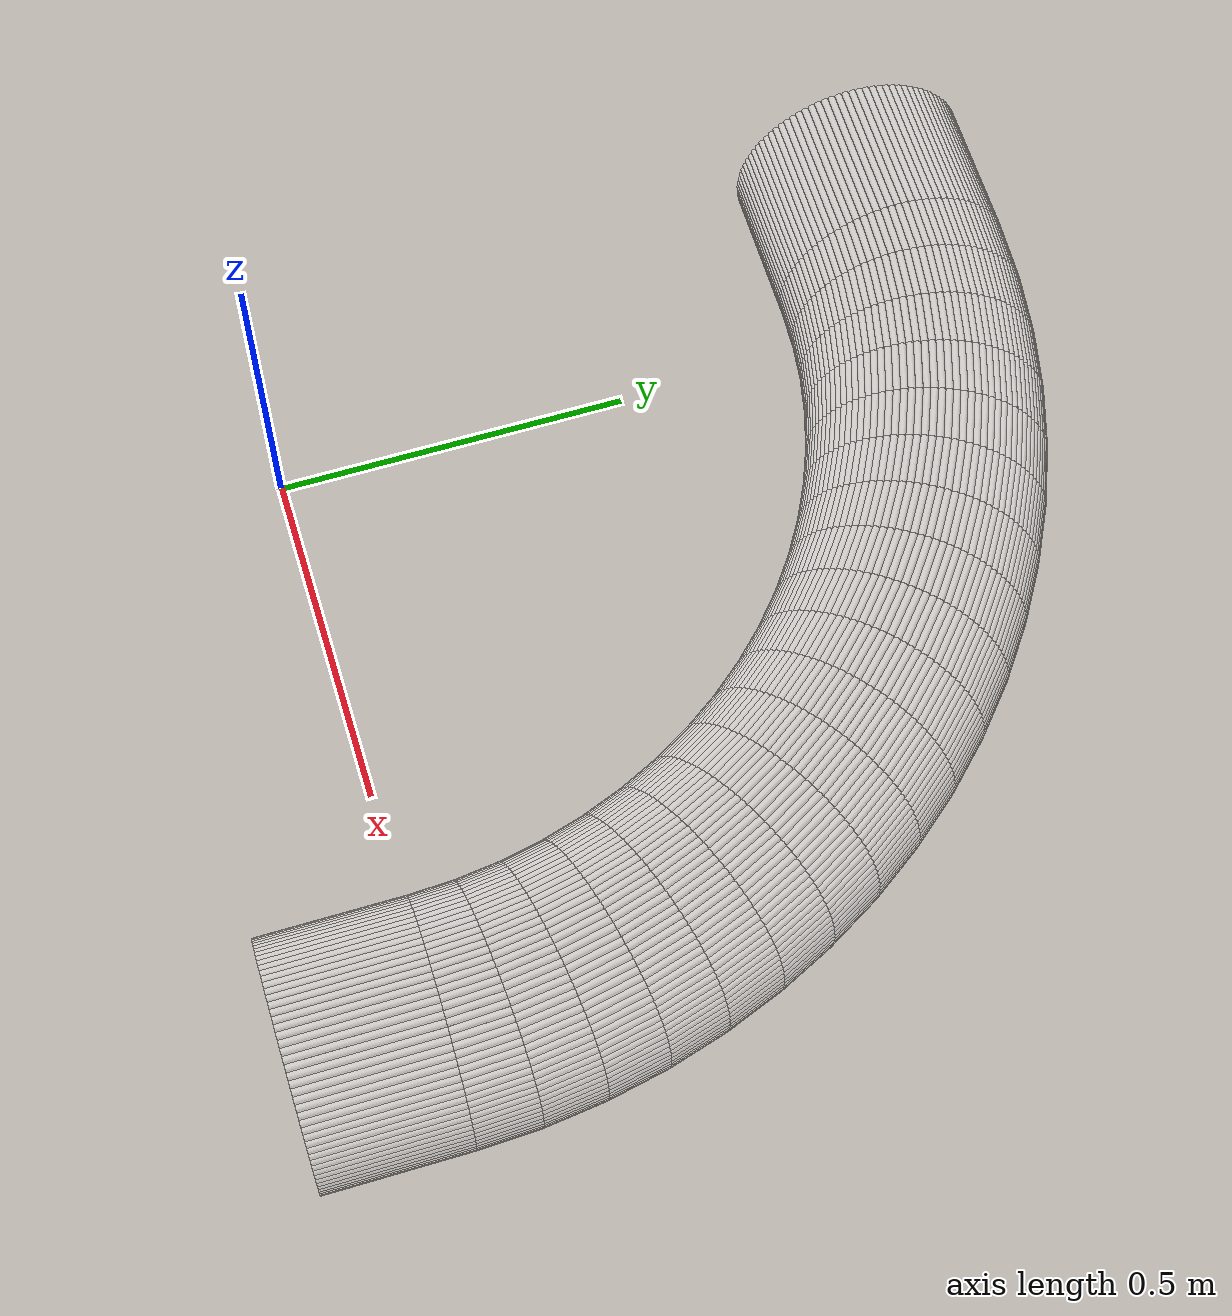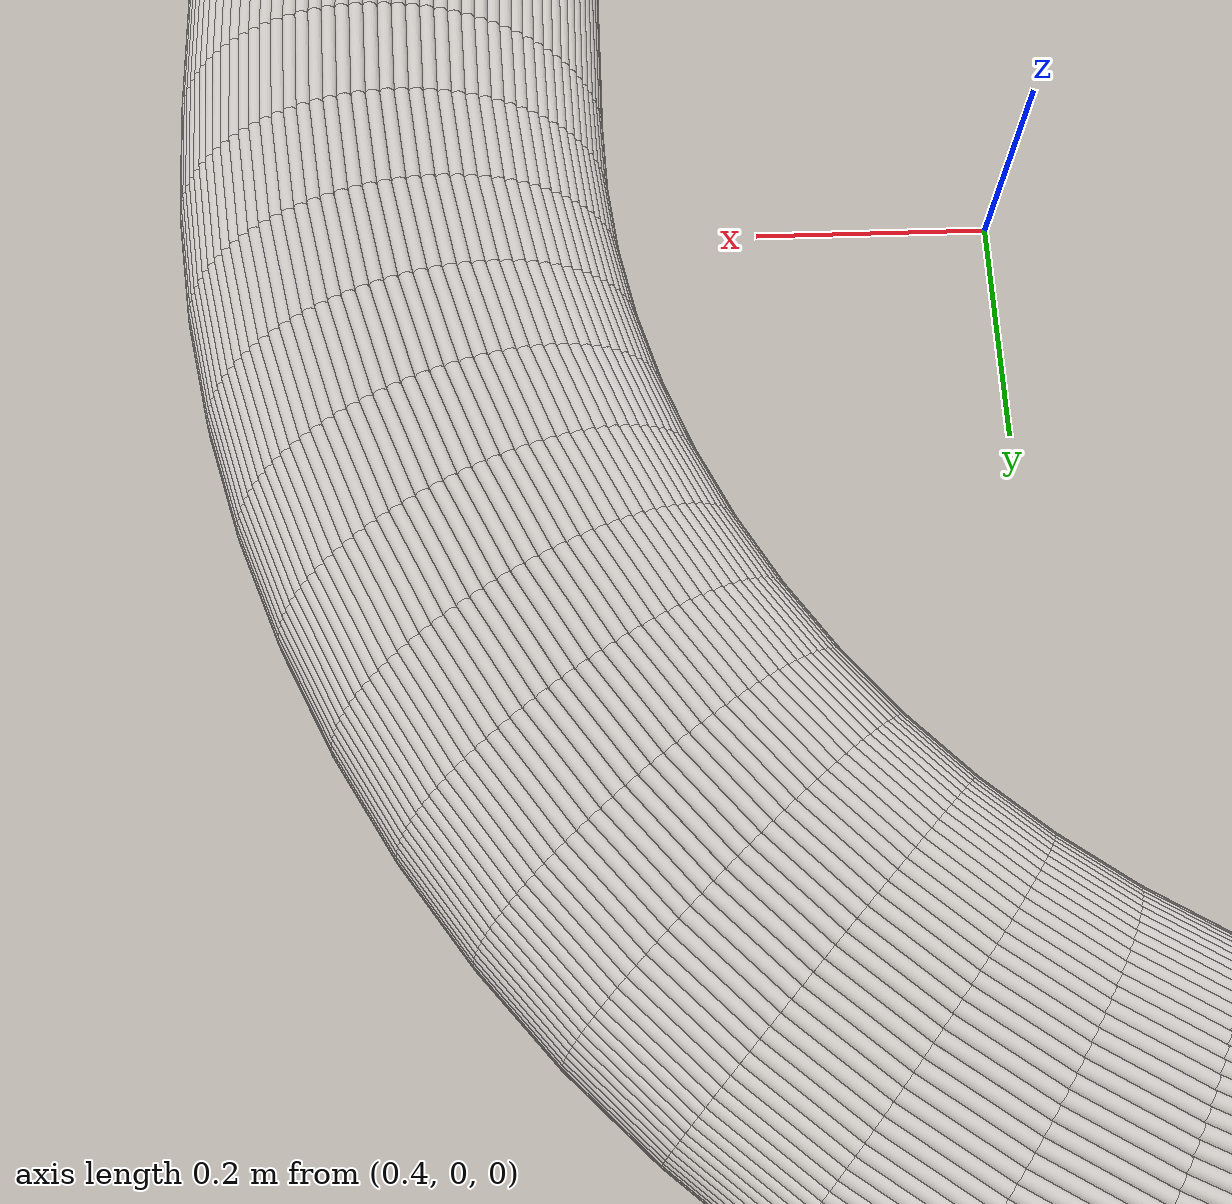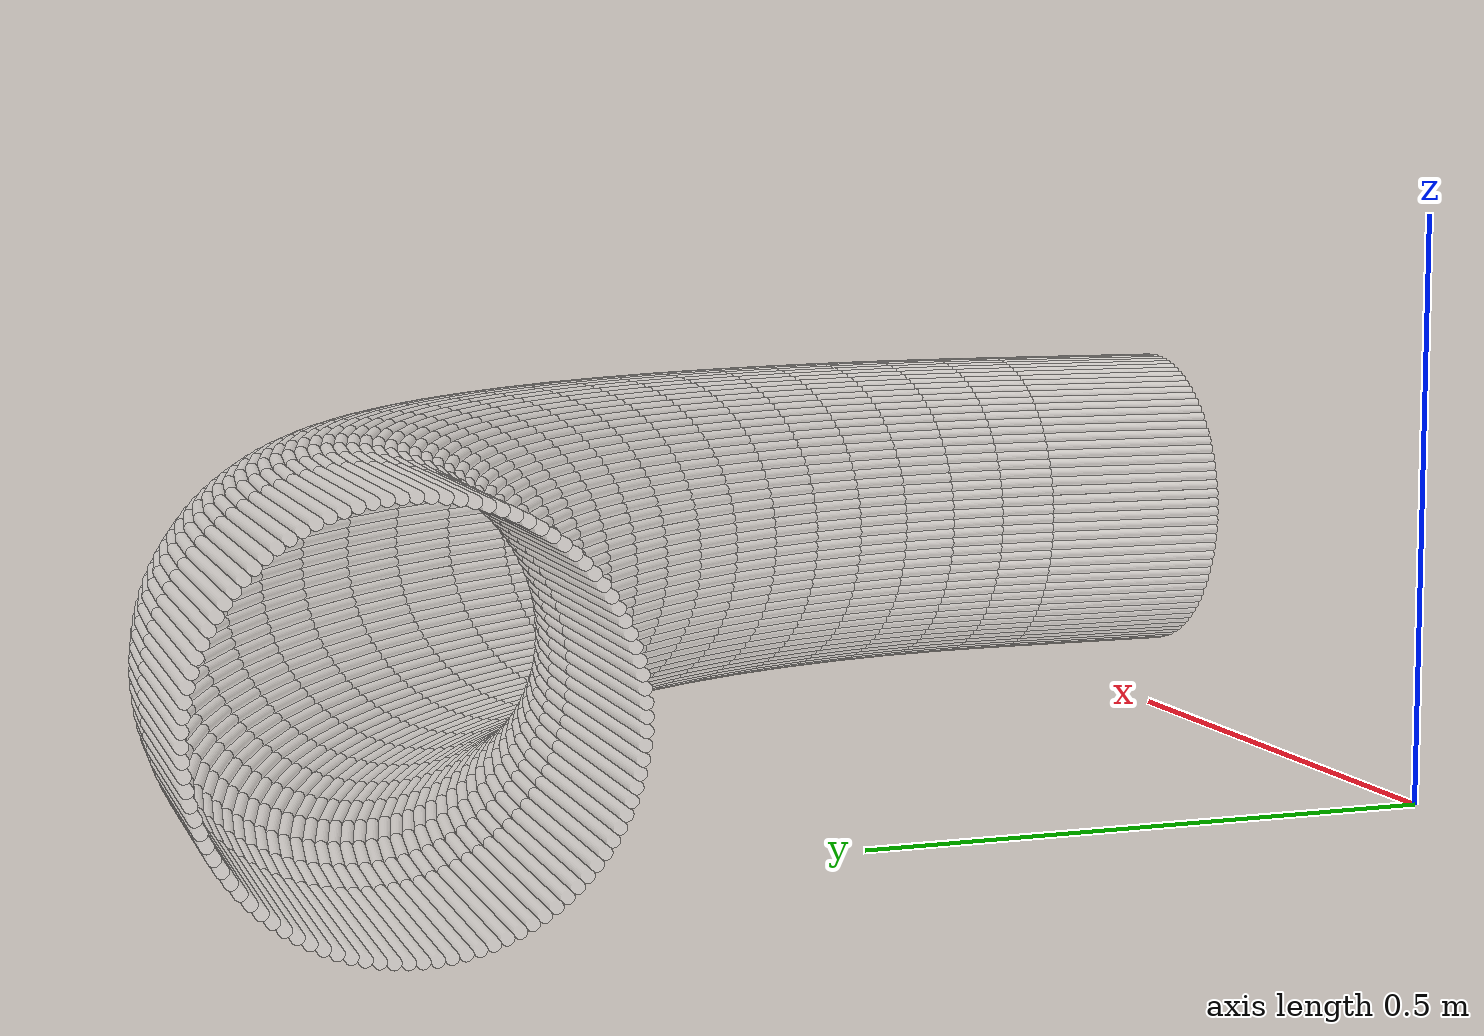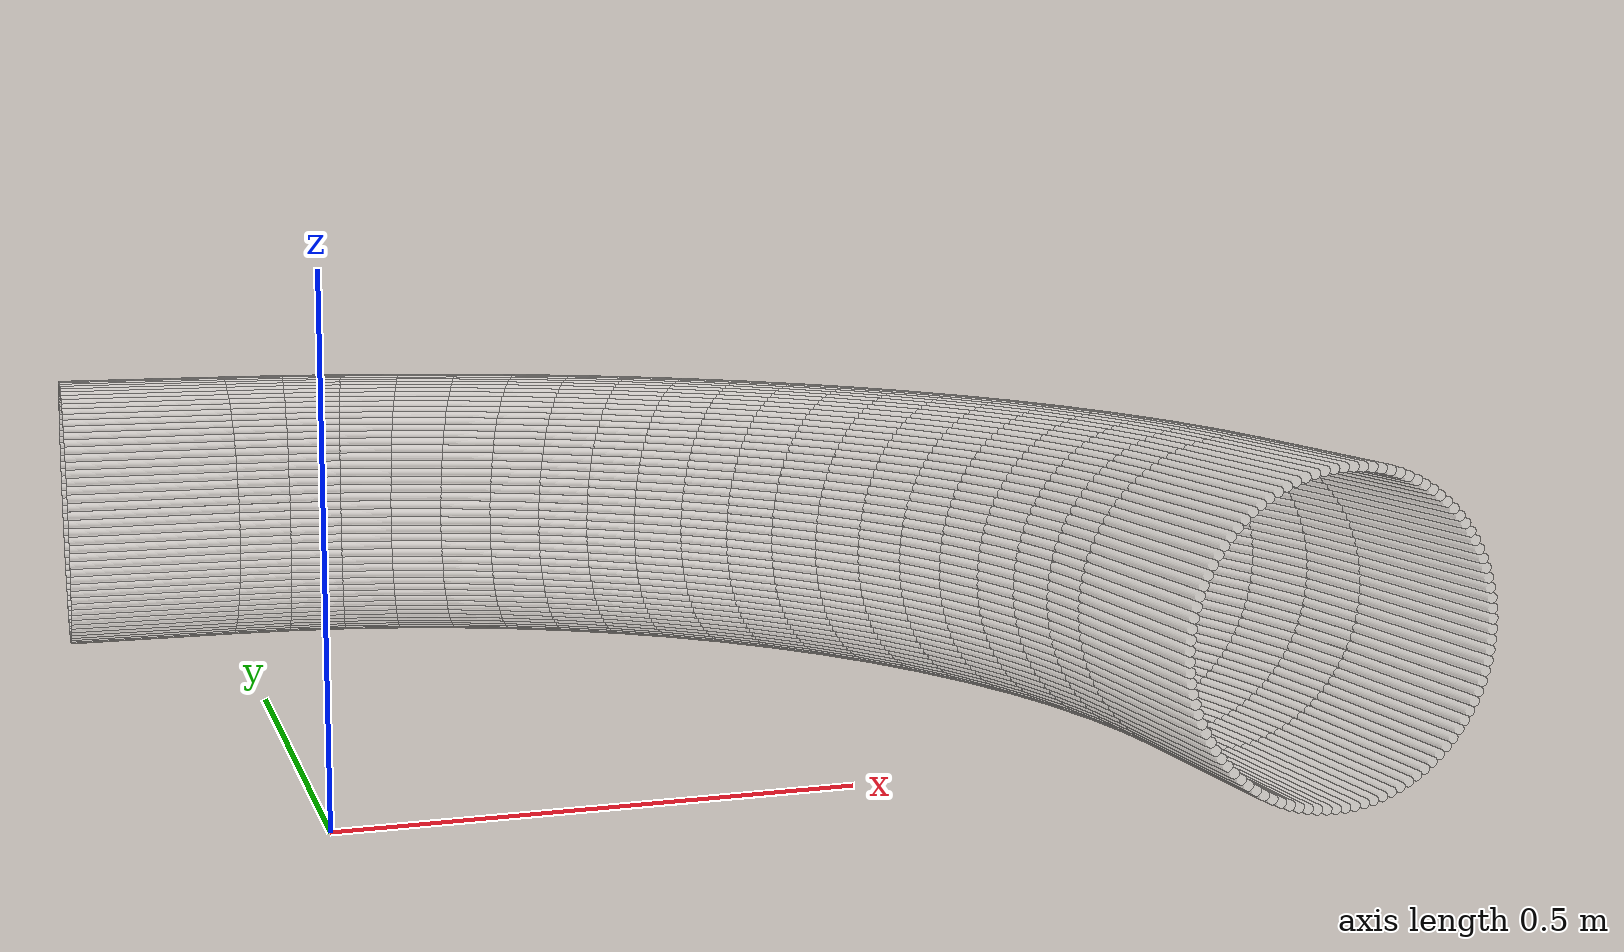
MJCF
<?xml version="1.0" encoding="utf-8"?>
<mujoco>
   <worldbody>
      <geom euler=" 0 10 0 " fromto="1.06 -0.2 0.16 1.06 0 0.16" rgba="1 1 1 0.35"
            size="0.0050257"
            type="cylinder"/>
      <geom euler=" 0 20 0 " fromto="1.0597 -0.2 0.17005 1.0597 0 0.17005"
            rgba="1 1 1 0.35"
            size="0.0050257"
            type="cylinder"/>
      <geom euler=" 0 30 0 " fromto="1.0587 -0.2 0.18005 1.0587 0 0.18005"
            rgba="1 1 1 0.35"
            size="0.0050257"
            type="cylinder"/>
      <geom euler=" 0 40 0 " fromto="1.0572 -0.2 0.18998 1.0572 0 0.18998"
            rgba="1 1 1 0.35"
            size="0.0050257"
            type="cylinder"/>
      <geom euler=" 0 50 0 " fromto="1.055 -0.2 0.19979 1.055 0 0.19979" rgba="1 1 1 0.35"
            size="0.0050257"
            type="cylinder"/>
      <geom euler=" 0 60 0 " fromto="1.0522 -0.2 0.20944 1.0522 0 0.20944"
            rgba="1 1 1 0.35"
            size="0.0050257"
            type="cylinder"/>
      <geom euler=" 0 70 0 " fromto="1.0488 -0.2 0.2189 1.0488 0 0.2189" rgba="1 1 1 0.35"
            size="0.0050257"
            type="cylinder"/>
      <geom euler=" 0 80 0 " fromto="1.0448 -0.2 0.22812 1.0448 0 0.22812"
            rgba="1 1 1 0.35"
            size="0.0050257"
            type="cylinder"/>
      <geom euler=" 0 90 0 " fromto="1.0402 -0.2 0.23708 1.0402 0 0.23708"
            rgba="1 1 1 0.35"
            size="0.0050257"
            type="cylinder"/>
      <geom euler=" 0 100 0 " fromto="1.0351 -0.2 0.24573 1.0351 0 0.24573"
            rgba="1 1 1 0.35"
            size="0.0050257"
            type="cylinder"/>
      <geom euler=" 0 110 0 " fromto="1.0294 -0.2 0.25405 1.0294 0 0.25405"
            rgba="1 1 1 0.35"
            size="0.0050257"
            type="cylinder"/>
      <geom euler=" 0 120 0 " fromto="1.0233 -0.2 0.26199 1.0233 0 0.26199"
            rgba="1 1 1 0.35"
            size="0.0050257"
            type="cylinder"/>
      <geom euler=" 0 130 0 " fromto="1.0166 -0.2 0.26953 1.0166 0 0.26953"
            rgba="1 1 1 0.35"
            size="0.0050257"
            type="cylinder"/>
      <geom euler=" 0 140 0 " fromto="1.0095 -0.2 0.27663 1.0095 0 0.27663"
            rgba="1 1 1 0.35"
            size="0.0050257"
            type="cylinder"/>
      <geom euler=" 0 150 0 " fromto="1.002 -0.2 0.28328 1.002 0 0.28328" rgba="1 1 1 0.35"
            size="0.0050257"
            type="cylinder"/>
      <geom euler=" 0 160 0 " fromto="0.99405 -0.2 0.28944 0.99405 0 0.28944"
            rgba="1 1 1 0.35"
            size="0.0050257"
            type="cylinder"/>
      <geom euler=" 0 170 0 " fromto="0.98573 -0.2 0.29509 0.98573 0 0.29509"
            rgba="1 1 1 0.35"
            size="0.0050257"
            type="cylinder"/>
      <geom euler=" 0 180 0 " fromto="0.97708 -0.2 0.30021 0.97708 0 0.30021"
            rgba="1 1 1 0.35"
            size="0.0050257"
            type="cylinder"/>
      <geom euler=" 0 190 0 " fromto="0.96812 -0.2 0.30477 0.96812 0 0.30477"
            rgba="1 1 1 0.35"
            size="0.0050257"
            type="cylinder"/>
      <geom euler=" 0 200 0 " fromto="0.9589 -0.2 0.30876 0.9589 0 0.30876"
            rgba="1 1 1 0.35"
            size="0.0050257"
            type="cylinder"/>
      <geom euler=" 0 210 0 " fromto="0.94944 -0.2 0.31217 0.94944 0 0.31217"
            rgba="1 1 1 0.35"
            size="0.0050257"
            type="cylinder"/>
      <geom euler=" 0 220 0 " fromto="0.93979 -0.2 0.31497 0.93979 0 0.31497"
            rgba="1 1 1 0.35"
            size="0.0050257"
            type="cylinder"/>
      <geom euler=" 0 230 0 " fromto="0.92998 -0.2 0.31717 0.92998 0 0.31717"
            rgba="1 1 1 0.35"
            size="0.0050257"
            type="cylinder"/>
      <geom euler=" 0 240 0 " fromto="0.92005 -0.2 0.31874 0.92005 0 0.31874"
            rgba="1 1 1 0.35"
            size="0.0050257"
            type="cylinder"/>
      <geom euler=" 0 250 0 " fromto="0.91005 -0.2 0.31968 0.91005 0 0.31968"
            rgba="1 1 1 0.35"
            size="0.0050257"
            type="cylinder"/>
      <geom euler=" 0 260 0 " fromto="0.9 -0.2 0.32 0.9 0 0.32" rgba="1 1 1 0.35"
            size="0.0050257"
            type="cylinder"/>
      <geom euler=" 0 270 0 " fromto="0.88995 -0.2 0.31968 0.88995 0 0.31968"
            rgba="1 1 1 0.35"
            size="0.0050257"
            type="cylinder"/>
      <geom euler=" 0 280 0 " fromto="0.87995 -0.2 0.31874 0.87995 0 0.31874"
            rgba="1 1 1 0.35"
            size="0.0050257"
            type="cylinder"/>
      <geom euler=" 0 290 0 " fromto="0.87002 -0.2 0.31717 0.87002 0 0.31717"
            rgba="1 1 1 0.35"
            size="0.0050257"
            type="cylinder"/>
      <geom euler=" 0 300 0 " fromto="0.86021 -0.2 0.31497 0.86021 0 0.31497"
            rgba="1 1 1 0.35"
            size="0.0050257"
            type="cylinder"/>
      <geom euler=" 0 310 0 " fromto="0.85056 -0.2 0.31217 0.85056 0 0.31217"
            rgba="1 1 1 0.35"
            size="0.0050257"
            type="cylinder"/>
      <geom euler=" 0 320 0 " fromto="0.8411 -0.2 0.30876 0.8411 0 0.30876"
            rgba="1 1 1 0.35"
            size="0.0050257"
            type="cylinder"/>
      <geom euler=" 0 330 0 " fromto="0.83188 -0.2 0.30477 0.83188 0 0.30477"
            rgba="1 1 1 0.35"
            size="0.0050257"
            type="cylinder"/>
      <geom euler=" 0 340 0 " fromto="0.82292 -0.2 0.30021 0.82292 0 0.30021"
            rgba="1 1 1 0.35"
            size="0.0050257"
            type="cylinder"/>
      <geom euler=" 0 350 0 " fromto="0.81427 -0.2 0.29509 0.81427 0 0.29509"
            rgba="1 1 1 0.35"
            size="0.0050257"
            type="cylinder"/>
      <geom euler=" 0 360 0 " fromto="0.80595 -0.2 0.28944 0.80595 0 0.28944"
            rgba="1 1 1 0.35"
            size="0.0050257"
            type="cylinder"/>
      <geom euler=" 0 370 0 " fromto="0.79801 -0.2 0.28328 0.79801 0 0.28328"
            rgba="1 1 1 0.35"
            size="0.0050257"
            type="cylinder"/>
      <geom euler=" 0 380 0 " fromto="0.79047 -0.2 0.27663 0.79047 0 0.27663"
            rgba="1 1 1 0.35"
            size="0.0050257"
            type="cylinder"/>
      <geom euler=" 0 390 0 " fromto="0.78337 -0.2 0.26953 0.78337 0 0.26953"
            rgba="1 1 1 0.35"
            size="0.0050257"
            type="cylinder"/>
      <geom euler=" 0 400 0 " fromto="0.77672 -0.2 0.26199 0.77672 0 0.26199"
            rgba="1 1 1 0.35"
            size="0.0050257"
            type="cylinder"/>
      <geom euler=" 0 410 0 " fromto="0.77056 -0.2 0.25405 0.77056 0 0.25405"
            rgba="1 1 1 0.35"
            size="0.0050257"
            type="cylinder"/>
      <geom euler=" 0 420 0 " fromto="0.76491 -0.2 0.24573 0.76491 0 0.24573"
            rgba="1 1 1 0.35"
            size="0.0050257"
            type="cylinder"/>
      <geom euler=" 0 430 0 " fromto="0.75979 -0.2 0.23708 0.75979 0 0.23708"
            rgba="1 1 1 0.35"
            size="0.0050257"
            type="cylinder"/>
      <geom euler=" 0 440 0 " fromto="0.75523 -0.2 0.22812 0.75523 0 0.22812"
            rgba="1 1 1 0.35"
            size="0.0050257"
            type="cylinder"/>
      <geom euler=" 0 450 0 " fromto="0.75124 -0.2 0.2189 0.75124 0 0.2189"
            rgba="1 1 1 0.35"
            size="0.0050257"
            type="cylinder"/>
      <geom euler=" 0 460 0 " fromto="0.74783 -0.2 0.20944 0.74783 0 0.20944"
            rgba="1 1 1 0.35"
            size="0.0050257"
            type="cylinder"/>
      <geom euler=" 0 470 0 " fromto="0.74503 -0.2 0.19979 0.74503 0 0.19979"
            rgba="1 1 1 0.35"
            size="0.0050257"
            type="cylinder"/>
      <geom euler=" 0 480 0 " fromto="0.74283 -0.2 0.18998 0.74283 0 0.18998"
            rgba="1 1 1 0.35"
            size="0.0050257"
            type="cylinder"/>
      <geom euler=" 0 490 0 " fromto="0.74126 -0.2 0.18005 0.74126 0 0.18005"
            rgba="1 1 1 0.35"
            size="0.0050257"
            type="cylinder"/>
      <geom euler=" 0 500 0 " fromto="0.74032 -0.2 0.17005 0.74032 0 0.17005"
            rgba="1 1 1 0.35"
            size="0.0050257"
            type="cylinder"/>
      <geom euler=" 0 510 0 " fromto="0.74 -0.2 0.16 0.74 0 0.16" rgba="1 1 1 0.35"
            size="0.0050257"
            type="cylinder"/>
      <geom euler=" 0 520 0 " fromto="0.74032 -0.2 0.14995 0.74032 0 0.14995"
            rgba="1 1 1 0.35"
            size="0.0050257"
            type="cylinder"/>
      <geom euler=" 0 530 0 " fromto="0.74126 -0.2 0.13995 0.74126 0 0.13995"
            rgba="1 1 1 0.35"
            size="0.0050257"
            type="cylinder"/>
      <geom euler=" 0 540 0 " fromto="0.74283 -0.2 0.13002 0.74283 0 0.13002"
            rgba="1 1 1 0.35"
            size="0.0050257"
            type="cylinder"/>
      <geom euler=" 0 550 0 " fromto="0.74503 -0.2 0.12021 0.74503 0 0.12021"
            rgba="1 1 1 0.35"
            size="0.0050257"
            type="cylinder"/>
      <geom euler=" 0 560 0 " fromto="0.74783 -0.2 0.11056 0.74783 0 0.11056"
            rgba="1 1 1 0.35"
            size="0.0050257"
            type="cylinder"/>
      <geom euler=" 0 570 0 " fromto="0.75124 -0.2 0.1011 0.75124 0 0.1011"
            rgba="1 1 1 0.35"
            size="0.0050257"
            type="cylinder"/>
      <geom euler=" 0 580 0 " fromto="0.75523 -0.2 0.091875 0.75523 0 0.091875"
            rgba="1 1 1 0.35"
            size="0.0050257"
            type="cylinder"/>
      <geom euler=" 0 590 0 " fromto="0.75979 -0.2 0.082919 0.75979 0 0.082919"
            rgba="1 1 1 0.35"
            size="0.0050257"
            type="cylinder"/>
      <geom euler=" 0 600 0 " fromto="0.76491 -0.2 0.074268 0.76491 0 0.074268"
            rgba="1 1 1 0.35"
            size="0.0050257"
            type="cylinder"/>
      <geom euler=" 0 610 0 " fromto="0.77056 -0.2 0.065954 0.77056 0 0.065954"
            rgba="1 1 1 0.35"
            size="0.0050257"
            type="cylinder"/>
      <geom euler=" 0 620 0 " fromto="0.77672 -0.2 0.058012 0.77672 0 0.058012"
            rgba="1 1 1 0.35"
            size="0.0050257"
            type="cylinder"/>
      <geom euler=" 0 630 0 " fromto="0.78337 -0.2 0.050472 0.78337 0 0.050472"
            rgba="1 1 1 0.35"
            size="0.0050257"
            type="cylinder"/>
      <geom euler=" 0 640 0 " fromto="0.79047 -0.2 0.043365 0.79047 0 0.043365"
            rgba="1 1 1 0.35"
            size="0.0050257"
            type="cylinder"/>
      <geom euler=" 0 650 0 " fromto="0.79801 -0.2 0.036718 0.79801 0 0.036718"
            rgba="1 1 1 0.35"
            size="0.0050257"
            type="cylinder"/>
      <geom euler=" 0 660 0 " fromto="0.80595 -0.2 0.030557 0.80595 0 0.030557"
            rgba="1 1 1 0.35"
            size="0.0050257"
            type="cylinder"/>
      <geom euler=" 0 670 0 " fromto="0.81427 -0.2 0.024908 0.81427 0 0.024908"
            rgba="1 1 1 0.35"
            size="0.0050257"
            type="cylinder"/>
      <geom euler=" 0 680 0 " fromto="0.82292 -0.2 0.019791 0.82292 0 0.019791"
            rgba="1 1 1 0.35"
            size="0.0050257"
            type="cylinder"/>
      <geom euler=" 0 690 0 " fromto="0.83188 -0.2 0.015228 0.83188 0 0.015228"
            rgba="1 1 1 0.35"
            size="0.0050257"
            type="cylinder"/>
      <geom euler=" 0 700 0 " fromto="0.8411 -0.2 0.011236 0.8411 0 0.011236"
            rgba="1 1 1 0.35"
            size="0.0050257"
            type="cylinder"/>
      <geom euler=" 0 710 0 " fromto="0.85056 -0.2 0.007831 0.85056 0 0.007831"
            rgba="1 1 1 0.35"
            size="0.0050257"
            type="cylinder"/>
      <geom euler=" 0 720 0 " fromto="0.86021 -0.2 0.0050267 0.86021 0 0.0050267"
            rgba="1 1 1 0.35"
            size="0.0050257"
            type="cylinder"/>
      <geom euler=" 0 730 0 " fromto="0.87002 -0.2 0.002834 0.87002 0 0.002834"
            rgba="1 1 1 0.35"
            size="0.0050257"
            type="cylinder"/>
      <geom euler=" 0 740 0 " fromto="0.87995 -0.2 0.0012616 0.87995 0 0.0012616"
            rgba="1 1 1 0.35"
            size="0.0050257"
            type="cylinder"/>
      <geom euler=" 0 750 0 " fromto="0.88995 -0.2 0.00031572 0.88995 0 0.00031572"
            rgba="1 1 1 0.35"
            size="0.0050257"
            type="cylinder"/>
      <geom euler=" 0 760 0 " fromto="0.9 -0.2 0 0.9 0 0" rgba="1 1 1 0.35"
            size="0.0050257"
            type="cylinder"/>
      <geom euler=" 0 770 0 " fromto="0.91005 -0.2 0.00031572 0.91005 0 0.00031572"
            rgba="1 1 1 0.35"
            size="0.0050257"
            type="cylinder"/>
      <geom euler=" 0 780 0 " fromto="0.92005 -0.2 0.0012616 0.92005 0 0.0012616"
            rgba="1 1 1 0.35"
            size="0.0050257"
            type="cylinder"/>
      <geom euler=" 0 790 0 " fromto="0.92998 -0.2 0.002834 0.92998 0 0.002834"
            rgba="1 1 1 0.35"
            size="0.0050257"
            type="cylinder"/>
      <geom euler=" 0 800 0 " fromto="0.93979 -0.2 0.0050267 0.93979 0 0.0050267"
            rgba="1 1 1 0.35"
            size="0.0050257"
            type="cylinder"/>
      <geom euler=" 0 810 0 " fromto="0.94944 -0.2 0.007831 0.94944 0 0.007831"
            rgba="1 1 1 0.35"
            size="0.0050257"
            type="cylinder"/>
      <geom euler=" 0 820 0 " fromto="0.9589 -0.2 0.011236 0.9589 0 0.011236"
            rgba="1 1 1 0.35"
            size="0.0050257"
            type="cylinder"/>
      <geom euler=" 0 830 0 " fromto="0.96812 -0.2 0.015228 0.96812 0 0.015228"
            rgba="1 1 1 0.35"
            size="0.0050257"
            type="cylinder"/>
      <geom euler=" 0 840 0 " fromto="0.97708 -0.2 0.019791 0.97708 0 0.019791"
            rgba="1 1 1 0.35"
            size="0.0050257"
            type="cylinder"/>
      <geom euler=" 0 850 0 " fromto="0.98573 -0.2 0.024908 0.98573 0 0.024908"
            rgba="1 1 1 0.35"
            size="0.0050257"
            type="cylinder"/>
      <geom euler=" 0 860 0 " fromto="0.99405 -0.2 0.030557 0.99405 0 0.030557"
            rgba="1 1 1 0.35"
            size="0.0050257"
            type="cylinder"/>
      <geom euler=" 0 870 0 " fromto="1.002 -0.2 0.036718 1.002 0 0.036718"
            rgba="1 1 1 0.35"
            size="0.0050257"
            type="cylinder"/>
      <geom euler=" 0 880 0 " fromto="1.0095 -0.2 0.043365 1.0095 0 0.043365"
            rgba="1 1 1 0.35"
            size="0.0050257"
            type="cylinder"/>
      <geom euler=" 0 890 0 " fromto="1.0166 -0.2 0.050472 1.0166 0 0.050472"
            rgba="1 1 1 0.35"
            size="0.0050257"
            type="cylinder"/>
      <geom euler=" 0 900 0 " fromto="1.0233 -0.2 0.058012 1.0233 0 0.058012"
            rgba="1 1 1 0.35"
            size="0.0050257"
            type="cylinder"/>
      <geom euler=" 0 910 0 " fromto="1.0294 -0.2 0.065954 1.0294 0 0.065954"
            rgba="1 1 1 0.35"
            size="0.0050257"
            type="cylinder"/>
      <geom euler=" 0 920 0 " fromto="1.0351 -0.2 0.074268 1.0351 0 0.074268"
            rgba="1 1 1 0.35"
            size="0.0050257"
            type="cylinder"/>
      <geom euler=" 0 930 0 " fromto="1.0402 -0.2 0.082919 1.0402 0 0.082919"
            rgba="1 1 1 0.35"
            size="0.0050257"
            type="cylinder"/>
      <geom euler=" 0 940 0 " fromto="1.0448 -0.2 0.091875 1.0448 0 0.091875"
            rgba="1 1 1 0.35"
            size="0.0050257"
            type="cylinder"/>
      <geom euler=" 0 950 0 " fromto="1.0488 -0.2 0.1011 1.0488 0 0.1011" rgba="1 1 1 0.35"
            size="0.0050257"
            type="cylinder"/>
      <geom euler=" 0 960 0 " fromto="1.0522 -0.2 0.11056 1.0522 0 0.11056"
            rgba="1 1 1 0.35"
            size="0.0050257"
            type="cylinder"/>
      <geom euler=" 0 970 0 " fromto="1.055 -0.2 0.12021 1.055 0 0.12021" rgba="1 1 1 0.35"
            size="0.0050257"
            type="cylinder"/>
      <geom euler=" 0 980 0 " fromto="1.0572 -0.2 0.13002 1.0572 0 0.13002"
            rgba="1 1 1 0.35"
            size="0.0050257"
            type="cylinder"/>
      <geom euler=" 0 990 0 " fromto="1.0587 -0.2 0.13995 1.0587 0 0.13995"
            rgba="1 1 1 0.35"
            size="0.0050257"
            type="cylinder"/>
      <geom euler=" 0 1000 0 " fromto="1.0597 -0.2 0.14995 1.0597 0 0.14995"
            rgba="1 1 1 0.35"
            size="0.0050257"
            type="cylinder"/>
      <geom euler=" 0 10 0 " fromto="1.06 0 0.16 1.0564 0.087534 0.16" rgba="1 1 1 0.35"
            size="0.0050257"
            type="cylinder"/>
      <geom euler=" 0 20 0 " fromto="1.0597 0 0.17005 1.0561 0.087508 0.17005"
            rgba="1 1 1 0.35"
            size="0.0050257"
            type="cylinder"/>
      <geom euler=" 0 30 0 " fromto="1.0587 0 0.18005 1.0551 0.08743 0.18005"
            rgba="1 1 1 0.35"
            size="0.0050257"
            type="cylinder"/>
      <geom euler=" 0 40 0 " fromto="1.0572 0 0.18998 1.0536 0.0873 0.18998"
            rgba="1 1 1 0.35"
            size="0.0050257"
            type="cylinder"/>
      <geom euler=" 0 50 0 " fromto="1.055 0 0.19979 1.0514 0.087119 0.19979"
            rgba="1 1 1 0.35"
            size="0.0050257"
            type="cylinder"/>
      <geom euler=" 0 60 0 " fromto="1.0522 0 0.20944 1.0486 0.086887 0.20944"
            rgba="1 1 1 0.35"
            size="0.0050257"
            type="cylinder"/>
      <geom euler=" 0 70 0 " fromto="1.0488 0 0.2189 1.0452 0.086606 0.2189"
            rgba="1 1 1 0.35"
            size="0.0050257"
            type="cylinder"/>
      <geom euler=" 0 80 0 " fromto="1.0448 0 0.22812 1.0412 0.086277 0.22812"
            rgba="1 1 1 0.35"
            size="0.0050257"
            type="cylinder"/>
      <geom euler=" 0 90 0 " fromto="1.0402 0 0.23708 1.0367 0.0859 0.23708"
            rgba="1 1 1 0.35"
            size="0.0050257"
            type="cylinder"/>
      <geom euler=" 0 100 0 " fromto="1.0351 0 0.24573 1.0316 0.085477 0.24573"
            rgba="1 1 1 0.35"
            size="0.0050257"
            type="cylinder"/>
      <geom euler=" 0 110 0 " fromto="1.0294 0 0.25405 1.0259 0.085011 0.25405"
            rgba="1 1 1 0.35"
            size="0.0050257"
            type="cylinder"/>
      <geom euler=" 0 120 0 " fromto="1.0233 0 0.26199 1.0198 0.084502 0.26199"
            rgba="1 1 1 0.35"
            size="0.0050257"
            type="cylinder"/>
      <geom euler=" 0 130 0 " fromto="1.0166 0 0.26953 1.0132 0.083953 0.26953"
            rgba="1 1 1 0.35"
            size="0.0050257"
            type="cylinder"/>
      <geom euler=" 0 140 0 " fromto="1.0095 0 0.27663 1.0061 0.083366 0.27663"
            rgba="1 1 1 0.35"
            size="0.0050257"
            type="cylinder"/>
      <geom euler=" 0 150 0 " fromto="1.002 0 0.28328 0.99857 0.082743 0.28328"
            rgba="1 1 1 0.35"
            size="0.0050257"
            type="cylinder"/>
      <geom euler=" 0 160 0 " fromto="0.99405 0 0.28944 0.99065 0.082088 0.28944"
            rgba="1 1 1 0.35"
            size="0.0050257"
            type="cylinder"/>
      <geom euler=" 0 170 0 " fromto="0.98573 0 0.29509 0.98237 0.081401 0.29509"
            rgba="1 1 1 0.35"
            size="0.0050257"
            type="cylinder"/>
      <geom euler=" 0 180 0 " fromto="0.97708 0 0.30021 0.97374 0.080687 0.30021"
            rgba="1 1 1 0.35"
            size="0.0050257"
            type="cylinder"/>
      <geom euler=" 0 190 0 " fromto="0.96812 0 0.30477 0.96482 0.079947 0.30477"
            rgba="1 1 1 0.35"
            size="0.0050257"
            type="cylinder"/>
      <geom euler=" 0 200 0 " fromto="0.9589 0 0.30876 0.95562 0.079185 0.30876"
            rgba="1 1 1 0.35"
            size="0.0050257"
            type="cylinder"/>
      <geom euler=" 0 210 0 " fromto="0.94944 0 0.31217 0.9462 0.078404 0.31217"
            rgba="1 1 1 0.35"
            size="0.0050257"
            type="cylinder"/>
      <geom euler=" 0 220 0 " fromto="0.93979 0 0.31497 0.93658 0.077607 0.31497"
            rgba="1 1 1 0.35"
            size="0.0050257"
            type="cylinder"/>
      <geom euler=" 0 230 0 " fromto="0.92998 0 0.31717 0.9268 0.076797 0.31717"
            rgba="1 1 1 0.35"
            size="0.0050257"
            type="cylinder"/>
      <geom euler=" 0 240 0 " fromto="0.92005 0 0.31874 0.91691 0.075977 0.31874"
            rgba="1 1 1 0.35"
            size="0.0050257"
            type="cylinder"/>
      <geom euler=" 0 250 0 " fromto="0.91005 0 0.31968 0.90694 0.075151 0.31968"
            rgba="1 1 1 0.35"
            size="0.0050257"
            type="cylinder"/>
      <geom euler=" 0 260 0 " fromto="0.9 0 0.32 0.89693 0.074321 0.32" rgba="1 1 1 0.35"
            size="0.0050257"
            type="cylinder"/>
      <geom euler=" 0 270 0 " fromto="0.88995 0 0.31968 0.88691 0.073492 0.31968"
            rgba="1 1 1 0.35"
            size="0.0050257"
            type="cylinder"/>
      <geom euler=" 0 280 0 " fromto="0.87995 0 0.31874 0.87694 0.072665 0.31874"
            rgba="1 1 1 0.35"
            size="0.0050257"
            type="cylinder"/>
      <geom euler=" 0 290 0 " fromto="0.87002 0 0.31717 0.86705 0.071846 0.31717"
            rgba="1 1 1 0.35"
            size="0.0050257"
            type="cylinder"/>
      <geom euler=" 0 300 0 " fromto="0.86021 0 0.31497 0.85727 0.071036 0.31497"
            rgba="1 1 1 0.35"
            size="0.0050257"
            type="cylinder"/>
      <geom euler=" 0 310 0 " fromto="0.85056 0 0.31217 0.84765 0.070238 0.31217"
            rgba="1 1 1 0.35"
            size="0.0050257"
            type="cylinder"/>
      <geom euler=" 0 320 0 " fromto="0.8411 0 0.30876 0.83823 0.069457 0.30876"
            rgba="1 1 1 0.35"
            size="0.0050257"
            type="cylinder"/>
      <geom euler=" 0 330 0 " fromto="0.83188 0 0.30477 0.82903 0.068696 0.30477"
            rgba="1 1 1 0.35"
            size="0.0050257"
            type="cylinder"/>
      <geom euler=" 0 340 0 " fromto="0.82292 0 0.30021 0.82011 0.067956 0.30021"
            rgba="1 1 1 0.35"
            size="0.0050257"
            type="cylinder"/>
      <geom euler=" 0 350 0 " fromto="0.81427 0 0.29509 0.81149 0.067242 0.29509"
            rgba="1 1 1 0.35"
            size="0.0050257"
            type="cylinder"/>
      <geom euler=" 0 360 0 " fromto="0.80595 0 0.28944 0.8032 0.066555 0.28944"
            rgba="1 1 1 0.35"
            size="0.0050257"
            type="cylinder"/>
      <geom euler=" 0 370 0 " fromto="0.79801 0 0.28328 0.79529 0.065899 0.28328"
            rgba="1 1 1 0.35"
            size="0.0050257"
            type="cylinder"/>
      <geom euler=" 0 380 0 " fromto="0.79047 0 0.27663 0.78777 0.065277 0.27663"
            rgba="1 1 1 0.35"
            size="0.0050257"
            type="cylinder"/>
      <geom euler=" 0 390 0 " fromto="0.78337 0 0.26953 0.78069 0.06469 0.26953"
            rgba="1 1 1 0.35"
            size="0.0050257"
            type="cylinder"/>
      <geom euler=" 0 400 0 " fromto="0.77672 0 0.26199 0.77406 0.064141 0.26199"
            rgba="1 1 1 0.35"
            size="0.0050257"
            type="cylinder"/>
      <geom euler=" 0 410 0 " fromto="0.77056 0 0.25405 0.76793 0.063632 0.25405"
            rgba="1 1 1 0.35"
            size="0.0050257"
            type="cylinder"/>
      <geom euler=" 0 420 0 " fromto="0.76491 0 0.24573 0.76229 0.063166 0.24573"
            rgba="1 1 1 0.35"
            size="0.0050257"
            type="cylinder"/>
      <geom euler=" 0 430 0 " fromto="0.75979 0 0.23708 0.7572 0.062743 0.23708"
            rgba="1 1 1 0.35"
            size="0.0050257"
            type="cylinder"/>
      <geom euler=" 0 440 0 " fromto="0.75523 0 0.22812 0.75265 0.062366 0.22812"
            rgba="1 1 1 0.35"
            size="0.0050257"
            type="cylinder"/>
      <geom euler=" 0 450 0 " fromto="0.75124 0 0.2189 0.74867 0.062037 0.2189"
            rgba="1 1 1 0.35"
            size="0.0050257"
            type="cylinder"/>
      <geom euler=" 0 460 0 " fromto="0.74783 0 0.20944 0.74528 0.061755 0.20944"
            rgba="1 1 1 0.35"
            size="0.0050257"
            type="cylinder"/>
      <geom euler=" 0 470 0 " fromto="0.74503 0 0.19979 0.74248 0.061524 0.19979"
            rgba="1 1 1 0.35"
            size="0.0050257"
            type="cylinder"/>
      <geom euler=" 0 480 0 " fromto="0.74283 0 0.18998 0.7403 0.061343 0.18998"
            rgba="1 1 1 0.35"
            size="0.0050257"
            type="cylinder"/>
      <geom euler=" 0 490 0 " fromto="0.74126 0 0.18005 0.73873 0.061213 0.18005"
            rgba="1 1 1 0.35"
            size="0.0050257"
            type="cylinder"/>
      <geom euler=" 0 500 0 " fromto="0.74032 0 0.17005 0.73779 0.061135 0.17005"
            rgba="1 1 1 0.35"
            size="0.0050257"
            type="cylinder"/>
      <geom euler=" 0 510 0 " fromto="0.74 0 0.16 0.73747 0.061109 0.16" rgba="1 1 1 0.35"
            size="0.0050257"
            type="cylinder"/>
      <geom euler=" 0 520 0 " fromto="0.74032 0 0.14995 0.73779 0.061135 0.14995"
            rgba="1 1 1 0.35"
            size="0.0050257"
            type="cylinder"/>
      <geom euler=" 0 530 0 " fromto="0.74126 0 0.13995 0.73873 0.061213 0.13995"
            rgba="1 1 1 0.35"
            size="0.0050257"
            type="cylinder"/>
      <geom euler=" 0 540 0 " fromto="0.74283 0 0.13002 0.7403 0.061343 0.13002"
            rgba="1 1 1 0.35"
            size="0.0050257"
            type="cylinder"/>
      <geom euler=" 0 550 0 " fromto="0.74503 0 0.12021 0.74248 0.061524 0.12021"
            rgba="1 1 1 0.35"
            size="0.0050257"
            type="cylinder"/>
      <geom euler=" 0 560 0 " fromto="0.74783 0 0.11056 0.74528 0.061755 0.11056"
            rgba="1 1 1 0.35"
            size="0.0050257"
            type="cylinder"/>
      <geom euler=" 0 570 0 " fromto="0.75124 0 0.1011 0.74867 0.062037 0.1011"
            rgba="1 1 1 0.35"
            size="0.0050257"
            type="cylinder"/>
      <geom euler=" 0 580 0 " fromto="0.75523 0 0.091875 0.75265 0.062366 0.091875"
            rgba="1 1 1 0.35"
            size="0.0050257"
            type="cylinder"/>
      <geom euler=" 0 590 0 " fromto="0.75979 0 0.082919 0.7572 0.062743 0.082919"
            rgba="1 1 1 0.35"
            size="0.0050257"
            type="cylinder"/>
      <geom euler=" 0 600 0 " fromto="0.76491 0 0.074268 0.76229 0.063166 0.074268"
            rgba="1 1 1 0.35"
            size="0.0050257"
            type="cylinder"/>
      <geom euler=" 0 610 0 " fromto="0.77056 0 0.065954 0.76793 0.063632 0.065954"
            rgba="1 1 1 0.35"
            size="0.0050257"
            type="cylinder"/>
      <geom euler=" 0 620 0 " fromto="0.77672 0 0.058012 0.77406 0.064141 0.058012"
            rgba="1 1 1 0.35"
            size="0.0050257"
            type="cylinder"/>
      <geom euler=" 0 630 0 " fromto="0.78337 0 0.050472 0.78069 0.06469 0.050472"
            rgba="1 1 1 0.35"
            size="0.0050257"
            type="cylinder"/>
      <geom euler=" 0 640 0 " fromto="0.79047 0 0.043365 0.78777 0.065277 0.043365"
            rgba="1 1 1 0.35"
            size="0.0050257"
            type="cylinder"/>
      <geom euler=" 0 650 0 " fromto="0.79801 0 0.036718 0.79529 0.065899 0.036718"
            rgba="1 1 1 0.35"
            size="0.0050257"
            type="cylinder"/>
      <geom euler=" 0 660 0 " fromto="0.80595 0 0.030557 0.8032 0.066555 0.030557"
            rgba="1 1 1 0.35"
            size="0.0050257"
            type="cylinder"/>
      <geom euler=" 0 670 0 " fromto="0.81427 0 0.024908 0.81149 0.067242 0.024908"
            rgba="1 1 1 0.35"
            size="0.0050257"
            type="cylinder"/>
      <geom euler=" 0 680 0 " fromto="0.82292 0 0.019791 0.82011 0.067956 0.019791"
            rgba="1 1 1 0.35"
            size="0.0050257"
            type="cylinder"/>
      <geom euler=" 0 690 0 " fromto="0.83188 0 0.015228 0.82903 0.068696 0.015228"
            rgba="1 1 1 0.35"
            size="0.0050257"
            type="cylinder"/>
      <geom euler=" 0 700 0 " fromto="0.8411 0 0.011236 0.83823 0.069457 0.011236"
            rgba="1 1 1 0.35"
            size="0.0050257"
            type="cylinder"/>
      <geom euler=" 0 710 0 " fromto="0.85056 0 0.007831 0.84765 0.070238 0.007831"
            rgba="1 1 1 0.35"
            size="0.0050257"
            type="cylinder"/>
      <geom euler=" 0 720 0 " fromto="0.86021 0 0.0050267 0.85727 0.071036 0.0050267"
            rgba="1 1 1 0.35"
            size="0.0050257"
            type="cylinder"/>
      <geom euler=" 0 730 0 " fromto="0.87002 0 0.002834 0.86705 0.071846 0.002834"
            rgba="1 1 1 0.35"
            size="0.0050257"
            type="cylinder"/>
      <geom euler=" 0 740 0 " fromto="0.87995 0 0.0012616 0.87694 0.072665 0.0012616"
            rgba="1 1 1 0.35"
            size="0.0050257"
            type="cylinder"/>
      <geom euler=" 0 750 0 " fromto="0.88995 0 0.00031572 0.88691 0.073492 0.00031572"
            rgba="1 1 1 0.35"
            size="0.0050257"
            type="cylinder"/>
      <geom euler=" 0 760 0 " fromto="0.9 0 0 0.89693 0.074321 0" rgba="1 1 1 0.35"
            size="0.0050257"
            type="cylinder"/>
      <geom euler=" 0 770 0 " fromto="0.91005 0 0.00031572 0.90694 0.075151 0.00031572"
            rgba="1 1 1 0.35"
            size="0.0050257"
            type="cylinder"/>
      <geom euler=" 0 780 0 " fromto="0.92005 0 0.0012616 0.91691 0.075977 0.0012616"
            rgba="1 1 1 0.35"
            size="0.0050257"
            type="cylinder"/>
      <geom euler=" 0 790 0 " fromto="0.92998 0 0.002834 0.9268 0.076797 0.002834"
            rgba="1 1 1 0.35"
            size="0.0050257"
            type="cylinder"/>
      <geom euler=" 0 800 0 " fromto="0.93979 0 0.0050267 0.93658 0.077607 0.0050267"
            rgba="1 1 1 0.35"
            size="0.0050257"
            type="cylinder"/>
      <geom euler=" 0 810 0 " fromto="0.94944 0 0.007831 0.9462 0.078404 0.007831"
            rgba="1 1 1 0.35"
            size="0.0050257"
            type="cylinder"/>
      <geom euler=" 0 820 0 " fromto="0.9589 0 0.011236 0.95562 0.079185 0.011236"
            rgba="1 1 1 0.35"
            size="0.0050257"
            type="cylinder"/>
      <geom euler=" 0 830 0 " fromto="0.96812 0 0.015228 0.96482 0.079947 0.015228"
            rgba="1 1 1 0.35"
            size="0.0050257"
            type="cylinder"/>
      <geom euler=" 0 840 0 " fromto="0.97708 0 0.019791 0.97374 0.080687 0.019791"
            rgba="1 1 1 0.35"
            size="0.0050257"
            type="cylinder"/>
      <geom euler=" 0 850 0 " fromto="0.98573 0 0.024908 0.98237 0.081401 0.024908"
            rgba="1 1 1 0.35"
            size="0.0050257"
            type="cylinder"/>
      <geom euler=" 0 860 0 " fromto="0.99405 0 0.030557 0.99065 0.082088 0.030557"
            rgba="1 1 1 0.35"
            size="0.0050257"
            type="cylinder"/>
      <geom euler=" 0 870 0 " fromto="1.002 0 0.036718 0.99857 0.082743 0.036718"
            rgba="1 1 1 0.35"
            size="0.0050257"
            type="cylinder"/>
      <geom euler=" 0 880 0 " fromto="1.0095 0 0.043365 1.0061 0.083366 0.043365"
            rgba="1 1 1 0.35"
            size="0.0050257"
            type="cylinder"/>
      <geom euler=" 0 890 0 " fromto="1.0166 0 0.050472 1.0132 0.083953 0.050472"
            rgba="1 1 1 0.35"
            size="0.0050257"
            type="cylinder"/>
      <geom euler=" 0 900 0 " fromto="1.0233 0 0.058012 1.0198 0.084502 0.058012"
            rgba="1 1 1 0.35"
            size="0.0050257"
            type="cylinder"/>
      <geom euler=" 0 910 0 " fromto="1.0294 0 0.065954 1.0259 0.085011 0.065954"
            rgba="1 1 1 0.35"
            size="0.0050257"
            type="cylinder"/>
      <geom euler=" 0 920 0 " fromto="1.0351 0 0.074268 1.0316 0.085477 0.074268"
            rgba="1 1 1 0.35"
            size="0.0050257"
            type="cylinder"/>
      <geom euler=" 0 930 0 " fromto="1.0402 0 0.082919 1.0367 0.0859 0.082919"
            rgba="1 1 1 0.35"
            size="0.0050257"
            type="cylinder"/>
      <geom euler=" 0 940 0 " fromto="1.0448 0 0.091875 1.0412 0.086277 0.091875"
            rgba="1 1 1 0.35"
            size="0.0050257"
            type="cylinder"/>
      <geom euler=" 0 950 0 " fromto="1.0488 0 0.1011 1.0452 0.086606 0.1011"
            rgba="1 1 1 0.35"
            size="0.0050257"
            type="cylinder"/>
      <geom euler=" 0 960 0 " fromto="1.0522 0 0.11056 1.0486 0.086887 0.11056"
            rgba="1 1 1 0.35"
            size="0.0050257"
            type="cylinder"/>
      <geom euler=" 0 970 0 " fromto="1.055 0 0.12021 1.0514 0.087119 0.12021"
            rgba="1 1 1 0.35"
            size="0.0050257"
            type="cylinder"/>
      <geom euler=" 0 980 0 " fromto="1.0572 0 0.13002 1.0536 0.0873 0.13002"
            rgba="1 1 1 0.35"
            size="0.0050257"
            type="cylinder"/>
      <geom euler=" 0 990 0 " fromto="1.0587 0 0.13995 1.0551 0.08743 0.13995"
            rgba="1 1 1 0.35"
            size="0.0050257"
            type="cylinder"/>
      <geom euler=" 0 1000 0 " fromto="1.0597 0 0.14995 1.0561 0.087508 0.14995"
            rgba="1 1 1 0.35"
            size="0.0050257"
            type="cylinder"/>
      <geom euler=" 0 10 0 " fromto="1.0564 0.087534 0.16 1.0455 0.17447 0.16"
            rgba="1 1 1 0.35"
            size="0.0050257"
            type="cylinder"/>
      <geom euler=" 0 20 0 " fromto="1.0561 0.087508 0.17005 1.0452 0.17442 0.17005"
            rgba="1 1 1 0.35"
            size="0.0050257"
            type="cylinder"/>
      <geom euler=" 0 30 0 " fromto="1.0551 0.08743 0.18005 1.0443 0.17426 0.18005"
            rgba="1 1 1 0.35"
            size="0.0050257"
            type="cylinder"/>
      <geom euler=" 0 40 0 " fromto="1.0536 0.0873 0.18998 1.0427 0.174 0.18998"
            rgba="1 1 1 0.35"
            size="0.0050257"
            type="cylinder"/>
      <geom euler=" 0 50 0 " fromto="1.0514 0.087119 0.19979 1.0406 0.17364 0.19979"
            rgba="1 1 1 0.35"
            size="0.0050257"
            type="cylinder"/>
      <geom euler=" 0 60 0 " fromto="1.0486 0.086887 0.20944 1.0378 0.17318 0.20944"
            rgba="1 1 1 0.35"
            size="0.0050257"
            type="cylinder"/>
      <geom euler=" 0 70 0 " fromto="1.0452 0.086606 0.2189 1.0345 0.17262 0.2189"
            rgba="1 1 1 0.35"
            size="0.0050257"
            type="cylinder"/>
      <geom euler=" 0 80 0 " fromto="1.0412 0.086277 0.22812 1.0305 0.17196 0.22812"
            rgba="1 1 1 0.35"
            size="0.0050257"
            type="cylinder"/>
      <geom euler=" 0 90 0 " fromto="1.0367 0.0859 0.23708 1.026 0.17121 0.23708"
            rgba="1 1 1 0.35"
            size="0.0050257"
            type="cylinder"/>
      <geom euler=" 0 100 0 " fromto="1.0316 0.085477 0.24573 1.021 0.17037 0.24573"
            rgba="1 1 1 0.35"
            size="0.0050257"
            type="cylinder"/>
      <geom euler=" 0 110 0 " fromto="1.0259 0.085011 0.25405 1.0154 0.16944 0.25405"
            rgba="1 1 1 0.35"
            size="0.0050257"
            type="cylinder"/>
      <geom euler=" 0 120 0 " fromto="1.0198 0.084502 0.26199 1.0093 0.16843 0.26199"
            rgba="1 1 1 0.35"
            size="0.0050257"
            type="cylinder"/>
      <geom euler=" 0 130 0 " fromto="1.0132 0.083953 0.26953 1.0028 0.16733 0.26953"
            rgba="1 1 1 0.35"
            size="0.0050257"
            type="cylinder"/>
      <geom euler=" 0 140 0 " fromto="1.0061 0.083366 0.27663 0.99576 0.16616 0.27663"
            rgba="1 1 1 0.35"
            size="0.0050257"
            type="cylinder"/>
      <geom euler=" 0 150 0 " fromto="0.99857 0.082743 0.28328 0.98832 0.16492 0.28328"
            rgba="1 1 1 0.35"
            size="0.0050257"
            type="cylinder"/>
      <geom euler=" 0 160 0 " fromto="0.99065 0.082088 0.28944 0.98049 0.16361 0.28944"
            rgba="1 1 1 0.35"
            size="0.0050257"
            type="cylinder"/>
      <geom euler=" 0 170 0 " fromto="0.98237 0.081401 0.29509 0.97229 0.16225 0.29509"
            rgba="1 1 1 0.35"
            size="0.0050257"
            type="cylinder"/>
      <geom euler=" 0 180 0 " fromto="0.97374 0.080687 0.30021 0.96375 0.16082 0.30021"
            rgba="1 1 1 0.35"
            size="0.0050257"
            type="cylinder"/>
      <geom euler=" 0 190 0 " fromto="0.96482 0.079947 0.30477 0.95492 0.15935 0.30477"
            rgba="1 1 1 0.35"
            size="0.0050257"
            type="cylinder"/>
      <geom euler=" 0 200 0 " fromto="0.95562 0.079185 0.30876 0.94582 0.15783 0.30876"
            rgba="1 1 1 0.35"
            size="0.0050257"
            type="cylinder"/>
      <geom euler=" 0 210 0 " fromto="0.9462 0.078404 0.31217 0.93649 0.15627 0.31217"
            rgba="1 1 1 0.35"
            size="0.0050257"
            type="cylinder"/>
      <geom euler=" 0 220 0 " fromto="0.93658 0.077607 0.31497 0.92697 0.15468 0.31497"
            rgba="1 1 1 0.35"
            size="0.0050257"
            type="cylinder"/>
      <geom euler=" 0 230 0 " fromto="0.9268 0.076797 0.31717 0.9173 0.15307 0.31717"
            rgba="1 1 1 0.35"
            size="0.0050257"
            type="cylinder"/>
      <geom euler=" 0 240 0 " fromto="0.91691 0.075977 0.31874 0.9075 0.15144 0.31874"
            rgba="1 1 1 0.35"
            size="0.0050257"
            type="cylinder"/>
      <geom euler=" 0 250 0 " fromto="0.90694 0.075151 0.31968 0.89763 0.14979 0.31968"
            rgba="1 1 1 0.35"
            size="0.0050257"
            type="cylinder"/>
      <geom euler=" 0 260 0 " fromto="0.89693 0.074321 0.32 0.88773 0.14814 0.32"
            rgba="1 1 1 0.35"
            size="0.0050257"
            type="cylinder"/>
      <geom euler=" 0 270 0 " fromto="0.88691 0.073492 0.31968 0.87782 0.14648 0.31968"
            rgba="1 1 1 0.35"
            size="0.0050257"
            type="cylinder"/>
      <geom euler=" 0 280 0 " fromto="0.87694 0.072665 0.31874 0.86795 0.14483 0.31874"
            rgba="1 1 1 0.35"
            size="0.0050257"
            type="cylinder"/>
      <geom euler=" 0 290 0 " fromto="0.86705 0.071846 0.31717 0.85815 0.1432 0.31717"
            rgba="1 1 1 0.35"
            size="0.0050257"
            type="cylinder"/>
      <geom euler=" 0 300 0 " fromto="0.85727 0.071036 0.31497 0.84848 0.14159 0.31497"
            rgba="1 1 1 0.35"
            size="0.0050257"
            type="cylinder"/>
      <geom euler=" 0 310 0 " fromto="0.84765 0.070238 0.31217 0.83896 0.14 0.31217"
            rgba="1 1 1 0.35"
            size="0.0050257"
            type="cylinder"/>
      <geom euler=" 0 320 0 " fromto="0.83823 0.069457 0.30876 0.82963 0.13844 0.30876"
            rgba="1 1 1 0.35"
            size="0.0050257"
            type="cylinder"/>
      <geom euler=" 0 330 0 " fromto="0.82903 0.068696 0.30477 0.82053 0.13692 0.30477"
            rgba="1 1 1 0.35"
            size="0.0050257"
            type="cylinder"/>
      <geom euler=" 0 340 0 " fromto="0.82011 0.067956 0.30021 0.8117 0.13545 0.30021"
            rgba="1 1 1 0.35"
            size="0.0050257"
            type="cylinder"/>
      <geom euler=" 0 350 0 " fromto="0.81149 0.067242 0.29509 0.80316 0.13402 0.29509"
            rgba="1 1 1 0.35"
            size="0.0050257"
            type="cylinder"/>
      <geom euler=" 0 360 0 " fromto="0.8032 0.066555 0.28944 0.79496 0.13266 0.28944"
            rgba="1 1 1 0.35"
            size="0.0050257"
            type="cylinder"/>
      <geom euler=" 0 370 0 " fromto="0.79529 0.065899 0.28328 0.78713 0.13135 0.28328"
            rgba="1 1 1 0.35"
            size="0.0050257"
            type="cylinder"/>
      <geom euler=" 0 380 0 " fromto="0.78777 0.065277 0.27663 0.77969 0.13011 0.27663"
            rgba="1 1 1 0.35"
            size="0.0050257"
            type="cylinder"/>
      <geom euler=" 0 390 0 " fromto="0.78069 0.06469 0.26953 0.77268 0.12894 0.26953"
            rgba="1 1 1 0.35"
            size="0.0050257"
            type="cylinder"/>
      <geom euler=" 0 400 0 " fromto="0.77406 0.064141 0.26199 0.76612 0.12784 0.26199"
            rgba="1 1 1 0.35"
            size="0.0050257"
            type="cylinder"/>
      <geom euler=" 0 410 0 " fromto="0.76793 0.063632 0.25405 0.76005 0.12683 0.25405"
            rgba="1 1 1 0.35"
            size="0.0050257"
            type="cylinder"/>
      <geom euler=" 0 420 0 " fromto="0.76229 0.063166 0.24573 0.75448 0.1259 0.24573"
            rgba="1 1 1 0.35"
            size="0.0050257"
            type="cylinder"/>
      <geom euler=" 0 430 0 " fromto="0.7572 0.062743 0.23708 0.74943 0.12506 0.23708"
            rgba="1 1 1 0.35"
            size="0.0050257"
            type="cylinder"/>
      <geom euler=" 0 440 0 " fromto="0.75265 0.062366 0.22812 0.74493 0.12431 0.22812"
            rgba="1 1 1 0.35"
            size="0.0050257"
            type="cylinder"/>
      <geom euler=" 0 450 0 " fromto="0.74867 0.062037 0.2189 0.74099 0.12365 0.2189"
            rgba="1 1 1 0.35"
            size="0.0050257"
            type="cylinder"/>
      <geom euler=" 0 460 0 " fromto="0.74528 0.061755 0.20944 0.73763 0.12309 0.20944"
            rgba="1 1 1 0.35"
            size="0.0050257"
            type="cylinder"/>
      <geom euler=" 0 470 0 " fromto="0.74248 0.061524 0.19979 0.73487 0.12263 0.19979"
            rgba="1 1 1 0.35"
            size="0.0050257"
            type="cylinder"/>
      <geom euler=" 0 480 0 " fromto="0.7403 0.061343 0.18998 0.7327 0.12227 0.18998"
            rgba="1 1 1 0.35"
            size="0.0050257"
            type="cylinder"/>
      <geom euler=" 0 490 0 " fromto="0.73873 0.061213 0.18005 0.73115 0.12201 0.18005"
            rgba="1 1 1 0.35"
            size="0.0050257"
            type="cylinder"/>
      <geom euler=" 0 500 0 " fromto="0.73779 0.061135 0.17005 0.73022 0.12185 0.17005"
            rgba="1 1 1 0.35"
            size="0.0050257"
            type="cylinder"/>
      <geom euler=" 0 510 0 " fromto="0.73747 0.061109 0.16 0.72991 0.1218 0.16"
            rgba="1 1 1 0.35"
            size="0.0050257"
            type="cylinder"/>
      <geom euler=" 0 520 0 " fromto="0.73779 0.061135 0.14995 0.73022 0.12185 0.14995"
            rgba="1 1 1 0.35"
            size="0.0050257"
            type="cylinder"/>
      <geom euler=" 0 530 0 " fromto="0.73873 0.061213 0.13995 0.73115 0.12201 0.13995"
            rgba="1 1 1 0.35"
            size="0.0050257"
            type="cylinder"/>
      <geom euler=" 0 540 0 " fromto="0.7403 0.061343 0.13002 0.7327 0.12227 0.13002"
            rgba="1 1 1 0.35"
            size="0.0050257"
            type="cylinder"/>
      <geom euler=" 0 550 0 " fromto="0.74248 0.061524 0.12021 0.73487 0.12263 0.12021"
            rgba="1 1 1 0.35"
            size="0.0050257"
            type="cylinder"/>
      <geom euler=" 0 560 0 " fromto="0.74528 0.061755 0.11056 0.73763 0.12309 0.11056"
            rgba="1 1 1 0.35"
            size="0.0050257"
            type="cylinder"/>
      <geom euler=" 0 570 0 " fromto="0.74867 0.062037 0.1011 0.74099 0.12365 0.1011"
            rgba="1 1 1 0.35"
            size="0.0050257"
            type="cylinder"/>
      <geom euler=" 0 580 0 " fromto="0.75265 0.062366 0.091875 0.74493 0.12431 0.091875"
            rgba="1 1 1 0.35"
            size="0.0050257"
            type="cylinder"/>
      <geom euler=" 0 590 0 " fromto="0.7572 0.062743 0.082919 0.74943 0.12506 0.082919"
            rgba="1 1 1 0.35"
            size="0.0050257"
            type="cylinder"/>
      <geom euler=" 0 600 0 " fromto="0.76229 0.063166 0.074268 0.75448 0.1259 0.074268"
            rgba="1 1 1 0.35"
            size="0.0050257"
            type="cylinder"/>
      <geom euler=" 0 610 0 " fromto="0.76793 0.063632 0.065954 0.76005 0.12683 0.065954"
            rgba="1 1 1 0.35"
            size="0.0050257"
            type="cylinder"/>
      <geom euler=" 0 620 0 " fromto="0.77406 0.064141 0.058012 0.76612 0.12784 0.058012"
            rgba="1 1 1 0.35"
            size="0.0050257"
            type="cylinder"/>
      <geom euler=" 0 630 0 " fromto="0.78069 0.06469 0.050472 0.77268 0.12894 0.050472"
            rgba="1 1 1 0.35"
            size="0.0050257"
            type="cylinder"/>
      <geom euler=" 0 640 0 " fromto="0.78777 0.065277 0.043365 0.77969 0.13011 0.043365"
            rgba="1 1 1 0.35"
            size="0.0050257"
            type="cylinder"/>
      <geom euler=" 0 650 0 " fromto="0.79529 0.065899 0.036718 0.78713 0.13135 0.036718"
            rgba="1 1 1 0.35"
            size="0.0050257"
            type="cylinder"/>
      <geom euler=" 0 660 0 " fromto="0.8032 0.066555 0.030557 0.79496 0.13266 0.030557"
            rgba="1 1 1 0.35"
            size="0.0050257"
            type="cylinder"/>
      <geom euler=" 0 670 0 " fromto="0.81149 0.067242 0.024908 0.80316 0.13402 0.024908"
            rgba="1 1 1 0.35"
            size="0.0050257"
            type="cylinder"/>
      <geom euler=" 0 680 0 " fromto="0.82011 0.067956 0.019791 0.8117 0.13545 0.019791"
            rgba="1 1 1 0.35"
            size="0.0050257"
            type="cylinder"/>
      <geom euler=" 0 690 0 " fromto="0.82903 0.068696 0.015228 0.82053 0.13692 0.015228"
            rgba="1 1 1 0.35"
            size="0.0050257"
            type="cylinder"/>
      <geom euler=" 0 700 0 " fromto="0.83823 0.069457 0.011236 0.82963 0.13844 0.011236"
            rgba="1 1 1 0.35"
            size="0.0050257"
            type="cylinder"/>
      <geom euler=" 0 710 0 " fromto="0.84765 0.070238 0.007831 0.83896 0.14 0.007831"
            rgba="1 1 1 0.35"
            size="0.0050257"
            type="cylinder"/>
      <geom euler=" 0 720 0 " fromto="0.85727 0.071036 0.0050267 0.84848 0.14159 0.0050267"
            rgba="1 1 1 0.35"
            size="0.0050257"
            type="cylinder"/>
      <geom euler=" 0 730 0 " fromto="0.86705 0.071846 0.002834 0.85815 0.1432 0.002834"
            rgba="1 1 1 0.35"
            size="0.0050257"
            type="cylinder"/>
      <geom euler=" 0 740 0 " fromto="0.87694 0.072665 0.0012616 0.86795 0.14483 0.0012616"
            rgba="1 1 1 0.35"
            size="0.0050257"
            type="cylinder"/>
      <geom euler=" 0 750 0 "
            fromto="0.88691 0.073492 0.00031572 0.87782 0.14648 0.00031572"
            rgba="1 1 1 0.35"
            size="0.0050257"
            type="cylinder"/>
      <geom euler=" 0 760 0 " fromto="0.89693 0.074321 0 0.88773 0.14814 0"
            rgba="1 1 1 0.35"
            size="0.0050257"
            type="cylinder"/>
      <geom euler=" 0 770 0 "
            fromto="0.90694 0.075151 0.00031572 0.89763 0.14979 0.00031572"
            rgba="1 1 1 0.35"
            size="0.0050257"
            type="cylinder"/>
      <geom euler=" 0 780 0 " fromto="0.91691 0.075977 0.0012616 0.9075 0.15144 0.0012616"
            rgba="1 1 1 0.35"
            size="0.0050257"
            type="cylinder"/>
      <geom euler=" 0 790 0 " fromto="0.9268 0.076797 0.002834 0.9173 0.15307 0.002834"
            rgba="1 1 1 0.35"
            size="0.0050257"
            type="cylinder"/>
      <geom euler=" 0 800 0 " fromto="0.93658 0.077607 0.0050267 0.92697 0.15468 0.0050267"
            rgba="1 1 1 0.35"
            size="0.0050257"
            type="cylinder"/>
      <geom euler=" 0 810 0 " fromto="0.9462 0.078404 0.007831 0.93649 0.15627 0.007831"
            rgba="1 1 1 0.35"
            size="0.0050257"
            type="cylinder"/>
      <geom euler=" 0 820 0 " fromto="0.95562 0.079185 0.011236 0.94582 0.15783 0.011236"
            rgba="1 1 1 0.35"
            size="0.0050257"
            type="cylinder"/>
      <geom euler=" 0 830 0 " fromto="0.96482 0.079947 0.015228 0.95492 0.15935 0.015228"
            rgba="1 1 1 0.35"
            size="0.0050257"
            type="cylinder"/>
      <geom euler=" 0 840 0 " fromto="0.97374 0.080687 0.019791 0.96375 0.16082 0.019791"
            rgba="1 1 1 0.35"
            size="0.0050257"
            type="cylinder"/>
      <geom euler=" 0 850 0 " fromto="0.98237 0.081401 0.024908 0.97229 0.16225 0.024908"
            rgba="1 1 1 0.35"
            size="0.0050257"
            type="cylinder"/>
      <geom euler=" 0 860 0 " fromto="0.99065 0.082088 0.030557 0.98049 0.16361 0.030557"
            rgba="1 1 1 0.35"
            size="0.0050257"
            type="cylinder"/>
      <geom euler=" 0 870 0 " fromto="0.99857 0.082743 0.036718 0.98832 0.16492 0.036718"
            rgba="1 1 1 0.35"
            size="0.0050257"
            type="cylinder"/>
      <geom euler=" 0 880 0 " fromto="1.0061 0.083366 0.043365 0.99576 0.16616 0.043365"
            rgba="1 1 1 0.35"
            size="0.0050257"
            type="cylinder"/>
      <geom euler=" 0 890 0 " fromto="1.0132 0.083953 0.050472 1.0028 0.16733 0.050472"
            rgba="1 1 1 0.35"
            size="0.0050257"
            type="cylinder"/>
      <geom euler=" 0 900 0 " fromto="1.0198 0.084502 0.058012 1.0093 0.16843 0.058012"
            rgba="1 1 1 0.35"
            size="0.0050257"
            type="cylinder"/>
      <geom euler=" 0 910 0 " fromto="1.0259 0.085011 0.065954 1.0154 0.16944 0.065954"
            rgba="1 1 1 0.35"
            size="0.0050257"
            type="cylinder"/>
      <geom euler=" 0 920 0 " fromto="1.0316 0.085477 0.074268 1.021 0.17037 0.074268"
            rgba="1 1 1 0.35"
            size="0.0050257"
            type="cylinder"/>
      <geom euler=" 0 930 0 " fromto="1.0367 0.0859 0.082919 1.026 0.17121 0.082919"
            rgba="1 1 1 0.35"
            size="0.0050257"
            type="cylinder"/>
      <geom euler=" 0 940 0 " fromto="1.0412 0.086277 0.091875 1.0305 0.17196 0.091875"
            rgba="1 1 1 0.35"
            size="0.0050257"
            type="cylinder"/>
      <geom euler=" 0 950 0 " fromto="1.0452 0.086606 0.1011 1.0345 0.17262 0.1011"
            rgba="1 1 1 0.35"
            size="0.0050257"
            type="cylinder"/>
      <geom euler=" 0 960 0 " fromto="1.0486 0.086887 0.11056 1.0378 0.17318 0.11056"
            rgba="1 1 1 0.35"
            size="0.0050257"
            type="cylinder"/>
      <geom euler=" 0 970 0 " fromto="1.0514 0.087119 0.12021 1.0406 0.17364 0.12021"
            rgba="1 1 1 0.35"
            size="0.0050257"
            type="cylinder"/>
      <geom euler=" 0 980 0 " fromto="1.0536 0.0873 0.13002 1.0427 0.174 0.13002"
            rgba="1 1 1 0.35"
            size="0.0050257"
            type="cylinder"/>
      <geom euler=" 0 990 0 " fromto="1.0551 0.08743 0.13995 1.0443 0.17426 0.13995"
            rgba="1 1 1 0.35"
            size="0.0050257"
            type="cylinder"/>
      <geom euler=" 0 1000 0 " fromto="1.0561 0.087508 0.14995 1.0452 0.17442 0.14995"
            rgba="1 1 1 0.35"
            size="0.0050257"
            type="cylinder"/>
      <geom euler=" 0 10 0 " fromto="1.0455 0.17447 0.16 1.0276 0.26021 0.16"
            rgba="1 1 1 0.35"
            size="0.0050257"
            type="cylinder"/>
      <geom euler=" 0 20 0 " fromto="1.0452 0.17442 0.17005 1.0273 0.26014 0.17005"
            rgba="1 1 1 0.35"
            size="0.0050257"
            type="cylinder"/>
      <geom euler=" 0 30 0 " fromto="1.0443 0.17426 0.18005 1.0263 0.2599 0.18005"
            rgba="1 1 1 0.35"
            size="0.0050257"
            type="cylinder"/>
      <geom euler=" 0 40 0 " fromto="1.0427 0.174 0.18998 1.0248 0.25952 0.18998"
            rgba="1 1 1 0.35"
            size="0.0050257"
            type="cylinder"/>
      <geom euler=" 0 50 0 " fromto="1.0406 0.17364 0.19979 1.0227 0.25898 0.19979"
            rgba="1 1 1 0.35"
            size="0.0050257"
            type="cylinder"/>
      <geom euler=" 0 60 0 " fromto="1.0378 0.17318 0.20944 1.02 0.25829 0.20944"
            rgba="1 1 1 0.35"
            size="0.0050257"
            type="cylinder"/>
      <geom euler=" 0 70 0 " fromto="1.0345 0.17262 0.2189 1.0167 0.25746 0.2189"
            rgba="1 1 1 0.35"
            size="0.0050257"
            type="cylinder"/>
      <geom euler=" 0 80 0 " fromto="1.0305 0.17196 0.22812 1.0128 0.25648 0.22812"
            rgba="1 1 1 0.35"
            size="0.0050257"
            type="cylinder"/>
      <geom euler=" 0 90 0 " fromto="1.026 0.17121 0.23708 1.0084 0.25536 0.23708"
            rgba="1 1 1 0.35"
            size="0.0050257"
            type="cylinder"/>
      <geom euler=" 0 100 0 " fromto="1.021 0.17037 0.24573 1.0034 0.2541 0.24573"
            rgba="1 1 1 0.35"
            size="0.0050257"
            type="cylinder"/>
      <geom euler=" 0 110 0 " fromto="1.0154 0.16944 0.25405 0.99794 0.25271 0.25405"
            rgba="1 1 1 0.35"
            size="0.0050257"
            type="cylinder"/>
      <geom euler=" 0 120 0 " fromto="1.0093 0.16843 0.26199 0.99197 0.2512 0.26199"
            rgba="1 1 1 0.35"
            size="0.0050257"
            type="cylinder"/>
      <geom euler=" 0 130 0 " fromto="1.0028 0.16733 0.26953 0.98553 0.24957 0.26953"
            rgba="1 1 1 0.35"
            size="0.0050257"
            type="cylinder"/>
      <geom euler=" 0 140 0 " fromto="0.99576 0.16616 0.27663 0.97864 0.24782 0.27663"
            rgba="1 1 1 0.35"
            size="0.0050257"
            type="cylinder"/>
      <geom euler=" 0 150 0 " fromto="0.98832 0.16492 0.28328 0.97133 0.24597 0.28328"
            rgba="1 1 1 0.35"
            size="0.0050257"
            type="cylinder"/>
      <geom euler=" 0 160 0 " fromto="0.98049 0.16361 0.28944 0.96363 0.24402 0.28944"
            rgba="1 1 1 0.35"
            size="0.0050257"
            type="cylinder"/>
      <geom euler=" 0 170 0 " fromto="0.97229 0.16225 0.29509 0.95557 0.24198 0.29509"
            rgba="1 1 1 0.35"
            size="0.0050257"
            type="cylinder"/>
      <geom euler=" 0 180 0 " fromto="0.96375 0.16082 0.30021 0.94718 0.23986 0.30021"
            rgba="1 1 1 0.35"
            size="0.0050257"
            type="cylinder"/>
      <geom euler=" 0 190 0 " fromto="0.95492 0.15935 0.30477 0.9385 0.23766 0.30477"
            rgba="1 1 1 0.35"
            size="0.0050257"
            type="cylinder"/>
      <geom euler=" 0 200 0 " fromto="0.94582 0.15783 0.30876 0.92956 0.2354 0.30876"
            rgba="1 1 1 0.35"
            size="0.0050257"
            type="cylinder"/>
      <geom euler=" 0 210 0 " fromto="0.93649 0.15627 0.31217 0.92039 0.23307 0.31217"
            rgba="1 1 1 0.35"
            size="0.0050257"
            type="cylinder"/>
      <geom euler=" 0 220 0 " fromto="0.92697 0.15468 0.31497 0.91103 0.2307 0.31497"
            rgba="1 1 1 0.35"
            size="0.0050257"
            type="cylinder"/>
      <geom euler=" 0 230 0 " fromto="0.9173 0.15307 0.31717 0.90152 0.2283 0.31717"
            rgba="1 1 1 0.35"
            size="0.0050257"
            type="cylinder"/>
      <geom euler=" 0 240 0 " fromto="0.9075 0.15144 0.31874 0.8919 0.22586 0.31874"
            rgba="1 1 1 0.35"
            size="0.0050257"
            type="cylinder"/>
      <geom euler=" 0 250 0 " fromto="0.89763 0.14979 0.31968 0.8822 0.2234 0.31968"
            rgba="1 1 1 0.35"
            size="0.0050257"
            type="cylinder"/>
      <geom euler=" 0 260 0 " fromto="0.88773 0.14814 0.32 0.87246 0.22094 0.32"
            rgba="1 1 1 0.35"
            size="0.0050257"
            type="cylinder"/>
      <geom euler=" 0 270 0 " fromto="0.87782 0.14648 0.31968 0.86272 0.21847 0.31968"
            rgba="1 1 1 0.35"
            size="0.0050257"
            type="cylinder"/>
      <geom euler=" 0 280 0 " fromto="0.86795 0.14483 0.31874 0.85302 0.21601 0.31874"
            rgba="1 1 1 0.35"
            size="0.0050257"
            type="cylinder"/>
      <geom euler=" 0 290 0 " fromto="0.85815 0.1432 0.31717 0.8434 0.21358 0.31717"
            rgba="1 1 1 0.35"
            size="0.0050257"
            type="cylinder"/>
      <geom euler=" 0 300 0 " fromto="0.84848 0.14159 0.31497 0.83389 0.21117 0.31497"
            rgba="1 1 1 0.35"
            size="0.0050257"
            type="cylinder"/>
      <geom euler=" 0 310 0 " fromto="0.83896 0.14 0.31217 0.82453 0.2088 0.31217"
            rgba="1 1 1 0.35"
            size="0.0050257"
            type="cylinder"/>
      <geom euler=" 0 320 0 " fromto="0.82963 0.13844 0.30876 0.81536 0.20648 0.30876"
            rgba="1 1 1 0.35"
            size="0.0050257"
            type="cylinder"/>
      <geom euler=" 0 330 0 " fromto="0.82053 0.13692 0.30477 0.80642 0.20421 0.30477"
            rgba="1 1 1 0.35"
            size="0.0050257"
            type="cylinder"/>
      <geom euler=" 0 340 0 " fromto="0.8117 0.13545 0.30021 0.79774 0.20201 0.30021"
            rgba="1 1 1 0.35"
            size="0.0050257"
            type="cylinder"/>
      <geom euler=" 0 350 0 " fromto="0.80316 0.13402 0.29509 0.78935 0.19989 0.29509"
            rgba="1 1 1 0.35"
            size="0.0050257"
            type="cylinder"/>
      <geom euler=" 0 360 0 " fromto="0.79496 0.13266 0.28944 0.78129 0.19785 0.28944"
            rgba="1 1 1 0.35"
            size="0.0050257"
            type="cylinder"/>
      <geom euler=" 0 370 0 " fromto="0.78713 0.13135 0.28328 0.77359 0.1959 0.28328"
            rgba="1 1 1 0.35"
            size="0.0050257"
            type="cylinder"/>
      <geom euler=" 0 380 0 " fromto="0.77969 0.13011 0.27663 0.76628 0.19405 0.27663"
            rgba="1 1 1 0.35"
            size="0.0050257"
            type="cylinder"/>
      <geom euler=" 0 390 0 " fromto="0.77268 0.12894 0.26953 0.75939 0.1923 0.26953"
            rgba="1 1 1 0.35"
            size="0.0050257"
            type="cylinder"/>
      <geom euler=" 0 400 0 " fromto="0.76612 0.12784 0.26199 0.75295 0.19067 0.26199"
            rgba="1 1 1 0.35"
            size="0.0050257"
            type="cylinder"/>
      <geom euler=" 0 410 0 " fromto="0.76005 0.12683 0.25405 0.74698 0.18916 0.25405"
            rgba="1 1 1 0.35"
            size="0.0050257"
            type="cylinder"/>
      <geom euler=" 0 420 0 " fromto="0.75448 0.1259 0.24573 0.7415 0.18777 0.24573"
            rgba="1 1 1 0.35"
            size="0.0050257"
            type="cylinder"/>
      <geom euler=" 0 430 0 " fromto="0.74943 0.12506 0.23708 0.73654 0.18652 0.23708"
            rgba="1 1 1 0.35"
            size="0.0050257"
            type="cylinder"/>
      <geom euler=" 0 440 0 " fromto="0.74493 0.12431 0.22812 0.73212 0.1854 0.22812"
            rgba="1 1 1 0.35"
            size="0.0050257"
            type="cylinder"/>
      <geom euler=" 0 450 0 " fromto="0.74099 0.12365 0.2189 0.72825 0.18442 0.2189"
            rgba="1 1 1 0.35"
            size="0.0050257"
            type="cylinder"/>
      <geom euler=" 0 460 0 " fromto="0.73763 0.12309 0.20944 0.72495 0.18358 0.20944"
            rgba="1 1 1 0.35"
            size="0.0050257"
            type="cylinder"/>
      <geom euler=" 0 470 0 " fromto="0.73487 0.12263 0.19979 0.72223 0.18289 0.19979"
            rgba="1 1 1 0.35"
            size="0.0050257"
            type="cylinder"/>
      <geom euler=" 0 480 0 " fromto="0.7327 0.12227 0.18998 0.7201 0.18235 0.18998"
            rgba="1 1 1 0.35"
            size="0.0050257"
            type="cylinder"/>
      <geom euler=" 0 490 0 " fromto="0.73115 0.12201 0.18005 0.71858 0.18197 0.18005"
            rgba="1 1 1 0.35"
            size="0.0050257"
            type="cylinder"/>
      <geom euler=" 0 500 0 " fromto="0.73022 0.12185 0.17005 0.71766 0.18174 0.17005"
            rgba="1 1 1 0.35"
            size="0.0050257"
            type="cylinder"/>
      <geom euler=" 0 510 0 " fromto="0.72991 0.1218 0.16 0.71736 0.18166 0.16"
            rgba="1 1 1 0.35"
            size="0.0050257"
            type="cylinder"/>
      <geom euler=" 0 520 0 " fromto="0.73022 0.12185 0.14995 0.71766 0.18174 0.14995"
            rgba="1 1 1 0.35"
            size="0.0050257"
            type="cylinder"/>
      <geom euler=" 0 530 0 " fromto="0.73115 0.12201 0.13995 0.71858 0.18197 0.13995"
            rgba="1 1 1 0.35"
            size="0.0050257"
            type="cylinder"/>
      <geom euler=" 0 540 0 " fromto="0.7327 0.12227 0.13002 0.7201 0.18235 0.13002"
            rgba="1 1 1 0.35"
            size="0.0050257"
            type="cylinder"/>
      <geom euler=" 0 550 0 " fromto="0.73487 0.12263 0.12021 0.72223 0.18289 0.12021"
            rgba="1 1 1 0.35"
            size="0.0050257"
            type="cylinder"/>
      <geom euler=" 0 560 0 " fromto="0.73763 0.12309 0.11056 0.72495 0.18358 0.11056"
            rgba="1 1 1 0.35"
            size="0.0050257"
            type="cylinder"/>
      <geom euler=" 0 570 0 " fromto="0.74099 0.12365 0.1011 0.72825 0.18442 0.1011"
            rgba="1 1 1 0.35"
            size="0.0050257"
            type="cylinder"/>
      <geom euler=" 0 580 0 " fromto="0.74493 0.12431 0.091875 0.73212 0.1854 0.091875"
            rgba="1 1 1 0.35"
            size="0.0050257"
            type="cylinder"/>
      <geom euler=" 0 590 0 " fromto="0.74943 0.12506 0.082919 0.73654 0.18652 0.082919"
            rgba="1 1 1 0.35"
            size="0.0050257"
            type="cylinder"/>
      <geom euler=" 0 600 0 " fromto="0.75448 0.1259 0.074268 0.7415 0.18777 0.074268"
            rgba="1 1 1 0.35"
            size="0.0050257"
            type="cylinder"/>
      <geom euler=" 0 610 0 " fromto="0.76005 0.12683 0.065954 0.74698 0.18916 0.065954"
            rgba="1 1 1 0.35"
            size="0.0050257"
            type="cylinder"/>
      <geom euler=" 0 620 0 " fromto="0.76612 0.12784 0.058012 0.75295 0.19067 0.058012"
            rgba="1 1 1 0.35"
            size="0.0050257"
            type="cylinder"/>
      <geom euler=" 0 630 0 " fromto="0.77268 0.12894 0.050472 0.75939 0.1923 0.050472"
            rgba="1 1 1 0.35"
            size="0.0050257"
            type="cylinder"/>
      <geom euler=" 0 640 0 " fromto="0.77969 0.13011 0.043365 0.76628 0.19405 0.043365"
            rgba="1 1 1 0.35"
            size="0.0050257"
            type="cylinder"/>
      <geom euler=" 0 650 0 " fromto="0.78713 0.13135 0.036718 0.77359 0.1959 0.036718"
            rgba="1 1 1 0.35"
            size="0.0050257"
            type="cylinder"/>
      <geom euler=" 0 660 0 " fromto="0.79496 0.13266 0.030557 0.78129 0.19785 0.030557"
            rgba="1 1 1 0.35"
            size="0.0050257"
            type="cylinder"/>
      <geom euler=" 0 670 0 " fromto="0.80316 0.13402 0.024908 0.78935 0.19989 0.024908"
            rgba="1 1 1 0.35"
            size="0.0050257"
            type="cylinder"/>
      <geom euler=" 0 680 0 " fromto="0.8117 0.13545 0.019791 0.79774 0.20201 0.019791"
            rgba="1 1 1 0.35"
            size="0.0050257"
            type="cylinder"/>
      <geom euler=" 0 690 0 " fromto="0.82053 0.13692 0.015228 0.80642 0.20421 0.015228"
            rgba="1 1 1 0.35"
            size="0.0050257"
            type="cylinder"/>
      <geom euler=" 0 700 0 " fromto="0.82963 0.13844 0.011236 0.81536 0.20648 0.011236"
            rgba="1 1 1 0.35"
            size="0.0050257"
            type="cylinder"/>
      <geom euler=" 0 710 0 " fromto="0.83896 0.14 0.007831 0.82453 0.2088 0.007831"
            rgba="1 1 1 0.35"
            size="0.0050257"
            type="cylinder"/>
      <geom euler=" 0 720 0 " fromto="0.84848 0.14159 0.0050267 0.83389 0.21117 0.0050267"
            rgba="1 1 1 0.35"
            size="0.0050257"
            type="cylinder"/>
      <geom euler=" 0 730 0 " fromto="0.85815 0.1432 0.002834 0.8434 0.21358 0.002834"
            rgba="1 1 1 0.35"
            size="0.0050257"
            type="cylinder"/>
      <geom euler=" 0 740 0 " fromto="0.86795 0.14483 0.0012616 0.85302 0.21601 0.0012616"
            rgba="1 1 1 0.35"
            size="0.0050257"
            type="cylinder"/>
      <geom euler=" 0 750 0 "
            fromto="0.87782 0.14648 0.00031572 0.86272 0.21847 0.00031572"
            rgba="1 1 1 0.35"
            size="0.0050257"
            type="cylinder"/>
      <geom euler=" 0 760 0 " fromto="0.88773 0.14814 0 0.87246 0.22094 0"
            rgba="1 1 1 0.35"
            size="0.0050257"
            type="cylinder"/>
      <geom euler=" 0 770 0 " fromto="0.89763 0.14979 0.00031572 0.8822 0.2234 0.00031572"
            rgba="1 1 1 0.35"
            size="0.0050257"
            type="cylinder"/>
      <geom euler=" 0 780 0 " fromto="0.9075 0.15144 0.0012616 0.8919 0.22586 0.0012616"
            rgba="1 1 1 0.35"
            size="0.0050257"
            type="cylinder"/>
      <geom euler=" 0 790 0 " fromto="0.9173 0.15307 0.002834 0.90152 0.2283 0.002834"
            rgba="1 1 1 0.35"
            size="0.0050257"
            type="cylinder"/>
      <geom euler=" 0 800 0 " fromto="0.92697 0.15468 0.0050267 0.91103 0.2307 0.0050267"
            rgba="1 1 1 0.35"
            size="0.0050257"
            type="cylinder"/>
      <geom euler=" 0 810 0 " fromto="0.93649 0.15627 0.007831 0.92039 0.23307 0.007831"
            rgba="1 1 1 0.35"
            size="0.0050257"
            type="cylinder"/>
      <geom euler=" 0 820 0 " fromto="0.94582 0.15783 0.011236 0.92956 0.2354 0.011236"
            rgba="1 1 1 0.35"
            size="0.0050257"
            type="cylinder"/>
      <geom euler=" 0 830 0 " fromto="0.95492 0.15935 0.015228 0.9385 0.23766 0.015228"
            rgba="1 1 1 0.35"
            size="0.0050257"
            type="cylinder"/>
      <geom euler=" 0 840 0 " fromto="0.96375 0.16082 0.019791 0.94718 0.23986 0.019791"
            rgba="1 1 1 0.35"
            size="0.0050257"
            type="cylinder"/>
      <geom euler=" 0 850 0 " fromto="0.97229 0.16225 0.024908 0.95557 0.24198 0.024908"
            rgba="1 1 1 0.35"
            size="0.0050257"
            type="cylinder"/>
      <geom euler=" 0 860 0 " fromto="0.98049 0.16361 0.030557 0.96363 0.24402 0.030557"
            rgba="1 1 1 0.35"
            size="0.0050257"
            type="cylinder"/>
      <geom euler=" 0 870 0 " fromto="0.98832 0.16492 0.036718 0.97133 0.24597 0.036718"
            rgba="1 1 1 0.35"
            size="0.0050257"
            type="cylinder"/>
      <geom euler=" 0 880 0 " fromto="0.99576 0.16616 0.043365 0.97864 0.24782 0.043365"
            rgba="1 1 1 0.35"
            size="0.0050257"
            type="cylinder"/>
      <geom euler=" 0 890 0 " fromto="1.0028 0.16733 0.050472 0.98553 0.24957 0.050472"
            rgba="1 1 1 0.35"
            size="0.0050257"
            type="cylinder"/>
      <geom euler=" 0 900 0 " fromto="1.0093 0.16843 0.058012 0.99197 0.2512 0.058012"
            rgba="1 1 1 0.35"
            size="0.0050257"
            type="cylinder"/>
      <geom euler=" 0 910 0 " fromto="1.0154 0.16944 0.065954 0.99794 0.25271 0.065954"
            rgba="1 1 1 0.35"
            size="0.0050257"
            type="cylinder"/>
      <geom euler=" 0 920 0 " fromto="1.021 0.17037 0.074268 1.0034 0.2541 0.074268"
            rgba="1 1 1 0.35"
            size="0.0050257"
            type="cylinder"/>
      <geom euler=" 0 930 0 " fromto="1.026 0.17121 0.082919 1.0084 0.25536 0.082919"
            rgba="1 1 1 0.35"
            size="0.0050257"
            type="cylinder"/>
      <geom euler=" 0 940 0 " fromto="1.0305 0.17196 0.091875 1.0128 0.25648 0.091875"
            rgba="1 1 1 0.35"
            size="0.0050257"
            type="cylinder"/>
      <geom euler=" 0 950 0 " fromto="1.0345 0.17262 0.1011 1.0167 0.25746 0.1011"
            rgba="1 1 1 0.35"
            size="0.0050257"
            type="cylinder"/>
      <geom euler=" 0 960 0 " fromto="1.0378 0.17318 0.11056 1.02 0.25829 0.11056"
            rgba="1 1 1 0.35"
            size="0.0050257"
            type="cylinder"/>
      <geom euler=" 0 970 0 " fromto="1.0406 0.17364 0.12021 1.0227 0.25898 0.12021"
            rgba="1 1 1 0.35"
            size="0.0050257"
            type="cylinder"/>
      <geom euler=" 0 980 0 " fromto="1.0427 0.174 0.13002 1.0248 0.25952 0.13002"
            rgba="1 1 1 0.35"
            size="0.0050257"
            type="cylinder"/>
      <geom euler=" 0 990 0 " fromto="1.0443 0.17426 0.13995 1.0263 0.2599 0.13995"
            rgba="1 1 1 0.35"
            size="0.0050257"
            type="cylinder"/>
      <geom euler=" 0 1000 0 " fromto="1.0452 0.17442 0.14995 1.0273 0.26014 0.14995"
            rgba="1 1 1 0.35"
            size="0.0050257"
            type="cylinder"/>
      <geom euler=" 0 10 0 " fromto="1.0276 0.26021 0.16 1.0026 0.34418 0.16"
            rgba="1 1 1 0.35"
            size="0.0050257"
            type="cylinder"/>
      <geom euler=" 0 20 0 " fromto="1.0273 0.26014 0.17005 1.0023 0.34408 0.17005"
            rgba="1 1 1 0.35"
            size="0.0050257"
            type="cylinder"/>
      <geom euler=" 0 30 0 " fromto="1.0263 0.2599 0.18005 1.0014 0.34377 0.18005"
            rgba="1 1 1 0.35"
            size="0.0050257"
            type="cylinder"/>
      <geom euler=" 0 40 0 " fromto="1.0248 0.25952 0.18998 0.99989 0.34326 0.18998"
            rgba="1 1 1 0.35"
            size="0.0050257"
            type="cylinder"/>
      <geom euler=" 0 50 0 " fromto="1.0227 0.25898 0.19979 0.99781 0.34255 0.19979"
            rgba="1 1 1 0.35"
            size="0.0050257"
            type="cylinder"/>
      <geom euler=" 0 60 0 " fromto="1.02 0.25829 0.20944 0.99516 0.34164 0.20944"
            rgba="1 1 1 0.35"
            size="0.0050257"
            type="cylinder"/>
      <geom euler=" 0 70 0 " fromto="1.0167 0.25746 0.2189 0.99194 0.34053 0.2189"
            rgba="1 1 1 0.35"
            size="0.0050257"
            type="cylinder"/>
      <geom euler=" 0 80 0 " fromto="1.0128 0.25648 0.22812 0.98816 0.33924 0.22812"
            rgba="1 1 1 0.35"
            size="0.0050257"
            type="cylinder"/>
      <geom euler=" 0 90 0 " fromto="1.0084 0.25536 0.23708 0.98385 0.33776 0.23708"
            rgba="1 1 1 0.35"
            size="0.0050257"
            type="cylinder"/>
      <geom euler=" 0 100 0 " fromto="1.0034 0.2541 0.24573 0.97901 0.33609 0.24573"
            rgba="1 1 1 0.35"
            size="0.0050257"
            type="cylinder"/>
      <geom euler=" 0 110 0 " fromto="0.99794 0.25271 0.25405 0.97366 0.33426 0.25405"
            rgba="1 1 1 0.35"
            size="0.0050257"
            type="cylinder"/>
      <geom euler=" 0 120 0 " fromto="0.99197 0.2512 0.26199 0.96784 0.33226 0.26199"
            rgba="1 1 1 0.35"
            size="0.0050257"
            type="cylinder"/>
      <geom euler=" 0 130 0 " fromto="0.98553 0.24957 0.26953 0.96155 0.3301 0.26953"
            rgba="1 1 1 0.35"
            size="0.0050257"
            type="cylinder"/>
      <geom euler=" 0 140 0 " fromto="0.97864 0.24782 0.27663 0.95483 0.32779 0.27663"
            rgba="1 1 1 0.35"
            size="0.0050257"
            type="cylinder"/>
      <geom euler=" 0 150 0 " fromto="0.97133 0.24597 0.28328 0.9477 0.32534 0.28328"
            rgba="1 1 1 0.35"
            size="0.0050257"
            type="cylinder"/>
      <geom euler=" 0 160 0 " fromto="0.96363 0.24402 0.28944 0.94019 0.32277 0.28944"
            rgba="1 1 1 0.35"
            size="0.0050257"
            type="cylinder"/>
      <geom euler=" 0 170 0 " fromto="0.95557 0.24198 0.29509 0.93232 0.32007 0.29509"
            rgba="1 1 1 0.35"
            size="0.0050257"
            type="cylinder"/>
      <geom euler=" 0 180 0 " fromto="0.94718 0.23986 0.30021 0.92414 0.31726 0.30021"
            rgba="1 1 1 0.35"
            size="0.0050257"
            type="cylinder"/>
      <geom euler=" 0 190 0 " fromto="0.9385 0.23766 0.30477 0.91567 0.31435 0.30477"
            rgba="1 1 1 0.35"
            size="0.0050257"
            type="cylinder"/>
      <geom euler=" 0 200 0 " fromto="0.92956 0.2354 0.30876 0.90694 0.31135 0.30876"
            rgba="1 1 1 0.35"
            size="0.0050257"
            type="cylinder"/>
      <geom euler=" 0 210 0 " fromto="0.92039 0.23307 0.31217 0.898 0.30828 0.31217"
            rgba="1 1 1 0.35"
            size="0.0050257"
            type="cylinder"/>
      <geom euler=" 0 220 0 " fromto="0.91103 0.2307 0.31497 0.88887 0.30515 0.31497"
            rgba="1 1 1 0.35"
            size="0.0050257"
            type="cylinder"/>
      <geom euler=" 0 230 0 " fromto="0.90152 0.2283 0.31717 0.87959 0.30196 0.31717"
            rgba="1 1 1 0.35"
            size="0.0050257"
            type="cylinder"/>
      <geom euler=" 0 240 0 " fromto="0.8919 0.22586 0.31874 0.8702 0.29874 0.31874"
            rgba="1 1 1 0.35"
            size="0.0050257"
            type="cylinder"/>
      <geom euler=" 0 250 0 " fromto="0.8822 0.2234 0.31968 0.86074 0.29549 0.31968"
            rgba="1 1 1 0.35"
            size="0.0050257"
            type="cylinder"/>
      <geom euler=" 0 260 0 " fromto="0.87246 0.22094 0.32 0.85124 0.29223 0.32"
            rgba="1 1 1 0.35"
            size="0.0050257"
            type="cylinder"/>
      <geom euler=" 0 270 0 " fromto="0.86272 0.21847 0.31968 0.84173 0.28897 0.31968"
            rgba="1 1 1 0.35"
            size="0.0050257"
            type="cylinder"/>
      <geom euler=" 0 280 0 " fromto="0.85302 0.21601 0.31874 0.83227 0.28572 0.31874"
            rgba="1 1 1 0.35"
            size="0.0050257"
            type="cylinder"/>
      <geom euler=" 0 290 0 " fromto="0.8434 0.21358 0.31717 0.82288 0.28249 0.31717"
            rgba="1 1 1 0.35"
            size="0.0050257"
            type="cylinder"/>
      <geom euler=" 0 300 0 " fromto="0.83389 0.21117 0.31497 0.8136 0.27931 0.31497"
            rgba="1 1 1 0.35"
            size="0.0050257"
            type="cylinder"/>
      <geom euler=" 0 310 0 " fromto="0.82453 0.2088 0.31217 0.80447 0.27618 0.31217"
            rgba="1 1 1 0.35"
            size="0.0050257"
            type="cylinder"/>
      <geom euler=" 0 320 0 " fromto="0.81536 0.20648 0.30876 0.79553 0.2731 0.30876"
            rgba="1 1 1 0.35"
            size="0.0050257"
            type="cylinder"/>
      <geom euler=" 0 330 0 " fromto="0.80642 0.20421 0.30477 0.7868 0.27011 0.30477"
            rgba="1 1 1 0.35"
            size="0.0050257"
            type="cylinder"/>
      <geom euler=" 0 340 0 " fromto="0.79774 0.20201 0.30021 0.77833 0.2672 0.30021"
            rgba="1 1 1 0.35"
            size="0.0050257"
            type="cylinder"/>
      <geom euler=" 0 350 0 " fromto="0.78935 0.19989 0.29509 0.77015 0.26439 0.29509"
            rgba="1 1 1 0.35"
            size="0.0050257"
            type="cylinder"/>
      <geom euler=" 0 360 0 " fromto="0.78129 0.19785 0.28944 0.76229 0.26169 0.28944"
            rgba="1 1 1 0.35"
            size="0.0050257"
            type="cylinder"/>
      <geom euler=" 0 370 0 " fromto="0.77359 0.1959 0.28328 0.75477 0.25911 0.28328"
            rgba="1 1 1 0.35"
            size="0.0050257"
            type="cylinder"/>
      <geom euler=" 0 380 0 " fromto="0.76628 0.19405 0.27663 0.74764 0.25667 0.27663"
            rgba="1 1 1 0.35"
            size="0.0050257"
            type="cylinder"/>
      <geom euler=" 0 390 0 " fromto="0.75939 0.1923 0.26953 0.74092 0.25436 0.26953"
            rgba="1 1 1 0.35"
            size="0.0050257"
            type="cylinder"/>
      <geom euler=" 0 400 0 " fromto="0.75295 0.19067 0.26199 0.73463 0.2522 0.26199"
            rgba="1 1 1 0.35"
            size="0.0050257"
            type="cylinder"/>
      <geom euler=" 0 410 0 " fromto="0.74698 0.18916 0.25405 0.72881 0.2502 0.25405"
            rgba="1 1 1 0.35"
            size="0.0050257"
            type="cylinder"/>
      <geom euler=" 0 420 0 " fromto="0.7415 0.18777 0.24573 0.72346 0.24837 0.24573"
            rgba="1 1 1 0.35"
            size="0.0050257"
            type="cylinder"/>
      <geom euler=" 0 430 0 " fromto="0.73654 0.18652 0.23708 0.71862 0.2467 0.23708"
            rgba="1 1 1 0.35"
            size="0.0050257"
            type="cylinder"/>
      <geom euler=" 0 440 0 " fromto="0.73212 0.1854 0.22812 0.71431 0.24522 0.22812"
            rgba="1 1 1 0.35"
            size="0.0050257"
            type="cylinder"/>
      <geom euler=" 0 450 0 " fromto="0.72825 0.18442 0.2189 0.71053 0.24393 0.2189"
            rgba="1 1 1 0.35"
            size="0.0050257"
            type="cylinder"/>
      <geom euler=" 0 460 0 " fromto="0.72495 0.18358 0.20944 0.70731 0.24282 0.20944"
            rgba="1 1 1 0.35"
            size="0.0050257"
            type="cylinder"/>
      <geom euler=" 0 470 0 " fromto="0.72223 0.18289 0.19979 0.70466 0.24191 0.19979"
            rgba="1 1 1 0.35"
            size="0.0050257"
            type="cylinder"/>
      <geom euler=" 0 480 0 " fromto="0.7201 0.18235 0.18998 0.70259 0.2412 0.18998"
            rgba="1 1 1 0.35"
            size="0.0050257"
            type="cylinder"/>
      <geom euler=" 0 490 0 " fromto="0.71858 0.18197 0.18005 0.7011 0.24069 0.18005"
            rgba="1 1 1 0.35"
            size="0.0050257"
            type="cylinder"/>
      <geom euler=" 0 500 0 " fromto="0.71766 0.18174 0.17005 0.7002 0.24038 0.17005"
            rgba="1 1 1 0.35"
            size="0.0050257"
            type="cylinder"/>
      <geom euler=" 0 510 0 " fromto="0.71736 0.18166 0.16 0.6999 0.24028 0.16"
            rgba="1 1 1 0.35"
            size="0.0050257"
            type="cylinder"/>
      <geom euler=" 0 520 0 " fromto="0.71766 0.18174 0.14995 0.7002 0.24038 0.14995"
            rgba="1 1 1 0.35"
            size="0.0050257"
            type="cylinder"/>
      <geom euler=" 0 530 0 " fromto="0.71858 0.18197 0.13995 0.7011 0.24069 0.13995"
            rgba="1 1 1 0.35"
            size="0.0050257"
            type="cylinder"/>
      <geom euler=" 0 540 0 " fromto="0.7201 0.18235 0.13002 0.70259 0.2412 0.13002"
            rgba="1 1 1 0.35"
            size="0.0050257"
            type="cylinder"/>
      <geom euler=" 0 550 0 " fromto="0.72223 0.18289 0.12021 0.70466 0.24191 0.12021"
            rgba="1 1 1 0.35"
            size="0.0050257"
            type="cylinder"/>
      <geom euler=" 0 560 0 " fromto="0.72495 0.18358 0.11056 0.70731 0.24282 0.11056"
            rgba="1 1 1 0.35"
            size="0.0050257"
            type="cylinder"/>
      <geom euler=" 0 570 0 " fromto="0.72825 0.18442 0.1011 0.71053 0.24393 0.1011"
            rgba="1 1 1 0.35"
            size="0.0050257"
            type="cylinder"/>
      <geom euler=" 0 580 0 " fromto="0.73212 0.1854 0.091875 0.71431 0.24522 0.091875"
            rgba="1 1 1 0.35"
            size="0.0050257"
            type="cylinder"/>
      <geom euler=" 0 590 0 " fromto="0.73654 0.18652 0.082919 0.71862 0.2467 0.082919"
            rgba="1 1 1 0.35"
            size="0.0050257"
            type="cylinder"/>
      <geom euler=" 0 600 0 " fromto="0.7415 0.18777 0.074268 0.72346 0.24837 0.074268"
            rgba="1 1 1 0.35"
            size="0.0050257"
            type="cylinder"/>
      <geom euler=" 0 610 0 " fromto="0.74698 0.18916 0.065954 0.72881 0.2502 0.065954"
            rgba="1 1 1 0.35"
            size="0.0050257"
            type="cylinder"/>
      <geom euler=" 0 620 0 " fromto="0.75295 0.19067 0.058012 0.73463 0.2522 0.058012"
            rgba="1 1 1 0.35"
            size="0.0050257"
            type="cylinder"/>
      <geom euler=" 0 630 0 " fromto="0.75939 0.1923 0.050472 0.74092 0.25436 0.050472"
            rgba="1 1 1 0.35"
            size="0.0050257"
            type="cylinder"/>
      <geom euler=" 0 640 0 " fromto="0.76628 0.19405 0.043365 0.74764 0.25667 0.043365"
            rgba="1 1 1 0.35"
            size="0.0050257"
            type="cylinder"/>
      <geom euler=" 0 650 0 " fromto="0.77359 0.1959 0.036718 0.75477 0.25911 0.036718"
            rgba="1 1 1 0.35"
            size="0.0050257"
            type="cylinder"/>
      <geom euler=" 0 660 0 " fromto="0.78129 0.19785 0.030557 0.76229 0.26169 0.030557"
            rgba="1 1 1 0.35"
            size="0.0050257"
            type="cylinder"/>
      <geom euler=" 0 670 0 " fromto="0.78935 0.19989 0.024908 0.77015 0.26439 0.024908"
            rgba="1 1 1 0.35"
            size="0.0050257"
            type="cylinder"/>
      <geom euler=" 0 680 0 " fromto="0.79774 0.20201 0.019791 0.77833 0.2672 0.019791"
            rgba="1 1 1 0.35"
            size="0.0050257"
            type="cylinder"/>
      <geom euler=" 0 690 0 " fromto="0.80642 0.20421 0.015228 0.7868 0.27011 0.015228"
            rgba="1 1 1 0.35"
            size="0.0050257"
            type="cylinder"/>
      <geom euler=" 0 700 0 " fromto="0.81536 0.20648 0.011236 0.79553 0.2731 0.011236"
            rgba="1 1 1 0.35"
            size="0.0050257"
            type="cylinder"/>
      <geom euler=" 0 710 0 " fromto="0.82453 0.2088 0.007831 0.80447 0.27618 0.007831"
            rgba="1 1 1 0.35"
            size="0.0050257"
            type="cylinder"/>
      <geom euler=" 0 720 0 " fromto="0.83389 0.21117 0.0050267 0.8136 0.27931 0.0050267"
            rgba="1 1 1 0.35"
            size="0.0050257"
            type="cylinder"/>
      <geom euler=" 0 730 0 " fromto="0.8434 0.21358 0.002834 0.82288 0.28249 0.002834"
            rgba="1 1 1 0.35"
            size="0.0050257"
            type="cylinder"/>
      <geom euler=" 0 740 0 " fromto="0.85302 0.21601 0.0012616 0.83227 0.28572 0.0012616"
            rgba="1 1 1 0.35"
            size="0.0050257"
            type="cylinder"/>
      <geom euler=" 0 750 0 "
            fromto="0.86272 0.21847 0.00031572 0.84173 0.28897 0.00031572"
            rgba="1 1 1 0.35"
            size="0.0050257"
            type="cylinder"/>
      <geom euler=" 0 760 0 " fromto="0.87246 0.22094 0 0.85124 0.29223 0"
            rgba="1 1 1 0.35"
            size="0.0050257"
            type="cylinder"/>
      <geom euler=" 0 770 0 " fromto="0.8822 0.2234 0.00031572 0.86074 0.29549 0.00031572"
            rgba="1 1 1 0.35"
            size="0.0050257"
            type="cylinder"/>
      <geom euler=" 0 780 0 " fromto="0.8919 0.22586 0.0012616 0.8702 0.29874 0.0012616"
            rgba="1 1 1 0.35"
            size="0.0050257"
            type="cylinder"/>
      <geom euler=" 0 790 0 " fromto="0.90152 0.2283 0.002834 0.87959 0.30196 0.002834"
            rgba="1 1 1 0.35"
            size="0.0050257"
            type="cylinder"/>
      <geom euler=" 0 800 0 " fromto="0.91103 0.2307 0.0050267 0.88887 0.30515 0.0050267"
            rgba="1 1 1 0.35"
            size="0.0050257"
            type="cylinder"/>
      <geom euler=" 0 810 0 " fromto="0.92039 0.23307 0.007831 0.898 0.30828 0.007831"
            rgba="1 1 1 0.35"
            size="0.0050257"
            type="cylinder"/>
      <geom euler=" 0 820 0 " fromto="0.92956 0.2354 0.011236 0.90694 0.31135 0.011236"
            rgba="1 1 1 0.35"
            size="0.0050257"
            type="cylinder"/>
      <geom euler=" 0 830 0 " fromto="0.9385 0.23766 0.015228 0.91567 0.31435 0.015228"
            rgba="1 1 1 0.35"
            size="0.0050257"
            type="cylinder"/>
      <geom euler=" 0 840 0 " fromto="0.94718 0.23986 0.019791 0.92414 0.31726 0.019791"
            rgba="1 1 1 0.35"
            size="0.0050257"
            type="cylinder"/>
      <geom euler=" 0 850 0 " fromto="0.95557 0.24198 0.024908 0.93232 0.32007 0.024908"
            rgba="1 1 1 0.35"
            size="0.0050257"
            type="cylinder"/>
      <geom euler=" 0 860 0 " fromto="0.96363 0.24402 0.030557 0.94019 0.32277 0.030557"
            rgba="1 1 1 0.35"
            size="0.0050257"
            type="cylinder"/>
      <geom euler=" 0 870 0 " fromto="0.97133 0.24597 0.036718 0.9477 0.32534 0.036718"
            rgba="1 1 1 0.35"
            size="0.0050257"
            type="cylinder"/>
      <geom euler=" 0 880 0 " fromto="0.97864 0.24782 0.043365 0.95483 0.32779 0.043365"
            rgba="1 1 1 0.35"
            size="0.0050257"
            type="cylinder"/>
      <geom euler=" 0 890 0 " fromto="0.98553 0.24957 0.050472 0.96155 0.3301 0.050472"
            rgba="1 1 1 0.35"
            size="0.0050257"
            type="cylinder"/>
      <geom euler=" 0 900 0 " fromto="0.99197 0.2512 0.058012 0.96784 0.33226 0.058012"
            rgba="1 1 1 0.35"
            size="0.0050257"
            type="cylinder"/>
      <geom euler=" 0 910 0 " fromto="0.99794 0.25271 0.065954 0.97366 0.33426 0.065954"
            rgba="1 1 1 0.35"
            size="0.0050257"
            type="cylinder"/>
      <geom euler=" 0 920 0 " fromto="1.0034 0.2541 0.074268 0.97901 0.33609 0.074268"
            rgba="1 1 1 0.35"
            size="0.0050257"
            type="cylinder"/>
      <geom euler=" 0 930 0 " fromto="1.0084 0.25536 0.082919 0.98385 0.33776 0.082919"
            rgba="1 1 1 0.35"
            size="0.0050257"
            type="cylinder"/>
      <geom euler=" 0 940 0 " fromto="1.0128 0.25648 0.091875 0.98816 0.33924 0.091875"
            rgba="1 1 1 0.35"
            size="0.0050257"
            type="cylinder"/>
      <geom euler=" 0 950 0 " fromto="1.0167 0.25746 0.1011 0.99194 0.34053 0.1011"
            rgba="1 1 1 0.35"
            size="0.0050257"
            type="cylinder"/>
      <geom euler=" 0 960 0 " fromto="1.02 0.25829 0.11056 0.99516 0.34164 0.11056"
            rgba="1 1 1 0.35"
            size="0.0050257"
            type="cylinder"/>
      <geom euler=" 0 970 0 " fromto="1.0227 0.25898 0.12021 0.99781 0.34255 0.12021"
            rgba="1 1 1 0.35"
            size="0.0050257"
            type="cylinder"/>
      <geom euler=" 0 980 0 " fromto="1.0248 0.25952 0.13002 0.99989 0.34326 0.13002"
            rgba="1 1 1 0.35"
            size="0.0050257"
            type="cylinder"/>
      <geom euler=" 0 990 0 " fromto="1.0263 0.2599 0.13995 1.0014 0.34377 0.13995"
            rgba="1 1 1 0.35"
            size="0.0050257"
            type="cylinder"/>
      <geom euler=" 0 1000 0 " fromto="1.0273 0.26014 0.14995 1.0023 0.34408 0.14995"
            rgba="1 1 1 0.35"
            size="0.0050257"
            type="cylinder"/>
      <geom euler=" 0 10 0 " fromto="1.0026 0.34418 0.16 0.97072 0.4258 0.16"
            rgba="1 1 1 0.35"
            size="0.0050257"
            type="cylinder"/>
      <geom euler=" 0 20 0 " fromto="1.0023 0.34408 0.17005 0.97043 0.42567 0.17005"
            rgba="1 1 1 0.35"
            size="0.0050257"
            type="cylinder"/>
      <geom euler=" 0 30 0 " fromto="1.0014 0.34377 0.18005 0.96956 0.42529 0.18005"
            rgba="1 1 1 0.35"
            size="0.0050257"
            type="cylinder"/>
      <geom euler=" 0 40 0 " fromto="0.99989 0.34326 0.18998 0.96812 0.42466 0.18998"
            rgba="1 1 1 0.35"
            size="0.0050257"
            type="cylinder"/>
      <geom euler=" 0 50 0 " fromto="0.99781 0.34255 0.19979 0.96612 0.42378 0.19979"
            rgba="1 1 1 0.35"
            size="0.0050257"
            type="cylinder"/>
      <geom euler=" 0 60 0 " fromto="0.99516 0.34164 0.20944 0.96355 0.42265 0.20944"
            rgba="1 1 1 0.35"
            size="0.0050257"
            type="cylinder"/>
      <geom euler=" 0 70 0 " fromto="0.99194 0.34053 0.2189 0.96043 0.42128 0.2189"
            rgba="1 1 1 0.35"
            size="0.0050257"
            type="cylinder"/>
      <geom euler=" 0 80 0 " fromto="0.98816 0.33924 0.22812 0.95677 0.41968 0.22812"
            rgba="1 1 1 0.35"
            size="0.0050257"
            type="cylinder"/>
      <geom euler=" 0 90 0 " fromto="0.98385 0.33776 0.23708 0.9526 0.41785 0.23708"
            rgba="1 1 1 0.35"
            size="0.0050257"
            type="cylinder"/>
      <geom euler=" 0 100 0 " fromto="0.97901 0.33609 0.24573 0.94791 0.41579 0.24573"
            rgba="1 1 1 0.35"
            size="0.0050257"
            type="cylinder"/>
      <geom euler=" 0 110 0 " fromto="0.97366 0.33426 0.25405 0.94274 0.41352 0.25405"
            rgba="1 1 1 0.35"
            size="0.0050257"
            type="cylinder"/>
      <geom euler=" 0 120 0 " fromto="0.96784 0.33226 0.26199 0.93709 0.41105 0.26199"
            rgba="1 1 1 0.35"
            size="0.0050257"
            type="cylinder"/>
      <geom euler=" 0 130 0 " fromto="0.96155 0.3301 0.26953 0.93101 0.40838 0.26953"
            rgba="1 1 1 0.35"
            size="0.0050257"
            type="cylinder"/>
      <geom euler=" 0 140 0 " fromto="0.95483 0.32779 0.27663 0.9245 0.40552 0.27663"
            rgba="1 1 1 0.35"
            size="0.0050257"
            type="cylinder"/>
      <geom euler=" 0 150 0 " fromto="0.9477 0.32534 0.28328 0.91759 0.40249 0.28328"
            rgba="1 1 1 0.35"
            size="0.0050257"
            type="cylinder"/>
      <geom euler=" 0 160 0 " fromto="0.94019 0.32277 0.28944 0.91032 0.3993 0.28944"
            rgba="1 1 1 0.35"
            size="0.0050257"
            type="cylinder"/>
      <geom euler=" 0 170 0 " fromto="0.93232 0.32007 0.29509 0.90271 0.39596 0.29509"
            rgba="1 1 1 0.35"
            size="0.0050257"
            type="cylinder"/>
      <geom euler=" 0 180 0 " fromto="0.92414 0.31726 0.30021 0.89478 0.39249 0.30021"
            rgba="1 1 1 0.35"
            size="0.0050257"
            type="cylinder"/>
      <geom euler=" 0 190 0 " fromto="0.91567 0.31435 0.30477 0.88658 0.38889 0.30477"
            rgba="1 1 1 0.35"
            size="0.0050257"
            type="cylinder"/>
      <geom euler=" 0 200 0 " fromto="0.90694 0.31135 0.30876 0.87813 0.38519 0.30876"
            rgba="1 1 1 0.35"
            size="0.0050257"
            type="cylinder"/>
      <geom euler=" 0 210 0 " fromto="0.898 0.30828 0.31217 0.86947 0.38139 0.31217"
            rgba="1 1 1 0.35"
            size="0.0050257"
            type="cylinder"/>
      <geom euler=" 0 220 0 " fromto="0.88887 0.30515 0.31497 0.86063 0.37751 0.31497"
            rgba="1 1 1 0.35"
            size="0.0050257"
            type="cylinder"/>
      <geom euler=" 0 230 0 " fromto="0.87959 0.30196 0.31717 0.85165 0.37357 0.31717"
            rgba="1 1 1 0.35"
            size="0.0050257"
            type="cylinder"/>
      <geom euler=" 0 240 0 " fromto="0.8702 0.29874 0.31874 0.84256 0.36958 0.31874"
            rgba="1 1 1 0.35"
            size="0.0050257"
            type="cylinder"/>
      <geom euler=" 0 250 0 " fromto="0.86074 0.29549 0.31968 0.8334 0.36556 0.31968"
            rgba="1 1 1 0.35"
            size="0.0050257"
            type="cylinder"/>
      <geom euler=" 0 260 0 " fromto="0.85124 0.29223 0.32 0.8242 0.36153 0.32"
            rgba="1 1 1 0.35"
            size="0.0050257"
            type="cylinder"/>
      <geom euler=" 0 270 0 " fromto="0.84173 0.28897 0.31968 0.815 0.35749 0.31968"
            rgba="1 1 1 0.35"
            size="0.0050257"
            type="cylinder"/>
      <geom euler=" 0 280 0 " fromto="0.83227 0.28572 0.31874 0.80583 0.35347 0.31874"
            rgba="1 1 1 0.35"
            size="0.0050257"
            type="cylinder"/>
      <geom euler=" 0 290 0 " fromto="0.82288 0.28249 0.31717 0.79674 0.34948 0.31717"
            rgba="1 1 1 0.35"
            size="0.0050257"
            type="cylinder"/>
      <geom euler=" 0 300 0 " fromto="0.8136 0.27931 0.31497 0.78776 0.34554 0.31497"
            rgba="1 1 1 0.35"
            size="0.0050257"
            type="cylinder"/>
      <geom euler=" 0 310 0 " fromto="0.80447 0.27618 0.31217 0.77892 0.34166 0.31217"
            rgba="1 1 1 0.35"
            size="0.0050257"
            type="cylinder"/>
      <geom euler=" 0 320 0 " fromto="0.79553 0.2731 0.30876 0.77026 0.33787 0.30876"
            rgba="1 1 1 0.35"
            size="0.0050257"
            type="cylinder"/>
      <geom euler=" 0 330 0 " fromto="0.7868 0.27011 0.30477 0.76181 0.33416 0.30477"
            rgba="1 1 1 0.35"
            size="0.0050257"
            type="cylinder"/>
      <geom euler=" 0 340 0 " fromto="0.77833 0.2672 0.30021 0.75361 0.33056 0.30021"
            rgba="1 1 1 0.35"
            size="0.0050257"
            type="cylinder"/>
      <geom euler=" 0 350 0 " fromto="0.77015 0.26439 0.29509 0.74568 0.32709 0.29509"
            rgba="1 1 1 0.35"
            size="0.0050257"
            type="cylinder"/>
      <geom euler=" 0 360 0 " fromto="0.76229 0.26169 0.28944 0.73807 0.32375 0.28944"
            rgba="1 1 1 0.35"
            size="0.0050257"
            type="cylinder"/>
      <geom euler=" 0 370 0 " fromto="0.75477 0.25911 0.28328 0.7308 0.32056 0.28328"
            rgba="1 1 1 0.35"
            size="0.0050257"
            type="cylinder"/>
      <geom euler=" 0 380 0 " fromto="0.74764 0.25667 0.27663 0.72389 0.31753 0.27663"
            rgba="1 1 1 0.35"
            size="0.0050257"
            type="cylinder"/>
      <geom euler=" 0 390 0 " fromto="0.74092 0.25436 0.26953 0.71738 0.31467 0.26953"
            rgba="1 1 1 0.35"
            size="0.0050257"
            type="cylinder"/>
      <geom euler=" 0 400 0 " fromto="0.73463 0.2522 0.26199 0.7113 0.312 0.26199"
            rgba="1 1 1 0.35"
            size="0.0050257"
            type="cylinder"/>
      <geom euler=" 0 410 0 " fromto="0.72881 0.2502 0.25405 0.70566 0.30953 0.25405"
            rgba="1 1 1 0.35"
            size="0.0050257"
            type="cylinder"/>
      <geom euler=" 0 420 0 " fromto="0.72346 0.24837 0.24573 0.70048 0.30726 0.24573"
            rgba="1 1 1 0.35"
            size="0.0050257"
            type="cylinder"/>
      <geom euler=" 0 430 0 " fromto="0.71862 0.2467 0.23708 0.6958 0.3052 0.23708"
            rgba="1 1 1 0.35"
            size="0.0050257"
            type="cylinder"/>
      <geom euler=" 0 440 0 " fromto="0.71431 0.24522 0.22812 0.69162 0.30337 0.22812"
            rgba="1 1 1 0.35"
            size="0.0050257"
            type="cylinder"/>
      <geom euler=" 0 450 0 " fromto="0.71053 0.24393 0.2189 0.68796 0.30177 0.2189"
            rgba="1 1 1 0.35"
            size="0.0050257"
            type="cylinder"/>
      <geom euler=" 0 460 0 " fromto="0.70731 0.24282 0.20944 0.68484 0.3004 0.20944"
            rgba="1 1 1 0.35"
            size="0.0050257"
            type="cylinder"/>
      <geom euler=" 0 470 0 " fromto="0.70466 0.24191 0.19979 0.68228 0.29927 0.19979"
            rgba="1 1 1 0.35"
            size="0.0050257"
            type="cylinder"/>
      <geom euler=" 0 480 0 " fromto="0.70259 0.2412 0.18998 0.68027 0.29839 0.18998"
            rgba="1 1 1 0.35"
            size="0.0050257"
            type="cylinder"/>
      <geom euler=" 0 490 0 " fromto="0.7011 0.24069 0.18005 0.67883 0.29776 0.18005"
            rgba="1 1 1 0.35"
            size="0.0050257"
            type="cylinder"/>
      <geom euler=" 0 500 0 " fromto="0.7002 0.24038 0.17005 0.67796 0.29738 0.17005"
            rgba="1 1 1 0.35"
            size="0.0050257"
            type="cylinder"/>
      <geom euler=" 0 510 0 " fromto="0.6999 0.24028 0.16 0.67767 0.29725 0.16"
            rgba="1 1 1 0.35"
            size="0.0050257"
            type="cylinder"/>
      <geom euler=" 0 520 0 " fromto="0.7002 0.24038 0.14995 0.67796 0.29738 0.14995"
            rgba="1 1 1 0.35"
            size="0.0050257"
            type="cylinder"/>
      <geom euler=" 0 530 0 " fromto="0.7011 0.24069 0.13995 0.67883 0.29776 0.13995"
            rgba="1 1 1 0.35"
            size="0.0050257"
            type="cylinder"/>
      <geom euler=" 0 540 0 " fromto="0.70259 0.2412 0.13002 0.68027 0.29839 0.13002"
            rgba="1 1 1 0.35"
            size="0.0050257"
            type="cylinder"/>
      <geom euler=" 0 550 0 " fromto="0.70466 0.24191 0.12021 0.68228 0.29927 0.12021"
            rgba="1 1 1 0.35"
            size="0.0050257"
            type="cylinder"/>
      <geom euler=" 0 560 0 " fromto="0.70731 0.24282 0.11056 0.68484 0.3004 0.11056"
            rgba="1 1 1 0.35"
            size="0.0050257"
            type="cylinder"/>
      <geom euler=" 0 570 0 " fromto="0.71053 0.24393 0.1011 0.68796 0.30177 0.1011"
            rgba="1 1 1 0.35"
            size="0.0050257"
            type="cylinder"/>
      <geom euler=" 0 580 0 " fromto="0.71431 0.24522 0.091875 0.69162 0.30337 0.091875"
            rgba="1 1 1 0.35"
            size="0.0050257"
            type="cylinder"/>
      <geom euler=" 0 590 0 " fromto="0.71862 0.2467 0.082919 0.6958 0.3052 0.082919"
            rgba="1 1 1 0.35"
            size="0.0050257"
            type="cylinder"/>
      <geom euler=" 0 600 0 " fromto="0.72346 0.24837 0.074268 0.70048 0.30726 0.074268"
            rgba="1 1 1 0.35"
            size="0.0050257"
            type="cylinder"/>
      <geom euler=" 0 610 0 " fromto="0.72881 0.2502 0.065954 0.70566 0.30953 0.065954"
            rgba="1 1 1 0.35"
            size="0.0050257"
            type="cylinder"/>
      <geom euler=" 0 620 0 " fromto="0.73463 0.2522 0.058012 0.7113 0.312 0.058012"
            rgba="1 1 1 0.35"
            size="0.0050257"
            type="cylinder"/>
      <geom euler=" 0 630 0 " fromto="0.74092 0.25436 0.050472 0.71738 0.31467 0.050472"
            rgba="1 1 1 0.35"
            size="0.0050257"
            type="cylinder"/>
      <geom euler=" 0 640 0 " fromto="0.74764 0.25667 0.043365 0.72389 0.31753 0.043365"
            rgba="1 1 1 0.35"
            size="0.0050257"
            type="cylinder"/>
      <geom euler=" 0 650 0 " fromto="0.75477 0.25911 0.036718 0.7308 0.32056 0.036718"
            rgba="1 1 1 0.35"
            size="0.0050257"
            type="cylinder"/>
      <geom euler=" 0 660 0 " fromto="0.76229 0.26169 0.030557 0.73807 0.32375 0.030557"
            rgba="1 1 1 0.35"
            size="0.0050257"
            type="cylinder"/>
      <geom euler=" 0 670 0 " fromto="0.77015 0.26439 0.024908 0.74568 0.32709 0.024908"
            rgba="1 1 1 0.35"
            size="0.0050257"
            type="cylinder"/>
      <geom euler=" 0 680 0 " fromto="0.77833 0.2672 0.019791 0.75361 0.33056 0.019791"
            rgba="1 1 1 0.35"
            size="0.0050257"
            type="cylinder"/>
      <geom euler=" 0 690 0 " fromto="0.7868 0.27011 0.015228 0.76181 0.33416 0.015228"
            rgba="1 1 1 0.35"
            size="0.0050257"
            type="cylinder"/>
      <geom euler=" 0 700 0 " fromto="0.79553 0.2731 0.011236 0.77026 0.33787 0.011236"
            rgba="1 1 1 0.35"
            size="0.0050257"
            type="cylinder"/>
      <geom euler=" 0 710 0 " fromto="0.80447 0.27618 0.007831 0.77892 0.34166 0.007831"
            rgba="1 1 1 0.35"
            size="0.0050257"
            type="cylinder"/>
      <geom euler=" 0 720 0 " fromto="0.8136 0.27931 0.0050267 0.78776 0.34554 0.0050267"
            rgba="1 1 1 0.35"
            size="0.0050257"
            type="cylinder"/>
      <geom euler=" 0 730 0 " fromto="0.82288 0.28249 0.002834 0.79674 0.34948 0.002834"
            rgba="1 1 1 0.35"
            size="0.0050257"
            type="cylinder"/>
      <geom euler=" 0 740 0 " fromto="0.83227 0.28572 0.0012616 0.80583 0.35347 0.0012616"
            rgba="1 1 1 0.35"
            size="0.0050257"
            type="cylinder"/>
      <geom euler=" 0 750 0 " fromto="0.84173 0.28897 0.00031572 0.815 0.35749 0.00031572"
            rgba="1 1 1 0.35"
            size="0.0050257"
            type="cylinder"/>
      <geom euler=" 0 760 0 " fromto="0.85124 0.29223 0 0.8242 0.36153 0" rgba="1 1 1 0.35"
            size="0.0050257"
            type="cylinder"/>
      <geom euler=" 0 770 0 " fromto="0.86074 0.29549 0.00031572 0.8334 0.36556 0.00031572"
            rgba="1 1 1 0.35"
            size="0.0050257"
            type="cylinder"/>
      <geom euler=" 0 780 0 " fromto="0.8702 0.29874 0.0012616 0.84256 0.36958 0.0012616"
            rgba="1 1 1 0.35"
            size="0.0050257"
            type="cylinder"/>
      <geom euler=" 0 790 0 " fromto="0.87959 0.30196 0.002834 0.85165 0.37357 0.002834"
            rgba="1 1 1 0.35"
            size="0.0050257"
            type="cylinder"/>
      <geom euler=" 0 800 0 " fromto="0.88887 0.30515 0.0050267 0.86063 0.37751 0.0050267"
            rgba="1 1 1 0.35"
            size="0.0050257"
            type="cylinder"/>
      <geom euler=" 0 810 0 " fromto="0.898 0.30828 0.007831 0.86947 0.38139 0.007831"
            rgba="1 1 1 0.35"
            size="0.0050257"
            type="cylinder"/>
      <geom euler=" 0 820 0 " fromto="0.90694 0.31135 0.011236 0.87813 0.38519 0.011236"
            rgba="1 1 1 0.35"
            size="0.0050257"
            type="cylinder"/>
      <geom euler=" 0 830 0 " fromto="0.91567 0.31435 0.015228 0.88658 0.38889 0.015228"
            rgba="1 1 1 0.35"
            size="0.0050257"
            type="cylinder"/>
      <geom euler=" 0 840 0 " fromto="0.92414 0.31726 0.019791 0.89478 0.39249 0.019791"
            rgba="1 1 1 0.35"
            size="0.0050257"
            type="cylinder"/>
      <geom euler=" 0 850 0 " fromto="0.93232 0.32007 0.024908 0.90271 0.39596 0.024908"
            rgba="1 1 1 0.35"
            size="0.0050257"
            type="cylinder"/>
      <geom euler=" 0 860 0 " fromto="0.94019 0.32277 0.030557 0.91032 0.3993 0.030557"
            rgba="1 1 1 0.35"
            size="0.0050257"
            type="cylinder"/>
      <geom euler=" 0 870 0 " fromto="0.9477 0.32534 0.036718 0.91759 0.40249 0.036718"
            rgba="1 1 1 0.35"
            size="0.0050257"
            type="cylinder"/>
      <geom euler=" 0 880 0 " fromto="0.95483 0.32779 0.043365 0.9245 0.40552 0.043365"
            rgba="1 1 1 0.35"
            size="0.0050257"
            type="cylinder"/>
      <geom euler=" 0 890 0 " fromto="0.96155 0.3301 0.050472 0.93101 0.40838 0.050472"
            rgba="1 1 1 0.35"
            size="0.0050257"
            type="cylinder"/>
      <geom euler=" 0 900 0 " fromto="0.96784 0.33226 0.058012 0.93709 0.41105 0.058012"
            rgba="1 1 1 0.35"
            size="0.0050257"
            type="cylinder"/>
      <geom euler=" 0 910 0 " fromto="0.97366 0.33426 0.065954 0.94274 0.41352 0.065954"
            rgba="1 1 1 0.35"
            size="0.0050257"
            type="cylinder"/>
      <geom euler=" 0 920 0 " fromto="0.97901 0.33609 0.074268 0.94791 0.41579 0.074268"
            rgba="1 1 1 0.35"
            size="0.0050257"
            type="cylinder"/>
      <geom euler=" 0 930 0 " fromto="0.98385 0.33776 0.082919 0.9526 0.41785 0.082919"
            rgba="1 1 1 0.35"
            size="0.0050257"
            type="cylinder"/>
      <geom euler=" 0 940 0 " fromto="0.98816 0.33924 0.091875 0.95677 0.41968 0.091875"
            rgba="1 1 1 0.35"
            size="0.0050257"
            type="cylinder"/>
      <geom euler=" 0 950 0 " fromto="0.99194 0.34053 0.1011 0.96043 0.42128 0.1011"
            rgba="1 1 1 0.35"
            size="0.0050257"
            type="cylinder"/>
      <geom euler=" 0 960 0 " fromto="0.99516 0.34164 0.11056 0.96355 0.42265 0.11056"
            rgba="1 1 1 0.35"
            size="0.0050257"
            type="cylinder"/>
      <geom euler=" 0 970 0 " fromto="0.99781 0.34255 0.12021 0.96612 0.42378 0.12021"
            rgba="1 1 1 0.35"
            size="0.0050257"
            type="cylinder"/>
      <geom euler=" 0 980 0 " fromto="0.99989 0.34326 0.13002 0.96812 0.42466 0.13002"
            rgba="1 1 1 0.35"
            size="0.0050257"
            type="cylinder"/>
      <geom euler=" 0 990 0 " fromto="1.0014 0.34377 0.13995 0.96956 0.42529 0.13995"
            rgba="1 1 1 0.35"
            size="0.0050257"
            type="cylinder"/>
      <geom euler=" 0 1000 0 " fromto="1.0023 0.34408 0.14995 0.97043 0.42567 0.14995"
            rgba="1 1 1 0.35"
            size="0.0050257"
            type="cylinder"/>
      <geom euler=" 0 10 0 " fromto="0.97072 0.4258 0.16 0.93224 0.5045 0.16"
            rgba="1 1 1 0.35"
            size="0.0050257"
            type="cylinder"/>
      <geom euler=" 0 20 0 " fromto="0.97043 0.42567 0.17005 0.93196 0.50435 0.17005"
            rgba="1 1 1 0.35"
            size="0.0050257"
            type="cylinder"/>
      <geom euler=" 0 30 0 " fromto="0.96956 0.42529 0.18005 0.93113 0.5039 0.18005"
            rgba="1 1 1 0.35"
            size="0.0050257"
            type="cylinder"/>
      <geom euler=" 0 40 0 " fromto="0.96812 0.42466 0.18998 0.92975 0.50316 0.18998"
            rgba="1 1 1 0.35"
            size="0.0050257"
            type="cylinder"/>
      <geom euler=" 0 50 0 " fromto="0.96612 0.42378 0.19979 0.92782 0.50211 0.19979"
            rgba="1 1 1 0.35"
            size="0.0050257"
            type="cylinder"/>
      <geom euler=" 0 60 0 " fromto="0.96355 0.42265 0.20944 0.92536 0.50078 0.20944"
            rgba="1 1 1 0.35"
            size="0.0050257"
            type="cylinder"/>
      <geom euler=" 0 70 0 " fromto="0.96043 0.42128 0.2189 0.92236 0.49916 0.2189"
            rgba="1 1 1 0.35"
            size="0.0050257"
            type="cylinder"/>
      <geom euler=" 0 80 0 " fromto="0.95677 0.41968 0.22812 0.91885 0.49726 0.22812"
            rgba="1 1 1 0.35"
            size="0.0050257"
            type="cylinder"/>
      <geom euler=" 0 90 0 " fromto="0.9526 0.41785 0.23708 0.91484 0.49508 0.23708"
            rgba="1 1 1 0.35"
            size="0.0050257"
            type="cylinder"/>
      <geom euler=" 0 100 0 " fromto="0.94791 0.41579 0.24573 0.91034 0.49265 0.24573"
            rgba="1 1 1 0.35"
            size="0.0050257"
            type="cylinder"/>
      <geom euler=" 0 110 0 " fromto="0.94274 0.41352 0.25405 0.90537 0.48996 0.25405"
            rgba="1 1 1 0.35"
            size="0.0050257"
            type="cylinder"/>
      <geom euler=" 0 120 0 " fromto="0.93709 0.41105 0.26199 0.89995 0.48703 0.26199"
            rgba="1 1 1 0.35"
            size="0.0050257"
            type="cylinder"/>
      <geom euler=" 0 130 0 " fromto="0.93101 0.40838 0.26953 0.8941 0.48386 0.26953"
            rgba="1 1 1 0.35"
            size="0.0050257"
            type="cylinder"/>
      <geom euler=" 0 140 0 " fromto="0.9245 0.40552 0.27663 0.88785 0.48048 0.27663"
            rgba="1 1 1 0.35"
            size="0.0050257"
            type="cylinder"/>
      <geom euler=" 0 150 0 " fromto="0.91759 0.40249 0.28328 0.88122 0.47689 0.28328"
            rgba="1 1 1 0.35"
            size="0.0050257"
            type="cylinder"/>
      <geom euler=" 0 160 0 " fromto="0.91032 0.3993 0.28944 0.87424 0.47311 0.28944"
            rgba="1 1 1 0.35"
            size="0.0050257"
            type="cylinder"/>
      <geom euler=" 0 170 0 " fromto="0.90271 0.39596 0.29509 0.86693 0.46916 0.29509"
            rgba="1 1 1 0.35"
            size="0.0050257"
            type="cylinder"/>
      <geom euler=" 0 180 0 " fromto="0.89478 0.39249 0.30021 0.85932 0.46504 0.30021"
            rgba="1 1 1 0.35"
            size="0.0050257"
            type="cylinder"/>
      <geom euler=" 0 190 0 " fromto="0.88658 0.38889 0.30477 0.85144 0.46078 0.30477"
            rgba="1 1 1 0.35"
            size="0.0050257"
            type="cylinder"/>
      <geom euler=" 0 200 0 " fromto="0.87813 0.38519 0.30876 0.84333 0.45639 0.30876"
            rgba="1 1 1 0.35"
            size="0.0050257"
            type="cylinder"/>
      <geom euler=" 0 210 0 " fromto="0.86947 0.38139 0.31217 0.83501 0.45188 0.31217"
            rgba="1 1 1 0.35"
            size="0.0050257"
            type="cylinder"/>
      <geom euler=" 0 220 0 " fromto="0.86063 0.37751 0.31497 0.82652 0.44729 0.31497"
            rgba="1 1 1 0.35"
            size="0.0050257"
            type="cylinder"/>
      <geom euler=" 0 230 0 " fromto="0.85165 0.37357 0.31717 0.81789 0.44262 0.31717"
            rgba="1 1 1 0.35"
            size="0.0050257"
            type="cylinder"/>
      <geom euler=" 0 240 0 " fromto="0.84256 0.36958 0.31874 0.80916 0.4379 0.31874"
            rgba="1 1 1 0.35"
            size="0.0050257"
            type="cylinder"/>
      <geom euler=" 0 250 0 " fromto="0.8334 0.36556 0.31968 0.80036 0.43313 0.31968"
            rgba="1 1 1 0.35"
            size="0.0050257"
            type="cylinder"/>
      <geom euler=" 0 260 0 " fromto="0.8242 0.36153 0.32 0.79153 0.42835 0.32"
            rgba="1 1 1 0.35"
            size="0.0050257"
            type="cylinder"/>
      <geom euler=" 0 270 0 " fromto="0.815 0.35749 0.31968 0.78269 0.42357 0.31968"
            rgba="1 1 1 0.35"
            size="0.0050257"
            type="cylinder"/>
      <geom euler=" 0 280 0 " fromto="0.80583 0.35347 0.31874 0.77389 0.41881 0.31874"
            rgba="1 1 1 0.35"
            size="0.0050257"
            type="cylinder"/>
      <geom euler=" 0 290 0 " fromto="0.79674 0.34948 0.31717 0.76516 0.41408 0.31717"
            rgba="1 1 1 0.35"
            size="0.0050257"
            type="cylinder"/>
      <geom euler=" 0 300 0 " fromto="0.78776 0.34554 0.31497 0.75653 0.40941 0.31497"
            rgba="1 1 1 0.35"
            size="0.0050257"
            type="cylinder"/>
      <geom euler=" 0 310 0 " fromto="0.77892 0.34166 0.31217 0.74804 0.40482 0.31217"
            rgba="1 1 1 0.35"
            size="0.0050257"
            type="cylinder"/>
      <geom euler=" 0 320 0 " fromto="0.77026 0.33787 0.30876 0.73973 0.40032 0.30876"
            rgba="1 1 1 0.35"
            size="0.0050257"
            type="cylinder"/>
      <geom euler=" 0 330 0 " fromto="0.76181 0.33416 0.30477 0.73161 0.39593 0.30477"
            rgba="1 1 1 0.35"
            size="0.0050257"
            type="cylinder"/>
      <geom euler=" 0 340 0 " fromto="0.75361 0.33056 0.30021 0.72374 0.39167 0.30021"
            rgba="1 1 1 0.35"
            size="0.0050257"
            type="cylinder"/>
      <geom euler=" 0 350 0 " fromto="0.74568 0.32709 0.29509 0.71613 0.38755 0.29509"
            rgba="1 1 1 0.35"
            size="0.0050257"
            type="cylinder"/>
      <geom euler=" 0 360 0 " fromto="0.73807 0.32375 0.28944 0.70882 0.38359 0.28944"
            rgba="1 1 1 0.35"
            size="0.0050257"
            type="cylinder"/>
      <geom euler=" 0 370 0 " fromto="0.7308 0.32056 0.28328 0.70183 0.37981 0.28328"
            rgba="1 1 1 0.35"
            size="0.0050257"
            type="cylinder"/>
      <geom euler=" 0 380 0 " fromto="0.72389 0.31753 0.27663 0.6952 0.37622 0.27663"
            rgba="1 1 1 0.35"
            size="0.0050257"
            type="cylinder"/>
      <geom euler=" 0 390 0 " fromto="0.71738 0.31467 0.26953 0.68895 0.37284 0.26953"
            rgba="1 1 1 0.35"
            size="0.0050257"
            type="cylinder"/>
      <geom euler=" 0 400 0 " fromto="0.7113 0.312 0.26199 0.6831 0.36968 0.26199"
            rgba="1 1 1 0.35"
            size="0.0050257"
            type="cylinder"/>
      <geom euler=" 0 410 0 " fromto="0.70566 0.30953 0.25405 0.67768 0.36674 0.25405"
            rgba="1 1 1 0.35"
            size="0.0050257"
            type="cylinder"/>
      <geom euler=" 0 420 0 " fromto="0.70048 0.30726 0.24573 0.67272 0.36406 0.24573"
            rgba="1 1 1 0.35"
            size="0.0050257"
            type="cylinder"/>
      <geom euler=" 0 430 0 " fromto="0.6958 0.3052 0.23708 0.66822 0.36162 0.23708"
            rgba="1 1 1 0.35"
            size="0.0050257"
            type="cylinder"/>
      <geom euler=" 0 440 0 " fromto="0.69162 0.30337 0.22812 0.6642 0.35945 0.22812"
            rgba="1 1 1 0.35"
            size="0.0050257"
            type="cylinder"/>
      <geom euler=" 0 450 0 " fromto="0.68796 0.30177 0.2189 0.66069 0.35755 0.2189"
            rgba="1 1 1 0.35"
            size="0.0050257"
            type="cylinder"/>
      <geom euler=" 0 460 0 " fromto="0.68484 0.3004 0.20944 0.6577 0.35593 0.20944"
            rgba="1 1 1 0.35"
            size="0.0050257"
            type="cylinder"/>
      <geom euler=" 0 470 0 " fromto="0.68228 0.29927 0.19979 0.65523 0.35459 0.19979"
            rgba="1 1 1 0.35"
            size="0.0050257"
            type="cylinder"/>
      <geom euler=" 0 480 0 " fromto="0.68027 0.29839 0.18998 0.6533 0.35355 0.18998"
            rgba="1 1 1 0.35"
            size="0.0050257"
            type="cylinder"/>
      <geom euler=" 0 490 0 " fromto="0.67883 0.29776 0.18005 0.65192 0.3528 0.18005"
            rgba="1 1 1 0.35"
            size="0.0050257"
            type="cylinder"/>
      <geom euler=" 0 500 0 " fromto="0.67796 0.29738 0.17005 0.65109 0.35235 0.17005"
            rgba="1 1 1 0.35"
            size="0.0050257"
            type="cylinder"/>
      <geom euler=" 0 510 0 " fromto="0.67767 0.29725 0.16 0.65081 0.3522 0.16"
            rgba="1 1 1 0.35"
            size="0.0050257"
            type="cylinder"/>
      <geom euler=" 0 520 0 " fromto="0.67796 0.29738 0.14995 0.65109 0.35235 0.14995"
            rgba="1 1 1 0.35"
            size="0.0050257"
            type="cylinder"/>
      <geom euler=" 0 530 0 " fromto="0.67883 0.29776 0.13995 0.65192 0.3528 0.13995"
            rgba="1 1 1 0.35"
            size="0.0050257"
            type="cylinder"/>
      <geom euler=" 0 540 0 " fromto="0.68027 0.29839 0.13002 0.6533 0.35355 0.13002"
            rgba="1 1 1 0.35"
            size="0.0050257"
            type="cylinder"/>
      <geom euler=" 0 550 0 " fromto="0.68228 0.29927 0.12021 0.65523 0.35459 0.12021"
            rgba="1 1 1 0.35"
            size="0.0050257"
            type="cylinder"/>
      <geom euler=" 0 560 0 " fromto="0.68484 0.3004 0.11056 0.6577 0.35593 0.11056"
            rgba="1 1 1 0.35"
            size="0.0050257"
            type="cylinder"/>
      <geom euler=" 0 570 0 " fromto="0.68796 0.30177 0.1011 0.66069 0.35755 0.1011"
            rgba="1 1 1 0.35"
            size="0.0050257"
            type="cylinder"/>
      <geom euler=" 0 580 0 " fromto="0.69162 0.30337 0.091875 0.6642 0.35945 0.091875"
            rgba="1 1 1 0.35"
            size="0.0050257"
            type="cylinder"/>
      <geom euler=" 0 590 0 " fromto="0.6958 0.3052 0.082919 0.66822 0.36162 0.082919"
            rgba="1 1 1 0.35"
            size="0.0050257"
            type="cylinder"/>
      <geom euler=" 0 600 0 " fromto="0.70048 0.30726 0.074268 0.67272 0.36406 0.074268"
            rgba="1 1 1 0.35"
            size="0.0050257"
            type="cylinder"/>
      <geom euler=" 0 610 0 " fromto="0.70566 0.30953 0.065954 0.67768 0.36674 0.065954"
            rgba="1 1 1 0.35"
            size="0.0050257"
            type="cylinder"/>
      <geom euler=" 0 620 0 " fromto="0.7113 0.312 0.058012 0.6831 0.36968 0.058012"
            rgba="1 1 1 0.35"
            size="0.0050257"
            type="cylinder"/>
      <geom euler=" 0 630 0 " fromto="0.71738 0.31467 0.050472 0.68895 0.37284 0.050472"
            rgba="1 1 1 0.35"
            size="0.0050257"
            type="cylinder"/>
      <geom euler=" 0 640 0 " fromto="0.72389 0.31753 0.043365 0.6952 0.37622 0.043365"
            rgba="1 1 1 0.35"
            size="0.0050257"
            type="cylinder"/>
      <geom euler=" 0 650 0 " fromto="0.7308 0.32056 0.036718 0.70183 0.37981 0.036718"
            rgba="1 1 1 0.35"
            size="0.0050257"
            type="cylinder"/>
      <geom euler=" 0 660 0 " fromto="0.73807 0.32375 0.030557 0.70882 0.38359 0.030557"
            rgba="1 1 1 0.35"
            size="0.0050257"
            type="cylinder"/>
      <geom euler=" 0 670 0 " fromto="0.74568 0.32709 0.024908 0.71613 0.38755 0.024908"
            rgba="1 1 1 0.35"
            size="0.0050257"
            type="cylinder"/>
      <geom euler=" 0 680 0 " fromto="0.75361 0.33056 0.019791 0.72374 0.39167 0.019791"
            rgba="1 1 1 0.35"
            size="0.0050257"
            type="cylinder"/>
      <geom euler=" 0 690 0 " fromto="0.76181 0.33416 0.015228 0.73161 0.39593 0.015228"
            rgba="1 1 1 0.35"
            size="0.0050257"
            type="cylinder"/>
      <geom euler=" 0 700 0 " fromto="0.77026 0.33787 0.011236 0.73973 0.40032 0.011236"
            rgba="1 1 1 0.35"
            size="0.0050257"
            type="cylinder"/>
      <geom euler=" 0 710 0 " fromto="0.77892 0.34166 0.007831 0.74804 0.40482 0.007831"
            rgba="1 1 1 0.35"
            size="0.0050257"
            type="cylinder"/>
      <geom euler=" 0 720 0 " fromto="0.78776 0.34554 0.0050267 0.75653 0.40941 0.0050267"
            rgba="1 1 1 0.35"
            size="0.0050257"
            type="cylinder"/>
      <geom euler=" 0 730 0 " fromto="0.79674 0.34948 0.002834 0.76516 0.41408 0.002834"
            rgba="1 1 1 0.35"
            size="0.0050257"
            type="cylinder"/>
      <geom euler=" 0 740 0 " fromto="0.80583 0.35347 0.0012616 0.77389 0.41881 0.0012616"
            rgba="1 1 1 0.35"
            size="0.0050257"
            type="cylinder"/>
      <geom euler=" 0 750 0 " fromto="0.815 0.35749 0.00031572 0.78269 0.42357 0.00031572"
            rgba="1 1 1 0.35"
            size="0.0050257"
            type="cylinder"/>
      <geom euler=" 0 760 0 " fromto="0.8242 0.36153 0 0.79153 0.42835 0" rgba="1 1 1 0.35"
            size="0.0050257"
            type="cylinder"/>
      <geom euler=" 0 770 0 " fromto="0.8334 0.36556 0.00031572 0.80036 0.43313 0.00031572"
            rgba="1 1 1 0.35"
            size="0.0050257"
            type="cylinder"/>
      <geom euler=" 0 780 0 " fromto="0.84256 0.36958 0.0012616 0.80916 0.4379 0.0012616"
            rgba="1 1 1 0.35"
            size="0.0050257"
            type="cylinder"/>
      <geom euler=" 0 790 0 " fromto="0.85165 0.37357 0.002834 0.81789 0.44262 0.002834"
            rgba="1 1 1 0.35"
            size="0.0050257"
            type="cylinder"/>
      <geom euler=" 0 800 0 " fromto="0.86063 0.37751 0.0050267 0.82652 0.44729 0.0050267"
            rgba="1 1 1 0.35"
            size="0.0050257"
            type="cylinder"/>
      <geom euler=" 0 810 0 " fromto="0.86947 0.38139 0.007831 0.83501 0.45188 0.007831"
            rgba="1 1 1 0.35"
            size="0.0050257"
            type="cylinder"/>
      <geom euler=" 0 820 0 " fromto="0.87813 0.38519 0.011236 0.84333 0.45639 0.011236"
            rgba="1 1 1 0.35"
            size="0.0050257"
            type="cylinder"/>
      <geom euler=" 0 830 0 " fromto="0.88658 0.38889 0.015228 0.85144 0.46078 0.015228"
            rgba="1 1 1 0.35"
            size="0.0050257"
            type="cylinder"/>
      <geom euler=" 0 840 0 " fromto="0.89478 0.39249 0.019791 0.85932 0.46504 0.019791"
            rgba="1 1 1 0.35"
            size="0.0050257"
            type="cylinder"/>
      <geom euler=" 0 850 0 " fromto="0.90271 0.39596 0.024908 0.86693 0.46916 0.024908"
            rgba="1 1 1 0.35"
            size="0.0050257"
            type="cylinder"/>
      <geom euler=" 0 860 0 " fromto="0.91032 0.3993 0.030557 0.87424 0.47311 0.030557"
            rgba="1 1 1 0.35"
            size="0.0050257"
            type="cylinder"/>
      <geom euler=" 0 870 0 " fromto="0.91759 0.40249 0.036718 0.88122 0.47689 0.036718"
            rgba="1 1 1 0.35"
            size="0.0050257"
            type="cylinder"/>
      <geom euler=" 0 880 0 " fromto="0.9245 0.40552 0.043365 0.88785 0.48048 0.043365"
            rgba="1 1 1 0.35"
            size="0.0050257"
            type="cylinder"/>
      <geom euler=" 0 890 0 " fromto="0.93101 0.40838 0.050472 0.8941 0.48386 0.050472"
            rgba="1 1 1 0.35"
            size="0.0050257"
            type="cylinder"/>
      <geom euler=" 0 900 0 " fromto="0.93709 0.41105 0.058012 0.89995 0.48703 0.058012"
            rgba="1 1 1 0.35"
            size="0.0050257"
            type="cylinder"/>
      <geom euler=" 0 910 0 " fromto="0.94274 0.41352 0.065954 0.90537 0.48996 0.065954"
            rgba="1 1 1 0.35"
            size="0.0050257"
            type="cylinder"/>
      <geom euler=" 0 920 0 " fromto="0.94791 0.41579 0.074268 0.91034 0.49265 0.074268"
            rgba="1 1 1 0.35"
            size="0.0050257"
            type="cylinder"/>
      <geom euler=" 0 930 0 " fromto="0.9526 0.41785 0.082919 0.91484 0.49508 0.082919"
            rgba="1 1 1 0.35"
            size="0.0050257"
            type="cylinder"/>
      <geom euler=" 0 940 0 " fromto="0.95677 0.41968 0.091875 0.91885 0.49726 0.091875"
            rgba="1 1 1 0.35"
            size="0.0050257"
            type="cylinder"/>
      <geom euler=" 0 950 0 " fromto="0.96043 0.42128 0.1011 0.92236 0.49916 0.1011"
            rgba="1 1 1 0.35"
            size="0.0050257"
            type="cylinder"/>
      <geom euler=" 0 960 0 " fromto="0.96355 0.42265 0.11056 0.92536 0.50078 0.11056"
            rgba="1 1 1 0.35"
            size="0.0050257"
            type="cylinder"/>
      <geom euler=" 0 970 0 " fromto="0.96612 0.42378 0.12021 0.92782 0.50211 0.12021"
            rgba="1 1 1 0.35"
            size="0.0050257"
            type="cylinder"/>
      <geom euler=" 0 980 0 " fromto="0.96812 0.42466 0.13002 0.92975 0.50316 0.13002"
            rgba="1 1 1 0.35"
            size="0.0050257"
            type="cylinder"/>
      <geom euler=" 0 990 0 " fromto="0.96956 0.42529 0.13995 0.93113 0.5039 0.13995"
            rgba="1 1 1 0.35"
            size="0.0050257"
            type="cylinder"/>
      <geom euler=" 0 1000 0 " fromto="0.97043 0.42567 0.14995 0.93196 0.50435 0.14995"
            rgba="1 1 1 0.35"
            size="0.0050257"
            type="cylinder"/>
      <geom euler=" 0 10 0 " fromto="0.93224 0.5045 0.16 0.8874 0.57977 0.16"
            rgba="1 1 1 0.35"
            size="0.0050257"
            type="cylinder"/>
      <geom euler=" 0 20 0 " fromto="0.93196 0.50435 0.17005 0.88713 0.57959 0.17005"
            rgba="1 1 1 0.35"
            size="0.0050257"
            type="cylinder"/>
      <geom euler=" 0 30 0 " fromto="0.93113 0.5039 0.18005 0.88634 0.57907 0.18005"
            rgba="1 1 1 0.35"
            size="0.0050257"
            type="cylinder"/>
      <geom euler=" 0 40 0 " fromto="0.92975 0.50316 0.18998 0.88502 0.57821 0.18998"
            rgba="1 1 1 0.35"
            size="0.0050257"
            type="cylinder"/>
      <geom euler=" 0 50 0 " fromto="0.92782 0.50211 0.19979 0.88319 0.57702 0.19979"
            rgba="1 1 1 0.35"
            size="0.0050257"
            type="cylinder"/>
      <geom euler=" 0 60 0 " fromto="0.92536 0.50078 0.20944 0.88084 0.57548 0.20944"
            rgba="1 1 1 0.35"
            size="0.0050257"
            type="cylinder"/>
      <geom euler=" 0 70 0 " fromto="0.92236 0.49916 0.2189 0.87799 0.57362 0.2189"
            rgba="1 1 1 0.35"
            size="0.0050257"
            type="cylinder"/>
      <geom euler=" 0 80 0 " fromto="0.91885 0.49726 0.22812 0.87465 0.57144 0.22812"
            rgba="1 1 1 0.35"
            size="0.0050257"
            type="cylinder"/>
      <geom euler=" 0 90 0 " fromto="0.91484 0.49508 0.23708 0.87083 0.56894 0.23708"
            rgba="1 1 1 0.35"
            size="0.0050257"
            type="cylinder"/>
      <geom euler=" 0 100 0 " fromto="0.91034 0.49265 0.24573 0.86654 0.56614 0.24573"
            rgba="1 1 1 0.35"
            size="0.0050257"
            type="cylinder"/>
      <geom euler=" 0 110 0 " fromto="0.90537 0.48996 0.25405 0.86181 0.56305 0.25405"
            rgba="1 1 1 0.35"
            size="0.0050257"
            type="cylinder"/>
      <geom euler=" 0 120 0 " fromto="0.89995 0.48703 0.26199 0.85666 0.55968 0.26199"
            rgba="1 1 1 0.35"
            size="0.0050257"
            type="cylinder"/>
      <geom euler=" 0 130 0 " fromto="0.8941 0.48386 0.26953 0.85109 0.55605 0.26953"
            rgba="1 1 1 0.35"
            size="0.0050257"
            type="cylinder"/>
      <geom euler=" 0 140 0 " fromto="0.88785 0.48048 0.27663 0.84514 0.55216 0.27663"
            rgba="1 1 1 0.35"
            size="0.0050257"
            type="cylinder"/>
      <geom euler=" 0 150 0 " fromto="0.88122 0.47689 0.28328 0.83883 0.54804 0.28328"
            rgba="1 1 1 0.35"
            size="0.0050257"
            type="cylinder"/>
      <geom euler=" 0 160 0 " fromto="0.87424 0.47311 0.28944 0.83218 0.54369 0.28944"
            rgba="1 1 1 0.35"
            size="0.0050257"
            type="cylinder"/>
      <geom euler=" 0 170 0 " fromto="0.86693 0.46916 0.29509 0.82522 0.53914 0.29509"
            rgba="1 1 1 0.35"
            size="0.0050257"
            type="cylinder"/>
      <geom euler=" 0 180 0 " fromto="0.85932 0.46504 0.30021 0.81798 0.53441 0.30021"
            rgba="1 1 1 0.35"
            size="0.0050257"
            type="cylinder"/>
      <geom euler=" 0 190 0 " fromto="0.85144 0.46078 0.30477 0.81048 0.52951 0.30477"
            rgba="1 1 1 0.35"
            size="0.0050257"
            type="cylinder"/>
      <geom euler=" 0 200 0 " fromto="0.84333 0.45639 0.30876 0.80276 0.52447 0.30876"
            rgba="1 1 1 0.35"
            size="0.0050257"
            type="cylinder"/>
      <geom euler=" 0 210 0 " fromto="0.83501 0.45188 0.31217 0.79484 0.5193 0.31217"
            rgba="1 1 1 0.35"
            size="0.0050257"
            type="cylinder"/>
      <geom euler=" 0 220 0 " fromto="0.82652 0.44729 0.31497 0.78676 0.51402 0.31497"
            rgba="1 1 1 0.35"
            size="0.0050257"
            type="cylinder"/>
      <geom euler=" 0 230 0 " fromto="0.81789 0.44262 0.31717 0.77855 0.50865 0.31717"
            rgba="1 1 1 0.35"
            size="0.0050257"
            type="cylinder"/>
      <geom euler=" 0 240 0 " fromto="0.80916 0.4379 0.31874 0.77024 0.50322 0.31874"
            rgba="1 1 1 0.35"
            size="0.0050257"
            type="cylinder"/>
      <geom euler=" 0 250 0 " fromto="0.80036 0.43313 0.31968 0.76186 0.49775 0.31968"
            rgba="1 1 1 0.35"
            size="0.0050257"
            type="cylinder"/>
      <geom euler=" 0 260 0 " fromto="0.79153 0.42835 0.32 0.75345 0.49225 0.32"
            rgba="1 1 1 0.35"
            size="0.0050257"
            type="cylinder"/>
      <geom euler=" 0 270 0 " fromto="0.78269 0.42357 0.31968 0.74504 0.48676 0.31968"
            rgba="1 1 1 0.35"
            size="0.0050257"
            type="cylinder"/>
      <geom euler=" 0 280 0 " fromto="0.77389 0.41881 0.31874 0.73666 0.48129 0.31874"
            rgba="1 1 1 0.35"
            size="0.0050257"
            type="cylinder"/>
      <geom euler=" 0 290 0 " fromto="0.76516 0.41408 0.31717 0.72835 0.47586 0.31717"
            rgba="1 1 1 0.35"
            size="0.0050257"
            type="cylinder"/>
      <geom euler=" 0 300 0 " fromto="0.75653 0.40941 0.31497 0.72014 0.47049 0.31497"
            rgba="1 1 1 0.35"
            size="0.0050257"
            type="cylinder"/>
      <geom euler=" 0 310 0 " fromto="0.74804 0.40482 0.31217 0.71206 0.46521 0.31217"
            rgba="1 1 1 0.35"
            size="0.0050257"
            type="cylinder"/>
      <geom euler=" 0 320 0 " fromto="0.73973 0.40032 0.30876 0.70414 0.46004 0.30876"
            rgba="1 1 1 0.35"
            size="0.0050257"
            type="cylinder"/>
      <geom euler=" 0 330 0 " fromto="0.73161 0.39593 0.30477 0.69642 0.45499 0.30477"
            rgba="1 1 1 0.35"
            size="0.0050257"
            type="cylinder"/>
      <geom euler=" 0 340 0 " fromto="0.72374 0.39167 0.30021 0.68892 0.45009 0.30021"
            rgba="1 1 1 0.35"
            size="0.0050257"
            type="cylinder"/>
      <geom euler=" 0 350 0 " fromto="0.71613 0.38755 0.29509 0.68168 0.44536 0.29509"
            rgba="1 1 1 0.35"
            size="0.0050257"
            type="cylinder"/>
      <geom euler=" 0 360 0 " fromto="0.70882 0.38359 0.28944 0.67472 0.44082 0.28944"
            rgba="1 1 1 0.35"
            size="0.0050257"
            type="cylinder"/>
      <geom euler=" 0 370 0 " fromto="0.70183 0.37981 0.28328 0.66807 0.43647 0.28328"
            rgba="1 1 1 0.35"
            size="0.0050257"
            type="cylinder"/>
      <geom euler=" 0 380 0 " fromto="0.6952 0.37622 0.27663 0.66176 0.43235 0.27663"
            rgba="1 1 1 0.35"
            size="0.0050257"
            type="cylinder"/>
      <geom euler=" 0 390 0 " fromto="0.68895 0.37284 0.26953 0.65581 0.42846 0.26953"
            rgba="1 1 1 0.35"
            size="0.0050257"
            type="cylinder"/>
      <geom euler=" 0 400 0 " fromto="0.6831 0.36968 0.26199 0.65024 0.42482 0.26199"
            rgba="1 1 1 0.35"
            size="0.0050257"
            type="cylinder"/>
      <geom euler=" 0 410 0 " fromto="0.67768 0.36674 0.25405 0.64508 0.42145 0.25405"
            rgba="1 1 1 0.35"
            size="0.0050257"
            type="cylinder"/>
      <geom euler=" 0 420 0 " fromto="0.67272 0.36406 0.24573 0.64035 0.41836 0.24573"
            rgba="1 1 1 0.35"
            size="0.0050257"
            type="cylinder"/>
      <geom euler=" 0 430 0 " fromto="0.66822 0.36162 0.23708 0.63607 0.41557 0.23708"
            rgba="1 1 1 0.35"
            size="0.0050257"
            type="cylinder"/>
      <geom euler=" 0 440 0 " fromto="0.6642 0.35945 0.22812 0.63225 0.41307 0.22812"
            rgba="1 1 1 0.35"
            size="0.0050257"
            type="cylinder"/>
      <geom euler=" 0 450 0 " fromto="0.66069 0.35755 0.2189 0.62891 0.41089 0.2189"
            rgba="1 1 1 0.35"
            size="0.0050257"
            type="cylinder"/>
      <geom euler=" 0 460 0 " fromto="0.6577 0.35593 0.20944 0.62606 0.40902 0.20944"
            rgba="1 1 1 0.35"
            size="0.0050257"
            type="cylinder"/>
      <geom euler=" 0 470 0 " fromto="0.65523 0.35459 0.19979 0.62371 0.40749 0.19979"
            rgba="1 1 1 0.35"
            size="0.0050257"
            type="cylinder"/>
      <geom euler=" 0 480 0 " fromto="0.6533 0.35355 0.18998 0.62188 0.40629 0.18998"
            rgba="1 1 1 0.35"
            size="0.0050257"
            type="cylinder"/>
      <geom euler=" 0 490 0 " fromto="0.65192 0.3528 0.18005 0.62056 0.40543 0.18005"
            rgba="1 1 1 0.35"
            size="0.0050257"
            type="cylinder"/>
      <geom euler=" 0 500 0 " fromto="0.65109 0.35235 0.17005 0.61977 0.40491 0.17005"
            rgba="1 1 1 0.35"
            size="0.0050257"
            type="cylinder"/>
      <geom euler=" 0 510 0 " fromto="0.65081 0.3522 0.16 0.6195 0.40474 0.16"
            rgba="1 1 1 0.35"
            size="0.0050257"
            type="cylinder"/>
      <geom euler=" 0 520 0 " fromto="0.65109 0.35235 0.14995 0.61977 0.40491 0.14995"
            rgba="1 1 1 0.35"
            size="0.0050257"
            type="cylinder"/>
      <geom euler=" 0 530 0 " fromto="0.65192 0.3528 0.13995 0.62056 0.40543 0.13995"
            rgba="1 1 1 0.35"
            size="0.0050257"
            type="cylinder"/>
      <geom euler=" 0 540 0 " fromto="0.6533 0.35355 0.13002 0.62188 0.40629 0.13002"
            rgba="1 1 1 0.35"
            size="0.0050257"
            type="cylinder"/>
      <geom euler=" 0 550 0 " fromto="0.65523 0.35459 0.12021 0.62371 0.40749 0.12021"
            rgba="1 1 1 0.35"
            size="0.0050257"
            type="cylinder"/>
      <geom euler=" 0 560 0 " fromto="0.6577 0.35593 0.11056 0.62606 0.40902 0.11056"
            rgba="1 1 1 0.35"
            size="0.0050257"
            type="cylinder"/>
      <geom euler=" 0 570 0 " fromto="0.66069 0.35755 0.1011 0.62891 0.41089 0.1011"
            rgba="1 1 1 0.35"
            size="0.0050257"
            type="cylinder"/>
      <geom euler=" 0 580 0 " fromto="0.6642 0.35945 0.091875 0.63225 0.41307 0.091875"
            rgba="1 1 1 0.35"
            size="0.0050257"
            type="cylinder"/>
      <geom euler=" 0 590 0 " fromto="0.66822 0.36162 0.082919 0.63607 0.41557 0.082919"
            rgba="1 1 1 0.35"
            size="0.0050257"
            type="cylinder"/>
      <geom euler=" 0 600 0 " fromto="0.67272 0.36406 0.074268 0.64035 0.41836 0.074268"
            rgba="1 1 1 0.35"
            size="0.0050257"
            type="cylinder"/>
      <geom euler=" 0 610 0 " fromto="0.67768 0.36674 0.065954 0.64508 0.42145 0.065954"
            rgba="1 1 1 0.35"
            size="0.0050257"
            type="cylinder"/>
      <geom euler=" 0 620 0 " fromto="0.6831 0.36968 0.058012 0.65024 0.42482 0.058012"
            rgba="1 1 1 0.35"
            size="0.0050257"
            type="cylinder"/>
      <geom euler=" 0 630 0 " fromto="0.68895 0.37284 0.050472 0.65581 0.42846 0.050472"
            rgba="1 1 1 0.35"
            size="0.0050257"
            type="cylinder"/>
      <geom euler=" 0 640 0 " fromto="0.6952 0.37622 0.043365 0.66176 0.43235 0.043365"
            rgba="1 1 1 0.35"
            size="0.0050257"
            type="cylinder"/>
      <geom euler=" 0 650 0 " fromto="0.70183 0.37981 0.036718 0.66807 0.43647 0.036718"
            rgba="1 1 1 0.35"
            size="0.0050257"
            type="cylinder"/>
      <geom euler=" 0 660 0 " fromto="0.70882 0.38359 0.030557 0.67472 0.44082 0.030557"
            rgba="1 1 1 0.35"
            size="0.0050257"
            type="cylinder"/>
      <geom euler=" 0 670 0 " fromto="0.71613 0.38755 0.024908 0.68168 0.44536 0.024908"
            rgba="1 1 1 0.35"
            size="0.0050257"
            type="cylinder"/>
      <geom euler=" 0 680 0 " fromto="0.72374 0.39167 0.019791 0.68892 0.45009 0.019791"
            rgba="1 1 1 0.35"
            size="0.0050257"
            type="cylinder"/>
      <geom euler=" 0 690 0 " fromto="0.73161 0.39593 0.015228 0.69642 0.45499 0.015228"
            rgba="1 1 1 0.35"
            size="0.0050257"
            type="cylinder"/>
      <geom euler=" 0 700 0 " fromto="0.73973 0.40032 0.011236 0.70414 0.46004 0.011236"
            rgba="1 1 1 0.35"
            size="0.0050257"
            type="cylinder"/>
      <geom euler=" 0 710 0 " fromto="0.74804 0.40482 0.007831 0.71206 0.46521 0.007831"
            rgba="1 1 1 0.35"
            size="0.0050257"
            type="cylinder"/>
      <geom euler=" 0 720 0 " fromto="0.75653 0.40941 0.0050267 0.72014 0.47049 0.0050267"
            rgba="1 1 1 0.35"
            size="0.0050257"
            type="cylinder"/>
      <geom euler=" 0 730 0 " fromto="0.76516 0.41408 0.002834 0.72835 0.47586 0.002834"
            rgba="1 1 1 0.35"
            size="0.0050257"
            type="cylinder"/>
      <geom euler=" 0 740 0 " fromto="0.77389 0.41881 0.0012616 0.73666 0.48129 0.0012616"
            rgba="1 1 1 0.35"
            size="0.0050257"
            type="cylinder"/>
      <geom euler=" 0 750 0 "
            fromto="0.78269 0.42357 0.00031572 0.74504 0.48676 0.00031572"
            rgba="1 1 1 0.35"
            size="0.0050257"
            type="cylinder"/>
      <geom euler=" 0 760 0 " fromto="0.79153 0.42835 0 0.75345 0.49225 0"
            rgba="1 1 1 0.35"
            size="0.0050257"
            type="cylinder"/>
      <geom euler=" 0 770 0 "
            fromto="0.80036 0.43313 0.00031572 0.76186 0.49775 0.00031572"
            rgba="1 1 1 0.35"
            size="0.0050257"
            type="cylinder"/>
      <geom euler=" 0 780 0 " fromto="0.80916 0.4379 0.0012616 0.77024 0.50322 0.0012616"
            rgba="1 1 1 0.35"
            size="0.0050257"
            type="cylinder"/>
      <geom euler=" 0 790 0 " fromto="0.81789 0.44262 0.002834 0.77855 0.50865 0.002834"
            rgba="1 1 1 0.35"
            size="0.0050257"
            type="cylinder"/>
      <geom euler=" 0 800 0 " fromto="0.82652 0.44729 0.0050267 0.78676 0.51402 0.0050267"
            rgba="1 1 1 0.35"
            size="0.0050257"
            type="cylinder"/>
      <geom euler=" 0 810 0 " fromto="0.83501 0.45188 0.007831 0.79484 0.5193 0.007831"
            rgba="1 1 1 0.35"
            size="0.0050257"
            type="cylinder"/>
      <geom euler=" 0 820 0 " fromto="0.84333 0.45639 0.011236 0.80276 0.52447 0.011236"
            rgba="1 1 1 0.35"
            size="0.0050257"
            type="cylinder"/>
      <geom euler=" 0 830 0 " fromto="0.85144 0.46078 0.015228 0.81048 0.52951 0.015228"
            rgba="1 1 1 0.35"
            size="0.0050257"
            type="cylinder"/>
      <geom euler=" 0 840 0 " fromto="0.85932 0.46504 0.019791 0.81798 0.53441 0.019791"
            rgba="1 1 1 0.35"
            size="0.0050257"
            type="cylinder"/>
      <geom euler=" 0 850 0 " fromto="0.86693 0.46916 0.024908 0.82522 0.53914 0.024908"
            rgba="1 1 1 0.35"
            size="0.0050257"
            type="cylinder"/>
      <geom euler=" 0 860 0 " fromto="0.87424 0.47311 0.030557 0.83218 0.54369 0.030557"
            rgba="1 1 1 0.35"
            size="0.0050257"
            type="cylinder"/>
      <geom euler=" 0 870 0 " fromto="0.88122 0.47689 0.036718 0.83883 0.54804 0.036718"
            rgba="1 1 1 0.35"
            size="0.0050257"
            type="cylinder"/>
      <geom euler=" 0 880 0 " fromto="0.88785 0.48048 0.043365 0.84514 0.55216 0.043365"
            rgba="1 1 1 0.35"
            size="0.0050257"
            type="cylinder"/>
      <geom euler=" 0 890 0 " fromto="0.8941 0.48386 0.050472 0.85109 0.55605 0.050472"
            rgba="1 1 1 0.35"
            size="0.0050257"
            type="cylinder"/>
      <geom euler=" 0 900 0 " fromto="0.89995 0.48703 0.058012 0.85666 0.55968 0.058012"
            rgba="1 1 1 0.35"
            size="0.0050257"
            type="cylinder"/>
      <geom euler=" 0 910 0 " fromto="0.90537 0.48996 0.065954 0.86181 0.56305 0.065954"
            rgba="1 1 1 0.35"
            size="0.0050257"
            type="cylinder"/>
      <geom euler=" 0 920 0 " fromto="0.91034 0.49265 0.074268 0.86654 0.56614 0.074268"
            rgba="1 1 1 0.35"
            size="0.0050257"
            type="cylinder"/>
      <geom euler=" 0 930 0 " fromto="0.91484 0.49508 0.082919 0.87083 0.56894 0.082919"
            rgba="1 1 1 0.35"
            size="0.0050257"
            type="cylinder"/>
      <geom euler=" 0 940 0 " fromto="0.91885 0.49726 0.091875 0.87465 0.57144 0.091875"
            rgba="1 1 1 0.35"
            size="0.0050257"
            type="cylinder"/>
      <geom euler=" 0 950 0 " fromto="0.92236 0.49916 0.1011 0.87799 0.57362 0.1011"
            rgba="1 1 1 0.35"
            size="0.0050257"
            type="cylinder"/>
      <geom euler=" 0 960 0 " fromto="0.92536 0.50078 0.11056 0.88084 0.57548 0.11056"
            rgba="1 1 1 0.35"
            size="0.0050257"
            type="cylinder"/>
      <geom euler=" 0 970 0 " fromto="0.92782 0.50211 0.12021 0.88319 0.57702 0.12021"
            rgba="1 1 1 0.35"
            size="0.0050257"
            type="cylinder"/>
      <geom euler=" 0 980 0 " fromto="0.92975 0.50316 0.13002 0.88502 0.57821 0.13002"
            rgba="1 1 1 0.35"
            size="0.0050257"
            type="cylinder"/>
      <geom euler=" 0 990 0 " fromto="0.93113 0.5039 0.13995 0.88634 0.57907 0.13995"
            rgba="1 1 1 0.35"
            size="0.0050257"
            type="cylinder"/>
      <geom euler=" 0 1000 0 " fromto="0.93196 0.50435 0.14995 0.88713 0.57959 0.14995"
            rgba="1 1 1 0.35"
            size="0.0050257"
            type="cylinder"/>
      <geom euler=" 0 10 0 " fromto="0.8874 0.57977 0.16 0.83649 0.65107 0.16"
            rgba="1 1 1 0.35"
            size="0.0050257"
            type="cylinder"/>
      <geom euler=" 0 20 0 " fromto="0.88713 0.57959 0.17005 0.83624 0.65087 0.17005"
            rgba="1 1 1 0.35"
            size="0.0050257"
            type="cylinder"/>
      <geom euler=" 0 30 0 " fromto="0.88634 0.57907 0.18005 0.83549 0.65029 0.18005"
            rgba="1 1 1 0.35"
            size="0.0050257"
            type="cylinder"/>
      <geom euler=" 0 40 0 " fromto="0.88502 0.57821 0.18998 0.83425 0.64932 0.18998"
            rgba="1 1 1 0.35"
            size="0.0050257"
            type="cylinder"/>
      <geom euler=" 0 50 0 " fromto="0.88319 0.57702 0.19979 0.83252 0.64798 0.19979"
            rgba="1 1 1 0.35"
            size="0.0050257"
            type="cylinder"/>
      <geom euler=" 0 60 0 " fromto="0.88084 0.57548 0.20944 0.83031 0.64626 0.20944"
            rgba="1 1 1 0.35"
            size="0.0050257"
            type="cylinder"/>
      <geom euler=" 0 70 0 " fromto="0.87799 0.57362 0.2189 0.82762 0.64416 0.2189"
            rgba="1 1 1 0.35"
            size="0.0050257"
            type="cylinder"/>
      <geom euler=" 0 80 0 " fromto="0.87465 0.57144 0.22812 0.82447 0.64171 0.22812"
            rgba="1 1 1 0.35"
            size="0.0050257"
            type="cylinder"/>
      <geom euler=" 0 90 0 " fromto="0.87083 0.56894 0.23708 0.82087 0.63891 0.23708"
            rgba="1 1 1 0.35"
            size="0.0050257"
            type="cylinder"/>
      <geom euler=" 0 100 0 " fromto="0.86654 0.56614 0.24573 0.81683 0.63577 0.24573"
            rgba="1 1 1 0.35"
            size="0.0050257"
            type="cylinder"/>
      <geom euler=" 0 110 0 " fromto="0.86181 0.56305 0.25405 0.81237 0.6323 0.25405"
            rgba="1 1 1 0.35"
            size="0.0050257"
            type="cylinder"/>
      <geom euler=" 0 120 0 " fromto="0.85666 0.55968 0.26199 0.80751 0.62851 0.26199"
            rgba="1 1 1 0.35"
            size="0.0050257"
            type="cylinder"/>
      <geom euler=" 0 130 0 " fromto="0.85109 0.55605 0.26953 0.80227 0.62443 0.26953"
            rgba="1 1 1 0.35"
            size="0.0050257"
            type="cylinder"/>
      <geom euler=" 0 140 0 " fromto="0.84514 0.55216 0.27663 0.79666 0.62006 0.27663"
            rgba="1 1 1 0.35"
            size="0.0050257"
            type="cylinder"/>
      <geom euler=" 0 150 0 " fromto="0.83883 0.54804 0.28328 0.79071 0.61543 0.28328"
            rgba="1 1 1 0.35"
            size="0.0050257"
            type="cylinder"/>
      <geom euler=" 0 160 0 " fromto="0.83218 0.54369 0.28944 0.78444 0.61056 0.28944"
            rgba="1 1 1 0.35"
            size="0.0050257"
            type="cylinder"/>
      <geom euler=" 0 170 0 " fromto="0.82522 0.53914 0.29509 0.77788 0.60545 0.29509"
            rgba="1 1 1 0.35"
            size="0.0050257"
            type="cylinder"/>
      <geom euler=" 0 180 0 " fromto="0.81798 0.53441 0.30021 0.77105 0.60014 0.30021"
            rgba="1 1 1 0.35"
            size="0.0050257"
            type="cylinder"/>
      <geom euler=" 0 190 0 " fromto="0.81048 0.52951 0.30477 0.76399 0.59463 0.30477"
            rgba="1 1 1 0.35"
            size="0.0050257"
            type="cylinder"/>
      <geom euler=" 0 200 0 " fromto="0.80276 0.52447 0.30876 0.75671 0.58897 0.30876"
            rgba="1 1 1 0.35"
            size="0.0050257"
            type="cylinder"/>
      <geom euler=" 0 210 0 " fromto="0.79484 0.5193 0.31217 0.74924 0.58316 0.31217"
            rgba="1 1 1 0.35"
            size="0.0050257"
            type="cylinder"/>
      <geom euler=" 0 220 0 " fromto="0.78676 0.51402 0.31497 0.74163 0.57723 0.31497"
            rgba="1 1 1 0.35"
            size="0.0050257"
            type="cylinder"/>
      <geom euler=" 0 230 0 " fromto="0.77855 0.50865 0.31717 0.73389 0.57121 0.31717"
            rgba="1 1 1 0.35"
            size="0.0050257"
            type="cylinder"/>
      <geom euler=" 0 240 0 " fromto="0.77024 0.50322 0.31874 0.72605 0.56511 0.31874"
            rgba="1 1 1 0.35"
            size="0.0050257"
            type="cylinder"/>
      <geom euler=" 0 250 0 " fromto="0.76186 0.49775 0.31968 0.71815 0.55896 0.31968"
            rgba="1 1 1 0.35"
            size="0.0050257"
            type="cylinder"/>
      <geom euler=" 0 260 0 " fromto="0.75345 0.49225 0.32 0.71023 0.55279 0.32"
            rgba="1 1 1 0.35"
            size="0.0050257"
            type="cylinder"/>
      <geom euler=" 0 270 0 " fromto="0.74504 0.48676 0.31968 0.7023 0.54662 0.31968"
            rgba="1 1 1 0.35"
            size="0.0050257"
            type="cylinder"/>
      <geom euler=" 0 280 0 " fromto="0.73666 0.48129 0.31874 0.6944 0.54047 0.31874"
            rgba="1 1 1 0.35"
            size="0.0050257"
            type="cylinder"/>
      <geom euler=" 0 290 0 " fromto="0.72835 0.47586 0.31717 0.68657 0.53438 0.31717"
            rgba="1 1 1 0.35"
            size="0.0050257"
            type="cylinder"/>
      <geom euler=" 0 300 0 " fromto="0.72014 0.47049 0.31497 0.67883 0.52835 0.31497"
            rgba="1 1 1 0.35"
            size="0.0050257"
            type="cylinder"/>
      <geom euler=" 0 310 0 " fromto="0.71206 0.46521 0.31217 0.67121 0.52242 0.31217"
            rgba="1 1 1 0.35"
            size="0.0050257"
            type="cylinder"/>
      <geom euler=" 0 320 0 " fromto="0.70414 0.46004 0.30876 0.66375 0.51661 0.30876"
            rgba="1 1 1 0.35"
            size="0.0050257"
            type="cylinder"/>
      <geom euler=" 0 330 0 " fromto="0.69642 0.45499 0.30477 0.65647 0.51095 0.30477"
            rgba="1 1 1 0.35"
            size="0.0050257"
            type="cylinder"/>
      <geom euler=" 0 340 0 " fromto="0.68892 0.45009 0.30021 0.6494 0.50545 0.30021"
            rgba="1 1 1 0.35"
            size="0.0050257"
            type="cylinder"/>
      <geom euler=" 0 350 0 " fromto="0.68168 0.44536 0.29509 0.64257 0.50013 0.29509"
            rgba="1 1 1 0.35"
            size="0.0050257"
            type="cylinder"/>
      <geom euler=" 0 360 0 " fromto="0.67472 0.44082 0.28944 0.63601 0.49503 0.28944"
            rgba="1 1 1 0.35"
            size="0.0050257"
            type="cylinder"/>
      <geom euler=" 0 370 0 " fromto="0.66807 0.43647 0.28328 0.62974 0.49015 0.28328"
            rgba="1 1 1 0.35"
            size="0.0050257"
            type="cylinder"/>
      <geom euler=" 0 380 0 " fromto="0.66176 0.43235 0.27663 0.62379 0.48552 0.27663"
            rgba="1 1 1 0.35"
            size="0.0050257"
            type="cylinder"/>
      <geom euler=" 0 390 0 " fromto="0.65581 0.42846 0.26953 0.61819 0.48115 0.26953"
            rgba="1 1 1 0.35"
            size="0.0050257"
            type="cylinder"/>
      <geom euler=" 0 400 0 " fromto="0.65024 0.42482 0.26199 0.61294 0.47707 0.26199"
            rgba="1 1 1 0.35"
            size="0.0050257"
            type="cylinder"/>
      <geom euler=" 0 410 0 " fromto="0.64508 0.42145 0.25405 0.60808 0.47329 0.25405"
            rgba="1 1 1 0.35"
            size="0.0050257"
            type="cylinder"/>
      <geom euler=" 0 420 0 " fromto="0.64035 0.41836 0.24573 0.60362 0.46982 0.24573"
            rgba="1 1 1 0.35"
            size="0.0050257"
            type="cylinder"/>
      <geom euler=" 0 430 0 " fromto="0.63607 0.41557 0.23708 0.59958 0.46667 0.23708"
            rgba="1 1 1 0.35"
            size="0.0050257"
            type="cylinder"/>
      <geom euler=" 0 440 0 " fromto="0.63225 0.41307 0.22812 0.59598 0.46387 0.22812"
            rgba="1 1 1 0.35"
            size="0.0050257"
            type="cylinder"/>
      <geom euler=" 0 450 0 " fromto="0.62891 0.41089 0.2189 0.59283 0.46142 0.2189"
            rgba="1 1 1 0.35"
            size="0.0050257"
            type="cylinder"/>
      <geom euler=" 0 460 0 " fromto="0.62606 0.40902 0.20944 0.59014 0.45933 0.20944"
            rgba="1 1 1 0.35"
            size="0.0050257"
            type="cylinder"/>
      <geom euler=" 0 470 0 " fromto="0.62371 0.40749 0.19979 0.58793 0.4576 0.19979"
            rgba="1 1 1 0.35"
            size="0.0050257"
            type="cylinder"/>
      <geom euler=" 0 480 0 " fromto="0.62188 0.40629 0.18998 0.5862 0.45626 0.18998"
            rgba="1 1 1 0.35"
            size="0.0050257"
            type="cylinder"/>
      <geom euler=" 0 490 0 " fromto="0.62056 0.40543 0.18005 0.58496 0.45529 0.18005"
            rgba="1 1 1 0.35"
            size="0.0050257"
            type="cylinder"/>
      <geom euler=" 0 500 0 " fromto="0.61977 0.40491 0.17005 0.58421 0.45471 0.17005"
            rgba="1 1 1 0.35"
            size="0.0050257"
            type="cylinder"/>
      <geom euler=" 0 510 0 " fromto="0.6195 0.40474 0.16 0.58396 0.45452 0.16"
            rgba="1 1 1 0.35"
            size="0.0050257"
            type="cylinder"/>
      <geom euler=" 0 520 0 " fromto="0.61977 0.40491 0.14995 0.58421 0.45471 0.14995"
            rgba="1 1 1 0.35"
            size="0.0050257"
            type="cylinder"/>
      <geom euler=" 0 530 0 " fromto="0.62056 0.40543 0.13995 0.58496 0.45529 0.13995"
            rgba="1 1 1 0.35"
            size="0.0050257"
            type="cylinder"/>
      <geom euler=" 0 540 0 " fromto="0.62188 0.40629 0.13002 0.5862 0.45626 0.13002"
            rgba="1 1 1 0.35"
            size="0.0050257"
            type="cylinder"/>
      <geom euler=" 0 550 0 " fromto="0.62371 0.40749 0.12021 0.58793 0.4576 0.12021"
            rgba="1 1 1 0.35"
            size="0.0050257"
            type="cylinder"/>
      <geom euler=" 0 560 0 " fromto="0.62606 0.40902 0.11056 0.59014 0.45933 0.11056"
            rgba="1 1 1 0.35"
            size="0.0050257"
            type="cylinder"/>
      <geom euler=" 0 570 0 " fromto="0.62891 0.41089 0.1011 0.59283 0.46142 0.1011"
            rgba="1 1 1 0.35"
            size="0.0050257"
            type="cylinder"/>
      <geom euler=" 0 580 0 " fromto="0.63225 0.41307 0.091875 0.59598 0.46387 0.091875"
            rgba="1 1 1 0.35"
            size="0.0050257"
            type="cylinder"/>
      <geom euler=" 0 590 0 " fromto="0.63607 0.41557 0.082919 0.59958 0.46667 0.082919"
            rgba="1 1 1 0.35"
            size="0.0050257"
            type="cylinder"/>
      <geom euler=" 0 600 0 " fromto="0.64035 0.41836 0.074268 0.60362 0.46982 0.074268"
            rgba="1 1 1 0.35"
            size="0.0050257"
            type="cylinder"/>
      <geom euler=" 0 610 0 " fromto="0.64508 0.42145 0.065954 0.60808 0.47329 0.065954"
            rgba="1 1 1 0.35"
            size="0.0050257"
            type="cylinder"/>
      <geom euler=" 0 620 0 " fromto="0.65024 0.42482 0.058012 0.61294 0.47707 0.058012"
            rgba="1 1 1 0.35"
            size="0.0050257"
            type="cylinder"/>
      <geom euler=" 0 630 0 " fromto="0.65581 0.42846 0.050472 0.61819 0.48115 0.050472"
            rgba="1 1 1 0.35"
            size="0.0050257"
            type="cylinder"/>
      <geom euler=" 0 640 0 " fromto="0.66176 0.43235 0.043365 0.62379 0.48552 0.043365"
            rgba="1 1 1 0.35"
            size="0.0050257"
            type="cylinder"/>
      <geom euler=" 0 650 0 " fromto="0.66807 0.43647 0.036718 0.62974 0.49015 0.036718"
            rgba="1 1 1 0.35"
            size="0.0050257"
            type="cylinder"/>
      <geom euler=" 0 660 0 " fromto="0.67472 0.44082 0.030557 0.63601 0.49503 0.030557"
            rgba="1 1 1 0.35"
            size="0.0050257"
            type="cylinder"/>
      <geom euler=" 0 670 0 " fromto="0.68168 0.44536 0.024908 0.64257 0.50013 0.024908"
            rgba="1 1 1 0.35"
            size="0.0050257"
            type="cylinder"/>
      <geom euler=" 0 680 0 " fromto="0.68892 0.45009 0.019791 0.6494 0.50545 0.019791"
            rgba="1 1 1 0.35"
            size="0.0050257"
            type="cylinder"/>
      <geom euler=" 0 690 0 " fromto="0.69642 0.45499 0.015228 0.65647 0.51095 0.015228"
            rgba="1 1 1 0.35"
            size="0.0050257"
            type="cylinder"/>
      <geom euler=" 0 700 0 " fromto="0.70414 0.46004 0.011236 0.66375 0.51661 0.011236"
            rgba="1 1 1 0.35"
            size="0.0050257"
            type="cylinder"/>
      <geom euler=" 0 710 0 " fromto="0.71206 0.46521 0.007831 0.67121 0.52242 0.007831"
            rgba="1 1 1 0.35"
            size="0.0050257"
            type="cylinder"/>
      <geom euler=" 0 720 0 " fromto="0.72014 0.47049 0.0050267 0.67883 0.52835 0.0050267"
            rgba="1 1 1 0.35"
            size="0.0050257"
            type="cylinder"/>
      <geom euler=" 0 730 0 " fromto="0.72835 0.47586 0.002834 0.68657 0.53438 0.002834"
            rgba="1 1 1 0.35"
            size="0.0050257"
            type="cylinder"/>
      <geom euler=" 0 740 0 " fromto="0.73666 0.48129 0.0012616 0.6944 0.54047 0.0012616"
            rgba="1 1 1 0.35"
            size="0.0050257"
            type="cylinder"/>
      <geom euler=" 0 750 0 " fromto="0.74504 0.48676 0.00031572 0.7023 0.54662 0.00031572"
            rgba="1 1 1 0.35"
            size="0.0050257"
            type="cylinder"/>
      <geom euler=" 0 760 0 " fromto="0.75345 0.49225 0 0.71023 0.55279 0"
            rgba="1 1 1 0.35"
            size="0.0050257"
            type="cylinder"/>
      <geom euler=" 0 770 0 "
            fromto="0.76186 0.49775 0.00031572 0.71815 0.55896 0.00031572"
            rgba="1 1 1 0.35"
            size="0.0050257"
            type="cylinder"/>
      <geom euler=" 0 780 0 " fromto="0.77024 0.50322 0.0012616 0.72605 0.56511 0.0012616"
            rgba="1 1 1 0.35"
            size="0.0050257"
            type="cylinder"/>
      <geom euler=" 0 790 0 " fromto="0.77855 0.50865 0.002834 0.73389 0.57121 0.002834"
            rgba="1 1 1 0.35"
            size="0.0050257"
            type="cylinder"/>
      <geom euler=" 0 800 0 " fromto="0.78676 0.51402 0.0050267 0.74163 0.57723 0.0050267"
            rgba="1 1 1 0.35"
            size="0.0050257"
            type="cylinder"/>
      <geom euler=" 0 810 0 " fromto="0.79484 0.5193 0.007831 0.74924 0.58316 0.007831"
            rgba="1 1 1 0.35"
            size="0.0050257"
            type="cylinder"/>
      <geom euler=" 0 820 0 " fromto="0.80276 0.52447 0.011236 0.75671 0.58897 0.011236"
            rgba="1 1 1 0.35"
            size="0.0050257"
            type="cylinder"/>
      <geom euler=" 0 830 0 " fromto="0.81048 0.52951 0.015228 0.76399 0.59463 0.015228"
            rgba="1 1 1 0.35"
            size="0.0050257"
            type="cylinder"/>
      <geom euler=" 0 840 0 " fromto="0.81798 0.53441 0.019791 0.77105 0.60014 0.019791"
            rgba="1 1 1 0.35"
            size="0.0050257"
            type="cylinder"/>
      <geom euler=" 0 850 0 " fromto="0.82522 0.53914 0.024908 0.77788 0.60545 0.024908"
            rgba="1 1 1 0.35"
            size="0.0050257"
            type="cylinder"/>
      <geom euler=" 0 860 0 " fromto="0.83218 0.54369 0.030557 0.78444 0.61056 0.030557"
            rgba="1 1 1 0.35"
            size="0.0050257"
            type="cylinder"/>
      <geom euler=" 0 870 0 " fromto="0.83883 0.54804 0.036718 0.79071 0.61543 0.036718"
            rgba="1 1 1 0.35"
            size="0.0050257"
            type="cylinder"/>
      <geom euler=" 0 880 0 " fromto="0.84514 0.55216 0.043365 0.79666 0.62006 0.043365"
            rgba="1 1 1 0.35"
            size="0.0050257"
            type="cylinder"/>
      <geom euler=" 0 890 0 " fromto="0.85109 0.55605 0.050472 0.80227 0.62443 0.050472"
            rgba="1 1 1 0.35"
            size="0.0050257"
            type="cylinder"/>
      <geom euler=" 0 900 0 " fromto="0.85666 0.55968 0.058012 0.80751 0.62851 0.058012"
            rgba="1 1 1 0.35"
            size="0.0050257"
            type="cylinder"/>
      <geom euler=" 0 910 0 " fromto="0.86181 0.56305 0.065954 0.81237 0.6323 0.065954"
            rgba="1 1 1 0.35"
            size="0.0050257"
            type="cylinder"/>
      <geom euler=" 0 920 0 " fromto="0.86654 0.56614 0.074268 0.81683 0.63577 0.074268"
            rgba="1 1 1 0.35"
            size="0.0050257"
            type="cylinder"/>
      <geom euler=" 0 930 0 " fromto="0.87083 0.56894 0.082919 0.82087 0.63891 0.082919"
            rgba="1 1 1 0.35"
            size="0.0050257"
            type="cylinder"/>
      <geom euler=" 0 940 0 " fromto="0.87465 0.57144 0.091875 0.82447 0.64171 0.091875"
            rgba="1 1 1 0.35"
            size="0.0050257"
            type="cylinder"/>
      <geom euler=" 0 950 0 " fromto="0.87799 0.57362 0.1011 0.82762 0.64416 0.1011"
            rgba="1 1 1 0.35"
            size="0.0050257"
            type="cylinder"/>
      <geom euler=" 0 960 0 " fromto="0.88084 0.57548 0.11056 0.83031 0.64626 0.11056"
            rgba="1 1 1 0.35"
            size="0.0050257"
            type="cylinder"/>
      <geom euler=" 0 970 0 " fromto="0.88319 0.57702 0.12021 0.83252 0.64798 0.12021"
            rgba="1 1 1 0.35"
            size="0.0050257"
            type="cylinder"/>
      <geom euler=" 0 980 0 " fromto="0.88502 0.57821 0.13002 0.83425 0.64932 0.13002"
            rgba="1 1 1 0.35"
            size="0.0050257"
            type="cylinder"/>
      <geom euler=" 0 990 0 " fromto="0.88634 0.57907 0.13995 0.83549 0.65029 0.13995"
            rgba="1 1 1 0.35"
            size="0.0050257"
            type="cylinder"/>
      <geom euler=" 0 1000 0 " fromto="0.88713 0.57959 0.14995 0.83624 0.65087 0.14995"
            rgba="1 1 1 0.35"
            size="0.0050257"
            type="cylinder"/>
      <geom euler=" 0 10 0 " fromto="0.83649 0.65107 0.16 0.77987 0.71792 0.16"
            rgba="1 1 1 0.35"
            size="0.0050257"
            type="cylinder"/>
      <geom euler=" 0 20 0 " fromto="0.83624 0.65087 0.17005 0.77964 0.7177 0.17005"
            rgba="1 1 1 0.35"
            size="0.0050257"
            type="cylinder"/>
      <geom euler=" 0 30 0 " fromto="0.83549 0.65029 0.18005 0.77894 0.71706 0.18005"
            rgba="1 1 1 0.35"
            size="0.0050257"
            type="cylinder"/>
      <geom euler=" 0 40 0 " fromto="0.83425 0.64932 0.18998 0.77778 0.716 0.18998"
            rgba="1 1 1 0.35"
            size="0.0050257"
            type="cylinder"/>
      <geom euler=" 0 50 0 " fromto="0.83252 0.64798 0.19979 0.77617 0.71451 0.19979"
            rgba="1 1 1 0.35"
            size="0.0050257"
            type="cylinder"/>
      <geom euler=" 0 60 0 " fromto="0.83031 0.64626 0.20944 0.77411 0.71261 0.20944"
            rgba="1 1 1 0.35"
            size="0.0050257"
            type="cylinder"/>
      <geom euler=" 0 70 0 " fromto="0.82762 0.64416 0.2189 0.7716 0.71031 0.2189"
            rgba="1 1 1 0.35"
            size="0.0050257"
            type="cylinder"/>
      <geom euler=" 0 80 0 " fromto="0.82447 0.64171 0.22812 0.76866 0.70761 0.22812"
            rgba="1 1 1 0.35"
            size="0.0050257"
            type="cylinder"/>
      <geom euler=" 0 90 0 " fromto="0.82087 0.63891 0.23708 0.76531 0.70451 0.23708"
            rgba="1 1 1 0.35"
            size="0.0050257"
            type="cylinder"/>
      <geom euler=" 0 100 0 " fromto="0.81683 0.63577 0.24573 0.76154 0.70105 0.24573"
            rgba="1 1 1 0.35"
            size="0.0050257"
            type="cylinder"/>
      <geom euler=" 0 110 0 " fromto="0.81237 0.6323 0.25405 0.75739 0.69722 0.25405"
            rgba="1 1 1 0.35"
            size="0.0050257"
            type="cylinder"/>
      <geom euler=" 0 120 0 " fromto="0.80751 0.62851 0.26199 0.75285 0.69305 0.26199"
            rgba="1 1 1 0.35"
            size="0.0050257"
            type="cylinder"/>
      <geom euler=" 0 130 0 " fromto="0.80227 0.62443 0.26953 0.74796 0.68855 0.26953"
            rgba="1 1 1 0.35"
            size="0.0050257"
            type="cylinder"/>
      <geom euler=" 0 140 0 " fromto="0.79666 0.62006 0.27663 0.74273 0.68373 0.27663"
            rgba="1 1 1 0.35"
            size="0.0050257"
            type="cylinder"/>
      <geom euler=" 0 150 0 " fromto="0.79071 0.61543 0.28328 0.73719 0.67863 0.28328"
            rgba="1 1 1 0.35"
            size="0.0050257"
            type="cylinder"/>
      <geom euler=" 0 160 0 " fromto="0.78444 0.61056 0.28944 0.73134 0.67325 0.28944"
            rgba="1 1 1 0.35"
            size="0.0050257"
            type="cylinder"/>
      <geom euler=" 0 170 0 " fromto="0.77788 0.60545 0.29509 0.72523 0.66762 0.29509"
            rgba="1 1 1 0.35"
            size="0.0050257"
            type="cylinder"/>
      <geom euler=" 0 180 0 " fromto="0.77105 0.60014 0.30021 0.71886 0.66176 0.30021"
            rgba="1 1 1 0.35"
            size="0.0050257"
            type="cylinder"/>
      <geom euler=" 0 190 0 " fromto="0.76399 0.59463 0.30477 0.71227 0.65569 0.30477"
            rgba="1 1 1 0.35"
            size="0.0050257"
            type="cylinder"/>
      <geom euler=" 0 200 0 " fromto="0.75671 0.58897 0.30876 0.70549 0.64945 0.30876"
            rgba="1 1 1 0.35"
            size="0.0050257"
            type="cylinder"/>
      <geom euler=" 0 210 0 " fromto="0.74924 0.58316 0.31217 0.69853 0.64304 0.31217"
            rgba="1 1 1 0.35"
            size="0.0050257"
            type="cylinder"/>
      <geom euler=" 0 220 0 " fromto="0.74163 0.57723 0.31497 0.69143 0.6365 0.31497"
            rgba="1 1 1 0.35"
            size="0.0050257"
            type="cylinder"/>
      <geom euler=" 0 230 0 " fromto="0.73389 0.57121 0.31717 0.68421 0.62986 0.31717"
            rgba="1 1 1 0.35"
            size="0.0050257"
            type="cylinder"/>
      <geom euler=" 0 240 0 " fromto="0.72605 0.56511 0.31874 0.67691 0.62314 0.31874"
            rgba="1 1 1 0.35"
            size="0.0050257"
            type="cylinder"/>
      <geom euler=" 0 250 0 " fromto="0.71815 0.55896 0.31968 0.66954 0.61636 0.31968"
            rgba="1 1 1 0.35"
            size="0.0050257"
            type="cylinder"/>
      <geom euler=" 0 260 0 " fromto="0.71023 0.55279 0.32 0.66215 0.60955 0.32"
            rgba="1 1 1 0.35"
            size="0.0050257"
            type="cylinder"/>
      <geom euler=" 0 270 0 " fromto="0.7023 0.54662 0.31968 0.65476 0.60275 0.31968"
            rgba="1 1 1 0.35"
            size="0.0050257"
            type="cylinder"/>
      <geom euler=" 0 280 0 " fromto="0.6944 0.54047 0.31874 0.6474 0.59597 0.31874"
            rgba="1 1 1 0.35"
            size="0.0050257"
            type="cylinder"/>
      <geom euler=" 0 290 0 " fromto="0.68657 0.53438 0.31717 0.64009 0.58925 0.31717"
            rgba="1 1 1 0.35"
            size="0.0050257"
            type="cylinder"/>
      <geom euler=" 0 300 0 " fromto="0.67883 0.52835 0.31497 0.63288 0.5826 0.31497"
            rgba="1 1 1 0.35"
            size="0.0050257"
            type="cylinder"/>
      <geom euler=" 0 310 0 " fromto="0.67121 0.52242 0.31217 0.62578 0.57607 0.31217"
            rgba="1 1 1 0.35"
            size="0.0050257"
            type="cylinder"/>
      <geom euler=" 0 320 0 " fromto="0.66375 0.51661 0.30876 0.61882 0.56966 0.30876"
            rgba="1 1 1 0.35"
            size="0.0050257"
            type="cylinder"/>
      <geom euler=" 0 330 0 " fromto="0.65647 0.51095 0.30477 0.61203 0.56341 0.30477"
            rgba="1 1 1 0.35"
            size="0.0050257"
            type="cylinder"/>
      <geom euler=" 0 340 0 " fromto="0.6494 0.50545 0.30021 0.60544 0.55735 0.30021"
            rgba="1 1 1 0.35"
            size="0.0050257"
            type="cylinder"/>
      <geom euler=" 0 350 0 " fromto="0.64257 0.50013 0.29509 0.59908 0.55149 0.29509"
            rgba="1 1 1 0.35"
            size="0.0050257"
            type="cylinder"/>
      <geom euler=" 0 360 0 " fromto="0.63601 0.49503 0.28944 0.59296 0.54586 0.28944"
            rgba="1 1 1 0.35"
            size="0.0050257"
            type="cylinder"/>
      <geom euler=" 0 370 0 " fromto="0.62974 0.49015 0.28328 0.58712 0.54048 0.28328"
            rgba="1 1 1 0.35"
            size="0.0050257"
            type="cylinder"/>
      <geom euler=" 0 380 0 " fromto="0.62379 0.48552 0.27663 0.58157 0.53537 0.27663"
            rgba="1 1 1 0.35"
            size="0.0050257"
            type="cylinder"/>
      <geom euler=" 0 390 0 " fromto="0.61819 0.48115 0.26953 0.57634 0.53056 0.26953"
            rgba="1 1 1 0.35"
            size="0.0050257"
            type="cylinder"/>
      <geom euler=" 0 400 0 " fromto="0.61294 0.47707 0.26199 0.57145 0.52606 0.26199"
            rgba="1 1 1 0.35"
            size="0.0050257"
            type="cylinder"/>
      <geom euler=" 0 410 0 " fromto="0.60808 0.47329 0.25405 0.56692 0.52188 0.25405"
            rgba="1 1 1 0.35"
            size="0.0050257"
            type="cylinder"/>
      <geom euler=" 0 420 0 " fromto="0.60362 0.46982 0.24573 0.56276 0.51806 0.24573"
            rgba="1 1 1 0.35"
            size="0.0050257"
            type="cylinder"/>
      <geom euler=" 0 430 0 " fromto="0.59958 0.46667 0.23708 0.559 0.51459 0.23708"
            rgba="1 1 1 0.35"
            size="0.0050257"
            type="cylinder"/>
      <geom euler=" 0 440 0 " fromto="0.59598 0.46387 0.22812 0.55564 0.5115 0.22812"
            rgba="1 1 1 0.35"
            size="0.0050257"
            type="cylinder"/>
      <geom euler=" 0 450 0 " fromto="0.59283 0.46142 0.2189 0.5527 0.5088 0.2189"
            rgba="1 1 1 0.35"
            size="0.0050257"
            type="cylinder"/>
      <geom euler=" 0 460 0 " fromto="0.59014 0.45933 0.20944 0.5502 0.50649 0.20944"
            rgba="1 1 1 0.35"
            size="0.0050257"
            type="cylinder"/>
      <geom euler=" 0 470 0 " fromto="0.58793 0.4576 0.19979 0.54813 0.50459 0.19979"
            rgba="1 1 1 0.35"
            size="0.0050257"
            type="cylinder"/>
      <geom euler=" 0 480 0 " fromto="0.5862 0.45626 0.18998 0.54652 0.50311 0.18998"
            rgba="1 1 1 0.35"
            size="0.0050257"
            type="cylinder"/>
      <geom euler=" 0 490 0 " fromto="0.58496 0.45529 0.18005 0.54536 0.50204 0.18005"
            rgba="1 1 1 0.35"
            size="0.0050257"
            type="cylinder"/>
      <geom euler=" 0 500 0 " fromto="0.58421 0.45471 0.17005 0.54467 0.5014 0.17005"
            rgba="1 1 1 0.35"
            size="0.0050257"
            type="cylinder"/>
      <geom euler=" 0 510 0 " fromto="0.58396 0.45452 0.16 0.54444 0.50119 0.16"
            rgba="1 1 1 0.35"
            size="0.0050257"
            type="cylinder"/>
      <geom euler=" 0 520 0 " fromto="0.58421 0.45471 0.14995 0.54467 0.5014 0.14995"
            rgba="1 1 1 0.35"
            size="0.0050257"
            type="cylinder"/>
      <geom euler=" 0 530 0 " fromto="0.58496 0.45529 0.13995 0.54536 0.50204 0.13995"
            rgba="1 1 1 0.35"
            size="0.0050257"
            type="cylinder"/>
      <geom euler=" 0 540 0 " fromto="0.5862 0.45626 0.13002 0.54652 0.50311 0.13002"
            rgba="1 1 1 0.35"
            size="0.0050257"
            type="cylinder"/>
      <geom euler=" 0 550 0 " fromto="0.58793 0.4576 0.12021 0.54813 0.50459 0.12021"
            rgba="1 1 1 0.35"
            size="0.0050257"
            type="cylinder"/>
      <geom euler=" 0 560 0 " fromto="0.59014 0.45933 0.11056 0.5502 0.50649 0.11056"
            rgba="1 1 1 0.35"
            size="0.0050257"
            type="cylinder"/>
      <geom euler=" 0 570 0 " fromto="0.59283 0.46142 0.1011 0.5527 0.5088 0.1011"
            rgba="1 1 1 0.35"
            size="0.0050257"
            type="cylinder"/>
      <geom euler=" 0 580 0 " fromto="0.59598 0.46387 0.091875 0.55564 0.5115 0.091875"
            rgba="1 1 1 0.35"
            size="0.0050257"
            type="cylinder"/>
      <geom euler=" 0 590 0 " fromto="0.59958 0.46667 0.082919 0.559 0.51459 0.082919"
            rgba="1 1 1 0.35"
            size="0.0050257"
            type="cylinder"/>
      <geom euler=" 0 600 0 " fromto="0.60362 0.46982 0.074268 0.56276 0.51806 0.074268"
            rgba="1 1 1 0.35"
            size="0.0050257"
            type="cylinder"/>
      <geom euler=" 0 610 0 " fromto="0.60808 0.47329 0.065954 0.56692 0.52188 0.065954"
            rgba="1 1 1 0.35"
            size="0.0050257"
            type="cylinder"/>
      <geom euler=" 0 620 0 " fromto="0.61294 0.47707 0.058012 0.57145 0.52606 0.058012"
            rgba="1 1 1 0.35"
            size="0.0050257"
            type="cylinder"/>
      <geom euler=" 0 630 0 " fromto="0.61819 0.48115 0.050472 0.57634 0.53056 0.050472"
            rgba="1 1 1 0.35"
            size="0.0050257"
            type="cylinder"/>
      <geom euler=" 0 640 0 " fromto="0.62379 0.48552 0.043365 0.58157 0.53537 0.043365"
            rgba="1 1 1 0.35"
            size="0.0050257"
            type="cylinder"/>
      <geom euler=" 0 650 0 " fromto="0.62974 0.49015 0.036718 0.58712 0.54048 0.036718"
            rgba="1 1 1 0.35"
            size="0.0050257"
            type="cylinder"/>
      <geom euler=" 0 660 0 " fromto="0.63601 0.49503 0.030557 0.59296 0.54586 0.030557"
            rgba="1 1 1 0.35"
            size="0.0050257"
            type="cylinder"/>
      <geom euler=" 0 670 0 " fromto="0.64257 0.50013 0.024908 0.59908 0.55149 0.024908"
            rgba="1 1 1 0.35"
            size="0.0050257"
            type="cylinder"/>
      <geom euler=" 0 680 0 " fromto="0.6494 0.50545 0.019791 0.60544 0.55735 0.019791"
            rgba="1 1 1 0.35"
            size="0.0050257"
            type="cylinder"/>
      <geom euler=" 0 690 0 " fromto="0.65647 0.51095 0.015228 0.61203 0.56341 0.015228"
            rgba="1 1 1 0.35"
            size="0.0050257"
            type="cylinder"/>
      <geom euler=" 0 700 0 " fromto="0.66375 0.51661 0.011236 0.61882 0.56966 0.011236"
            rgba="1 1 1 0.35"
            size="0.0050257"
            type="cylinder"/>
      <geom euler=" 0 710 0 " fromto="0.67121 0.52242 0.007831 0.62578 0.57607 0.007831"
            rgba="1 1 1 0.35"
            size="0.0050257"
            type="cylinder"/>
      <geom euler=" 0 720 0 " fromto="0.67883 0.52835 0.0050267 0.63288 0.5826 0.0050267"
            rgba="1 1 1 0.35"
            size="0.0050257"
            type="cylinder"/>
      <geom euler=" 0 730 0 " fromto="0.68657 0.53438 0.002834 0.64009 0.58925 0.002834"
            rgba="1 1 1 0.35"
            size="0.0050257"
            type="cylinder"/>
      <geom euler=" 0 740 0 " fromto="0.6944 0.54047 0.0012616 0.6474 0.59597 0.0012616"
            rgba="1 1 1 0.35"
            size="0.0050257"
            type="cylinder"/>
      <geom euler=" 0 750 0 " fromto="0.7023 0.54662 0.00031572 0.65476 0.60275 0.00031572"
            rgba="1 1 1 0.35"
            size="0.0050257"
            type="cylinder"/>
      <geom euler=" 0 760 0 " fromto="0.71023 0.55279 0 0.66215 0.60955 0"
            rgba="1 1 1 0.35"
            size="0.0050257"
            type="cylinder"/>
      <geom euler=" 0 770 0 "
            fromto="0.71815 0.55896 0.00031572 0.66954 0.61636 0.00031572"
            rgba="1 1 1 0.35"
            size="0.0050257"
            type="cylinder"/>
      <geom euler=" 0 780 0 " fromto="0.72605 0.56511 0.0012616 0.67691 0.62314 0.0012616"
            rgba="1 1 1 0.35"
            size="0.0050257"
            type="cylinder"/>
      <geom euler=" 0 790 0 " fromto="0.73389 0.57121 0.002834 0.68421 0.62986 0.002834"
            rgba="1 1 1 0.35"
            size="0.0050257"
            type="cylinder"/>
      <geom euler=" 0 800 0 " fromto="0.74163 0.57723 0.0050267 0.69143 0.6365 0.0050267"
            rgba="1 1 1 0.35"
            size="0.0050257"
            type="cylinder"/>
      <geom euler=" 0 810 0 " fromto="0.74924 0.58316 0.007831 0.69853 0.64304 0.007831"
            rgba="1 1 1 0.35"
            size="0.0050257"
            type="cylinder"/>
      <geom euler=" 0 820 0 " fromto="0.75671 0.58897 0.011236 0.70549 0.64945 0.011236"
            rgba="1 1 1 0.35"
            size="0.0050257"
            type="cylinder"/>
      <geom euler=" 0 830 0 " fromto="0.76399 0.59463 0.015228 0.71227 0.65569 0.015228"
            rgba="1 1 1 0.35"
            size="0.0050257"
            type="cylinder"/>
      <geom euler=" 0 840 0 " fromto="0.77105 0.60014 0.019791 0.71886 0.66176 0.019791"
            rgba="1 1 1 0.35"
            size="0.0050257"
            type="cylinder"/>
      <geom euler=" 0 850 0 " fromto="0.77788 0.60545 0.024908 0.72523 0.66762 0.024908"
            rgba="1 1 1 0.35"
            size="0.0050257"
            type="cylinder"/>
      <geom euler=" 0 860 0 " fromto="0.78444 0.61056 0.030557 0.73134 0.67325 0.030557"
            rgba="1 1 1 0.35"
            size="0.0050257"
            type="cylinder"/>
      <geom euler=" 0 870 0 " fromto="0.79071 0.61543 0.036718 0.73719 0.67863 0.036718"
            rgba="1 1 1 0.35"
            size="0.0050257"
            type="cylinder"/>
      <geom euler=" 0 880 0 " fromto="0.79666 0.62006 0.043365 0.74273 0.68373 0.043365"
            rgba="1 1 1 0.35"
            size="0.0050257"
            type="cylinder"/>
      <geom euler=" 0 890 0 " fromto="0.80227 0.62443 0.050472 0.74796 0.68855 0.050472"
            rgba="1 1 1 0.35"
            size="0.0050257"
            type="cylinder"/>
      <geom euler=" 0 900 0 " fromto="0.80751 0.62851 0.058012 0.75285 0.69305 0.058012"
            rgba="1 1 1 0.35"
            size="0.0050257"
            type="cylinder"/>
      <geom euler=" 0 910 0 " fromto="0.81237 0.6323 0.065954 0.75739 0.69722 0.065954"
            rgba="1 1 1 0.35"
            size="0.0050257"
            type="cylinder"/>
      <geom euler=" 0 920 0 " fromto="0.81683 0.63577 0.074268 0.76154 0.70105 0.074268"
            rgba="1 1 1 0.35"
            size="0.0050257"
            type="cylinder"/>
      <geom euler=" 0 930 0 " fromto="0.82087 0.63891 0.082919 0.76531 0.70451 0.082919"
            rgba="1 1 1 0.35"
            size="0.0050257"
            type="cylinder"/>
      <geom euler=" 0 940 0 " fromto="0.82447 0.64171 0.091875 0.76866 0.70761 0.091875"
            rgba="1 1 1 0.35"
            size="0.0050257"
            type="cylinder"/>
      <geom euler=" 0 950 0 " fromto="0.82762 0.64416 0.1011 0.7716 0.71031 0.1011"
            rgba="1 1 1 0.35"
            size="0.0050257"
            type="cylinder"/>
      <geom euler=" 0 960 0 " fromto="0.83031 0.64626 0.11056 0.77411 0.71261 0.11056"
            rgba="1 1 1 0.35"
            size="0.0050257"
            type="cylinder"/>
      <geom euler=" 0 970 0 " fromto="0.83252 0.64798 0.12021 0.77617 0.71451 0.12021"
            rgba="1 1 1 0.35"
            size="0.0050257"
            type="cylinder"/>
      <geom euler=" 0 980 0 " fromto="0.83425 0.64932 0.13002 0.77778 0.716 0.13002"
            rgba="1 1 1 0.35"
            size="0.0050257"
            type="cylinder"/>
      <geom euler=" 0 990 0 " fromto="0.83549 0.65029 0.13995 0.77894 0.71706 0.13995"
            rgba="1 1 1 0.35"
            size="0.0050257"
            type="cylinder"/>
      <geom euler=" 0 1000 0 " fromto="0.83624 0.65087 0.14995 0.77964 0.7177 0.14995"
            rgba="1 1 1 0.35"
            size="0.0050257"
            type="cylinder"/>
      <geom euler=" 0 10 0 " fromto="0.77987 0.71792 0.16 0.71792 0.77987 0.16"
            rgba="1 1 1 0.35"
            size="0.0050257"
            type="cylinder"/>
      <geom euler=" 0 20 0 " fromto="0.77964 0.7177 0.17005 0.7177 0.77964 0.17005"
            rgba="1 1 1 0.35"
            size="0.0050257"
            type="cylinder"/>
      <geom euler=" 0 30 0 " fromto="0.77894 0.71706 0.18005 0.71706 0.77894 0.18005"
            rgba="1 1 1 0.35"
            size="0.0050257"
            type="cylinder"/>
      <geom euler=" 0 40 0 " fromto="0.77778 0.716 0.18998 0.716 0.77778 0.18998"
            rgba="1 1 1 0.35"
            size="0.0050257"
            type="cylinder"/>
      <geom euler=" 0 50 0 " fromto="0.77617 0.71451 0.19979 0.71451 0.77617 0.19979"
            rgba="1 1 1 0.35"
            size="0.0050257"
            type="cylinder"/>
      <geom euler=" 0 60 0 " fromto="0.77411 0.71261 0.20944 0.71261 0.77411 0.20944"
            rgba="1 1 1 0.35"
            size="0.0050257"
            type="cylinder"/>
      <geom euler=" 0 70 0 " fromto="0.7716 0.71031 0.2189 0.71031 0.7716 0.2189"
            rgba="1 1 1 0.35"
            size="0.0050257"
            type="cylinder"/>
      <geom euler=" 0 80 0 " fromto="0.76866 0.70761 0.22812 0.70761 0.76866 0.22812"
            rgba="1 1 1 0.35"
            size="0.0050257"
            type="cylinder"/>
      <geom euler=" 0 90 0 " fromto="0.76531 0.70451 0.23708 0.70451 0.76531 0.23708"
            rgba="1 1 1 0.35"
            size="0.0050257"
            type="cylinder"/>
      <geom euler=" 0 100 0 " fromto="0.76154 0.70105 0.24573 0.70105 0.76154 0.24573"
            rgba="1 1 1 0.35"
            size="0.0050257"
            type="cylinder"/>
      <geom euler=" 0 110 0 " fromto="0.75739 0.69722 0.25405 0.69722 0.75739 0.25405"
            rgba="1 1 1 0.35"
            size="0.0050257"
            type="cylinder"/>
      <geom euler=" 0 120 0 " fromto="0.75285 0.69305 0.26199 0.69305 0.75285 0.26199"
            rgba="1 1 1 0.35"
            size="0.0050257"
            type="cylinder"/>
      <geom euler=" 0 130 0 " fromto="0.74796 0.68855 0.26953 0.68855 0.74796 0.26953"
            rgba="1 1 1 0.35"
            size="0.0050257"
            type="cylinder"/>
      <geom euler=" 0 140 0 " fromto="0.74273 0.68373 0.27663 0.68373 0.74273 0.27663"
            rgba="1 1 1 0.35"
            size="0.0050257"
            type="cylinder"/>
      <geom euler=" 0 150 0 " fromto="0.73719 0.67863 0.28328 0.67863 0.73719 0.28328"
            rgba="1 1 1 0.35"
            size="0.0050257"
            type="cylinder"/>
      <geom euler=" 0 160 0 " fromto="0.73134 0.67325 0.28944 0.67325 0.73134 0.28944"
            rgba="1 1 1 0.35"
            size="0.0050257"
            type="cylinder"/>
      <geom euler=" 0 170 0 " fromto="0.72523 0.66762 0.29509 0.66762 0.72523 0.29509"
            rgba="1 1 1 0.35"
            size="0.0050257"
            type="cylinder"/>
      <geom euler=" 0 180 0 " fromto="0.71886 0.66176 0.30021 0.66176 0.71886 0.30021"
            rgba="1 1 1 0.35"
            size="0.0050257"
            type="cylinder"/>
      <geom euler=" 0 190 0 " fromto="0.71227 0.65569 0.30477 0.65569 0.71227 0.30477"
            rgba="1 1 1 0.35"
            size="0.0050257"
            type="cylinder"/>
      <geom euler=" 0 200 0 " fromto="0.70549 0.64945 0.30876 0.64945 0.70549 0.30876"
            rgba="1 1 1 0.35"
            size="0.0050257"
            type="cylinder"/>
      <geom euler=" 0 210 0 " fromto="0.69853 0.64304 0.31217 0.64304 0.69853 0.31217"
            rgba="1 1 1 0.35"
            size="0.0050257"
            type="cylinder"/>
      <geom euler=" 0 220 0 " fromto="0.69143 0.6365 0.31497 0.6365 0.69143 0.31497"
            rgba="1 1 1 0.35"
            size="0.0050257"
            type="cylinder"/>
      <geom euler=" 0 230 0 " fromto="0.68421 0.62986 0.31717 0.62986 0.68421 0.31717"
            rgba="1 1 1 0.35"
            size="0.0050257"
            type="cylinder"/>
      <geom euler=" 0 240 0 " fromto="0.67691 0.62314 0.31874 0.62314 0.67691 0.31874"
            rgba="1 1 1 0.35"
            size="0.0050257"
            type="cylinder"/>
      <geom euler=" 0 250 0 " fromto="0.66954 0.61636 0.31968 0.61636 0.66954 0.31968"
            rgba="1 1 1 0.35"
            size="0.0050257"
            type="cylinder"/>
      <geom euler=" 0 260 0 " fromto="0.66215 0.60955 0.32 0.60955 0.66215 0.32"
            rgba="1 1 1 0.35"
            size="0.0050257"
            type="cylinder"/>
      <geom euler=" 0 270 0 " fromto="0.65476 0.60275 0.31968 0.60275 0.65476 0.31968"
            rgba="1 1 1 0.35"
            size="0.0050257"
            type="cylinder"/>
      <geom euler=" 0 280 0 " fromto="0.6474 0.59597 0.31874 0.59597 0.6474 0.31874"
            rgba="1 1 1 0.35"
            size="0.0050257"
            type="cylinder"/>
      <geom euler=" 0 290 0 " fromto="0.64009 0.58925 0.31717 0.58925 0.64009 0.31717"
            rgba="1 1 1 0.35"
            size="0.0050257"
            type="cylinder"/>
      <geom euler=" 0 300 0 " fromto="0.63288 0.5826 0.31497 0.5826 0.63288 0.31497"
            rgba="1 1 1 0.35"
            size="0.0050257"
            type="cylinder"/>
      <geom euler=" 0 310 0 " fromto="0.62578 0.57607 0.31217 0.57607 0.62578 0.31217"
            rgba="1 1 1 0.35"
            size="0.0050257"
            type="cylinder"/>
      <geom euler=" 0 320 0 " fromto="0.61882 0.56966 0.30876 0.56966 0.61882 0.30876"
            rgba="1 1 1 0.35"
            size="0.0050257"
            type="cylinder"/>
      <geom euler=" 0 330 0 " fromto="0.61203 0.56341 0.30477 0.56341 0.61203 0.30477"
            rgba="1 1 1 0.35"
            size="0.0050257"
            type="cylinder"/>
      <geom euler=" 0 340 0 " fromto="0.60544 0.55735 0.30021 0.55735 0.60544 0.30021"
            rgba="1 1 1 0.35"
            size="0.0050257"
            type="cylinder"/>
      <geom euler=" 0 350 0 " fromto="0.59908 0.55149 0.29509 0.55149 0.59908 0.29509"
            rgba="1 1 1 0.35"
            size="0.0050257"
            type="cylinder"/>
      <geom euler=" 0 360 0 " fromto="0.59296 0.54586 0.28944 0.54586 0.59296 0.28944"
            rgba="1 1 1 0.35"
            size="0.0050257"
            type="cylinder"/>
      <geom euler=" 0 370 0 " fromto="0.58712 0.54048 0.28328 0.54048 0.58712 0.28328"
            rgba="1 1 1 0.35"
            size="0.0050257"
            type="cylinder"/>
      <geom euler=" 0 380 0 " fromto="0.58157 0.53537 0.27663 0.53537 0.58157 0.27663"
            rgba="1 1 1 0.35"
            size="0.0050257"
            type="cylinder"/>
      <geom euler=" 0 390 0 " fromto="0.57634 0.53056 0.26953 0.53056 0.57634 0.26953"
            rgba="1 1 1 0.35"
            size="0.0050257"
            type="cylinder"/>
      <geom euler=" 0 400 0 " fromto="0.57145 0.52606 0.26199 0.52606 0.57145 0.26199"
            rgba="1 1 1 0.35"
            size="0.0050257"
            type="cylinder"/>
      <geom euler=" 0 410 0 " fromto="0.56692 0.52188 0.25405 0.52188 0.56692 0.25405"
            rgba="1 1 1 0.35"
            size="0.0050257"
            type="cylinder"/>
      <geom euler=" 0 420 0 " fromto="0.56276 0.51806 0.24573 0.51806 0.56276 0.24573"
            rgba="1 1 1 0.35"
            size="0.0050257"
            type="cylinder"/>
      <geom euler=" 0 430 0 " fromto="0.559 0.51459 0.23708 0.51459 0.559 0.23708"
            rgba="1 1 1 0.35"
            size="0.0050257"
            type="cylinder"/>
      <geom euler=" 0 440 0 " fromto="0.55564 0.5115 0.22812 0.5115 0.55564 0.22812"
            rgba="1 1 1 0.35"
            size="0.0050257"
            type="cylinder"/>
      <geom euler=" 0 450 0 " fromto="0.5527 0.5088 0.2189 0.5088 0.5527 0.2189"
            rgba="1 1 1 0.35"
            size="0.0050257"
            type="cylinder"/>
      <geom euler=" 0 460 0 " fromto="0.5502 0.50649 0.20944 0.50649 0.5502 0.20944"
            rgba="1 1 1 0.35"
            size="0.0050257"
            type="cylinder"/>
      <geom euler=" 0 470 0 " fromto="0.54813 0.50459 0.19979 0.50459 0.54813 0.19979"
            rgba="1 1 1 0.35"
            size="0.0050257"
            type="cylinder"/>
      <geom euler=" 0 480 0 " fromto="0.54652 0.50311 0.18998 0.50311 0.54652 0.18998"
            rgba="1 1 1 0.35"
            size="0.0050257"
            type="cylinder"/>
      <geom euler=" 0 490 0 " fromto="0.54536 0.50204 0.18005 0.50204 0.54536 0.18005"
            rgba="1 1 1 0.35"
            size="0.0050257"
            type="cylinder"/>
      <geom euler=" 0 500 0 " fromto="0.54467 0.5014 0.17005 0.5014 0.54467 0.17005"
            rgba="1 1 1 0.35"
            size="0.0050257"
            type="cylinder"/>
      <geom euler=" 0 510 0 " fromto="0.54444 0.50119 0.16 0.50119 0.54444 0.16"
            rgba="1 1 1 0.35"
            size="0.0050257"
            type="cylinder"/>
      <geom euler=" 0 520 0 " fromto="0.54467 0.5014 0.14995 0.5014 0.54467 0.14995"
            rgba="1 1 1 0.35"
            size="0.0050257"
            type="cylinder"/>
      <geom euler=" 0 530 0 " fromto="0.54536 0.50204 0.13995 0.50204 0.54536 0.13995"
            rgba="1 1 1 0.35"
            size="0.0050257"
            type="cylinder"/>
      <geom euler=" 0 540 0 " fromto="0.54652 0.50311 0.13002 0.50311 0.54652 0.13002"
            rgba="1 1 1 0.35"
            size="0.0050257"
            type="cylinder"/>
      <geom euler=" 0 550 0 " fromto="0.54813 0.50459 0.12021 0.50459 0.54813 0.12021"
            rgba="1 1 1 0.35"
            size="0.0050257"
            type="cylinder"/>
      <geom euler=" 0 560 0 " fromto="0.5502 0.50649 0.11056 0.50649 0.5502 0.11056"
            rgba="1 1 1 0.35"
            size="0.0050257"
            type="cylinder"/>
      <geom euler=" 0 570 0 " fromto="0.5527 0.5088 0.1011 0.5088 0.5527 0.1011"
            rgba="1 1 1 0.35"
            size="0.0050257"
            type="cylinder"/>
      <geom euler=" 0 580 0 " fromto="0.55564 0.5115 0.091875 0.5115 0.55564 0.091875"
            rgba="1 1 1 0.35"
            size="0.0050257"
            type="cylinder"/>
      <geom euler=" 0 590 0 " fromto="0.559 0.51459 0.082919 0.51459 0.559 0.082919"
            rgba="1 1 1 0.35"
            size="0.0050257"
            type="cylinder"/>
      <geom euler=" 0 600 0 " fromto="0.56276 0.51806 0.074268 0.51806 0.56276 0.074268"
            rgba="1 1 1 0.35"
            size="0.0050257"
            type="cylinder"/>
      <geom euler=" 0 610 0 " fromto="0.56692 0.52188 0.065954 0.52188 0.56692 0.065954"
            rgba="1 1 1 0.35"
            size="0.0050257"
            type="cylinder"/>
      <geom euler=" 0 620 0 " fromto="0.57145 0.52606 0.058012 0.52606 0.57145 0.058012"
            rgba="1 1 1 0.35"
            size="0.0050257"
            type="cylinder"/>
      <geom euler=" 0 630 0 " fromto="0.57634 0.53056 0.050472 0.53056 0.57634 0.050472"
            rgba="1 1 1 0.35"
            size="0.0050257"
            type="cylinder"/>
      <geom euler=" 0 640 0 " fromto="0.58157 0.53537 0.043365 0.53537 0.58157 0.043365"
            rgba="1 1 1 0.35"
            size="0.0050257"
            type="cylinder"/>
      <geom euler=" 0 650 0 " fromto="0.58712 0.54048 0.036718 0.54048 0.58712 0.036718"
            rgba="1 1 1 0.35"
            size="0.0050257"
            type="cylinder"/>
      <geom euler=" 0 660 0 " fromto="0.59296 0.54586 0.030557 0.54586 0.59296 0.030557"
            rgba="1 1 1 0.35"
            size="0.0050257"
            type="cylinder"/>
      <geom euler=" 0 670 0 " fromto="0.59908 0.55149 0.024908 0.55149 0.59908 0.024908"
            rgba="1 1 1 0.35"
            size="0.0050257"
            type="cylinder"/>
      <geom euler=" 0 680 0 " fromto="0.60544 0.55735 0.019791 0.55735 0.60544 0.019791"
            rgba="1 1 1 0.35"
            size="0.0050257"
            type="cylinder"/>
      <geom euler=" 0 690 0 " fromto="0.61203 0.56341 0.015228 0.56341 0.61203 0.015228"
            rgba="1 1 1 0.35"
            size="0.0050257"
            type="cylinder"/>
      <geom euler=" 0 700 0 " fromto="0.61882 0.56966 0.011236 0.56966 0.61882 0.011236"
            rgba="1 1 1 0.35"
            size="0.0050257"
            type="cylinder"/>
      <geom euler=" 0 710 0 " fromto="0.62578 0.57607 0.007831 0.57607 0.62578 0.007831"
            rgba="1 1 1 0.35"
            size="0.0050257"
            type="cylinder"/>
      <geom euler=" 0 720 0 " fromto="0.63288 0.5826 0.0050267 0.5826 0.63288 0.0050267"
            rgba="1 1 1 0.35"
            size="0.0050257"
            type="cylinder"/>
      <geom euler=" 0 730 0 " fromto="0.64009 0.58925 0.002834 0.58925 0.64009 0.002834"
            rgba="1 1 1 0.35"
            size="0.0050257"
            type="cylinder"/>
      <geom euler=" 0 740 0 " fromto="0.6474 0.59597 0.0012616 0.59597 0.6474 0.0012616"
            rgba="1 1 1 0.35"
            size="0.0050257"
            type="cylinder"/>
      <geom euler=" 0 750 0 "
            fromto="0.65476 0.60275 0.00031572 0.60275 0.65476 0.00031572"
            rgba="1 1 1 0.35"
            size="0.0050257"
            type="cylinder"/>
      <geom euler=" 0 760 0 " fromto="0.66215 0.60955 0 0.60955 0.66215 0"
            rgba="1 1 1 0.35"
            size="0.0050257"
            type="cylinder"/>
      <geom euler=" 0 770 0 "
            fromto="0.66954 0.61636 0.00031572 0.61636 0.66954 0.00031572"
            rgba="1 1 1 0.35"
            size="0.0050257"
            type="cylinder"/>
      <geom euler=" 0 780 0 " fromto="0.67691 0.62314 0.0012616 0.62314 0.67691 0.0012616"
            rgba="1 1 1 0.35"
            size="0.0050257"
            type="cylinder"/>
      <geom euler=" 0 790 0 " fromto="0.68421 0.62986 0.002834 0.62986 0.68421 0.002834"
            rgba="1 1 1 0.35"
            size="0.0050257"
            type="cylinder"/>
      <geom euler=" 0 800 0 " fromto="0.69143 0.6365 0.0050267 0.6365 0.69143 0.0050267"
            rgba="1 1 1 0.35"
            size="0.0050257"
            type="cylinder"/>
      <geom euler=" 0 810 0 " fromto="0.69853 0.64304 0.007831 0.64304 0.69853 0.007831"
            rgba="1 1 1 0.35"
            size="0.0050257"
            type="cylinder"/>
      <geom euler=" 0 820 0 " fromto="0.70549 0.64945 0.011236 0.64945 0.70549 0.011236"
            rgba="1 1 1 0.35"
            size="0.0050257"
            type="cylinder"/>
      <geom euler=" 0 830 0 " fromto="0.71227 0.65569 0.015228 0.65569 0.71227 0.015228"
            rgba="1 1 1 0.35"
            size="0.0050257"
            type="cylinder"/>
      <geom euler=" 0 840 0 " fromto="0.71886 0.66176 0.019791 0.66176 0.71886 0.019791"
            rgba="1 1 1 0.35"
            size="0.0050257"
            type="cylinder"/>
      <geom euler=" 0 850 0 " fromto="0.72523 0.66762 0.024908 0.66762 0.72523 0.024908"
            rgba="1 1 1 0.35"
            size="0.0050257"
            type="cylinder"/>
      <geom euler=" 0 860 0 " fromto="0.73134 0.67325 0.030557 0.67325 0.73134 0.030557"
            rgba="1 1 1 0.35"
            size="0.0050257"
            type="cylinder"/>
      <geom euler=" 0 870 0 " fromto="0.73719 0.67863 0.036718 0.67863 0.73719 0.036718"
            rgba="1 1 1 0.35"
            size="0.0050257"
            type="cylinder"/>
      <geom euler=" 0 880 0 " fromto="0.74273 0.68373 0.043365 0.68373 0.74273 0.043365"
            rgba="1 1 1 0.35"
            size="0.0050257"
            type="cylinder"/>
      <geom euler=" 0 890 0 " fromto="0.74796 0.68855 0.050472 0.68855 0.74796 0.050472"
            rgba="1 1 1 0.35"
            size="0.0050257"
            type="cylinder"/>
      <geom euler=" 0 900 0 " fromto="0.75285 0.69305 0.058012 0.69305 0.75285 0.058012"
            rgba="1 1 1 0.35"
            size="0.0050257"
            type="cylinder"/>
      <geom euler=" 0 910 0 " fromto="0.75739 0.69722 0.065954 0.69722 0.75739 0.065954"
            rgba="1 1 1 0.35"
            size="0.0050257"
            type="cylinder"/>
      <geom euler=" 0 920 0 " fromto="0.76154 0.70105 0.074268 0.70105 0.76154 0.074268"
            rgba="1 1 1 0.35"
            size="0.0050257"
            type="cylinder"/>
      <geom euler=" 0 930 0 " fromto="0.76531 0.70451 0.082919 0.70451 0.76531 0.082919"
            rgba="1 1 1 0.35"
            size="0.0050257"
            type="cylinder"/>
      <geom euler=" 0 940 0 " fromto="0.76866 0.70761 0.091875 0.70761 0.76866 0.091875"
            rgba="1 1 1 0.35"
            size="0.0050257"
            type="cylinder"/>
      <geom euler=" 0 950 0 " fromto="0.7716 0.71031 0.1011 0.71031 0.7716 0.1011"
            rgba="1 1 1 0.35"
            size="0.0050257"
            type="cylinder"/>
      <geom euler=" 0 960 0 " fromto="0.77411 0.71261 0.11056 0.71261 0.77411 0.11056"
            rgba="1 1 1 0.35"
            size="0.0050257"
            type="cylinder"/>
      <geom euler=" 0 970 0 " fromto="0.77617 0.71451 0.12021 0.71451 0.77617 0.12021"
            rgba="1 1 1 0.35"
            size="0.0050257"
            type="cylinder"/>
      <geom euler=" 0 980 0 " fromto="0.77778 0.716 0.13002 0.716 0.77778 0.13002"
            rgba="1 1 1 0.35"
            size="0.0050257"
            type="cylinder"/>
      <geom euler=" 0 990 0 " fromto="0.77894 0.71706 0.13995 0.71706 0.77894 0.13995"
            rgba="1 1 1 0.35"
            size="0.0050257"
            type="cylinder"/>
      <geom euler=" 0 1000 0 " fromto="0.77964 0.7177 0.14995 0.7177 0.77964 0.14995"
            rgba="1 1 1 0.35"
            size="0.0050257"
            type="cylinder"/>
      <geom euler=" 0 10 0 " fromto="0.71792 0.77987 0.16 0.65107 0.83649 0.16"
            rgba="1 1 1 0.35"
            size="0.0050257"
            type="cylinder"/>
      <geom euler=" 0 20 0 " fromto="0.7177 0.77964 0.17005 0.65087 0.83624 0.17005"
            rgba="1 1 1 0.35"
            size="0.0050257"
            type="cylinder"/>
      <geom euler=" 0 30 0 " fromto="0.71706 0.77894 0.18005 0.65029 0.83549 0.18005"
            rgba="1 1 1 0.35"
            size="0.0050257"
            type="cylinder"/>
      <geom euler=" 0 40 0 " fromto="0.716 0.77778 0.18998 0.64932 0.83425 0.18998"
            rgba="1 1 1 0.35"
            size="0.0050257"
            type="cylinder"/>
      <geom euler=" 0 50 0 " fromto="0.71451 0.77617 0.19979 0.64798 0.83252 0.19979"
            rgba="1 1 1 0.35"
            size="0.0050257"
            type="cylinder"/>
      <geom euler=" 0 60 0 " fromto="0.71261 0.77411 0.20944 0.64626 0.83031 0.20944"
            rgba="1 1 1 0.35"
            size="0.0050257"
            type="cylinder"/>
      <geom euler=" 0 70 0 " fromto="0.71031 0.7716 0.2189 0.64416 0.82762 0.2189"
            rgba="1 1 1 0.35"
            size="0.0050257"
            type="cylinder"/>
      <geom euler=" 0 80 0 " fromto="0.70761 0.76866 0.22812 0.64171 0.82447 0.22812"
            rgba="1 1 1 0.35"
            size="0.0050257"
            type="cylinder"/>
      <geom euler=" 0 90 0 " fromto="0.70451 0.76531 0.23708 0.63891 0.82087 0.23708"
            rgba="1 1 1 0.35"
            size="0.0050257"
            type="cylinder"/>
      <geom euler=" 0 100 0 " fromto="0.70105 0.76154 0.24573 0.63577 0.81683 0.24573"
            rgba="1 1 1 0.35"
            size="0.0050257"
            type="cylinder"/>
      <geom euler=" 0 110 0 " fromto="0.69722 0.75739 0.25405 0.6323 0.81237 0.25405"
            rgba="1 1 1 0.35"
            size="0.0050257"
            type="cylinder"/>
      <geom euler=" 0 120 0 " fromto="0.69305 0.75285 0.26199 0.62851 0.80751 0.26199"
            rgba="1 1 1 0.35"
            size="0.0050257"
            type="cylinder"/>
      <geom euler=" 0 130 0 " fromto="0.68855 0.74796 0.26953 0.62443 0.80227 0.26953"
            rgba="1 1 1 0.35"
            size="0.0050257"
            type="cylinder"/>
      <geom euler=" 0 140 0 " fromto="0.68373 0.74273 0.27663 0.62006 0.79666 0.27663"
            rgba="1 1 1 0.35"
            size="0.0050257"
            type="cylinder"/>
      <geom euler=" 0 150 0 " fromto="0.67863 0.73719 0.28328 0.61543 0.79071 0.28328"
            rgba="1 1 1 0.35"
            size="0.0050257"
            type="cylinder"/>
      <geom euler=" 0 160 0 " fromto="0.67325 0.73134 0.28944 0.61056 0.78444 0.28944"
            rgba="1 1 1 0.35"
            size="0.0050257"
            type="cylinder"/>
      <geom euler=" 0 170 0 " fromto="0.66762 0.72523 0.29509 0.60545 0.77788 0.29509"
            rgba="1 1 1 0.35"
            size="0.0050257"
            type="cylinder"/>
      <geom euler=" 0 180 0 " fromto="0.66176 0.71886 0.30021 0.60014 0.77105 0.30021"
            rgba="1 1 1 0.35"
            size="0.0050257"
            type="cylinder"/>
      <geom euler=" 0 190 0 " fromto="0.65569 0.71227 0.30477 0.59463 0.76399 0.30477"
            rgba="1 1 1 0.35"
            size="0.0050257"
            type="cylinder"/>
      <geom euler=" 0 200 0 " fromto="0.64945 0.70549 0.30876 0.58897 0.75671 0.30876"
            rgba="1 1 1 0.35"
            size="0.0050257"
            type="cylinder"/>
      <geom euler=" 0 210 0 " fromto="0.64304 0.69853 0.31217 0.58316 0.74924 0.31217"
            rgba="1 1 1 0.35"
            size="0.0050257"
            type="cylinder"/>
      <geom euler=" 0 220 0 " fromto="0.6365 0.69143 0.31497 0.57723 0.74163 0.31497"
            rgba="1 1 1 0.35"
            size="0.0050257"
            type="cylinder"/>
      <geom euler=" 0 230 0 " fromto="0.62986 0.68421 0.31717 0.57121 0.73389 0.31717"
            rgba="1 1 1 0.35"
            size="0.0050257"
            type="cylinder"/>
      <geom euler=" 0 240 0 " fromto="0.62314 0.67691 0.31874 0.56511 0.72605 0.31874"
            rgba="1 1 1 0.35"
            size="0.0050257"
            type="cylinder"/>
      <geom euler=" 0 250 0 " fromto="0.61636 0.66954 0.31968 0.55896 0.71815 0.31968"
            rgba="1 1 1 0.35"
            size="0.0050257"
            type="cylinder"/>
      <geom euler=" 0 260 0 " fromto="0.60955 0.66215 0.32 0.55279 0.71023 0.32"
            rgba="1 1 1 0.35"
            size="0.0050257"
            type="cylinder"/>
      <geom euler=" 0 270 0 " fromto="0.60275 0.65476 0.31968 0.54662 0.7023 0.31968"
            rgba="1 1 1 0.35"
            size="0.0050257"
            type="cylinder"/>
      <geom euler=" 0 280 0 " fromto="0.59597 0.6474 0.31874 0.54047 0.6944 0.31874"
            rgba="1 1 1 0.35"
            size="0.0050257"
            type="cylinder"/>
      <geom euler=" 0 290 0 " fromto="0.58925 0.64009 0.31717 0.53438 0.68657 0.31717"
            rgba="1 1 1 0.35"
            size="0.0050257"
            type="cylinder"/>
      <geom euler=" 0 300 0 " fromto="0.5826 0.63288 0.31497 0.52835 0.67883 0.31497"
            rgba="1 1 1 0.35"
            size="0.0050257"
            type="cylinder"/>
      <geom euler=" 0 310 0 " fromto="0.57607 0.62578 0.31217 0.52242 0.67121 0.31217"
            rgba="1 1 1 0.35"
            size="0.0050257"
            type="cylinder"/>
      <geom euler=" 0 320 0 " fromto="0.56966 0.61882 0.30876 0.51661 0.66375 0.30876"
            rgba="1 1 1 0.35"
            size="0.0050257"
            type="cylinder"/>
      <geom euler=" 0 330 0 " fromto="0.56341 0.61203 0.30477 0.51095 0.65647 0.30477"
            rgba="1 1 1 0.35"
            size="0.0050257"
            type="cylinder"/>
      <geom euler=" 0 340 0 " fromto="0.55735 0.60544 0.30021 0.50545 0.6494 0.30021"
            rgba="1 1 1 0.35"
            size="0.0050257"
            type="cylinder"/>
      <geom euler=" 0 350 0 " fromto="0.55149 0.59908 0.29509 0.50013 0.64257 0.29509"
            rgba="1 1 1 0.35"
            size="0.0050257"
            type="cylinder"/>
      <geom euler=" 0 360 0 " fromto="0.54586 0.59296 0.28944 0.49503 0.63601 0.28944"
            rgba="1 1 1 0.35"
            size="0.0050257"
            type="cylinder"/>
      <geom euler=" 0 370 0 " fromto="0.54048 0.58712 0.28328 0.49015 0.62974 0.28328"
            rgba="1 1 1 0.35"
            size="0.0050257"
            type="cylinder"/>
      <geom euler=" 0 380 0 " fromto="0.53537 0.58157 0.27663 0.48552 0.62379 0.27663"
            rgba="1 1 1 0.35"
            size="0.0050257"
            type="cylinder"/>
      <geom euler=" 0 390 0 " fromto="0.53056 0.57634 0.26953 0.48115 0.61819 0.26953"
            rgba="1 1 1 0.35"
            size="0.0050257"
            type="cylinder"/>
      <geom euler=" 0 400 0 " fromto="0.52606 0.57145 0.26199 0.47707 0.61294 0.26199"
            rgba="1 1 1 0.35"
            size="0.0050257"
            type="cylinder"/>
      <geom euler=" 0 410 0 " fromto="0.52188 0.56692 0.25405 0.47329 0.60808 0.25405"
            rgba="1 1 1 0.35"
            size="0.0050257"
            type="cylinder"/>
      <geom euler=" 0 420 0 " fromto="0.51806 0.56276 0.24573 0.46982 0.60362 0.24573"
            rgba="1 1 1 0.35"
            size="0.0050257"
            type="cylinder"/>
      <geom euler=" 0 430 0 " fromto="0.51459 0.559 0.23708 0.46667 0.59958 0.23708"
            rgba="1 1 1 0.35"
            size="0.0050257"
            type="cylinder"/>
      <geom euler=" 0 440 0 " fromto="0.5115 0.55564 0.22812 0.46387 0.59598 0.22812"
            rgba="1 1 1 0.35"
            size="0.0050257"
            type="cylinder"/>
      <geom euler=" 0 450 0 " fromto="0.5088 0.5527 0.2189 0.46142 0.59283 0.2189"
            rgba="1 1 1 0.35"
            size="0.0050257"
            type="cylinder"/>
      <geom euler=" 0 460 0 " fromto="0.50649 0.5502 0.20944 0.45933 0.59014 0.20944"
            rgba="1 1 1 0.35"
            size="0.0050257"
            type="cylinder"/>
      <geom euler=" 0 470 0 " fromto="0.50459 0.54813 0.19979 0.4576 0.58793 0.19979"
            rgba="1 1 1 0.35"
            size="0.0050257"
            type="cylinder"/>
      <geom euler=" 0 480 0 " fromto="0.50311 0.54652 0.18998 0.45626 0.5862 0.18998"
            rgba="1 1 1 0.35"
            size="0.0050257"
            type="cylinder"/>
      <geom euler=" 0 490 0 " fromto="0.50204 0.54536 0.18005 0.45529 0.58496 0.18005"
            rgba="1 1 1 0.35"
            size="0.0050257"
            type="cylinder"/>
      <geom euler=" 0 500 0 " fromto="0.5014 0.54467 0.17005 0.45471 0.58421 0.17005"
            rgba="1 1 1 0.35"
            size="0.0050257"
            type="cylinder"/>
      <geom euler=" 0 510 0 " fromto="0.50119 0.54444 0.16 0.45452 0.58396 0.16"
            rgba="1 1 1 0.35"
            size="0.0050257"
            type="cylinder"/>
      <geom euler=" 0 520 0 " fromto="0.5014 0.54467 0.14995 0.45471 0.58421 0.14995"
            rgba="1 1 1 0.35"
            size="0.0050257"
            type="cylinder"/>
      <geom euler=" 0 530 0 " fromto="0.50204 0.54536 0.13995 0.45529 0.58496 0.13995"
            rgba="1 1 1 0.35"
            size="0.0050257"
            type="cylinder"/>
      <geom euler=" 0 540 0 " fromto="0.50311 0.54652 0.13002 0.45626 0.5862 0.13002"
            rgba="1 1 1 0.35"
            size="0.0050257"
            type="cylinder"/>
      <geom euler=" 0 550 0 " fromto="0.50459 0.54813 0.12021 0.4576 0.58793 0.12021"
            rgba="1 1 1 0.35"
            size="0.0050257"
            type="cylinder"/>
      <geom euler=" 0 560 0 " fromto="0.50649 0.5502 0.11056 0.45933 0.59014 0.11056"
            rgba="1 1 1 0.35"
            size="0.0050257"
            type="cylinder"/>
      <geom euler=" 0 570 0 " fromto="0.5088 0.5527 0.1011 0.46142 0.59283 0.1011"
            rgba="1 1 1 0.35"
            size="0.0050257"
            type="cylinder"/>
      <geom euler=" 0 580 0 " fromto="0.5115 0.55564 0.091875 0.46387 0.59598 0.091875"
            rgba="1 1 1 0.35"
            size="0.0050257"
            type="cylinder"/>
      <geom euler=" 0 590 0 " fromto="0.51459 0.559 0.082919 0.46667 0.59958 0.082919"
            rgba="1 1 1 0.35"
            size="0.0050257"
            type="cylinder"/>
      <geom euler=" 0 600 0 " fromto="0.51806 0.56276 0.074268 0.46982 0.60362 0.074268"
            rgba="1 1 1 0.35"
            size="0.0050257"
            type="cylinder"/>
      <geom euler=" 0 610 0 " fromto="0.52188 0.56692 0.065954 0.47329 0.60808 0.065954"
            rgba="1 1 1 0.35"
            size="0.0050257"
            type="cylinder"/>
      <geom euler=" 0 620 0 " fromto="0.52606 0.57145 0.058012 0.47707 0.61294 0.058012"
            rgba="1 1 1 0.35"
            size="0.0050257"
            type="cylinder"/>
      <geom euler=" 0 630 0 " fromto="0.53056 0.57634 0.050472 0.48115 0.61819 0.050472"
            rgba="1 1 1 0.35"
            size="0.0050257"
            type="cylinder"/>
      <geom euler=" 0 640 0 " fromto="0.53537 0.58157 0.043365 0.48552 0.62379 0.043365"
            rgba="1 1 1 0.35"
            size="0.0050257"
            type="cylinder"/>
      <geom euler=" 0 650 0 " fromto="0.54048 0.58712 0.036718 0.49015 0.62974 0.036718"
            rgba="1 1 1 0.35"
            size="0.0050257"
            type="cylinder"/>
      <geom euler=" 0 660 0 " fromto="0.54586 0.59296 0.030557 0.49503 0.63601 0.030557"
            rgba="1 1 1 0.35"
            size="0.0050257"
            type="cylinder"/>
      <geom euler=" 0 670 0 " fromto="0.55149 0.59908 0.024908 0.50013 0.64257 0.024908"
            rgba="1 1 1 0.35"
            size="0.0050257"
            type="cylinder"/>
      <geom euler=" 0 680 0 " fromto="0.55735 0.60544 0.019791 0.50545 0.6494 0.019791"
            rgba="1 1 1 0.35"
            size="0.0050257"
            type="cylinder"/>
      <geom euler=" 0 690 0 " fromto="0.56341 0.61203 0.015228 0.51095 0.65647 0.015228"
            rgba="1 1 1 0.35"
            size="0.0050257"
            type="cylinder"/>
      <geom euler=" 0 700 0 " fromto="0.56966 0.61882 0.011236 0.51661 0.66375 0.011236"
            rgba="1 1 1 0.35"
            size="0.0050257"
            type="cylinder"/>
      <geom euler=" 0 710 0 " fromto="0.57607 0.62578 0.007831 0.52242 0.67121 0.007831"
            rgba="1 1 1 0.35"
            size="0.0050257"
            type="cylinder"/>
      <geom euler=" 0 720 0 " fromto="0.5826 0.63288 0.0050267 0.52835 0.67883 0.0050267"
            rgba="1 1 1 0.35"
            size="0.0050257"
            type="cylinder"/>
      <geom euler=" 0 730 0 " fromto="0.58925 0.64009 0.002834 0.53438 0.68657 0.002834"
            rgba="1 1 1 0.35"
            size="0.0050257"
            type="cylinder"/>
      <geom euler=" 0 740 0 " fromto="0.59597 0.6474 0.0012616 0.54047 0.6944 0.0012616"
            rgba="1 1 1 0.35"
            size="0.0050257"
            type="cylinder"/>
      <geom euler=" 0 750 0 " fromto="0.60275 0.65476 0.00031572 0.54662 0.7023 0.00031572"
            rgba="1 1 1 0.35"
            size="0.0050257"
            type="cylinder"/>
      <geom euler=" 0 760 0 " fromto="0.60955 0.66215 0 0.55279 0.71023 0"
            rgba="1 1 1 0.35"
            size="0.0050257"
            type="cylinder"/>
      <geom euler=" 0 770 0 "
            fromto="0.61636 0.66954 0.00031572 0.55896 0.71815 0.00031572"
            rgba="1 1 1 0.35"
            size="0.0050257"
            type="cylinder"/>
      <geom euler=" 0 780 0 " fromto="0.62314 0.67691 0.0012616 0.56511 0.72605 0.0012616"
            rgba="1 1 1 0.35"
            size="0.0050257"
            type="cylinder"/>
      <geom euler=" 0 790 0 " fromto="0.62986 0.68421 0.002834 0.57121 0.73389 0.002834"
            rgba="1 1 1 0.35"
            size="0.0050257"
            type="cylinder"/>
      <geom euler=" 0 800 0 " fromto="0.6365 0.69143 0.0050267 0.57723 0.74163 0.0050267"
            rgba="1 1 1 0.35"
            size="0.0050257"
            type="cylinder"/>
      <geom euler=" 0 810 0 " fromto="0.64304 0.69853 0.007831 0.58316 0.74924 0.007831"
            rgba="1 1 1 0.35"
            size="0.0050257"
            type="cylinder"/>
      <geom euler=" 0 820 0 " fromto="0.64945 0.70549 0.011236 0.58897 0.75671 0.011236"
            rgba="1 1 1 0.35"
            size="0.0050257"
            type="cylinder"/>
      <geom euler=" 0 830 0 " fromto="0.65569 0.71227 0.015228 0.59463 0.76399 0.015228"
            rgba="1 1 1 0.35"
            size="0.0050257"
            type="cylinder"/>
      <geom euler=" 0 840 0 " fromto="0.66176 0.71886 0.019791 0.60014 0.77105 0.019791"
            rgba="1 1 1 0.35"
            size="0.0050257"
            type="cylinder"/>
      <geom euler=" 0 850 0 " fromto="0.66762 0.72523 0.024908 0.60545 0.77788 0.024908"
            rgba="1 1 1 0.35"
            size="0.0050257"
            type="cylinder"/>
      <geom euler=" 0 860 0 " fromto="0.67325 0.73134 0.030557 0.61056 0.78444 0.030557"
            rgba="1 1 1 0.35"
            size="0.0050257"
            type="cylinder"/>
      <geom euler=" 0 870 0 " fromto="0.67863 0.73719 0.036718 0.61543 0.79071 0.036718"
            rgba="1 1 1 0.35"
            size="0.0050257"
            type="cylinder"/>
      <geom euler=" 0 880 0 " fromto="0.68373 0.74273 0.043365 0.62006 0.79666 0.043365"
            rgba="1 1 1 0.35"
            size="0.0050257"
            type="cylinder"/>
      <geom euler=" 0 890 0 " fromto="0.68855 0.74796 0.050472 0.62443 0.80227 0.050472"
            rgba="1 1 1 0.35"
            size="0.0050257"
            type="cylinder"/>
      <geom euler=" 0 900 0 " fromto="0.69305 0.75285 0.058012 0.62851 0.80751 0.058012"
            rgba="1 1 1 0.35"
            size="0.0050257"
            type="cylinder"/>
      <geom euler=" 0 910 0 " fromto="0.69722 0.75739 0.065954 0.6323 0.81237 0.065954"
            rgba="1 1 1 0.35"
            size="0.0050257"
            type="cylinder"/>
      <geom euler=" 0 920 0 " fromto="0.70105 0.76154 0.074268 0.63577 0.81683 0.074268"
            rgba="1 1 1 0.35"
            size="0.0050257"
            type="cylinder"/>
      <geom euler=" 0 930 0 " fromto="0.70451 0.76531 0.082919 0.63891 0.82087 0.082919"
            rgba="1 1 1 0.35"
            size="0.0050257"
            type="cylinder"/>
      <geom euler=" 0 940 0 " fromto="0.70761 0.76866 0.091875 0.64171 0.82447 0.091875"
            rgba="1 1 1 0.35"
            size="0.0050257"
            type="cylinder"/>
      <geom euler=" 0 950 0 " fromto="0.71031 0.7716 0.1011 0.64416 0.82762 0.1011"
            rgba="1 1 1 0.35"
            size="0.0050257"
            type="cylinder"/>
      <geom euler=" 0 960 0 " fromto="0.71261 0.77411 0.11056 0.64626 0.83031 0.11056"
            rgba="1 1 1 0.35"
            size="0.0050257"
            type="cylinder"/>
      <geom euler=" 0 970 0 " fromto="0.71451 0.77617 0.12021 0.64798 0.83252 0.12021"
            rgba="1 1 1 0.35"
            size="0.0050257"
            type="cylinder"/>
      <geom euler=" 0 980 0 " fromto="0.716 0.77778 0.13002 0.64932 0.83425 0.13002"
            rgba="1 1 1 0.35"
            size="0.0050257"
            type="cylinder"/>
      <geom euler=" 0 990 0 " fromto="0.71706 0.77894 0.13995 0.65029 0.83549 0.13995"
            rgba="1 1 1 0.35"
            size="0.0050257"
            type="cylinder"/>
      <geom euler=" 0 1000 0 " fromto="0.7177 0.77964 0.14995 0.65087 0.83624 0.14995"
            rgba="1 1 1 0.35"
            size="0.0050257"
            type="cylinder"/>
      <geom euler=" 0 10 0 " fromto="0.65107 0.83649 0.16 0.57977 0.8874 0.16"
            rgba="1 1 1 0.35"
            size="0.0050257"
            type="cylinder"/>
      <geom euler=" 0 20 0 " fromto="0.65087 0.83624 0.17005 0.57959 0.88713 0.17005"
            rgba="1 1 1 0.35"
            size="0.0050257"
            type="cylinder"/>
      <geom euler=" 0 30 0 " fromto="0.65029 0.83549 0.18005 0.57907 0.88634 0.18005"
            rgba="1 1 1 0.35"
            size="0.0050257"
            type="cylinder"/>
      <geom euler=" 0 40 0 " fromto="0.64932 0.83425 0.18998 0.57821 0.88502 0.18998"
            rgba="1 1 1 0.35"
            size="0.0050257"
            type="cylinder"/>
      <geom euler=" 0 50 0 " fromto="0.64798 0.83252 0.19979 0.57702 0.88319 0.19979"
            rgba="1 1 1 0.35"
            size="0.0050257"
            type="cylinder"/>
      <geom euler=" 0 60 0 " fromto="0.64626 0.83031 0.20944 0.57548 0.88084 0.20944"
            rgba="1 1 1 0.35"
            size="0.0050257"
            type="cylinder"/>
      <geom euler=" 0 70 0 " fromto="0.64416 0.82762 0.2189 0.57362 0.87799 0.2189"
            rgba="1 1 1 0.35"
            size="0.0050257"
            type="cylinder"/>
      <geom euler=" 0 80 0 " fromto="0.64171 0.82447 0.22812 0.57144 0.87465 0.22812"
            rgba="1 1 1 0.35"
            size="0.0050257"
            type="cylinder"/>
      <geom euler=" 0 90 0 " fromto="0.63891 0.82087 0.23708 0.56894 0.87083 0.23708"
            rgba="1 1 1 0.35"
            size="0.0050257"
            type="cylinder"/>
      <geom euler=" 0 100 0 " fromto="0.63577 0.81683 0.24573 0.56614 0.86654 0.24573"
            rgba="1 1 1 0.35"
            size="0.0050257"
            type="cylinder"/>
      <geom euler=" 0 110 0 " fromto="0.6323 0.81237 0.25405 0.56305 0.86181 0.25405"
            rgba="1 1 1 0.35"
            size="0.0050257"
            type="cylinder"/>
      <geom euler=" 0 120 0 " fromto="0.62851 0.80751 0.26199 0.55968 0.85666 0.26199"
            rgba="1 1 1 0.35"
            size="0.0050257"
            type="cylinder"/>
      <geom euler=" 0 130 0 " fromto="0.62443 0.80227 0.26953 0.55605 0.85109 0.26953"
            rgba="1 1 1 0.35"
            size="0.0050257"
            type="cylinder"/>
      <geom euler=" 0 140 0 " fromto="0.62006 0.79666 0.27663 0.55216 0.84514 0.27663"
            rgba="1 1 1 0.35"
            size="0.0050257"
            type="cylinder"/>
      <geom euler=" 0 150 0 " fromto="0.61543 0.79071 0.28328 0.54804 0.83883 0.28328"
            rgba="1 1 1 0.35"
            size="0.0050257"
            type="cylinder"/>
      <geom euler=" 0 160 0 " fromto="0.61056 0.78444 0.28944 0.54369 0.83218 0.28944"
            rgba="1 1 1 0.35"
            size="0.0050257"
            type="cylinder"/>
      <geom euler=" 0 170 0 " fromto="0.60545 0.77788 0.29509 0.53914 0.82522 0.29509"
            rgba="1 1 1 0.35"
            size="0.0050257"
            type="cylinder"/>
      <geom euler=" 0 180 0 " fromto="0.60014 0.77105 0.30021 0.53441 0.81798 0.30021"
            rgba="1 1 1 0.35"
            size="0.0050257"
            type="cylinder"/>
      <geom euler=" 0 190 0 " fromto="0.59463 0.76399 0.30477 0.52951 0.81048 0.30477"
            rgba="1 1 1 0.35"
            size="0.0050257"
            type="cylinder"/>
      <geom euler=" 0 200 0 " fromto="0.58897 0.75671 0.30876 0.52447 0.80276 0.30876"
            rgba="1 1 1 0.35"
            size="0.0050257"
            type="cylinder"/>
      <geom euler=" 0 210 0 " fromto="0.58316 0.74924 0.31217 0.5193 0.79484 0.31217"
            rgba="1 1 1 0.35"
            size="0.0050257"
            type="cylinder"/>
      <geom euler=" 0 220 0 " fromto="0.57723 0.74163 0.31497 0.51402 0.78676 0.31497"
            rgba="1 1 1 0.35"
            size="0.0050257"
            type="cylinder"/>
      <geom euler=" 0 230 0 " fromto="0.57121 0.73389 0.31717 0.50865 0.77855 0.31717"
            rgba="1 1 1 0.35"
            size="0.0050257"
            type="cylinder"/>
      <geom euler=" 0 240 0 " fromto="0.56511 0.72605 0.31874 0.50322 0.77024 0.31874"
            rgba="1 1 1 0.35"
            size="0.0050257"
            type="cylinder"/>
      <geom euler=" 0 250 0 " fromto="0.55896 0.71815 0.31968 0.49775 0.76186 0.31968"
            rgba="1 1 1 0.35"
            size="0.0050257"
            type="cylinder"/>
      <geom euler=" 0 260 0 " fromto="0.55279 0.71023 0.32 0.49225 0.75345 0.32"
            rgba="1 1 1 0.35"
            size="0.0050257"
            type="cylinder"/>
      <geom euler=" 0 270 0 " fromto="0.54662 0.7023 0.31968 0.48676 0.74504 0.31968"
            rgba="1 1 1 0.35"
            size="0.0050257"
            type="cylinder"/>
      <geom euler=" 0 280 0 " fromto="0.54047 0.6944 0.31874 0.48129 0.73666 0.31874"
            rgba="1 1 1 0.35"
            size="0.0050257"
            type="cylinder"/>
      <geom euler=" 0 290 0 " fromto="0.53438 0.68657 0.31717 0.47586 0.72835 0.31717"
            rgba="1 1 1 0.35"
            size="0.0050257"
            type="cylinder"/>
      <geom euler=" 0 300 0 " fromto="0.52835 0.67883 0.31497 0.47049 0.72014 0.31497"
            rgba="1 1 1 0.35"
            size="0.0050257"
            type="cylinder"/>
      <geom euler=" 0 310 0 " fromto="0.52242 0.67121 0.31217 0.46521 0.71206 0.31217"
            rgba="1 1 1 0.35"
            size="0.0050257"
            type="cylinder"/>
      <geom euler=" 0 320 0 " fromto="0.51661 0.66375 0.30876 0.46004 0.70414 0.30876"
            rgba="1 1 1 0.35"
            size="0.0050257"
            type="cylinder"/>
      <geom euler=" 0 330 0 " fromto="0.51095 0.65647 0.30477 0.45499 0.69642 0.30477"
            rgba="1 1 1 0.35"
            size="0.0050257"
            type="cylinder"/>
      <geom euler=" 0 340 0 " fromto="0.50545 0.6494 0.30021 0.45009 0.68892 0.30021"
            rgba="1 1 1 0.35"
            size="0.0050257"
            type="cylinder"/>
      <geom euler=" 0 350 0 " fromto="0.50013 0.64257 0.29509 0.44536 0.68168 0.29509"
            rgba="1 1 1 0.35"
            size="0.0050257"
            type="cylinder"/>
      <geom euler=" 0 360 0 " fromto="0.49503 0.63601 0.28944 0.44082 0.67472 0.28944"
            rgba="1 1 1 0.35"
            size="0.0050257"
            type="cylinder"/>
      <geom euler=" 0 370 0 " fromto="0.49015 0.62974 0.28328 0.43647 0.66807 0.28328"
            rgba="1 1 1 0.35"
            size="0.0050257"
            type="cylinder"/>
      <geom euler=" 0 380 0 " fromto="0.48552 0.62379 0.27663 0.43235 0.66176 0.27663"
            rgba="1 1 1 0.35"
            size="0.0050257"
            type="cylinder"/>
      <geom euler=" 0 390 0 " fromto="0.48115 0.61819 0.26953 0.42846 0.65581 0.26953"
            rgba="1 1 1 0.35"
            size="0.0050257"
            type="cylinder"/>
      <geom euler=" 0 400 0 " fromto="0.47707 0.61294 0.26199 0.42482 0.65024 0.26199"
            rgba="1 1 1 0.35"
            size="0.0050257"
            type="cylinder"/>
      <geom euler=" 0 410 0 " fromto="0.47329 0.60808 0.25405 0.42145 0.64508 0.25405"
            rgba="1 1 1 0.35"
            size="0.0050257"
            type="cylinder"/>
      <geom euler=" 0 420 0 " fromto="0.46982 0.60362 0.24573 0.41836 0.64035 0.24573"
            rgba="1 1 1 0.35"
            size="0.0050257"
            type="cylinder"/>
      <geom euler=" 0 430 0 " fromto="0.46667 0.59958 0.23708 0.41557 0.63607 0.23708"
            rgba="1 1 1 0.35"
            size="0.0050257"
            type="cylinder"/>
      <geom euler=" 0 440 0 " fromto="0.46387 0.59598 0.22812 0.41307 0.63225 0.22812"
            rgba="1 1 1 0.35"
            size="0.0050257"
            type="cylinder"/>
      <geom euler=" 0 450 0 " fromto="0.46142 0.59283 0.2189 0.41089 0.62891 0.2189"
            rgba="1 1 1 0.35"
            size="0.0050257"
            type="cylinder"/>
      <geom euler=" 0 460 0 " fromto="0.45933 0.59014 0.20944 0.40902 0.62606 0.20944"
            rgba="1 1 1 0.35"
            size="0.0050257"
            type="cylinder"/>
      <geom euler=" 0 470 0 " fromto="0.4576 0.58793 0.19979 0.40749 0.62371 0.19979"
            rgba="1 1 1 0.35"
            size="0.0050257"
            type="cylinder"/>
      <geom euler=" 0 480 0 " fromto="0.45626 0.5862 0.18998 0.40629 0.62188 0.18998"
            rgba="1 1 1 0.35"
            size="0.0050257"
            type="cylinder"/>
      <geom euler=" 0 490 0 " fromto="0.45529 0.58496 0.18005 0.40543 0.62056 0.18005"
            rgba="1 1 1 0.35"
            size="0.0050257"
            type="cylinder"/>
      <geom euler=" 0 500 0 " fromto="0.45471 0.58421 0.17005 0.40491 0.61977 0.17005"
            rgba="1 1 1 0.35"
            size="0.0050257"
            type="cylinder"/>
      <geom euler=" 0 510 0 " fromto="0.45452 0.58396 0.16 0.40474 0.6195 0.16"
            rgba="1 1 1 0.35"
            size="0.0050257"
            type="cylinder"/>
      <geom euler=" 0 520 0 " fromto="0.45471 0.58421 0.14995 0.40491 0.61977 0.14995"
            rgba="1 1 1 0.35"
            size="0.0050257"
            type="cylinder"/>
      <geom euler=" 0 530 0 " fromto="0.45529 0.58496 0.13995 0.40543 0.62056 0.13995"
            rgba="1 1 1 0.35"
            size="0.0050257"
            type="cylinder"/>
      <geom euler=" 0 540 0 " fromto="0.45626 0.5862 0.13002 0.40629 0.62188 0.13002"
            rgba="1 1 1 0.35"
            size="0.0050257"
            type="cylinder"/>
      <geom euler=" 0 550 0 " fromto="0.4576 0.58793 0.12021 0.40749 0.62371 0.12021"
            rgba="1 1 1 0.35"
            size="0.0050257"
            type="cylinder"/>
      <geom euler=" 0 560 0 " fromto="0.45933 0.59014 0.11056 0.40902 0.62606 0.11056"
            rgba="1 1 1 0.35"
            size="0.0050257"
            type="cylinder"/>
      <geom euler=" 0 570 0 " fromto="0.46142 0.59283 0.1011 0.41089 0.62891 0.1011"
            rgba="1 1 1 0.35"
            size="0.0050257"
            type="cylinder"/>
      <geom euler=" 0 580 0 " fromto="0.46387 0.59598 0.091875 0.41307 0.63225 0.091875"
            rgba="1 1 1 0.35"
            size="0.0050257"
            type="cylinder"/>
      <geom euler=" 0 590 0 " fromto="0.46667 0.59958 0.082919 0.41557 0.63607 0.082919"
            rgba="1 1 1 0.35"
            size="0.0050257"
            type="cylinder"/>
      <geom euler=" 0 600 0 " fromto="0.46982 0.60362 0.074268 0.41836 0.64035 0.074268"
            rgba="1 1 1 0.35"
            size="0.0050257"
            type="cylinder"/>
      <geom euler=" 0 610 0 " fromto="0.47329 0.60808 0.065954 0.42145 0.64508 0.065954"
            rgba="1 1 1 0.35"
            size="0.0050257"
            type="cylinder"/>
      <geom euler=" 0 620 0 " fromto="0.47707 0.61294 0.058012 0.42482 0.65024 0.058012"
            rgba="1 1 1 0.35"
            size="0.0050257"
            type="cylinder"/>
      <geom euler=" 0 630 0 " fromto="0.48115 0.61819 0.050472 0.42846 0.65581 0.050472"
            rgba="1 1 1 0.35"
            size="0.0050257"
            type="cylinder"/>
      <geom euler=" 0 640 0 " fromto="0.48552 0.62379 0.043365 0.43235 0.66176 0.043365"
            rgba="1 1 1 0.35"
            size="0.0050257"
            type="cylinder"/>
      <geom euler=" 0 650 0 " fromto="0.49015 0.62974 0.036718 0.43647 0.66807 0.036718"
            rgba="1 1 1 0.35"
            size="0.0050257"
            type="cylinder"/>
      <geom euler=" 0 660 0 " fromto="0.49503 0.63601 0.030557 0.44082 0.67472 0.030557"
            rgba="1 1 1 0.35"
            size="0.0050257"
            type="cylinder"/>
      <geom euler=" 0 670 0 " fromto="0.50013 0.64257 0.024908 0.44536 0.68168 0.024908"
            rgba="1 1 1 0.35"
            size="0.0050257"
            type="cylinder"/>
      <geom euler=" 0 680 0 " fromto="0.50545 0.6494 0.019791 0.45009 0.68892 0.019791"
            rgba="1 1 1 0.35"
            size="0.0050257"
            type="cylinder"/>
      <geom euler=" 0 690 0 " fromto="0.51095 0.65647 0.015228 0.45499 0.69642 0.015228"
            rgba="1 1 1 0.35"
            size="0.0050257"
            type="cylinder"/>
      <geom euler=" 0 700 0 " fromto="0.51661 0.66375 0.011236 0.46004 0.70414 0.011236"
            rgba="1 1 1 0.35"
            size="0.0050257"
            type="cylinder"/>
      <geom euler=" 0 710 0 " fromto="0.52242 0.67121 0.007831 0.46521 0.71206 0.007831"
            rgba="1 1 1 0.35"
            size="0.0050257"
            type="cylinder"/>
      <geom euler=" 0 720 0 " fromto="0.52835 0.67883 0.0050267 0.47049 0.72014 0.0050267"
            rgba="1 1 1 0.35"
            size="0.0050257"
            type="cylinder"/>
      <geom euler=" 0 730 0 " fromto="0.53438 0.68657 0.002834 0.47586 0.72835 0.002834"
            rgba="1 1 1 0.35"
            size="0.0050257"
            type="cylinder"/>
      <geom euler=" 0 740 0 " fromto="0.54047 0.6944 0.0012616 0.48129 0.73666 0.0012616"
            rgba="1 1 1 0.35"
            size="0.0050257"
            type="cylinder"/>
      <geom euler=" 0 750 0 " fromto="0.54662 0.7023 0.00031572 0.48676 0.74504 0.00031572"
            rgba="1 1 1 0.35"
            size="0.0050257"
            type="cylinder"/>
      <geom euler=" 0 760 0 " fromto="0.55279 0.71023 0 0.49225 0.75345 0"
            rgba="1 1 1 0.35"
            size="0.0050257"
            type="cylinder"/>
      <geom euler=" 0 770 0 "
            fromto="0.55896 0.71815 0.00031572 0.49775 0.76186 0.00031572"
            rgba="1 1 1 0.35"
            size="0.0050257"
            type="cylinder"/>
      <geom euler=" 0 780 0 " fromto="0.56511 0.72605 0.0012616 0.50322 0.77024 0.0012616"
            rgba="1 1 1 0.35"
            size="0.0050257"
            type="cylinder"/>
      <geom euler=" 0 790 0 " fromto="0.57121 0.73389 0.002834 0.50865 0.77855 0.002834"
            rgba="1 1 1 0.35"
            size="0.0050257"
            type="cylinder"/>
      <geom euler=" 0 800 0 " fromto="0.57723 0.74163 0.0050267 0.51402 0.78676 0.0050267"
            rgba="1 1 1 0.35"
            size="0.0050257"
            type="cylinder"/>
      <geom euler=" 0 810 0 " fromto="0.58316 0.74924 0.007831 0.5193 0.79484 0.007831"
            rgba="1 1 1 0.35"
            size="0.0050257"
            type="cylinder"/>
      <geom euler=" 0 820 0 " fromto="0.58897 0.75671 0.011236 0.52447 0.80276 0.011236"
            rgba="1 1 1 0.35"
            size="0.0050257"
            type="cylinder"/>
      <geom euler=" 0 830 0 " fromto="0.59463 0.76399 0.015228 0.52951 0.81048 0.015228"
            rgba="1 1 1 0.35"
            size="0.0050257"
            type="cylinder"/>
      <geom euler=" 0 840 0 " fromto="0.60014 0.77105 0.019791 0.53441 0.81798 0.019791"
            rgba="1 1 1 0.35"
            size="0.0050257"
            type="cylinder"/>
      <geom euler=" 0 850 0 " fromto="0.60545 0.77788 0.024908 0.53914 0.82522 0.024908"
            rgba="1 1 1 0.35"
            size="0.0050257"
            type="cylinder"/>
      <geom euler=" 0 860 0 " fromto="0.61056 0.78444 0.030557 0.54369 0.83218 0.030557"
            rgba="1 1 1 0.35"
            size="0.0050257"
            type="cylinder"/>
      <geom euler=" 0 870 0 " fromto="0.61543 0.79071 0.036718 0.54804 0.83883 0.036718"
            rgba="1 1 1 0.35"
            size="0.0050257"
            type="cylinder"/>
      <geom euler=" 0 880 0 " fromto="0.62006 0.79666 0.043365 0.55216 0.84514 0.043365"
            rgba="1 1 1 0.35"
            size="0.0050257"
            type="cylinder"/>
      <geom euler=" 0 890 0 " fromto="0.62443 0.80227 0.050472 0.55605 0.85109 0.050472"
            rgba="1 1 1 0.35"
            size="0.0050257"
            type="cylinder"/>
      <geom euler=" 0 900 0 " fromto="0.62851 0.80751 0.058012 0.55968 0.85666 0.058012"
            rgba="1 1 1 0.35"
            size="0.0050257"
            type="cylinder"/>
      <geom euler=" 0 910 0 " fromto="0.6323 0.81237 0.065954 0.56305 0.86181 0.065954"
            rgba="1 1 1 0.35"
            size="0.0050257"
            type="cylinder"/>
      <geom euler=" 0 920 0 " fromto="0.63577 0.81683 0.074268 0.56614 0.86654 0.074268"
            rgba="1 1 1 0.35"
            size="0.0050257"
            type="cylinder"/>
      <geom euler=" 0 930 0 " fromto="0.63891 0.82087 0.082919 0.56894 0.87083 0.082919"
            rgba="1 1 1 0.35"
            size="0.0050257"
            type="cylinder"/>
      <geom euler=" 0 940 0 " fromto="0.64171 0.82447 0.091875 0.57144 0.87465 0.091875"
            rgba="1 1 1 0.35"
            size="0.0050257"
            type="cylinder"/>
      <geom euler=" 0 950 0 " fromto="0.64416 0.82762 0.1011 0.57362 0.87799 0.1011"
            rgba="1 1 1 0.35"
            size="0.0050257"
            type="cylinder"/>
      <geom euler=" 0 960 0 " fromto="0.64626 0.83031 0.11056 0.57548 0.88084 0.11056"
            rgba="1 1 1 0.35"
            size="0.0050257"
            type="cylinder"/>
      <geom euler=" 0 970 0 " fromto="0.64798 0.83252 0.12021 0.57702 0.88319 0.12021"
            rgba="1 1 1 0.35"
            size="0.0050257"
            type="cylinder"/>
      <geom euler=" 0 980 0 " fromto="0.64932 0.83425 0.13002 0.57821 0.88502 0.13002"
            rgba="1 1 1 0.35"
            size="0.0050257"
            type="cylinder"/>
      <geom euler=" 0 990 0 " fromto="0.65029 0.83549 0.13995 0.57907 0.88634 0.13995"
            rgba="1 1 1 0.35"
            size="0.0050257"
            type="cylinder"/>
      <geom euler=" 0 1000 0 " fromto="0.65087 0.83624 0.14995 0.57959 0.88713 0.14995"
            rgba="1 1 1 0.35"
            size="0.0050257"
            type="cylinder"/>
      <geom euler=" 0 10 0 " fromto="0.57977 0.8874 0.16 0.5045 0.93224 0.16"
            rgba="1 1 1 0.35"
            size="0.0050257"
            type="cylinder"/>
      <geom euler=" 0 20 0 " fromto="0.57959 0.88713 0.17005 0.50435 0.93196 0.17005"
            rgba="1 1 1 0.35"
            size="0.0050257"
            type="cylinder"/>
      <geom euler=" 0 30 0 " fromto="0.57907 0.88634 0.18005 0.5039 0.93113 0.18005"
            rgba="1 1 1 0.35"
            size="0.0050257"
            type="cylinder"/>
      <geom euler=" 0 40 0 " fromto="0.57821 0.88502 0.18998 0.50316 0.92975 0.18998"
            rgba="1 1 1 0.35"
            size="0.0050257"
            type="cylinder"/>
      <geom euler=" 0 50 0 " fromto="0.57702 0.88319 0.19979 0.50211 0.92782 0.19979"
            rgba="1 1 1 0.35"
            size="0.0050257"
            type="cylinder"/>
      <geom euler=" 0 60 0 " fromto="0.57548 0.88084 0.20944 0.50078 0.92536 0.20944"
            rgba="1 1 1 0.35"
            size="0.0050257"
            type="cylinder"/>
      <geom euler=" 0 70 0 " fromto="0.57362 0.87799 0.2189 0.49916 0.92236 0.2189"
            rgba="1 1 1 0.35"
            size="0.0050257"
            type="cylinder"/>
      <geom euler=" 0 80 0 " fromto="0.57144 0.87465 0.22812 0.49726 0.91885 0.22812"
            rgba="1 1 1 0.35"
            size="0.0050257"
            type="cylinder"/>
      <geom euler=" 0 90 0 " fromto="0.56894 0.87083 0.23708 0.49508 0.91484 0.23708"
            rgba="1 1 1 0.35"
            size="0.0050257"
            type="cylinder"/>
      <geom euler=" 0 100 0 " fromto="0.56614 0.86654 0.24573 0.49265 0.91034 0.24573"
            rgba="1 1 1 0.35"
            size="0.0050257"
            type="cylinder"/>
      <geom euler=" 0 110 0 " fromto="0.56305 0.86181 0.25405 0.48996 0.90537 0.25405"
            rgba="1 1 1 0.35"
            size="0.0050257"
            type="cylinder"/>
      <geom euler=" 0 120 0 " fromto="0.55968 0.85666 0.26199 0.48703 0.89995 0.26199"
            rgba="1 1 1 0.35"
            size="0.0050257"
            type="cylinder"/>
      <geom euler=" 0 130 0 " fromto="0.55605 0.85109 0.26953 0.48386 0.8941 0.26953"
            rgba="1 1 1 0.35"
            size="0.0050257"
            type="cylinder"/>
      <geom euler=" 0 140 0 " fromto="0.55216 0.84514 0.27663 0.48048 0.88785 0.27663"
            rgba="1 1 1 0.35"
            size="0.0050257"
            type="cylinder"/>
      <geom euler=" 0 150 0 " fromto="0.54804 0.83883 0.28328 0.47689 0.88122 0.28328"
            rgba="1 1 1 0.35"
            size="0.0050257"
            type="cylinder"/>
      <geom euler=" 0 160 0 " fromto="0.54369 0.83218 0.28944 0.47311 0.87424 0.28944"
            rgba="1 1 1 0.35"
            size="0.0050257"
            type="cylinder"/>
      <geom euler=" 0 170 0 " fromto="0.53914 0.82522 0.29509 0.46916 0.86693 0.29509"
            rgba="1 1 1 0.35"
            size="0.0050257"
            type="cylinder"/>
      <geom euler=" 0 180 0 " fromto="0.53441 0.81798 0.30021 0.46504 0.85932 0.30021"
            rgba="1 1 1 0.35"
            size="0.0050257"
            type="cylinder"/>
      <geom euler=" 0 190 0 " fromto="0.52951 0.81048 0.30477 0.46078 0.85144 0.30477"
            rgba="1 1 1 0.35"
            size="0.0050257"
            type="cylinder"/>
      <geom euler=" 0 200 0 " fromto="0.52447 0.80276 0.30876 0.45639 0.84333 0.30876"
            rgba="1 1 1 0.35"
            size="0.0050257"
            type="cylinder"/>
      <geom euler=" 0 210 0 " fromto="0.5193 0.79484 0.31217 0.45188 0.83501 0.31217"
            rgba="1 1 1 0.35"
            size="0.0050257"
            type="cylinder"/>
      <geom euler=" 0 220 0 " fromto="0.51402 0.78676 0.31497 0.44729 0.82652 0.31497"
            rgba="1 1 1 0.35"
            size="0.0050257"
            type="cylinder"/>
      <geom euler=" 0 230 0 " fromto="0.50865 0.77855 0.31717 0.44262 0.81789 0.31717"
            rgba="1 1 1 0.35"
            size="0.0050257"
            type="cylinder"/>
      <geom euler=" 0 240 0 " fromto="0.50322 0.77024 0.31874 0.4379 0.80916 0.31874"
            rgba="1 1 1 0.35"
            size="0.0050257"
            type="cylinder"/>
      <geom euler=" 0 250 0 " fromto="0.49775 0.76186 0.31968 0.43313 0.80036 0.31968"
            rgba="1 1 1 0.35"
            size="0.0050257"
            type="cylinder"/>
      <geom euler=" 0 260 0 " fromto="0.49225 0.75345 0.32 0.42835 0.79153 0.32"
            rgba="1 1 1 0.35"
            size="0.0050257"
            type="cylinder"/>
      <geom euler=" 0 270 0 " fromto="0.48676 0.74504 0.31968 0.42357 0.78269 0.31968"
            rgba="1 1 1 0.35"
            size="0.0050257"
            type="cylinder"/>
      <geom euler=" 0 280 0 " fromto="0.48129 0.73666 0.31874 0.41881 0.77389 0.31874"
            rgba="1 1 1 0.35"
            size="0.0050257"
            type="cylinder"/>
      <geom euler=" 0 290 0 " fromto="0.47586 0.72835 0.31717 0.41408 0.76516 0.31717"
            rgba="1 1 1 0.35"
            size="0.0050257"
            type="cylinder"/>
      <geom euler=" 0 300 0 " fromto="0.47049 0.72014 0.31497 0.40941 0.75653 0.31497"
            rgba="1 1 1 0.35"
            size="0.0050257"
            type="cylinder"/>
      <geom euler=" 0 310 0 " fromto="0.46521 0.71206 0.31217 0.40482 0.74804 0.31217"
            rgba="1 1 1 0.35"
            size="0.0050257"
            type="cylinder"/>
      <geom euler=" 0 320 0 " fromto="0.46004 0.70414 0.30876 0.40032 0.73973 0.30876"
            rgba="1 1 1 0.35"
            size="0.0050257"
            type="cylinder"/>
      <geom euler=" 0 330 0 " fromto="0.45499 0.69642 0.30477 0.39593 0.73161 0.30477"
            rgba="1 1 1 0.35"
            size="0.0050257"
            type="cylinder"/>
      <geom euler=" 0 340 0 " fromto="0.45009 0.68892 0.30021 0.39167 0.72374 0.30021"
            rgba="1 1 1 0.35"
            size="0.0050257"
            type="cylinder"/>
      <geom euler=" 0 350 0 " fromto="0.44536 0.68168 0.29509 0.38755 0.71613 0.29509"
            rgba="1 1 1 0.35"
            size="0.0050257"
            type="cylinder"/>
      <geom euler=" 0 360 0 " fromto="0.44082 0.67472 0.28944 0.38359 0.70882 0.28944"
            rgba="1 1 1 0.35"
            size="0.0050257"
            type="cylinder"/>
      <geom euler=" 0 370 0 " fromto="0.43647 0.66807 0.28328 0.37981 0.70183 0.28328"
            rgba="1 1 1 0.35"
            size="0.0050257"
            type="cylinder"/>
      <geom euler=" 0 380 0 " fromto="0.43235 0.66176 0.27663 0.37622 0.6952 0.27663"
            rgba="1 1 1 0.35"
            size="0.0050257"
            type="cylinder"/>
      <geom euler=" 0 390 0 " fromto="0.42846 0.65581 0.26953 0.37284 0.68895 0.26953"
            rgba="1 1 1 0.35"
            size="0.0050257"
            type="cylinder"/>
      <geom euler=" 0 400 0 " fromto="0.42482 0.65024 0.26199 0.36968 0.6831 0.26199"
            rgba="1 1 1 0.35"
            size="0.0050257"
            type="cylinder"/>
      <geom euler=" 0 410 0 " fromto="0.42145 0.64508 0.25405 0.36674 0.67768 0.25405"
            rgba="1 1 1 0.35"
            size="0.0050257"
            type="cylinder"/>
      <geom euler=" 0 420 0 " fromto="0.41836 0.64035 0.24573 0.36406 0.67272 0.24573"
            rgba="1 1 1 0.35"
            size="0.0050257"
            type="cylinder"/>
      <geom euler=" 0 430 0 " fromto="0.41557 0.63607 0.23708 0.36162 0.66822 0.23708"
            rgba="1 1 1 0.35"
            size="0.0050257"
            type="cylinder"/>
      <geom euler=" 0 440 0 " fromto="0.41307 0.63225 0.22812 0.35945 0.6642 0.22812"
            rgba="1 1 1 0.35"
            size="0.0050257"
            type="cylinder"/>
      <geom euler=" 0 450 0 " fromto="0.41089 0.62891 0.2189 0.35755 0.66069 0.2189"
            rgba="1 1 1 0.35"
            size="0.0050257"
            type="cylinder"/>
      <geom euler=" 0 460 0 " fromto="0.40902 0.62606 0.20944 0.35593 0.6577 0.20944"
            rgba="1 1 1 0.35"
            size="0.0050257"
            type="cylinder"/>
      <geom euler=" 0 470 0 " fromto="0.40749 0.62371 0.19979 0.35459 0.65523 0.19979"
            rgba="1 1 1 0.35"
            size="0.0050257"
            type="cylinder"/>
      <geom euler=" 0 480 0 " fromto="0.40629 0.62188 0.18998 0.35355 0.6533 0.18998"
            rgba="1 1 1 0.35"
            size="0.0050257"
            type="cylinder"/>
      <geom euler=" 0 490 0 " fromto="0.40543 0.62056 0.18005 0.3528 0.65192 0.18005"
            rgba="1 1 1 0.35"
            size="0.0050257"
            type="cylinder"/>
      <geom euler=" 0 500 0 " fromto="0.40491 0.61977 0.17005 0.35235 0.65109 0.17005"
            rgba="1 1 1 0.35"
            size="0.0050257"
            type="cylinder"/>
      <geom euler=" 0 510 0 " fromto="0.40474 0.6195 0.16 0.3522 0.65081 0.16"
            rgba="1 1 1 0.35"
            size="0.0050257"
            type="cylinder"/>
      <geom euler=" 0 520 0 " fromto="0.40491 0.61977 0.14995 0.35235 0.65109 0.14995"
            rgba="1 1 1 0.35"
            size="0.0050257"
            type="cylinder"/>
      <geom euler=" 0 530 0 " fromto="0.40543 0.62056 0.13995 0.3528 0.65192 0.13995"
            rgba="1 1 1 0.35"
            size="0.0050257"
            type="cylinder"/>
      <geom euler=" 0 540 0 " fromto="0.40629 0.62188 0.13002 0.35355 0.6533 0.13002"
            rgba="1 1 1 0.35"
            size="0.0050257"
            type="cylinder"/>
      <geom euler=" 0 550 0 " fromto="0.40749 0.62371 0.12021 0.35459 0.65523 0.12021"
            rgba="1 1 1 0.35"
            size="0.0050257"
            type="cylinder"/>
      <geom euler=" 0 560 0 " fromto="0.40902 0.62606 0.11056 0.35593 0.6577 0.11056"
            rgba="1 1 1 0.35"
            size="0.0050257"
            type="cylinder"/>
      <geom euler=" 0 570 0 " fromto="0.41089 0.62891 0.1011 0.35755 0.66069 0.1011"
            rgba="1 1 1 0.35"
            size="0.0050257"
            type="cylinder"/>
      <geom euler=" 0 580 0 " fromto="0.41307 0.63225 0.091875 0.35945 0.6642 0.091875"
            rgba="1 1 1 0.35"
            size="0.0050257"
            type="cylinder"/>
      <geom euler=" 0 590 0 " fromto="0.41557 0.63607 0.082919 0.36162 0.66822 0.082919"
            rgba="1 1 1 0.35"
            size="0.0050257"
            type="cylinder"/>
      <geom euler=" 0 600 0 " fromto="0.41836 0.64035 0.074268 0.36406 0.67272 0.074268"
            rgba="1 1 1 0.35"
            size="0.0050257"
            type="cylinder"/>
      <geom euler=" 0 610 0 " fromto="0.42145 0.64508 0.065954 0.36674 0.67768 0.065954"
            rgba="1 1 1 0.35"
            size="0.0050257"
            type="cylinder"/>
      <geom euler=" 0 620 0 " fromto="0.42482 0.65024 0.058012 0.36968 0.6831 0.058012"
            rgba="1 1 1 0.35"
            size="0.0050257"
            type="cylinder"/>
      <geom euler=" 0 630 0 " fromto="0.42846 0.65581 0.050472 0.37284 0.68895 0.050472"
            rgba="1 1 1 0.35"
            size="0.0050257"
            type="cylinder"/>
      <geom euler=" 0 640 0 " fromto="0.43235 0.66176 0.043365 0.37622 0.6952 0.043365"
            rgba="1 1 1 0.35"
            size="0.0050257"
            type="cylinder"/>
      <geom euler=" 0 650 0 " fromto="0.43647 0.66807 0.036718 0.37981 0.70183 0.036718"
            rgba="1 1 1 0.35"
            size="0.0050257"
            type="cylinder"/>
      <geom euler=" 0 660 0 " fromto="0.44082 0.67472 0.030557 0.38359 0.70882 0.030557"
            rgba="1 1 1 0.35"
            size="0.0050257"
            type="cylinder"/>
      <geom euler=" 0 670 0 " fromto="0.44536 0.68168 0.024908 0.38755 0.71613 0.024908"
            rgba="1 1 1 0.35"
            size="0.0050257"
            type="cylinder"/>
      <geom euler=" 0 680 0 " fromto="0.45009 0.68892 0.019791 0.39167 0.72374 0.019791"
            rgba="1 1 1 0.35"
            size="0.0050257"
            type="cylinder"/>
      <geom euler=" 0 690 0 " fromto="0.45499 0.69642 0.015228 0.39593 0.73161 0.015228"
            rgba="1 1 1 0.35"
            size="0.0050257"
            type="cylinder"/>
      <geom euler=" 0 700 0 " fromto="0.46004 0.70414 0.011236 0.40032 0.73973 0.011236"
            rgba="1 1 1 0.35"
            size="0.0050257"
            type="cylinder"/>
      <geom euler=" 0 710 0 " fromto="0.46521 0.71206 0.007831 0.40482 0.74804 0.007831"
            rgba="1 1 1 0.35"
            size="0.0050257"
            type="cylinder"/>
      <geom euler=" 0 720 0 " fromto="0.47049 0.72014 0.0050267 0.40941 0.75653 0.0050267"
            rgba="1 1 1 0.35"
            size="0.0050257"
            type="cylinder"/>
      <geom euler=" 0 730 0 " fromto="0.47586 0.72835 0.002834 0.41408 0.76516 0.002834"
            rgba="1 1 1 0.35"
            size="0.0050257"
            type="cylinder"/>
      <geom euler=" 0 740 0 " fromto="0.48129 0.73666 0.0012616 0.41881 0.77389 0.0012616"
            rgba="1 1 1 0.35"
            size="0.0050257"
            type="cylinder"/>
      <geom euler=" 0 750 0 "
            fromto="0.48676 0.74504 0.00031572 0.42357 0.78269 0.00031572"
            rgba="1 1 1 0.35"
            size="0.0050257"
            type="cylinder"/>
      <geom euler=" 0 760 0 " fromto="0.49225 0.75345 0 0.42835 0.79153 0"
            rgba="1 1 1 0.35"
            size="0.0050257"
            type="cylinder"/>
      <geom euler=" 0 770 0 "
            fromto="0.49775 0.76186 0.00031572 0.43313 0.80036 0.00031572"
            rgba="1 1 1 0.35"
            size="0.0050257"
            type="cylinder"/>
      <geom euler=" 0 780 0 " fromto="0.50322 0.77024 0.0012616 0.4379 0.80916 0.0012616"
            rgba="1 1 1 0.35"
            size="0.0050257"
            type="cylinder"/>
      <geom euler=" 0 790 0 " fromto="0.50865 0.77855 0.002834 0.44262 0.81789 0.002834"
            rgba="1 1 1 0.35"
            size="0.0050257"
            type="cylinder"/>
      <geom euler=" 0 800 0 " fromto="0.51402 0.78676 0.0050267 0.44729 0.82652 0.0050267"
            rgba="1 1 1 0.35"
            size="0.0050257"
            type="cylinder"/>
      <geom euler=" 0 810 0 " fromto="0.5193 0.79484 0.007831 0.45188 0.83501 0.007831"
            rgba="1 1 1 0.35"
            size="0.0050257"
            type="cylinder"/>
      <geom euler=" 0 820 0 " fromto="0.52447 0.80276 0.011236 0.45639 0.84333 0.011236"
            rgba="1 1 1 0.35"
            size="0.0050257"
            type="cylinder"/>
      <geom euler=" 0 830 0 " fromto="0.52951 0.81048 0.015228 0.46078 0.85144 0.015228"
            rgba="1 1 1 0.35"
            size="0.0050257"
            type="cylinder"/>
      <geom euler=" 0 840 0 " fromto="0.53441 0.81798 0.019791 0.46504 0.85932 0.019791"
            rgba="1 1 1 0.35"
            size="0.0050257"
            type="cylinder"/>
      <geom euler=" 0 850 0 " fromto="0.53914 0.82522 0.024908 0.46916 0.86693 0.024908"
            rgba="1 1 1 0.35"
            size="0.0050257"
            type="cylinder"/>
      <geom euler=" 0 860 0 " fromto="0.54369 0.83218 0.030557 0.47311 0.87424 0.030557"
            rgba="1 1 1 0.35"
            size="0.0050257"
            type="cylinder"/>
      <geom euler=" 0 870 0 " fromto="0.54804 0.83883 0.036718 0.47689 0.88122 0.036718"
            rgba="1 1 1 0.35"
            size="0.0050257"
            type="cylinder"/>
      <geom euler=" 0 880 0 " fromto="0.55216 0.84514 0.043365 0.48048 0.88785 0.043365"
            rgba="1 1 1 0.35"
            size="0.0050257"
            type="cylinder"/>
      <geom euler=" 0 890 0 " fromto="0.55605 0.85109 0.050472 0.48386 0.8941 0.050472"
            rgba="1 1 1 0.35"
            size="0.0050257"
            type="cylinder"/>
      <geom euler=" 0 900 0 " fromto="0.55968 0.85666 0.058012 0.48703 0.89995 0.058012"
            rgba="1 1 1 0.35"
            size="0.0050257"
            type="cylinder"/>
      <geom euler=" 0 910 0 " fromto="0.56305 0.86181 0.065954 0.48996 0.90537 0.065954"
            rgba="1 1 1 0.35"
            size="0.0050257"
            type="cylinder"/>
      <geom euler=" 0 920 0 " fromto="0.56614 0.86654 0.074268 0.49265 0.91034 0.074268"
            rgba="1 1 1 0.35"
            size="0.0050257"
            type="cylinder"/>
      <geom euler=" 0 930 0 " fromto="0.56894 0.87083 0.082919 0.49508 0.91484 0.082919"
            rgba="1 1 1 0.35"
            size="0.0050257"
            type="cylinder"/>
      <geom euler=" 0 940 0 " fromto="0.57144 0.87465 0.091875 0.49726 0.91885 0.091875"
            rgba="1 1 1 0.35"
            size="0.0050257"
            type="cylinder"/>
      <geom euler=" 0 950 0 " fromto="0.57362 0.87799 0.1011 0.49916 0.92236 0.1011"
            rgba="1 1 1 0.35"
            size="0.0050257"
            type="cylinder"/>
      <geom euler=" 0 960 0 " fromto="0.57548 0.88084 0.11056 0.50078 0.92536 0.11056"
            rgba="1 1 1 0.35"
            size="0.0050257"
            type="cylinder"/>
      <geom euler=" 0 970 0 " fromto="0.57702 0.88319 0.12021 0.50211 0.92782 0.12021"
            rgba="1 1 1 0.35"
            size="0.0050257"
            type="cylinder"/>
      <geom euler=" 0 980 0 " fromto="0.57821 0.88502 0.13002 0.50316 0.92975 0.13002"
            rgba="1 1 1 0.35"
            size="0.0050257"
            type="cylinder"/>
      <geom euler=" 0 990 0 " fromto="0.57907 0.88634 0.13995 0.5039 0.93113 0.13995"
            rgba="1 1 1 0.35"
            size="0.0050257"
            type="cylinder"/>
      <geom euler=" 0 1000 0 " fromto="0.57959 0.88713 0.14995 0.50435 0.93196 0.14995"
            rgba="1 1 1 0.35"
            size="0.0050257"
            type="cylinder"/>
      <geom euler=" 0 10 0 " fromto="0.5045 0.93224 0.16 0.4258 0.97072 0.16"
            rgba="1 1 1 0.35"
            size="0.0050257"
            type="cylinder"/>
      <geom euler=" 0 20 0 " fromto="0.50435 0.93196 0.17005 0.42567 0.97043 0.17005"
            rgba="1 1 1 0.35"
            size="0.0050257"
            type="cylinder"/>
      <geom euler=" 0 30 0 " fromto="0.5039 0.93113 0.18005 0.42529 0.96956 0.18005"
            rgba="1 1 1 0.35"
            size="0.0050257"
            type="cylinder"/>
      <geom euler=" 0 40 0 " fromto="0.50316 0.92975 0.18998 0.42466 0.96812 0.18998"
            rgba="1 1 1 0.35"
            size="0.0050257"
            type="cylinder"/>
      <geom euler=" 0 50 0 " fromto="0.50211 0.92782 0.19979 0.42378 0.96612 0.19979"
            rgba="1 1 1 0.35"
            size="0.0050257"
            type="cylinder"/>
      <geom euler=" 0 60 0 " fromto="0.50078 0.92536 0.20944 0.42265 0.96355 0.20944"
            rgba="1 1 1 0.35"
            size="0.0050257"
            type="cylinder"/>
      <geom euler=" 0 70 0 " fromto="0.49916 0.92236 0.2189 0.42128 0.96043 0.2189"
            rgba="1 1 1 0.35"
            size="0.0050257"
            type="cylinder"/>
      <geom euler=" 0 80 0 " fromto="0.49726 0.91885 0.22812 0.41968 0.95677 0.22812"
            rgba="1 1 1 0.35"
            size="0.0050257"
            type="cylinder"/>
      <geom euler=" 0 90 0 " fromto="0.49508 0.91484 0.23708 0.41785 0.9526 0.23708"
            rgba="1 1 1 0.35"
            size="0.0050257"
            type="cylinder"/>
      <geom euler=" 0 100 0 " fromto="0.49265 0.91034 0.24573 0.41579 0.94791 0.24573"
            rgba="1 1 1 0.35"
            size="0.0050257"
            type="cylinder"/>
      <geom euler=" 0 110 0 " fromto="0.48996 0.90537 0.25405 0.41352 0.94274 0.25405"
            rgba="1 1 1 0.35"
            size="0.0050257"
            type="cylinder"/>
      <geom euler=" 0 120 0 " fromto="0.48703 0.89995 0.26199 0.41105 0.93709 0.26199"
            rgba="1 1 1 0.35"
            size="0.0050257"
            type="cylinder"/>
      <geom euler=" 0 130 0 " fromto="0.48386 0.8941 0.26953 0.40838 0.93101 0.26953"
            rgba="1 1 1 0.35"
            size="0.0050257"
            type="cylinder"/>
      <geom euler=" 0 140 0 " fromto="0.48048 0.88785 0.27663 0.40552 0.9245 0.27663"
            rgba="1 1 1 0.35"
            size="0.0050257"
            type="cylinder"/>
      <geom euler=" 0 150 0 " fromto="0.47689 0.88122 0.28328 0.40249 0.91759 0.28328"
            rgba="1 1 1 0.35"
            size="0.0050257"
            type="cylinder"/>
      <geom euler=" 0 160 0 " fromto="0.47311 0.87424 0.28944 0.3993 0.91032 0.28944"
            rgba="1 1 1 0.35"
            size="0.0050257"
            type="cylinder"/>
      <geom euler=" 0 170 0 " fromto="0.46916 0.86693 0.29509 0.39596 0.90271 0.29509"
            rgba="1 1 1 0.35"
            size="0.0050257"
            type="cylinder"/>
      <geom euler=" 0 180 0 " fromto="0.46504 0.85932 0.30021 0.39249 0.89478 0.30021"
            rgba="1 1 1 0.35"
            size="0.0050257"
            type="cylinder"/>
      <geom euler=" 0 190 0 " fromto="0.46078 0.85144 0.30477 0.38889 0.88658 0.30477"
            rgba="1 1 1 0.35"
            size="0.0050257"
            type="cylinder"/>
      <geom euler=" 0 200 0 " fromto="0.45639 0.84333 0.30876 0.38519 0.87813 0.30876"
            rgba="1 1 1 0.35"
            size="0.0050257"
            type="cylinder"/>
      <geom euler=" 0 210 0 " fromto="0.45188 0.83501 0.31217 0.38139 0.86947 0.31217"
            rgba="1 1 1 0.35"
            size="0.0050257"
            type="cylinder"/>
      <geom euler=" 0 220 0 " fromto="0.44729 0.82652 0.31497 0.37751 0.86063 0.31497"
            rgba="1 1 1 0.35"
            size="0.0050257"
            type="cylinder"/>
      <geom euler=" 0 230 0 " fromto="0.44262 0.81789 0.31717 0.37357 0.85165 0.31717"
            rgba="1 1 1 0.35"
            size="0.0050257"
            type="cylinder"/>
      <geom euler=" 0 240 0 " fromto="0.4379 0.80916 0.31874 0.36958 0.84256 0.31874"
            rgba="1 1 1 0.35"
            size="0.0050257"
            type="cylinder"/>
      <geom euler=" 0 250 0 " fromto="0.43313 0.80036 0.31968 0.36556 0.8334 0.31968"
            rgba="1 1 1 0.35"
            size="0.0050257"
            type="cylinder"/>
      <geom euler=" 0 260 0 " fromto="0.42835 0.79153 0.32 0.36153 0.8242 0.32"
            rgba="1 1 1 0.35"
            size="0.0050257"
            type="cylinder"/>
      <geom euler=" 0 270 0 " fromto="0.42357 0.78269 0.31968 0.35749 0.815 0.31968"
            rgba="1 1 1 0.35"
            size="0.0050257"
            type="cylinder"/>
      <geom euler=" 0 280 0 " fromto="0.41881 0.77389 0.31874 0.35347 0.80583 0.31874"
            rgba="1 1 1 0.35"
            size="0.0050257"
            type="cylinder"/>
      <geom euler=" 0 290 0 " fromto="0.41408 0.76516 0.31717 0.34948 0.79674 0.31717"
            rgba="1 1 1 0.35"
            size="0.0050257"
            type="cylinder"/>
      <geom euler=" 0 300 0 " fromto="0.40941 0.75653 0.31497 0.34554 0.78776 0.31497"
            rgba="1 1 1 0.35"
            size="0.0050257"
            type="cylinder"/>
      <geom euler=" 0 310 0 " fromto="0.40482 0.74804 0.31217 0.34166 0.77892 0.31217"
            rgba="1 1 1 0.35"
            size="0.0050257"
            type="cylinder"/>
      <geom euler=" 0 320 0 " fromto="0.40032 0.73973 0.30876 0.33787 0.77026 0.30876"
            rgba="1 1 1 0.35"
            size="0.0050257"
            type="cylinder"/>
      <geom euler=" 0 330 0 " fromto="0.39593 0.73161 0.30477 0.33416 0.76181 0.30477"
            rgba="1 1 1 0.35"
            size="0.0050257"
            type="cylinder"/>
      <geom euler=" 0 340 0 " fromto="0.39167 0.72374 0.30021 0.33056 0.75361 0.30021"
            rgba="1 1 1 0.35"
            size="0.0050257"
            type="cylinder"/>
      <geom euler=" 0 350 0 " fromto="0.38755 0.71613 0.29509 0.32709 0.74568 0.29509"
            rgba="1 1 1 0.35"
            size="0.0050257"
            type="cylinder"/>
      <geom euler=" 0 360 0 " fromto="0.38359 0.70882 0.28944 0.32375 0.73807 0.28944"
            rgba="1 1 1 0.35"
            size="0.0050257"
            type="cylinder"/>
      <geom euler=" 0 370 0 " fromto="0.37981 0.70183 0.28328 0.32056 0.7308 0.28328"
            rgba="1 1 1 0.35"
            size="0.0050257"
            type="cylinder"/>
      <geom euler=" 0 380 0 " fromto="0.37622 0.6952 0.27663 0.31753 0.72389 0.27663"
            rgba="1 1 1 0.35"
            size="0.0050257"
            type="cylinder"/>
      <geom euler=" 0 390 0 " fromto="0.37284 0.68895 0.26953 0.31467 0.71738 0.26953"
            rgba="1 1 1 0.35"
            size="0.0050257"
            type="cylinder"/>
      <geom euler=" 0 400 0 " fromto="0.36968 0.6831 0.26199 0.312 0.7113 0.26199"
            rgba="1 1 1 0.35"
            size="0.0050257"
            type="cylinder"/>
      <geom euler=" 0 410 0 " fromto="0.36674 0.67768 0.25405 0.30953 0.70566 0.25405"
            rgba="1 1 1 0.35"
            size="0.0050257"
            type="cylinder"/>
      <geom euler=" 0 420 0 " fromto="0.36406 0.67272 0.24573 0.30726 0.70048 0.24573"
            rgba="1 1 1 0.35"
            size="0.0050257"
            type="cylinder"/>
      <geom euler=" 0 430 0 " fromto="0.36162 0.66822 0.23708 0.3052 0.6958 0.23708"
            rgba="1 1 1 0.35"
            size="0.0050257"
            type="cylinder"/>
      <geom euler=" 0 440 0 " fromto="0.35945 0.6642 0.22812 0.30337 0.69162 0.22812"
            rgba="1 1 1 0.35"
            size="0.0050257"
            type="cylinder"/>
      <geom euler=" 0 450 0 " fromto="0.35755 0.66069 0.2189 0.30177 0.68796 0.2189"
            rgba="1 1 1 0.35"
            size="0.0050257"
            type="cylinder"/>
      <geom euler=" 0 460 0 " fromto="0.35593 0.6577 0.20944 0.3004 0.68484 0.20944"
            rgba="1 1 1 0.35"
            size="0.0050257"
            type="cylinder"/>
      <geom euler=" 0 470 0 " fromto="0.35459 0.65523 0.19979 0.29927 0.68228 0.19979"
            rgba="1 1 1 0.35"
            size="0.0050257"
            type="cylinder"/>
      <geom euler=" 0 480 0 " fromto="0.35355 0.6533 0.18998 0.29839 0.68027 0.18998"
            rgba="1 1 1 0.35"
            size="0.0050257"
            type="cylinder"/>
      <geom euler=" 0 490 0 " fromto="0.3528 0.65192 0.18005 0.29776 0.67883 0.18005"
            rgba="1 1 1 0.35"
            size="0.0050257"
            type="cylinder"/>
      <geom euler=" 0 500 0 " fromto="0.35235 0.65109 0.17005 0.29738 0.67796 0.17005"
            rgba="1 1 1 0.35"
            size="0.0050257"
            type="cylinder"/>
      <geom euler=" 0 510 0 " fromto="0.3522 0.65081 0.16 0.29725 0.67767 0.16"
            rgba="1 1 1 0.35"
            size="0.0050257"
            type="cylinder"/>
      <geom euler=" 0 520 0 " fromto="0.35235 0.65109 0.14995 0.29738 0.67796 0.14995"
            rgba="1 1 1 0.35"
            size="0.0050257"
            type="cylinder"/>
      <geom euler=" 0 530 0 " fromto="0.3528 0.65192 0.13995 0.29776 0.67883 0.13995"
            rgba="1 1 1 0.35"
            size="0.0050257"
            type="cylinder"/>
      <geom euler=" 0 540 0 " fromto="0.35355 0.6533 0.13002 0.29839 0.68027 0.13002"
            rgba="1 1 1 0.35"
            size="0.0050257"
            type="cylinder"/>
      <geom euler=" 0 550 0 " fromto="0.35459 0.65523 0.12021 0.29927 0.68228 0.12021"
            rgba="1 1 1 0.35"
            size="0.0050257"
            type="cylinder"/>
      <geom euler=" 0 560 0 " fromto="0.35593 0.6577 0.11056 0.3004 0.68484 0.11056"
            rgba="1 1 1 0.35"
            size="0.0050257"
            type="cylinder"/>
      <geom euler=" 0 570 0 " fromto="0.35755 0.66069 0.1011 0.30177 0.68796 0.1011"
            rgba="1 1 1 0.35"
            size="0.0050257"
            type="cylinder"/>
      <geom euler=" 0 580 0 " fromto="0.35945 0.6642 0.091875 0.30337 0.69162 0.091875"
            rgba="1 1 1 0.35"
            size="0.0050257"
            type="cylinder"/>
      <geom euler=" 0 590 0 " fromto="0.36162 0.66822 0.082919 0.3052 0.6958 0.082919"
            rgba="1 1 1 0.35"
            size="0.0050257"
            type="cylinder"/>
      <geom euler=" 0 600 0 " fromto="0.36406 0.67272 0.074268 0.30726 0.70048 0.074268"
            rgba="1 1 1 0.35"
            size="0.0050257"
            type="cylinder"/>
      <geom euler=" 0 610 0 " fromto="0.36674 0.67768 0.065954 0.30953 0.70566 0.065954"
            rgba="1 1 1 0.35"
            size="0.0050257"
            type="cylinder"/>
      <geom euler=" 0 620 0 " fromto="0.36968 0.6831 0.058012 0.312 0.7113 0.058012"
            rgba="1 1 1 0.35"
            size="0.0050257"
            type="cylinder"/>
      <geom euler=" 0 630 0 " fromto="0.37284 0.68895 0.050472 0.31467 0.71738 0.050472"
            rgba="1 1 1 0.35"
            size="0.0050257"
            type="cylinder"/>
      <geom euler=" 0 640 0 " fromto="0.37622 0.6952 0.043365 0.31753 0.72389 0.043365"
            rgba="1 1 1 0.35"
            size="0.0050257"
            type="cylinder"/>
      <geom euler=" 0 650 0 " fromto="0.37981 0.70183 0.036718 0.32056 0.7308 0.036718"
            rgba="1 1 1 0.35"
            size="0.0050257"
            type="cylinder"/>
      <geom euler=" 0 660 0 " fromto="0.38359 0.70882 0.030557 0.32375 0.73807 0.030557"
            rgba="1 1 1 0.35"
            size="0.0050257"
            type="cylinder"/>
      <geom euler=" 0 670 0 " fromto="0.38755 0.71613 0.024908 0.32709 0.74568 0.024908"
            rgba="1 1 1 0.35"
            size="0.0050257"
            type="cylinder"/>
      <geom euler=" 0 680 0 " fromto="0.39167 0.72374 0.019791 0.33056 0.75361 0.019791"
            rgba="1 1 1 0.35"
            size="0.0050257"
            type="cylinder"/>
      <geom euler=" 0 690 0 " fromto="0.39593 0.73161 0.015228 0.33416 0.76181 0.015228"
            rgba="1 1 1 0.35"
            size="0.0050257"
            type="cylinder"/>
      <geom euler=" 0 700 0 " fromto="0.40032 0.73973 0.011236 0.33787 0.77026 0.011236"
            rgba="1 1 1 0.35"
            size="0.0050257"
            type="cylinder"/>
      <geom euler=" 0 710 0 " fromto="0.40482 0.74804 0.007831 0.34166 0.77892 0.007831"
            rgba="1 1 1 0.35"
            size="0.0050257"
            type="cylinder"/>
      <geom euler=" 0 720 0 " fromto="0.40941 0.75653 0.0050267 0.34554 0.78776 0.0050267"
            rgba="1 1 1 0.35"
            size="0.0050257"
            type="cylinder"/>
      <geom euler=" 0 730 0 " fromto="0.41408 0.76516 0.002834 0.34948 0.79674 0.002834"
            rgba="1 1 1 0.35"
            size="0.0050257"
            type="cylinder"/>
      <geom euler=" 0 740 0 " fromto="0.41881 0.77389 0.0012616 0.35347 0.80583 0.0012616"
            rgba="1 1 1 0.35"
            size="0.0050257"
            type="cylinder"/>
      <geom euler=" 0 750 0 " fromto="0.42357 0.78269 0.00031572 0.35749 0.815 0.00031572"
            rgba="1 1 1 0.35"
            size="0.0050257"
            type="cylinder"/>
      <geom euler=" 0 760 0 " fromto="0.42835 0.79153 0 0.36153 0.8242 0" rgba="1 1 1 0.35"
            size="0.0050257"
            type="cylinder"/>
      <geom euler=" 0 770 0 " fromto="0.43313 0.80036 0.00031572 0.36556 0.8334 0.00031572"
            rgba="1 1 1 0.35"
            size="0.0050257"
            type="cylinder"/>
      <geom euler=" 0 780 0 " fromto="0.4379 0.80916 0.0012616 0.36958 0.84256 0.0012616"
            rgba="1 1 1 0.35"
            size="0.0050257"
            type="cylinder"/>
      <geom euler=" 0 790 0 " fromto="0.44262 0.81789 0.002834 0.37357 0.85165 0.002834"
            rgba="1 1 1 0.35"
            size="0.0050257"
            type="cylinder"/>
      <geom euler=" 0 800 0 " fromto="0.44729 0.82652 0.0050267 0.37751 0.86063 0.0050267"
            rgba="1 1 1 0.35"
            size="0.0050257"
            type="cylinder"/>
      <geom euler=" 0 810 0 " fromto="0.45188 0.83501 0.007831 0.38139 0.86947 0.007831"
            rgba="1 1 1 0.35"
            size="0.0050257"
            type="cylinder"/>
      <geom euler=" 0 820 0 " fromto="0.45639 0.84333 0.011236 0.38519 0.87813 0.011236"
            rgba="1 1 1 0.35"
            size="0.0050257"
            type="cylinder"/>
      <geom euler=" 0 830 0 " fromto="0.46078 0.85144 0.015228 0.38889 0.88658 0.015228"
            rgba="1 1 1 0.35"
            size="0.0050257"
            type="cylinder"/>
      <geom euler=" 0 840 0 " fromto="0.46504 0.85932 0.019791 0.39249 0.89478 0.019791"
            rgba="1 1 1 0.35"
            size="0.0050257"
            type="cylinder"/>
      <geom euler=" 0 850 0 " fromto="0.46916 0.86693 0.024908 0.39596 0.90271 0.024908"
            rgba="1 1 1 0.35"
            size="0.0050257"
            type="cylinder"/>
      <geom euler=" 0 860 0 " fromto="0.47311 0.87424 0.030557 0.3993 0.91032 0.030557"
            rgba="1 1 1 0.35"
            size="0.0050257"
            type="cylinder"/>
      <geom euler=" 0 870 0 " fromto="0.47689 0.88122 0.036718 0.40249 0.91759 0.036718"
            rgba="1 1 1 0.35"
            size="0.0050257"
            type="cylinder"/>
      <geom euler=" 0 880 0 " fromto="0.48048 0.88785 0.043365 0.40552 0.9245 0.043365"
            rgba="1 1 1 0.35"
            size="0.0050257"
            type="cylinder"/>
      <geom euler=" 0 890 0 " fromto="0.48386 0.8941 0.050472 0.40838 0.93101 0.050472"
            rgba="1 1 1 0.35"
            size="0.0050257"
            type="cylinder"/>
      <geom euler=" 0 900 0 " fromto="0.48703 0.89995 0.058012 0.41105 0.93709 0.058012"
            rgba="1 1 1 0.35"
            size="0.0050257"
            type="cylinder"/>
      <geom euler=" 0 910 0 " fromto="0.48996 0.90537 0.065954 0.41352 0.94274 0.065954"
            rgba="1 1 1 0.35"
            size="0.0050257"
            type="cylinder"/>
      <geom euler=" 0 920 0 " fromto="0.49265 0.91034 0.074268 0.41579 0.94791 0.074268"
            rgba="1 1 1 0.35"
            size="0.0050257"
            type="cylinder"/>
      <geom euler=" 0 930 0 " fromto="0.49508 0.91484 0.082919 0.41785 0.9526 0.082919"
            rgba="1 1 1 0.35"
            size="0.0050257"
            type="cylinder"/>
      <geom euler=" 0 940 0 " fromto="0.49726 0.91885 0.091875 0.41968 0.95677 0.091875"
            rgba="1 1 1 0.35"
            size="0.0050257"
            type="cylinder"/>
      <geom euler=" 0 950 0 " fromto="0.49916 0.92236 0.1011 0.42128 0.96043 0.1011"
            rgba="1 1 1 0.35"
            size="0.0050257"
            type="cylinder"/>
      <geom euler=" 0 960 0 " fromto="0.50078 0.92536 0.11056 0.42265 0.96355 0.11056"
            rgba="1 1 1 0.35"
            size="0.0050257"
            type="cylinder"/>
      <geom euler=" 0 970 0 " fromto="0.50211 0.92782 0.12021 0.42378 0.96612 0.12021"
            rgba="1 1 1 0.35"
            size="0.0050257"
            type="cylinder"/>
      <geom euler=" 0 980 0 " fromto="0.50316 0.92975 0.13002 0.42466 0.96812 0.13002"
            rgba="1 1 1 0.35"
            size="0.0050257"
            type="cylinder"/>
      <geom euler=" 0 990 0 " fromto="0.5039 0.93113 0.13995 0.42529 0.96956 0.13995"
            rgba="1 1 1 0.35"
            size="0.0050257"
            type="cylinder"/>
      <geom euler=" 0 1000 0 " fromto="0.50435 0.93196 0.14995 0.42567 0.97043 0.14995"
            rgba="1 1 1 0.35"
            size="0.0050257"
            type="cylinder"/>
      <geom euler=" 0 10 0 " fromto="0.4258 0.97072 0.16 0.34418 1.0026 0.16"
            rgba="1 1 1 0.35"
            size="0.0050257"
            type="cylinder"/>
      <geom euler=" 0 20 0 " fromto="0.42567 0.97043 0.17005 0.34408 1.0023 0.17005"
            rgba="1 1 1 0.35"
            size="0.0050257"
            type="cylinder"/>
      <geom euler=" 0 30 0 " fromto="0.42529 0.96956 0.18005 0.34377 1.0014 0.18005"
            rgba="1 1 1 0.35"
            size="0.0050257"
            type="cylinder"/>
      <geom euler=" 0 40 0 " fromto="0.42466 0.96812 0.18998 0.34326 0.99989 0.18998"
            rgba="1 1 1 0.35"
            size="0.0050257"
            type="cylinder"/>
      <geom euler=" 0 50 0 " fromto="0.42378 0.96612 0.19979 0.34255 0.99781 0.19979"
            rgba="1 1 1 0.35"
            size="0.0050257"
            type="cylinder"/>
      <geom euler=" 0 60 0 " fromto="0.42265 0.96355 0.20944 0.34164 0.99516 0.20944"
            rgba="1 1 1 0.35"
            size="0.0050257"
            type="cylinder"/>
      <geom euler=" 0 70 0 " fromto="0.42128 0.96043 0.2189 0.34053 0.99194 0.2189"
            rgba="1 1 1 0.35"
            size="0.0050257"
            type="cylinder"/>
      <geom euler=" 0 80 0 " fromto="0.41968 0.95677 0.22812 0.33924 0.98816 0.22812"
            rgba="1 1 1 0.35"
            size="0.0050257"
            type="cylinder"/>
      <geom euler=" 0 90 0 " fromto="0.41785 0.9526 0.23708 0.33776 0.98385 0.23708"
            rgba="1 1 1 0.35"
            size="0.0050257"
            type="cylinder"/>
      <geom euler=" 0 100 0 " fromto="0.41579 0.94791 0.24573 0.33609 0.97901 0.24573"
            rgba="1 1 1 0.35"
            size="0.0050257"
            type="cylinder"/>
      <geom euler=" 0 110 0 " fromto="0.41352 0.94274 0.25405 0.33426 0.97366 0.25405"
            rgba="1 1 1 0.35"
            size="0.0050257"
            type="cylinder"/>
      <geom euler=" 0 120 0 " fromto="0.41105 0.93709 0.26199 0.33226 0.96784 0.26199"
            rgba="1 1 1 0.35"
            size="0.0050257"
            type="cylinder"/>
      <geom euler=" 0 130 0 " fromto="0.40838 0.93101 0.26953 0.3301 0.96155 0.26953"
            rgba="1 1 1 0.35"
            size="0.0050257"
            type="cylinder"/>
      <geom euler=" 0 140 0 " fromto="0.40552 0.9245 0.27663 0.32779 0.95483 0.27663"
            rgba="1 1 1 0.35"
            size="0.0050257"
            type="cylinder"/>
      <geom euler=" 0 150 0 " fromto="0.40249 0.91759 0.28328 0.32534 0.9477 0.28328"
            rgba="1 1 1 0.35"
            size="0.0050257"
            type="cylinder"/>
      <geom euler=" 0 160 0 " fromto="0.3993 0.91032 0.28944 0.32277 0.94019 0.28944"
            rgba="1 1 1 0.35"
            size="0.0050257"
            type="cylinder"/>
      <geom euler=" 0 170 0 " fromto="0.39596 0.90271 0.29509 0.32007 0.93232 0.29509"
            rgba="1 1 1 0.35"
            size="0.0050257"
            type="cylinder"/>
      <geom euler=" 0 180 0 " fromto="0.39249 0.89478 0.30021 0.31726 0.92414 0.30021"
            rgba="1 1 1 0.35"
            size="0.0050257"
            type="cylinder"/>
      <geom euler=" 0 190 0 " fromto="0.38889 0.88658 0.30477 0.31435 0.91567 0.30477"
            rgba="1 1 1 0.35"
            size="0.0050257"
            type="cylinder"/>
      <geom euler=" 0 200 0 " fromto="0.38519 0.87813 0.30876 0.31135 0.90694 0.30876"
            rgba="1 1 1 0.35"
            size="0.0050257"
            type="cylinder"/>
      <geom euler=" 0 210 0 " fromto="0.38139 0.86947 0.31217 0.30828 0.898 0.31217"
            rgba="1 1 1 0.35"
            size="0.0050257"
            type="cylinder"/>
      <geom euler=" 0 220 0 " fromto="0.37751 0.86063 0.31497 0.30515 0.88887 0.31497"
            rgba="1 1 1 0.35"
            size="0.0050257"
            type="cylinder"/>
      <geom euler=" 0 230 0 " fromto="0.37357 0.85165 0.31717 0.30196 0.87959 0.31717"
            rgba="1 1 1 0.35"
            size="0.0050257"
            type="cylinder"/>
      <geom euler=" 0 240 0 " fromto="0.36958 0.84256 0.31874 0.29874 0.8702 0.31874"
            rgba="1 1 1 0.35"
            size="0.0050257"
            type="cylinder"/>
      <geom euler=" 0 250 0 " fromto="0.36556 0.8334 0.31968 0.29549 0.86074 0.31968"
            rgba="1 1 1 0.35"
            size="0.0050257"
            type="cylinder"/>
      <geom euler=" 0 260 0 " fromto="0.36153 0.8242 0.32 0.29223 0.85124 0.32"
            rgba="1 1 1 0.35"
            size="0.0050257"
            type="cylinder"/>
      <geom euler=" 0 270 0 " fromto="0.35749 0.815 0.31968 0.28897 0.84173 0.31968"
            rgba="1 1 1 0.35"
            size="0.0050257"
            type="cylinder"/>
      <geom euler=" 0 280 0 " fromto="0.35347 0.80583 0.31874 0.28572 0.83227 0.31874"
            rgba="1 1 1 0.35"
            size="0.0050257"
            type="cylinder"/>
      <geom euler=" 0 290 0 " fromto="0.34948 0.79674 0.31717 0.28249 0.82288 0.31717"
            rgba="1 1 1 0.35"
            size="0.0050257"
            type="cylinder"/>
      <geom euler=" 0 300 0 " fromto="0.34554 0.78776 0.31497 0.27931 0.8136 0.31497"
            rgba="1 1 1 0.35"
            size="0.0050257"
            type="cylinder"/>
      <geom euler=" 0 310 0 " fromto="0.34166 0.77892 0.31217 0.27618 0.80447 0.31217"
            rgba="1 1 1 0.35"
            size="0.0050257"
            type="cylinder"/>
      <geom euler=" 0 320 0 " fromto="0.33787 0.77026 0.30876 0.2731 0.79553 0.30876"
            rgba="1 1 1 0.35"
            size="0.0050257"
            type="cylinder"/>
      <geom euler=" 0 330 0 " fromto="0.33416 0.76181 0.30477 0.27011 0.7868 0.30477"
            rgba="1 1 1 0.35"
            size="0.0050257"
            type="cylinder"/>
      <geom euler=" 0 340 0 " fromto="0.33056 0.75361 0.30021 0.2672 0.77833 0.30021"
            rgba="1 1 1 0.35"
            size="0.0050257"
            type="cylinder"/>
      <geom euler=" 0 350 0 " fromto="0.32709 0.74568 0.29509 0.26439 0.77015 0.29509"
            rgba="1 1 1 0.35"
            size="0.0050257"
            type="cylinder"/>
      <geom euler=" 0 360 0 " fromto="0.32375 0.73807 0.28944 0.26169 0.76229 0.28944"
            rgba="1 1 1 0.35"
            size="0.0050257"
            type="cylinder"/>
      <geom euler=" 0 370 0 " fromto="0.32056 0.7308 0.28328 0.25911 0.75477 0.28328"
            rgba="1 1 1 0.35"
            size="0.0050257"
            type="cylinder"/>
      <geom euler=" 0 380 0 " fromto="0.31753 0.72389 0.27663 0.25667 0.74764 0.27663"
            rgba="1 1 1 0.35"
            size="0.0050257"
            type="cylinder"/>
      <geom euler=" 0 390 0 " fromto="0.31467 0.71738 0.26953 0.25436 0.74092 0.26953"
            rgba="1 1 1 0.35"
            size="0.0050257"
            type="cylinder"/>
      <geom euler=" 0 400 0 " fromto="0.312 0.7113 0.26199 0.2522 0.73463 0.26199"
            rgba="1 1 1 0.35"
            size="0.0050257"
            type="cylinder"/>
      <geom euler=" 0 410 0 " fromto="0.30953 0.70566 0.25405 0.2502 0.72881 0.25405"
            rgba="1 1 1 0.35"
            size="0.0050257"
            type="cylinder"/>
      <geom euler=" 0 420 0 " fromto="0.30726 0.70048 0.24573 0.24837 0.72346 0.24573"
            rgba="1 1 1 0.35"
            size="0.0050257"
            type="cylinder"/>
      <geom euler=" 0 430 0 " fromto="0.3052 0.6958 0.23708 0.2467 0.71862 0.23708"
            rgba="1 1 1 0.35"
            size="0.0050257"
            type="cylinder"/>
      <geom euler=" 0 440 0 " fromto="0.30337 0.69162 0.22812 0.24522 0.71431 0.22812"
            rgba="1 1 1 0.35"
            size="0.0050257"
            type="cylinder"/>
      <geom euler=" 0 450 0 " fromto="0.30177 0.68796 0.2189 0.24393 0.71053 0.2189"
            rgba="1 1 1 0.35"
            size="0.0050257"
            type="cylinder"/>
      <geom euler=" 0 460 0 " fromto="0.3004 0.68484 0.20944 0.24282 0.70731 0.20944"
            rgba="1 1 1 0.35"
            size="0.0050257"
            type="cylinder"/>
      <geom euler=" 0 470 0 " fromto="0.29927 0.68228 0.19979 0.24191 0.70466 0.19979"
            rgba="1 1 1 0.35"
            size="0.0050257"
            type="cylinder"/>
      <geom euler=" 0 480 0 " fromto="0.29839 0.68027 0.18998 0.2412 0.70259 0.18998"
            rgba="1 1 1 0.35"
            size="0.0050257"
            type="cylinder"/>
      <geom euler=" 0 490 0 " fromto="0.29776 0.67883 0.18005 0.24069 0.7011 0.18005"
            rgba="1 1 1 0.35"
            size="0.0050257"
            type="cylinder"/>
      <geom euler=" 0 500 0 " fromto="0.29738 0.67796 0.17005 0.24038 0.7002 0.17005"
            rgba="1 1 1 0.35"
            size="0.0050257"
            type="cylinder"/>
      <geom euler=" 0 510 0 " fromto="0.29725 0.67767 0.16 0.24028 0.6999 0.16"
            rgba="1 1 1 0.35"
            size="0.0050257"
            type="cylinder"/>
      <geom euler=" 0 520 0 " fromto="0.29738 0.67796 0.14995 0.24038 0.7002 0.14995"
            rgba="1 1 1 0.35"
            size="0.0050257"
            type="cylinder"/>
      <geom euler=" 0 530 0 " fromto="0.29776 0.67883 0.13995 0.24069 0.7011 0.13995"
            rgba="1 1 1 0.35"
            size="0.0050257"
            type="cylinder"/>
      <geom euler=" 0 540 0 " fromto="0.29839 0.68027 0.13002 0.2412 0.70259 0.13002"
            rgba="1 1 1 0.35"
            size="0.0050257"
            type="cylinder"/>
      <geom euler=" 0 550 0 " fromto="0.29927 0.68228 0.12021 0.24191 0.70466 0.12021"
            rgba="1 1 1 0.35"
            size="0.0050257"
            type="cylinder"/>
      <geom euler=" 0 560 0 " fromto="0.3004 0.68484 0.11056 0.24282 0.70731 0.11056"
            rgba="1 1 1 0.35"
            size="0.0050257"
            type="cylinder"/>
      <geom euler=" 0 570 0 " fromto="0.30177 0.68796 0.1011 0.24393 0.71053 0.1011"
            rgba="1 1 1 0.35"
            size="0.0050257"
            type="cylinder"/>
      <geom euler=" 0 580 0 " fromto="0.30337 0.69162 0.091875 0.24522 0.71431 0.091875"
            rgba="1 1 1 0.35"
            size="0.0050257"
            type="cylinder"/>
      <geom euler=" 0 590 0 " fromto="0.3052 0.6958 0.082919 0.2467 0.71862 0.082919"
            rgba="1 1 1 0.35"
            size="0.0050257"
            type="cylinder"/>
      <geom euler=" 0 600 0 " fromto="0.30726 0.70048 0.074268 0.24837 0.72346 0.074268"
            rgba="1 1 1 0.35"
            size="0.0050257"
            type="cylinder"/>
      <geom euler=" 0 610 0 " fromto="0.30953 0.70566 0.065954 0.2502 0.72881 0.065954"
            rgba="1 1 1 0.35"
            size="0.0050257"
            type="cylinder"/>
      <geom euler=" 0 620 0 " fromto="0.312 0.7113 0.058012 0.2522 0.73463 0.058012"
            rgba="1 1 1 0.35"
            size="0.0050257"
            type="cylinder"/>
      <geom euler=" 0 630 0 " fromto="0.31467 0.71738 0.050472 0.25436 0.74092 0.050472"
            rgba="1 1 1 0.35"
            size="0.0050257"
            type="cylinder"/>
      <geom euler=" 0 640 0 " fromto="0.31753 0.72389 0.043365 0.25667 0.74764 0.043365"
            rgba="1 1 1 0.35"
            size="0.0050257"
            type="cylinder"/>
      <geom euler=" 0 650 0 " fromto="0.32056 0.7308 0.036718 0.25911 0.75477 0.036718"
            rgba="1 1 1 0.35"
            size="0.0050257"
            type="cylinder"/>
      <geom euler=" 0 660 0 " fromto="0.32375 0.73807 0.030557 0.26169 0.76229 0.030557"
            rgba="1 1 1 0.35"
            size="0.0050257"
            type="cylinder"/>
      <geom euler=" 0 670 0 " fromto="0.32709 0.74568 0.024908 0.26439 0.77015 0.024908"
            rgba="1 1 1 0.35"
            size="0.0050257"
            type="cylinder"/>
      <geom euler=" 0 680 0 " fromto="0.33056 0.75361 0.019791 0.2672 0.77833 0.019791"
            rgba="1 1 1 0.35"
            size="0.0050257"
            type="cylinder"/>
      <geom euler=" 0 690 0 " fromto="0.33416 0.76181 0.015228 0.27011 0.7868 0.015228"
            rgba="1 1 1 0.35"
            size="0.0050257"
            type="cylinder"/>
      <geom euler=" 0 700 0 " fromto="0.33787 0.77026 0.011236 0.2731 0.79553 0.011236"
            rgba="1 1 1 0.35"
            size="0.0050257"
            type="cylinder"/>
      <geom euler=" 0 710 0 " fromto="0.34166 0.77892 0.007831 0.27618 0.80447 0.007831"
            rgba="1 1 1 0.35"
            size="0.0050257"
            type="cylinder"/>
      <geom euler=" 0 720 0 " fromto="0.34554 0.78776 0.0050267 0.27931 0.8136 0.0050267"
            rgba="1 1 1 0.35"
            size="0.0050257"
            type="cylinder"/>
      <geom euler=" 0 730 0 " fromto="0.34948 0.79674 0.002834 0.28249 0.82288 0.002834"
            rgba="1 1 1 0.35"
            size="0.0050257"
            type="cylinder"/>
      <geom euler=" 0 740 0 " fromto="0.35347 0.80583 0.0012616 0.28572 0.83227 0.0012616"
            rgba="1 1 1 0.35"
            size="0.0050257"
            type="cylinder"/>
      <geom euler=" 0 750 0 " fromto="0.35749 0.815 0.00031572 0.28897 0.84173 0.00031572"
            rgba="1 1 1 0.35"
            size="0.0050257"
            type="cylinder"/>
      <geom euler=" 0 760 0 " fromto="0.36153 0.8242 0 0.29223 0.85124 0" rgba="1 1 1 0.35"
            size="0.0050257"
            type="cylinder"/>
      <geom euler=" 0 770 0 " fromto="0.36556 0.8334 0.00031572 0.29549 0.86074 0.00031572"
            rgba="1 1 1 0.35"
            size="0.0050257"
            type="cylinder"/>
      <geom euler=" 0 780 0 " fromto="0.36958 0.84256 0.0012616 0.29874 0.8702 0.0012616"
            rgba="1 1 1 0.35"
            size="0.0050257"
            type="cylinder"/>
      <geom euler=" 0 790 0 " fromto="0.37357 0.85165 0.002834 0.30196 0.87959 0.002834"
            rgba="1 1 1 0.35"
            size="0.0050257"
            type="cylinder"/>
      <geom euler=" 0 800 0 " fromto="0.37751 0.86063 0.0050267 0.30515 0.88887 0.0050267"
            rgba="1 1 1 0.35"
            size="0.0050257"
            type="cylinder"/>
      <geom euler=" 0 810 0 " fromto="0.38139 0.86947 0.007831 0.30828 0.898 0.007831"
            rgba="1 1 1 0.35"
            size="0.0050257"
            type="cylinder"/>
      <geom euler=" 0 820 0 " fromto="0.38519 0.87813 0.011236 0.31135 0.90694 0.011236"
            rgba="1 1 1 0.35"
            size="0.0050257"
            type="cylinder"/>
      <geom euler=" 0 830 0 " fromto="0.38889 0.88658 0.015228 0.31435 0.91567 0.015228"
            rgba="1 1 1 0.35"
            size="0.0050257"
            type="cylinder"/>
      <geom euler=" 0 840 0 " fromto="0.39249 0.89478 0.019791 0.31726 0.92414 0.019791"
            rgba="1 1 1 0.35"
            size="0.0050257"
            type="cylinder"/>
      <geom euler=" 0 850 0 " fromto="0.39596 0.90271 0.024908 0.32007 0.93232 0.024908"
            rgba="1 1 1 0.35"
            size="0.0050257"
            type="cylinder"/>
      <geom euler=" 0 860 0 " fromto="0.3993 0.91032 0.030557 0.32277 0.94019 0.030557"
            rgba="1 1 1 0.35"
            size="0.0050257"
            type="cylinder"/>
      <geom euler=" 0 870 0 " fromto="0.40249 0.91759 0.036718 0.32534 0.9477 0.036718"
            rgba="1 1 1 0.35"
            size="0.0050257"
            type="cylinder"/>
      <geom euler=" 0 880 0 " fromto="0.40552 0.9245 0.043365 0.32779 0.95483 0.043365"
            rgba="1 1 1 0.35"
            size="0.0050257"
            type="cylinder"/>
      <geom euler=" 0 890 0 " fromto="0.40838 0.93101 0.050472 0.3301 0.96155 0.050472"
            rgba="1 1 1 0.35"
            size="0.0050257"
            type="cylinder"/>
      <geom euler=" 0 900 0 " fromto="0.41105 0.93709 0.058012 0.33226 0.96784 0.058012"
            rgba="1 1 1 0.35"
            size="0.0050257"
            type="cylinder"/>
      <geom euler=" 0 910 0 " fromto="0.41352 0.94274 0.065954 0.33426 0.97366 0.065954"
            rgba="1 1 1 0.35"
            size="0.0050257"
            type="cylinder"/>
      <geom euler=" 0 920 0 " fromto="0.41579 0.94791 0.074268 0.33609 0.97901 0.074268"
            rgba="1 1 1 0.35"
            size="0.0050257"
            type="cylinder"/>
      <geom euler=" 0 930 0 " fromto="0.41785 0.9526 0.082919 0.33776 0.98385 0.082919"
            rgba="1 1 1 0.35"
            size="0.0050257"
            type="cylinder"/>
      <geom euler=" 0 940 0 " fromto="0.41968 0.95677 0.091875 0.33924 0.98816 0.091875"
            rgba="1 1 1 0.35"
            size="0.0050257"
            type="cylinder"/>
      <geom euler=" 0 950 0 " fromto="0.42128 0.96043 0.1011 0.34053 0.99194 0.1011"
            rgba="1 1 1 0.35"
            size="0.0050257"
            type="cylinder"/>
      <geom euler=" 0 960 0 " fromto="0.42265 0.96355 0.11056 0.34164 0.99516 0.11056"
            rgba="1 1 1 0.35"
            size="0.0050257"
            type="cylinder"/>
      <geom euler=" 0 970 0 " fromto="0.42378 0.96612 0.12021 0.34255 0.99781 0.12021"
            rgba="1 1 1 0.35"
            size="0.0050257"
            type="cylinder"/>
      <geom euler=" 0 980 0 " fromto="0.42466 0.96812 0.13002 0.34326 0.99989 0.13002"
            rgba="1 1 1 0.35"
            size="0.0050257"
            type="cylinder"/>
      <geom euler=" 0 990 0 " fromto="0.42529 0.96956 0.13995 0.34377 1.0014 0.13995"
            rgba="1 1 1 0.35"
            size="0.0050257"
            type="cylinder"/>
      <geom euler=" 0 1000 0 " fromto="0.42567 0.97043 0.14995 0.34408 1.0023 0.14995"
            rgba="1 1 1 0.35"
            size="0.0050257"
            type="cylinder"/>
      <geom euler=" 0 10 0 " fromto="0.34418 1.0026 0.16 0.26021 1.0276 0.16"
            rgba="1 1 1 0.35"
            size="0.0050257"
            type="cylinder"/>
      <geom euler=" 0 20 0 " fromto="0.34408 1.0023 0.17005 0.26014 1.0273 0.17005"
            rgba="1 1 1 0.35"
            size="0.0050257"
            type="cylinder"/>
      <geom euler=" 0 30 0 " fromto="0.34377 1.0014 0.18005 0.2599 1.0263 0.18005"
            rgba="1 1 1 0.35"
            size="0.0050257"
            type="cylinder"/>
      <geom euler=" 0 40 0 " fromto="0.34326 0.99989 0.18998 0.25952 1.0248 0.18998"
            rgba="1 1 1 0.35"
            size="0.0050257"
            type="cylinder"/>
      <geom euler=" 0 50 0 " fromto="0.34255 0.99781 0.19979 0.25898 1.0227 0.19979"
            rgba="1 1 1 0.35"
            size="0.0050257"
            type="cylinder"/>
      <geom euler=" 0 60 0 " fromto="0.34164 0.99516 0.20944 0.25829 1.02 0.20944"
            rgba="1 1 1 0.35"
            size="0.0050257"
            type="cylinder"/>
      <geom euler=" 0 70 0 " fromto="0.34053 0.99194 0.2189 0.25746 1.0167 0.2189"
            rgba="1 1 1 0.35"
            size="0.0050257"
            type="cylinder"/>
      <geom euler=" 0 80 0 " fromto="0.33924 0.98816 0.22812 0.25648 1.0128 0.22812"
            rgba="1 1 1 0.35"
            size="0.0050257"
            type="cylinder"/>
      <geom euler=" 0 90 0 " fromto="0.33776 0.98385 0.23708 0.25536 1.0084 0.23708"
            rgba="1 1 1 0.35"
            size="0.0050257"
            type="cylinder"/>
      <geom euler=" 0 100 0 " fromto="0.33609 0.97901 0.24573 0.2541 1.0034 0.24573"
            rgba="1 1 1 0.35"
            size="0.0050257"
            type="cylinder"/>
      <geom euler=" 0 110 0 " fromto="0.33426 0.97366 0.25405 0.25271 0.99794 0.25405"
            rgba="1 1 1 0.35"
            size="0.0050257"
            type="cylinder"/>
      <geom euler=" 0 120 0 " fromto="0.33226 0.96784 0.26199 0.2512 0.99197 0.26199"
            rgba="1 1 1 0.35"
            size="0.0050257"
            type="cylinder"/>
      <geom euler=" 0 130 0 " fromto="0.3301 0.96155 0.26953 0.24957 0.98553 0.26953"
            rgba="1 1 1 0.35"
            size="0.0050257"
            type="cylinder"/>
      <geom euler=" 0 140 0 " fromto="0.32779 0.95483 0.27663 0.24782 0.97864 0.27663"
            rgba="1 1 1 0.35"
            size="0.0050257"
            type="cylinder"/>
      <geom euler=" 0 150 0 " fromto="0.32534 0.9477 0.28328 0.24597 0.97133 0.28328"
            rgba="1 1 1 0.35"
            size="0.0050257"
            type="cylinder"/>
      <geom euler=" 0 160 0 " fromto="0.32277 0.94019 0.28944 0.24402 0.96363 0.28944"
            rgba="1 1 1 0.35"
            size="0.0050257"
            type="cylinder"/>
      <geom euler=" 0 170 0 " fromto="0.32007 0.93232 0.29509 0.24198 0.95557 0.29509"
            rgba="1 1 1 0.35"
            size="0.0050257"
            type="cylinder"/>
      <geom euler=" 0 180 0 " fromto="0.31726 0.92414 0.30021 0.23986 0.94718 0.30021"
            rgba="1 1 1 0.35"
            size="0.0050257"
            type="cylinder"/>
      <geom euler=" 0 190 0 " fromto="0.31435 0.91567 0.30477 0.23766 0.9385 0.30477"
            rgba="1 1 1 0.35"
            size="0.0050257"
            type="cylinder"/>
      <geom euler=" 0 200 0 " fromto="0.31135 0.90694 0.30876 0.2354 0.92956 0.30876"
            rgba="1 1 1 0.35"
            size="0.0050257"
            type="cylinder"/>
      <geom euler=" 0 210 0 " fromto="0.30828 0.898 0.31217 0.23307 0.92039 0.31217"
            rgba="1 1 1 0.35"
            size="0.0050257"
            type="cylinder"/>
      <geom euler=" 0 220 0 " fromto="0.30515 0.88887 0.31497 0.2307 0.91103 0.31497"
            rgba="1 1 1 0.35"
            size="0.0050257"
            type="cylinder"/>
      <geom euler=" 0 230 0 " fromto="0.30196 0.87959 0.31717 0.2283 0.90152 0.31717"
            rgba="1 1 1 0.35"
            size="0.0050257"
            type="cylinder"/>
      <geom euler=" 0 240 0 " fromto="0.29874 0.8702 0.31874 0.22586 0.8919 0.31874"
            rgba="1 1 1 0.35"
            size="0.0050257"
            type="cylinder"/>
      <geom euler=" 0 250 0 " fromto="0.29549 0.86074 0.31968 0.2234 0.8822 0.31968"
            rgba="1 1 1 0.35"
            size="0.0050257"
            type="cylinder"/>
      <geom euler=" 0 260 0 " fromto="0.29223 0.85124 0.32 0.22094 0.87246 0.32"
            rgba="1 1 1 0.35"
            size="0.0050257"
            type="cylinder"/>
      <geom euler=" 0 270 0 " fromto="0.28897 0.84173 0.31968 0.21847 0.86272 0.31968"
            rgba="1 1 1 0.35"
            size="0.0050257"
            type="cylinder"/>
      <geom euler=" 0 280 0 " fromto="0.28572 0.83227 0.31874 0.21601 0.85302 0.31874"
            rgba="1 1 1 0.35"
            size="0.0050257"
            type="cylinder"/>
      <geom euler=" 0 290 0 " fromto="0.28249 0.82288 0.31717 0.21358 0.8434 0.31717"
            rgba="1 1 1 0.35"
            size="0.0050257"
            type="cylinder"/>
      <geom euler=" 0 300 0 " fromto="0.27931 0.8136 0.31497 0.21117 0.83389 0.31497"
            rgba="1 1 1 0.35"
            size="0.0050257"
            type="cylinder"/>
      <geom euler=" 0 310 0 " fromto="0.27618 0.80447 0.31217 0.2088 0.82453 0.31217"
            rgba="1 1 1 0.35"
            size="0.0050257"
            type="cylinder"/>
      <geom euler=" 0 320 0 " fromto="0.2731 0.79553 0.30876 0.20648 0.81536 0.30876"
            rgba="1 1 1 0.35"
            size="0.0050257"
            type="cylinder"/>
      <geom euler=" 0 330 0 " fromto="0.27011 0.7868 0.30477 0.20421 0.80642 0.30477"
            rgba="1 1 1 0.35"
            size="0.0050257"
            type="cylinder"/>
      <geom euler=" 0 340 0 " fromto="0.2672 0.77833 0.30021 0.20201 0.79774 0.30021"
            rgba="1 1 1 0.35"
            size="0.0050257"
            type="cylinder"/>
      <geom euler=" 0 350 0 " fromto="0.26439 0.77015 0.29509 0.19989 0.78935 0.29509"
            rgba="1 1 1 0.35"
            size="0.0050257"
            type="cylinder"/>
      <geom euler=" 0 360 0 " fromto="0.26169 0.76229 0.28944 0.19785 0.78129 0.28944"
            rgba="1 1 1 0.35"
            size="0.0050257"
            type="cylinder"/>
      <geom euler=" 0 370 0 " fromto="0.25911 0.75477 0.28328 0.1959 0.77359 0.28328"
            rgba="1 1 1 0.35"
            size="0.0050257"
            type="cylinder"/>
      <geom euler=" 0 380 0 " fromto="0.25667 0.74764 0.27663 0.19405 0.76628 0.27663"
            rgba="1 1 1 0.35"
            size="0.0050257"
            type="cylinder"/>
      <geom euler=" 0 390 0 " fromto="0.25436 0.74092 0.26953 0.1923 0.75939 0.26953"
            rgba="1 1 1 0.35"
            size="0.0050257"
            type="cylinder"/>
      <geom euler=" 0 400 0 " fromto="0.2522 0.73463 0.26199 0.19067 0.75295 0.26199"
            rgba="1 1 1 0.35"
            size="0.0050257"
            type="cylinder"/>
      <geom euler=" 0 410 0 " fromto="0.2502 0.72881 0.25405 0.18916 0.74698 0.25405"
            rgba="1 1 1 0.35"
            size="0.0050257"
            type="cylinder"/>
      <geom euler=" 0 420 0 " fromto="0.24837 0.72346 0.24573 0.18777 0.7415 0.24573"
            rgba="1 1 1 0.35"
            size="0.0050257"
            type="cylinder"/>
      <geom euler=" 0 430 0 " fromto="0.2467 0.71862 0.23708 0.18652 0.73654 0.23708"
            rgba="1 1 1 0.35"
            size="0.0050257"
            type="cylinder"/>
      <geom euler=" 0 440 0 " fromto="0.24522 0.71431 0.22812 0.1854 0.73212 0.22812"
            rgba="1 1 1 0.35"
            size="0.0050257"
            type="cylinder"/>
      <geom euler=" 0 450 0 " fromto="0.24393 0.71053 0.2189 0.18442 0.72825 0.2189"
            rgba="1 1 1 0.35"
            size="0.0050257"
            type="cylinder"/>
      <geom euler=" 0 460 0 " fromto="0.24282 0.70731 0.20944 0.18358 0.72495 0.20944"
            rgba="1 1 1 0.35"
            size="0.0050257"
            type="cylinder"/>
      <geom euler=" 0 470 0 " fromto="0.24191 0.70466 0.19979 0.18289 0.72223 0.19979"
            rgba="1 1 1 0.35"
            size="0.0050257"
            type="cylinder"/>
      <geom euler=" 0 480 0 " fromto="0.2412 0.70259 0.18998 0.18235 0.7201 0.18998"
            rgba="1 1 1 0.35"
            size="0.0050257"
            type="cylinder"/>
      <geom euler=" 0 490 0 " fromto="0.24069 0.7011 0.18005 0.18197 0.71858 0.18005"
            rgba="1 1 1 0.35"
            size="0.0050257"
            type="cylinder"/>
      <geom euler=" 0 500 0 " fromto="0.24038 0.7002 0.17005 0.18174 0.71766 0.17005"
            rgba="1 1 1 0.35"
            size="0.0050257"
            type="cylinder"/>
      <geom euler=" 0 510 0 " fromto="0.24028 0.6999 0.16 0.18166 0.71736 0.16"
            rgba="1 1 1 0.35"
            size="0.0050257"
            type="cylinder"/>
      <geom euler=" 0 520 0 " fromto="0.24038 0.7002 0.14995 0.18174 0.71766 0.14995"
            rgba="1 1 1 0.35"
            size="0.0050257"
            type="cylinder"/>
      <geom euler=" 0 530 0 " fromto="0.24069 0.7011 0.13995 0.18197 0.71858 0.13995"
            rgba="1 1 1 0.35"
            size="0.0050257"
            type="cylinder"/>
      <geom euler=" 0 540 0 " fromto="0.2412 0.70259 0.13002 0.18235 0.7201 0.13002"
            rgba="1 1 1 0.35"
            size="0.0050257"
            type="cylinder"/>
      <geom euler=" 0 550 0 " fromto="0.24191 0.70466 0.12021 0.18289 0.72223 0.12021"
            rgba="1 1 1 0.35"
            size="0.0050257"
            type="cylinder"/>
      <geom euler=" 0 560 0 " fromto="0.24282 0.70731 0.11056 0.18358 0.72495 0.11056"
            rgba="1 1 1 0.35"
            size="0.0050257"
            type="cylinder"/>
      <geom euler=" 0 570 0 " fromto="0.24393 0.71053 0.1011 0.18442 0.72825 0.1011"
            rgba="1 1 1 0.35"
            size="0.0050257"
            type="cylinder"/>
      <geom euler=" 0 580 0 " fromto="0.24522 0.71431 0.091875 0.1854 0.73212 0.091875"
            rgba="1 1 1 0.35"
            size="0.0050257"
            type="cylinder"/>
      <geom euler=" 0 590 0 " fromto="0.2467 0.71862 0.082919 0.18652 0.73654 0.082919"
            rgba="1 1 1 0.35"
            size="0.0050257"
            type="cylinder"/>
      <geom euler=" 0 600 0 " fromto="0.24837 0.72346 0.074268 0.18777 0.7415 0.074268"
            rgba="1 1 1 0.35"
            size="0.0050257"
            type="cylinder"/>
      <geom euler=" 0 610 0 " fromto="0.2502 0.72881 0.065954 0.18916 0.74698 0.065954"
            rgba="1 1 1 0.35"
            size="0.0050257"
            type="cylinder"/>
      <geom euler=" 0 620 0 " fromto="0.2522 0.73463 0.058012 0.19067 0.75295 0.058012"
            rgba="1 1 1 0.35"
            size="0.0050257"
            type="cylinder"/>
      <geom euler=" 0 630 0 " fromto="0.25436 0.74092 0.050472 0.1923 0.75939 0.050472"
            rgba="1 1 1 0.35"
            size="0.0050257"
            type="cylinder"/>
      <geom euler=" 0 640 0 " fromto="0.25667 0.74764 0.043365 0.19405 0.76628 0.043365"
            rgba="1 1 1 0.35"
            size="0.0050257"
            type="cylinder"/>
      <geom euler=" 0 650 0 " fromto="0.25911 0.75477 0.036718 0.1959 0.77359 0.036718"
            rgba="1 1 1 0.35"
            size="0.0050257"
            type="cylinder"/>
      <geom euler=" 0 660 0 " fromto="0.26169 0.76229 0.030557 0.19785 0.78129 0.030557"
            rgba="1 1 1 0.35"
            size="0.0050257"
            type="cylinder"/>
      <geom euler=" 0 670 0 " fromto="0.26439 0.77015 0.024908 0.19989 0.78935 0.024908"
            rgba="1 1 1 0.35"
            size="0.0050257"
            type="cylinder"/>
      <geom euler=" 0 680 0 " fromto="0.2672 0.77833 0.019791 0.20201 0.79774 0.019791"
            rgba="1 1 1 0.35"
            size="0.0050257"
            type="cylinder"/>
      <geom euler=" 0 690 0 " fromto="0.27011 0.7868 0.015228 0.20421 0.80642 0.015228"
            rgba="1 1 1 0.35"
            size="0.0050257"
            type="cylinder"/>
      <geom euler=" 0 700 0 " fromto="0.2731 0.79553 0.011236 0.20648 0.81536 0.011236"
            rgba="1 1 1 0.35"
            size="0.0050257"
            type="cylinder"/>
      <geom euler=" 0 710 0 " fromto="0.27618 0.80447 0.007831 0.2088 0.82453 0.007831"
            rgba="1 1 1 0.35"
            size="0.0050257"
            type="cylinder"/>
      <geom euler=" 0 720 0 " fromto="0.27931 0.8136 0.0050267 0.21117 0.83389 0.0050267"
            rgba="1 1 1 0.35"
            size="0.0050257"
            type="cylinder"/>
      <geom euler=" 0 730 0 " fromto="0.28249 0.82288 0.002834 0.21358 0.8434 0.002834"
            rgba="1 1 1 0.35"
            size="0.0050257"
            type="cylinder"/>
      <geom euler=" 0 740 0 " fromto="0.28572 0.83227 0.0012616 0.21601 0.85302 0.0012616"
            rgba="1 1 1 0.35"
            size="0.0050257"
            type="cylinder"/>
      <geom euler=" 0 750 0 "
            fromto="0.28897 0.84173 0.00031572 0.21847 0.86272 0.00031572"
            rgba="1 1 1 0.35"
            size="0.0050257"
            type="cylinder"/>
      <geom euler=" 0 760 0 " fromto="0.29223 0.85124 0 0.22094 0.87246 0"
            rgba="1 1 1 0.35"
            size="0.0050257"
            type="cylinder"/>
      <geom euler=" 0 770 0 " fromto="0.29549 0.86074 0.00031572 0.2234 0.8822 0.00031572"
            rgba="1 1 1 0.35"
            size="0.0050257"
            type="cylinder"/>
      <geom euler=" 0 780 0 " fromto="0.29874 0.8702 0.0012616 0.22586 0.8919 0.0012616"
            rgba="1 1 1 0.35"
            size="0.0050257"
            type="cylinder"/>
      <geom euler=" 0 790 0 " fromto="0.30196 0.87959 0.002834 0.2283 0.90152 0.002834"
            rgba="1 1 1 0.35"
            size="0.0050257"
            type="cylinder"/>
      <geom euler=" 0 800 0 " fromto="0.30515 0.88887 0.0050267 0.2307 0.91103 0.0050267"
            rgba="1 1 1 0.35"
            size="0.0050257"
            type="cylinder"/>
      <geom euler=" 0 810 0 " fromto="0.30828 0.898 0.007831 0.23307 0.92039 0.007831"
            rgba="1 1 1 0.35"
            size="0.0050257"
            type="cylinder"/>
      <geom euler=" 0 820 0 " fromto="0.31135 0.90694 0.011236 0.2354 0.92956 0.011236"
            rgba="1 1 1 0.35"
            size="0.0050257"
            type="cylinder"/>
      <geom euler=" 0 830 0 " fromto="0.31435 0.91567 0.015228 0.23766 0.9385 0.015228"
            rgba="1 1 1 0.35"
            size="0.0050257"
            type="cylinder"/>
      <geom euler=" 0 840 0 " fromto="0.31726 0.92414 0.019791 0.23986 0.94718 0.019791"
            rgba="1 1 1 0.35"
            size="0.0050257"
            type="cylinder"/>
      <geom euler=" 0 850 0 " fromto="0.32007 0.93232 0.024908 0.24198 0.95557 0.024908"
            rgba="1 1 1 0.35"
            size="0.0050257"
            type="cylinder"/>
      <geom euler=" 0 860 0 " fromto="0.32277 0.94019 0.030557 0.24402 0.96363 0.030557"
            rgba="1 1 1 0.35"
            size="0.0050257"
            type="cylinder"/>
      <geom euler=" 0 870 0 " fromto="0.32534 0.9477 0.036718 0.24597 0.97133 0.036718"
            rgba="1 1 1 0.35"
            size="0.0050257"
            type="cylinder"/>
      <geom euler=" 0 880 0 " fromto="0.32779 0.95483 0.043365 0.24782 0.97864 0.043365"
            rgba="1 1 1 0.35"
            size="0.0050257"
            type="cylinder"/>
      <geom euler=" 0 890 0 " fromto="0.3301 0.96155 0.050472 0.24957 0.98553 0.050472"
            rgba="1 1 1 0.35"
            size="0.0050257"
            type="cylinder"/>
      <geom euler=" 0 900 0 " fromto="0.33226 0.96784 0.058012 0.2512 0.99197 0.058012"
            rgba="1 1 1 0.35"
            size="0.0050257"
            type="cylinder"/>
      <geom euler=" 0 910 0 " fromto="0.33426 0.97366 0.065954 0.25271 0.99794 0.065954"
            rgba="1 1 1 0.35"
            size="0.0050257"
            type="cylinder"/>
      <geom euler=" 0 920 0 " fromto="0.33609 0.97901 0.074268 0.2541 1.0034 0.074268"
            rgba="1 1 1 0.35"
            size="0.0050257"
            type="cylinder"/>
      <geom euler=" 0 930 0 " fromto="0.33776 0.98385 0.082919 0.25536 1.0084 0.082919"
            rgba="1 1 1 0.35"
            size="0.0050257"
            type="cylinder"/>
      <geom euler=" 0 940 0 " fromto="0.33924 0.98816 0.091875 0.25648 1.0128 0.091875"
            rgba="1 1 1 0.35"
            size="0.0050257"
            type="cylinder"/>
      <geom euler=" 0 950 0 " fromto="0.34053 0.99194 0.1011 0.25746 1.0167 0.1011"
            rgba="1 1 1 0.35"
            size="0.0050257"
            type="cylinder"/>
      <geom euler=" 0 960 0 " fromto="0.34164 0.99516 0.11056 0.25829 1.02 0.11056"
            rgba="1 1 1 0.35"
            size="0.0050257"
            type="cylinder"/>
      <geom euler=" 0 970 0 " fromto="0.34255 0.99781 0.12021 0.25898 1.0227 0.12021"
            rgba="1 1 1 0.35"
            size="0.0050257"
            type="cylinder"/>
      <geom euler=" 0 980 0 " fromto="0.34326 0.99989 0.13002 0.25952 1.0248 0.13002"
            rgba="1 1 1 0.35"
            size="0.0050257"
            type="cylinder"/>
      <geom euler=" 0 990 0 " fromto="0.34377 1.0014 0.13995 0.2599 1.0263 0.13995"
            rgba="1 1 1 0.35"
            size="0.0050257"
            type="cylinder"/>
      <geom euler=" 0 1000 0 " fromto="0.34408 1.0023 0.14995 0.26014 1.0273 0.14995"
            rgba="1 1 1 0.35"
            size="0.0050257"
            type="cylinder"/>
      <geom euler=" 0 10 0 " fromto="0.26021 1.0276 0.16 0.17447 1.0455 0.16"
            rgba="1 1 1 0.35"
            size="0.0050257"
            type="cylinder"/>
      <geom euler=" 0 20 0 " fromto="0.26014 1.0273 0.17005 0.17442 1.0452 0.17005"
            rgba="1 1 1 0.35"
            size="0.0050257"
            type="cylinder"/>
      <geom euler=" 0 30 0 " fromto="0.2599 1.0263 0.18005 0.17426 1.0443 0.18005"
            rgba="1 1 1 0.35"
            size="0.0050257"
            type="cylinder"/>
      <geom euler=" 0 40 0 " fromto="0.25952 1.0248 0.18998 0.174 1.0427 0.18998"
            rgba="1 1 1 0.35"
            size="0.0050257"
            type="cylinder"/>
      <geom euler=" 0 50 0 " fromto="0.25898 1.0227 0.19979 0.17364 1.0406 0.19979"
            rgba="1 1 1 0.35"
            size="0.0050257"
            type="cylinder"/>
      <geom euler=" 0 60 0 " fromto="0.25829 1.02 0.20944 0.17318 1.0378 0.20944"
            rgba="1 1 1 0.35"
            size="0.0050257"
            type="cylinder"/>
      <geom euler=" 0 70 0 " fromto="0.25746 1.0167 0.2189 0.17262 1.0345 0.2189"
            rgba="1 1 1 0.35"
            size="0.0050257"
            type="cylinder"/>
      <geom euler=" 0 80 0 " fromto="0.25648 1.0128 0.22812 0.17196 1.0305 0.22812"
            rgba="1 1 1 0.35"
            size="0.0050257"
            type="cylinder"/>
      <geom euler=" 0 90 0 " fromto="0.25536 1.0084 0.23708 0.17121 1.026 0.23708"
            rgba="1 1 1 0.35"
            size="0.0050257"
            type="cylinder"/>
      <geom euler=" 0 100 0 " fromto="0.2541 1.0034 0.24573 0.17037 1.021 0.24573"
            rgba="1 1 1 0.35"
            size="0.0050257"
            type="cylinder"/>
      <geom euler=" 0 110 0 " fromto="0.25271 0.99794 0.25405 0.16944 1.0154 0.25405"
            rgba="1 1 1 0.35"
            size="0.0050257"
            type="cylinder"/>
      <geom euler=" 0 120 0 " fromto="0.2512 0.99197 0.26199 0.16843 1.0093 0.26199"
            rgba="1 1 1 0.35"
            size="0.0050257"
            type="cylinder"/>
      <geom euler=" 0 130 0 " fromto="0.24957 0.98553 0.26953 0.16733 1.0028 0.26953"
            rgba="1 1 1 0.35"
            size="0.0050257"
            type="cylinder"/>
      <geom euler=" 0 140 0 " fromto="0.24782 0.97864 0.27663 0.16616 0.99576 0.27663"
            rgba="1 1 1 0.35"
            size="0.0050257"
            type="cylinder"/>
      <geom euler=" 0 150 0 " fromto="0.24597 0.97133 0.28328 0.16492 0.98832 0.28328"
            rgba="1 1 1 0.35"
            size="0.0050257"
            type="cylinder"/>
      <geom euler=" 0 160 0 " fromto="0.24402 0.96363 0.28944 0.16361 0.98049 0.28944"
            rgba="1 1 1 0.35"
            size="0.0050257"
            type="cylinder"/>
      <geom euler=" 0 170 0 " fromto="0.24198 0.95557 0.29509 0.16225 0.97229 0.29509"
            rgba="1 1 1 0.35"
            size="0.0050257"
            type="cylinder"/>
      <geom euler=" 0 180 0 " fromto="0.23986 0.94718 0.30021 0.16082 0.96375 0.30021"
            rgba="1 1 1 0.35"
            size="0.0050257"
            type="cylinder"/>
      <geom euler=" 0 190 0 " fromto="0.23766 0.9385 0.30477 0.15935 0.95492 0.30477"
            rgba="1 1 1 0.35"
            size="0.0050257"
            type="cylinder"/>
      <geom euler=" 0 200 0 " fromto="0.2354 0.92956 0.30876 0.15783 0.94582 0.30876"
            rgba="1 1 1 0.35"
            size="0.0050257"
            type="cylinder"/>
      <geom euler=" 0 210 0 " fromto="0.23307 0.92039 0.31217 0.15627 0.93649 0.31217"
            rgba="1 1 1 0.35"
            size="0.0050257"
            type="cylinder"/>
      <geom euler=" 0 220 0 " fromto="0.2307 0.91103 0.31497 0.15468 0.92697 0.31497"
            rgba="1 1 1 0.35"
            size="0.0050257"
            type="cylinder"/>
      <geom euler=" 0 230 0 " fromto="0.2283 0.90152 0.31717 0.15307 0.9173 0.31717"
            rgba="1 1 1 0.35"
            size="0.0050257"
            type="cylinder"/>
      <geom euler=" 0 240 0 " fromto="0.22586 0.8919 0.31874 0.15144 0.9075 0.31874"
            rgba="1 1 1 0.35"
            size="0.0050257"
            type="cylinder"/>
      <geom euler=" 0 250 0 " fromto="0.2234 0.8822 0.31968 0.14979 0.89763 0.31968"
            rgba="1 1 1 0.35"
            size="0.0050257"
            type="cylinder"/>
      <geom euler=" 0 260 0 " fromto="0.22094 0.87246 0.32 0.14814 0.88773 0.32"
            rgba="1 1 1 0.35"
            size="0.0050257"
            type="cylinder"/>
      <geom euler=" 0 270 0 " fromto="0.21847 0.86272 0.31968 0.14648 0.87782 0.31968"
            rgba="1 1 1 0.35"
            size="0.0050257"
            type="cylinder"/>
      <geom euler=" 0 280 0 " fromto="0.21601 0.85302 0.31874 0.14483 0.86795 0.31874"
            rgba="1 1 1 0.35"
            size="0.0050257"
            type="cylinder"/>
      <geom euler=" 0 290 0 " fromto="0.21358 0.8434 0.31717 0.1432 0.85815 0.31717"
            rgba="1 1 1 0.35"
            size="0.0050257"
            type="cylinder"/>
      <geom euler=" 0 300 0 " fromto="0.21117 0.83389 0.31497 0.14159 0.84848 0.31497"
            rgba="1 1 1 0.35"
            size="0.0050257"
            type="cylinder"/>
      <geom euler=" 0 310 0 " fromto="0.2088 0.82453 0.31217 0.14 0.83896 0.31217"
            rgba="1 1 1 0.35"
            size="0.0050257"
            type="cylinder"/>
      <geom euler=" 0 320 0 " fromto="0.20648 0.81536 0.30876 0.13844 0.82963 0.30876"
            rgba="1 1 1 0.35"
            size="0.0050257"
            type="cylinder"/>
      <geom euler=" 0 330 0 " fromto="0.20421 0.80642 0.30477 0.13692 0.82053 0.30477"
            rgba="1 1 1 0.35"
            size="0.0050257"
            type="cylinder"/>
      <geom euler=" 0 340 0 " fromto="0.20201 0.79774 0.30021 0.13545 0.8117 0.30021"
            rgba="1 1 1 0.35"
            size="0.0050257"
            type="cylinder"/>
      <geom euler=" 0 350 0 " fromto="0.19989 0.78935 0.29509 0.13402 0.80316 0.29509"
            rgba="1 1 1 0.35"
            size="0.0050257"
            type="cylinder"/>
      <geom euler=" 0 360 0 " fromto="0.19785 0.78129 0.28944 0.13266 0.79496 0.28944"
            rgba="1 1 1 0.35"
            size="0.0050257"
            type="cylinder"/>
      <geom euler=" 0 370 0 " fromto="0.1959 0.77359 0.28328 0.13135 0.78713 0.28328"
            rgba="1 1 1 0.35"
            size="0.0050257"
            type="cylinder"/>
      <geom euler=" 0 380 0 " fromto="0.19405 0.76628 0.27663 0.13011 0.77969 0.27663"
            rgba="1 1 1 0.35"
            size="0.0050257"
            type="cylinder"/>
      <geom euler=" 0 390 0 " fromto="0.1923 0.75939 0.26953 0.12894 0.77268 0.26953"
            rgba="1 1 1 0.35"
            size="0.0050257"
            type="cylinder"/>
      <geom euler=" 0 400 0 " fromto="0.19067 0.75295 0.26199 0.12784 0.76612 0.26199"
            rgba="1 1 1 0.35"
            size="0.0050257"
            type="cylinder"/>
      <geom euler=" 0 410 0 " fromto="0.18916 0.74698 0.25405 0.12683 0.76005 0.25405"
            rgba="1 1 1 0.35"
            size="0.0050257"
            type="cylinder"/>
      <geom euler=" 0 420 0 " fromto="0.18777 0.7415 0.24573 0.1259 0.75448 0.24573"
            rgba="1 1 1 0.35"
            size="0.0050257"
            type="cylinder"/>
      <geom euler=" 0 430 0 " fromto="0.18652 0.73654 0.23708 0.12506 0.74943 0.23708"
            rgba="1 1 1 0.35"
            size="0.0050257"
            type="cylinder"/>
      <geom euler=" 0 440 0 " fromto="0.1854 0.73212 0.22812 0.12431 0.74493 0.22812"
            rgba="1 1 1 0.35"
            size="0.0050257"
            type="cylinder"/>
      <geom euler=" 0 450 0 " fromto="0.18442 0.72825 0.2189 0.12365 0.74099 0.2189"
            rgba="1 1 1 0.35"
            size="0.0050257"
            type="cylinder"/>
      <geom euler=" 0 460 0 " fromto="0.18358 0.72495 0.20944 0.12309 0.73763 0.20944"
            rgba="1 1 1 0.35"
            size="0.0050257"
            type="cylinder"/>
      <geom euler=" 0 470 0 " fromto="0.18289 0.72223 0.19979 0.12263 0.73487 0.19979"
            rgba="1 1 1 0.35"
            size="0.0050257"
            type="cylinder"/>
      <geom euler=" 0 480 0 " fromto="0.18235 0.7201 0.18998 0.12227 0.7327 0.18998"
            rgba="1 1 1 0.35"
            size="0.0050257"
            type="cylinder"/>
      <geom euler=" 0 490 0 " fromto="0.18197 0.71858 0.18005 0.12201 0.73115 0.18005"
            rgba="1 1 1 0.35"
            size="0.0050257"
            type="cylinder"/>
      <geom euler=" 0 500 0 " fromto="0.18174 0.71766 0.17005 0.12185 0.73022 0.17005"
            rgba="1 1 1 0.35"
            size="0.0050257"
            type="cylinder"/>
      <geom euler=" 0 510 0 " fromto="0.18166 0.71736 0.16 0.1218 0.72991 0.16"
            rgba="1 1 1 0.35"
            size="0.0050257"
            type="cylinder"/>
      <geom euler=" 0 520 0 " fromto="0.18174 0.71766 0.14995 0.12185 0.73022 0.14995"
            rgba="1 1 1 0.35"
            size="0.0050257"
            type="cylinder"/>
      <geom euler=" 0 530 0 " fromto="0.18197 0.71858 0.13995 0.12201 0.73115 0.13995"
            rgba="1 1 1 0.35"
            size="0.0050257"
            type="cylinder"/>
      <geom euler=" 0 540 0 " fromto="0.18235 0.7201 0.13002 0.12227 0.7327 0.13002"
            rgba="1 1 1 0.35"
            size="0.0050257"
            type="cylinder"/>
      <geom euler=" 0 550 0 " fromto="0.18289 0.72223 0.12021 0.12263 0.73487 0.12021"
            rgba="1 1 1 0.35"
            size="0.0050257"
            type="cylinder"/>
      <geom euler=" 0 560 0 " fromto="0.18358 0.72495 0.11056 0.12309 0.73763 0.11056"
            rgba="1 1 1 0.35"
            size="0.0050257"
            type="cylinder"/>
      <geom euler=" 0 570 0 " fromto="0.18442 0.72825 0.1011 0.12365 0.74099 0.1011"
            rgba="1 1 1 0.35"
            size="0.0050257"
            type="cylinder"/>
      <geom euler=" 0 580 0 " fromto="0.1854 0.73212 0.091875 0.12431 0.74493 0.091875"
            rgba="1 1 1 0.35"
            size="0.0050257"
            type="cylinder"/>
      <geom euler=" 0 590 0 " fromto="0.18652 0.73654 0.082919 0.12506 0.74943 0.082919"
            rgba="1 1 1 0.35"
            size="0.0050257"
            type="cylinder"/>
      <geom euler=" 0 600 0 " fromto="0.18777 0.7415 0.074268 0.1259 0.75448 0.074268"
            rgba="1 1 1 0.35"
            size="0.0050257"
            type="cylinder"/>
      <geom euler=" 0 610 0 " fromto="0.18916 0.74698 0.065954 0.12683 0.76005 0.065954"
            rgba="1 1 1 0.35"
            size="0.0050257"
            type="cylinder"/>
      <geom euler=" 0 620 0 " fromto="0.19067 0.75295 0.058012 0.12784 0.76612 0.058012"
            rgba="1 1 1 0.35"
            size="0.0050257"
            type="cylinder"/>
      <geom euler=" 0 630 0 " fromto="0.1923 0.75939 0.050472 0.12894 0.77268 0.050472"
            rgba="1 1 1 0.35"
            size="0.0050257"
            type="cylinder"/>
      <geom euler=" 0 640 0 " fromto="0.19405 0.76628 0.043365 0.13011 0.77969 0.043365"
            rgba="1 1 1 0.35"
            size="0.0050257"
            type="cylinder"/>
      <geom euler=" 0 650 0 " fromto="0.1959 0.77359 0.036718 0.13135 0.78713 0.036718"
            rgba="1 1 1 0.35"
            size="0.0050257"
            type="cylinder"/>
      <geom euler=" 0 660 0 " fromto="0.19785 0.78129 0.030557 0.13266 0.79496 0.030557"
            rgba="1 1 1 0.35"
            size="0.0050257"
            type="cylinder"/>
      <geom euler=" 0 670 0 " fromto="0.19989 0.78935 0.024908 0.13402 0.80316 0.024908"
            rgba="1 1 1 0.35"
            size="0.0050257"
            type="cylinder"/>
      <geom euler=" 0 680 0 " fromto="0.20201 0.79774 0.019791 0.13545 0.8117 0.019791"
            rgba="1 1 1 0.35"
            size="0.0050257"
            type="cylinder"/>
      <geom euler=" 0 690 0 " fromto="0.20421 0.80642 0.015228 0.13692 0.82053 0.015228"
            rgba="1 1 1 0.35"
            size="0.0050257"
            type="cylinder"/>
      <geom euler=" 0 700 0 " fromto="0.20648 0.81536 0.011236 0.13844 0.82963 0.011236"
            rgba="1 1 1 0.35"
            size="0.0050257"
            type="cylinder"/>
      <geom euler=" 0 710 0 " fromto="0.2088 0.82453 0.007831 0.14 0.83896 0.007831"
            rgba="1 1 1 0.35"
            size="0.0050257"
            type="cylinder"/>
      <geom euler=" 0 720 0 " fromto="0.21117 0.83389 0.0050267 0.14159 0.84848 0.0050267"
            rgba="1 1 1 0.35"
            size="0.0050257"
            type="cylinder"/>
      <geom euler=" 0 730 0 " fromto="0.21358 0.8434 0.002834 0.1432 0.85815 0.002834"
            rgba="1 1 1 0.35"
            size="0.0050257"
            type="cylinder"/>
      <geom euler=" 0 740 0 " fromto="0.21601 0.85302 0.0012616 0.14483 0.86795 0.0012616"
            rgba="1 1 1 0.35"
            size="0.0050257"
            type="cylinder"/>
      <geom euler=" 0 750 0 "
            fromto="0.21847 0.86272 0.00031572 0.14648 0.87782 0.00031572"
            rgba="1 1 1 0.35"
            size="0.0050257"
            type="cylinder"/>
      <geom euler=" 0 760 0 " fromto="0.22094 0.87246 0 0.14814 0.88773 0"
            rgba="1 1 1 0.35"
            size="0.0050257"
            type="cylinder"/>
      <geom euler=" 0 770 0 " fromto="0.2234 0.8822 0.00031572 0.14979 0.89763 0.00031572"
            rgba="1 1 1 0.35"
            size="0.0050257"
            type="cylinder"/>
      <geom euler=" 0 780 0 " fromto="0.22586 0.8919 0.0012616 0.15144 0.9075 0.0012616"
            rgba="1 1 1 0.35"
            size="0.0050257"
            type="cylinder"/>
      <geom euler=" 0 790 0 " fromto="0.2283 0.90152 0.002834 0.15307 0.9173 0.002834"
            rgba="1 1 1 0.35"
            size="0.0050257"
            type="cylinder"/>
      <geom euler=" 0 800 0 " fromto="0.2307 0.91103 0.0050267 0.15468 0.92697 0.0050267"
            rgba="1 1 1 0.35"
            size="0.0050257"
            type="cylinder"/>
      <geom euler=" 0 810 0 " fromto="0.23307 0.92039 0.007831 0.15627 0.93649 0.007831"
            rgba="1 1 1 0.35"
            size="0.0050257"
            type="cylinder"/>
      <geom euler=" 0 820 0 " fromto="0.2354 0.92956 0.011236 0.15783 0.94582 0.011236"
            rgba="1 1 1 0.35"
            size="0.0050257"
            type="cylinder"/>
      <geom euler=" 0 830 0 " fromto="0.23766 0.9385 0.015228 0.15935 0.95492 0.015228"
            rgba="1 1 1 0.35"
            size="0.0050257"
            type="cylinder"/>
      <geom euler=" 0 840 0 " fromto="0.23986 0.94718 0.019791 0.16082 0.96375 0.019791"
            rgba="1 1 1 0.35"
            size="0.0050257"
            type="cylinder"/>
      <geom euler=" 0 850 0 " fromto="0.24198 0.95557 0.024908 0.16225 0.97229 0.024908"
            rgba="1 1 1 0.35"
            size="0.0050257"
            type="cylinder"/>
      <geom euler=" 0 860 0 " fromto="0.24402 0.96363 0.030557 0.16361 0.98049 0.030557"
            rgba="1 1 1 0.35"
            size="0.0050257"
            type="cylinder"/>
      <geom euler=" 0 870 0 " fromto="0.24597 0.97133 0.036718 0.16492 0.98832 0.036718"
            rgba="1 1 1 0.35"
            size="0.0050257"
            type="cylinder"/>
      <geom euler=" 0 880 0 " fromto="0.24782 0.97864 0.043365 0.16616 0.99576 0.043365"
            rgba="1 1 1 0.35"
            size="0.0050257"
            type="cylinder"/>
      <geom euler=" 0 890 0 " fromto="0.24957 0.98553 0.050472 0.16733 1.0028 0.050472"
            rgba="1 1 1 0.35"
            size="0.0050257"
            type="cylinder"/>
      <geom euler=" 0 900 0 " fromto="0.2512 0.99197 0.058012 0.16843 1.0093 0.058012"
            rgba="1 1 1 0.35"
            size="0.0050257"
            type="cylinder"/>
      <geom euler=" 0 910 0 " fromto="0.25271 0.99794 0.065954 0.16944 1.0154 0.065954"
            rgba="1 1 1 0.35"
            size="0.0050257"
            type="cylinder"/>
      <geom euler=" 0 920 0 " fromto="0.2541 1.0034 0.074268 0.17037 1.021 0.074268"
            rgba="1 1 1 0.35"
            size="0.0050257"
            type="cylinder"/>
      <geom euler=" 0 930 0 " fromto="0.25536 1.0084 0.082919 0.17121 1.026 0.082919"
            rgba="1 1 1 0.35"
            size="0.0050257"
            type="cylinder"/>
      <geom euler=" 0 940 0 " fromto="0.25648 1.0128 0.091875 0.17196 1.0305 0.091875"
            rgba="1 1 1 0.35"
            size="0.0050257"
            type="cylinder"/>
      <geom euler=" 0 950 0 " fromto="0.25746 1.0167 0.1011 0.17262 1.0345 0.1011"
            rgba="1 1 1 0.35"
            size="0.0050257"
            type="cylinder"/>
      <geom euler=" 0 960 0 " fromto="0.25829 1.02 0.11056 0.17318 1.0378 0.11056"
            rgba="1 1 1 0.35"
            size="0.0050257"
            type="cylinder"/>
      <geom euler=" 0 970 0 " fromto="0.25898 1.0227 0.12021 0.17364 1.0406 0.12021"
            rgba="1 1 1 0.35"
            size="0.0050257"
            type="cylinder"/>
      <geom euler=" 0 980 0 " fromto="0.25952 1.0248 0.13002 0.174 1.0427 0.13002"
            rgba="1 1 1 0.35"
            size="0.0050257"
            type="cylinder"/>
      <geom euler=" 0 990 0 " fromto="0.2599 1.0263 0.13995 0.17426 1.0443 0.13995"
            rgba="1 1 1 0.35"
            size="0.0050257"
            type="cylinder"/>
      <geom euler=" 0 1000 0 " fromto="0.26014 1.0273 0.14995 0.17442 1.0452 0.14995"
            rgba="1 1 1 0.35"
            size="0.0050257"
            type="cylinder"/>
      <geom euler=" 0 10 0 " fromto="0.17447 1.0455 0.16 0.087534 1.0564 0.16"
            rgba="1 1 1 0.35"
            size="0.0050257"
            type="cylinder"/>
      <geom euler=" 0 20 0 " fromto="0.17442 1.0452 0.17005 0.087508 1.0561 0.17005"
            rgba="1 1 1 0.35"
            size="0.0050257"
            type="cylinder"/>
      <geom euler=" 0 30 0 " fromto="0.17426 1.0443 0.18005 0.08743 1.0551 0.18005"
            rgba="1 1 1 0.35"
            size="0.0050257"
            type="cylinder"/>
      <geom euler=" 0 40 0 " fromto="0.174 1.0427 0.18998 0.0873 1.0536 0.18998"
            rgba="1 1 1 0.35"
            size="0.0050257"
            type="cylinder"/>
      <geom euler=" 0 50 0 " fromto="0.17364 1.0406 0.19979 0.087119 1.0514 0.19979"
            rgba="1 1 1 0.35"
            size="0.0050257"
            type="cylinder"/>
      <geom euler=" 0 60 0 " fromto="0.17318 1.0378 0.20944 0.086887 1.0486 0.20944"
            rgba="1 1 1 0.35"
            size="0.0050257"
            type="cylinder"/>
      <geom euler=" 0 70 0 " fromto="0.17262 1.0345 0.2189 0.086606 1.0452 0.2189"
            rgba="1 1 1 0.35"
            size="0.0050257"
            type="cylinder"/>
      <geom euler=" 0 80 0 " fromto="0.17196 1.0305 0.22812 0.086277 1.0412 0.22812"
            rgba="1 1 1 0.35"
            size="0.0050257"
            type="cylinder"/>
      <geom euler=" 0 90 0 " fromto="0.17121 1.026 0.23708 0.0859 1.0367 0.23708"
            rgba="1 1 1 0.35"
            size="0.0050257"
            type="cylinder"/>
      <geom euler=" 0 100 0 " fromto="0.17037 1.021 0.24573 0.085477 1.0316 0.24573"
            rgba="1 1 1 0.35"
            size="0.0050257"
            type="cylinder"/>
      <geom euler=" 0 110 0 " fromto="0.16944 1.0154 0.25405 0.085011 1.0259 0.25405"
            rgba="1 1 1 0.35"
            size="0.0050257"
            type="cylinder"/>
      <geom euler=" 0 120 0 " fromto="0.16843 1.0093 0.26199 0.084502 1.0198 0.26199"
            rgba="1 1 1 0.35"
            size="0.0050257"
            type="cylinder"/>
      <geom euler=" 0 130 0 " fromto="0.16733 1.0028 0.26953 0.083953 1.0132 0.26953"
            rgba="1 1 1 0.35"
            size="0.0050257"
            type="cylinder"/>
      <geom euler=" 0 140 0 " fromto="0.16616 0.99576 0.27663 0.083366 1.0061 0.27663"
            rgba="1 1 1 0.35"
            size="0.0050257"
            type="cylinder"/>
      <geom euler=" 0 150 0 " fromto="0.16492 0.98832 0.28328 0.082743 0.99857 0.28328"
            rgba="1 1 1 0.35"
            size="0.0050257"
            type="cylinder"/>
      <geom euler=" 0 160 0 " fromto="0.16361 0.98049 0.28944 0.082088 0.99065 0.28944"
            rgba="1 1 1 0.35"
            size="0.0050257"
            type="cylinder"/>
      <geom euler=" 0 170 0 " fromto="0.16225 0.97229 0.29509 0.081401 0.98237 0.29509"
            rgba="1 1 1 0.35"
            size="0.0050257"
            type="cylinder"/>
      <geom euler=" 0 180 0 " fromto="0.16082 0.96375 0.30021 0.080687 0.97374 0.30021"
            rgba="1 1 1 0.35"
            size="0.0050257"
            type="cylinder"/>
      <geom euler=" 0 190 0 " fromto="0.15935 0.95492 0.30477 0.079947 0.96482 0.30477"
            rgba="1 1 1 0.35"
            size="0.0050257"
            type="cylinder"/>
      <geom euler=" 0 200 0 " fromto="0.15783 0.94582 0.30876 0.079185 0.95562 0.30876"
            rgba="1 1 1 0.35"
            size="0.0050257"
            type="cylinder"/>
      <geom euler=" 0 210 0 " fromto="0.15627 0.93649 0.31217 0.078404 0.9462 0.31217"
            rgba="1 1 1 0.35"
            size="0.0050257"
            type="cylinder"/>
      <geom euler=" 0 220 0 " fromto="0.15468 0.92697 0.31497 0.077607 0.93658 0.31497"
            rgba="1 1 1 0.35"
            size="0.0050257"
            type="cylinder"/>
      <geom euler=" 0 230 0 " fromto="0.15307 0.9173 0.31717 0.076797 0.9268 0.31717"
            rgba="1 1 1 0.35"
            size="0.0050257"
            type="cylinder"/>
      <geom euler=" 0 240 0 " fromto="0.15144 0.9075 0.31874 0.075977 0.91691 0.31874"
            rgba="1 1 1 0.35"
            size="0.0050257"
            type="cylinder"/>
      <geom euler=" 0 250 0 " fromto="0.14979 0.89763 0.31968 0.075151 0.90694 0.31968"
            rgba="1 1 1 0.35"
            size="0.0050257"
            type="cylinder"/>
      <geom euler=" 0 260 0 " fromto="0.14814 0.88773 0.32 0.074321 0.89693 0.32"
            rgba="1 1 1 0.35"
            size="0.0050257"
            type="cylinder"/>
      <geom euler=" 0 270 0 " fromto="0.14648 0.87782 0.31968 0.073492 0.88691 0.31968"
            rgba="1 1 1 0.35"
            size="0.0050257"
            type="cylinder"/>
      <geom euler=" 0 280 0 " fromto="0.14483 0.86795 0.31874 0.072665 0.87694 0.31874"
            rgba="1 1 1 0.35"
            size="0.0050257"
            type="cylinder"/>
      <geom euler=" 0 290 0 " fromto="0.1432 0.85815 0.31717 0.071846 0.86705 0.31717"
            rgba="1 1 1 0.35"
            size="0.0050257"
            type="cylinder"/>
      <geom euler=" 0 300 0 " fromto="0.14159 0.84848 0.31497 0.071036 0.85727 0.31497"
            rgba="1 1 1 0.35"
            size="0.0050257"
            type="cylinder"/>
      <geom euler=" 0 310 0 " fromto="0.14 0.83896 0.31217 0.070238 0.84765 0.31217"
            rgba="1 1 1 0.35"
            size="0.0050257"
            type="cylinder"/>
      <geom euler=" 0 320 0 " fromto="0.13844 0.82963 0.30876 0.069457 0.83823 0.30876"
            rgba="1 1 1 0.35"
            size="0.0050257"
            type="cylinder"/>
      <geom euler=" 0 330 0 " fromto="0.13692 0.82053 0.30477 0.068696 0.82903 0.30477"
            rgba="1 1 1 0.35"
            size="0.0050257"
            type="cylinder"/>
      <geom euler=" 0 340 0 " fromto="0.13545 0.8117 0.30021 0.067956 0.82011 0.30021"
            rgba="1 1 1 0.35"
            size="0.0050257"
            type="cylinder"/>
      <geom euler=" 0 350 0 " fromto="0.13402 0.80316 0.29509 0.067242 0.81149 0.29509"
            rgba="1 1 1 0.35"
            size="0.0050257"
            type="cylinder"/>
      <geom euler=" 0 360 0 " fromto="0.13266 0.79496 0.28944 0.066555 0.8032 0.28944"
            rgba="1 1 1 0.35"
            size="0.0050257"
            type="cylinder"/>
      <geom euler=" 0 370 0 " fromto="0.13135 0.78713 0.28328 0.065899 0.79529 0.28328"
            rgba="1 1 1 0.35"
            size="0.0050257"
            type="cylinder"/>
      <geom euler=" 0 380 0 " fromto="0.13011 0.77969 0.27663 0.065277 0.78777 0.27663"
            rgba="1 1 1 0.35"
            size="0.0050257"
            type="cylinder"/>
      <geom euler=" 0 390 0 " fromto="0.12894 0.77268 0.26953 0.06469 0.78069 0.26953"
            rgba="1 1 1 0.35"
            size="0.0050257"
            type="cylinder"/>
      <geom euler=" 0 400 0 " fromto="0.12784 0.76612 0.26199 0.064141 0.77406 0.26199"
            rgba="1 1 1 0.35"
            size="0.0050257"
            type="cylinder"/>
      <geom euler=" 0 410 0 " fromto="0.12683 0.76005 0.25405 0.063632 0.76793 0.25405"
            rgba="1 1 1 0.35"
            size="0.0050257"
            type="cylinder"/>
      <geom euler=" 0 420 0 " fromto="0.1259 0.75448 0.24573 0.063166 0.76229 0.24573"
            rgba="1 1 1 0.35"
            size="0.0050257"
            type="cylinder"/>
      <geom euler=" 0 430 0 " fromto="0.12506 0.74943 0.23708 0.062743 0.7572 0.23708"
            rgba="1 1 1 0.35"
            size="0.0050257"
            type="cylinder"/>
      <geom euler=" 0 440 0 " fromto="0.12431 0.74493 0.22812 0.062366 0.75265 0.22812"
            rgba="1 1 1 0.35"
            size="0.0050257"
            type="cylinder"/>
      <geom euler=" 0 450 0 " fromto="0.12365 0.74099 0.2189 0.062037 0.74867 0.2189"
            rgba="1 1 1 0.35"
            size="0.0050257"
            type="cylinder"/>
      <geom euler=" 0 460 0 " fromto="0.12309 0.73763 0.20944 0.061755 0.74528 0.20944"
            rgba="1 1 1 0.35"
            size="0.0050257"
            type="cylinder"/>
      <geom euler=" 0 470 0 " fromto="0.12263 0.73487 0.19979 0.061524 0.74248 0.19979"
            rgba="1 1 1 0.35"
            size="0.0050257"
            type="cylinder"/>
      <geom euler=" 0 480 0 " fromto="0.12227 0.7327 0.18998 0.061343 0.7403 0.18998"
            rgba="1 1 1 0.35"
            size="0.0050257"
            type="cylinder"/>
      <geom euler=" 0 490 0 " fromto="0.12201 0.73115 0.18005 0.061213 0.73873 0.18005"
            rgba="1 1 1 0.35"
            size="0.0050257"
            type="cylinder"/>
      <geom euler=" 0 500 0 " fromto="0.12185 0.73022 0.17005 0.061135 0.73779 0.17005"
            rgba="1 1 1 0.35"
            size="0.0050257"
            type="cylinder"/>
      <geom euler=" 0 510 0 " fromto="0.1218 0.72991 0.16 0.061109 0.73747 0.16"
            rgba="1 1 1 0.35"
            size="0.0050257"
            type="cylinder"/>
      <geom euler=" 0 520 0 " fromto="0.12185 0.73022 0.14995 0.061135 0.73779 0.14995"
            rgba="1 1 1 0.35"
            size="0.0050257"
            type="cylinder"/>
      <geom euler=" 0 530 0 " fromto="0.12201 0.73115 0.13995 0.061213 0.73873 0.13995"
            rgba="1 1 1 0.35"
            size="0.0050257"
            type="cylinder"/>
      <geom euler=" 0 540 0 " fromto="0.12227 0.7327 0.13002 0.061343 0.7403 0.13002"
            rgba="1 1 1 0.35"
            size="0.0050257"
            type="cylinder"/>
      <geom euler=" 0 550 0 " fromto="0.12263 0.73487 0.12021 0.061524 0.74248 0.12021"
            rgba="1 1 1 0.35"
            size="0.0050257"
            type="cylinder"/>
      <geom euler=" 0 560 0 " fromto="0.12309 0.73763 0.11056 0.061755 0.74528 0.11056"
            rgba="1 1 1 0.35"
            size="0.0050257"
            type="cylinder"/>
      <geom euler=" 0 570 0 " fromto="0.12365 0.74099 0.1011 0.062037 0.74867 0.1011"
            rgba="1 1 1 0.35"
            size="0.0050257"
            type="cylinder"/>
      <geom euler=" 0 580 0 " fromto="0.12431 0.74493 0.091875 0.062366 0.75265 0.091875"
            rgba="1 1 1 0.35"
            size="0.0050257"
            type="cylinder"/>
      <geom euler=" 0 590 0 " fromto="0.12506 0.74943 0.082919 0.062743 0.7572 0.082919"
            rgba="1 1 1 0.35"
            size="0.0050257"
            type="cylinder"/>
      <geom euler=" 0 600 0 " fromto="0.1259 0.75448 0.074268 0.063166 0.76229 0.074268"
            rgba="1 1 1 0.35"
            size="0.0050257"
            type="cylinder"/>
      <geom euler=" 0 610 0 " fromto="0.12683 0.76005 0.065954 0.063632 0.76793 0.065954"
            rgba="1 1 1 0.35"
            size="0.0050257"
            type="cylinder"/>
      <geom euler=" 0 620 0 " fromto="0.12784 0.76612 0.058012 0.064141 0.77406 0.058012"
            rgba="1 1 1 0.35"
            size="0.0050257"
            type="cylinder"/>
      <geom euler=" 0 630 0 " fromto="0.12894 0.77268 0.050472 0.06469 0.78069 0.050472"
            rgba="1 1 1 0.35"
            size="0.0050257"
            type="cylinder"/>
      <geom euler=" 0 640 0 " fromto="0.13011 0.77969 0.043365 0.065277 0.78777 0.043365"
            rgba="1 1 1 0.35"
            size="0.0050257"
            type="cylinder"/>
      <geom euler=" 0 650 0 " fromto="0.13135 0.78713 0.036718 0.065899 0.79529 0.036718"
            rgba="1 1 1 0.35"
            size="0.0050257"
            type="cylinder"/>
      <geom euler=" 0 660 0 " fromto="0.13266 0.79496 0.030557 0.066555 0.8032 0.030557"
            rgba="1 1 1 0.35"
            size="0.0050257"
            type="cylinder"/>
      <geom euler=" 0 670 0 " fromto="0.13402 0.80316 0.024908 0.067242 0.81149 0.024908"
            rgba="1 1 1 0.35"
            size="0.0050257"
            type="cylinder"/>
      <geom euler=" 0 680 0 " fromto="0.13545 0.8117 0.019791 0.067956 0.82011 0.019791"
            rgba="1 1 1 0.35"
            size="0.0050257"
            type="cylinder"/>
      <geom euler=" 0 690 0 " fromto="0.13692 0.82053 0.015228 0.068696 0.82903 0.015228"
            rgba="1 1 1 0.35"
            size="0.0050257"
            type="cylinder"/>
      <geom euler=" 0 700 0 " fromto="0.13844 0.82963 0.011236 0.069457 0.83823 0.011236"
            rgba="1 1 1 0.35"
            size="0.0050257"
            type="cylinder"/>
      <geom euler=" 0 710 0 " fromto="0.14 0.83896 0.007831 0.070238 0.84765 0.007831"
            rgba="1 1 1 0.35"
            size="0.0050257"
            type="cylinder"/>
      <geom euler=" 0 720 0 " fromto="0.14159 0.84848 0.0050267 0.071036 0.85727 0.0050267"
            rgba="1 1 1 0.35"
            size="0.0050257"
            type="cylinder"/>
      <geom euler=" 0 730 0 " fromto="0.1432 0.85815 0.002834 0.071846 0.86705 0.002834"
            rgba="1 1 1 0.35"
            size="0.0050257"
            type="cylinder"/>
      <geom euler=" 0 740 0 " fromto="0.14483 0.86795 0.0012616 0.072665 0.87694 0.0012616"
            rgba="1 1 1 0.35"
            size="0.0050257"
            type="cylinder"/>
      <geom euler=" 0 750 0 "
            fromto="0.14648 0.87782 0.00031572 0.073492 0.88691 0.00031572"
            rgba="1 1 1 0.35"
            size="0.0050257"
            type="cylinder"/>
      <geom euler=" 0 760 0 " fromto="0.14814 0.88773 0 0.074321 0.89693 0"
            rgba="1 1 1 0.35"
            size="0.0050257"
            type="cylinder"/>
      <geom euler=" 0 770 0 "
            fromto="0.14979 0.89763 0.00031572 0.075151 0.90694 0.00031572"
            rgba="1 1 1 0.35"
            size="0.0050257"
            type="cylinder"/>
      <geom euler=" 0 780 0 " fromto="0.15144 0.9075 0.0012616 0.075977 0.91691 0.0012616"
            rgba="1 1 1 0.35"
            size="0.0050257"
            type="cylinder"/>
      <geom euler=" 0 790 0 " fromto="0.15307 0.9173 0.002834 0.076797 0.9268 0.002834"
            rgba="1 1 1 0.35"
            size="0.0050257"
            type="cylinder"/>
      <geom euler=" 0 800 0 " fromto="0.15468 0.92697 0.0050267 0.077607 0.93658 0.0050267"
            rgba="1 1 1 0.35"
            size="0.0050257"
            type="cylinder"/>
      <geom euler=" 0 810 0 " fromto="0.15627 0.93649 0.007831 0.078404 0.9462 0.007831"
            rgba="1 1 1 0.35"
            size="0.0050257"
            type="cylinder"/>
      <geom euler=" 0 820 0 " fromto="0.15783 0.94582 0.011236 0.079185 0.95562 0.011236"
            rgba="1 1 1 0.35"
            size="0.0050257"
            type="cylinder"/>
      <geom euler=" 0 830 0 " fromto="0.15935 0.95492 0.015228 0.079947 0.96482 0.015228"
            rgba="1 1 1 0.35"
            size="0.0050257"
            type="cylinder"/>
      <geom euler=" 0 840 0 " fromto="0.16082 0.96375 0.019791 0.080687 0.97374 0.019791"
            rgba="1 1 1 0.35"
            size="0.0050257"
            type="cylinder"/>
      <geom euler=" 0 850 0 " fromto="0.16225 0.97229 0.024908 0.081401 0.98237 0.024908"
            rgba="1 1 1 0.35"
            size="0.0050257"
            type="cylinder"/>
      <geom euler=" 0 860 0 " fromto="0.16361 0.98049 0.030557 0.082088 0.99065 0.030557"
            rgba="1 1 1 0.35"
            size="0.0050257"
            type="cylinder"/>
      <geom euler=" 0 870 0 " fromto="0.16492 0.98832 0.036718 0.082743 0.99857 0.036718"
            rgba="1 1 1 0.35"
            size="0.0050257"
            type="cylinder"/>
      <geom euler=" 0 880 0 " fromto="0.16616 0.99576 0.043365 0.083366 1.0061 0.043365"
            rgba="1 1 1 0.35"
            size="0.0050257"
            type="cylinder"/>
      <geom euler=" 0 890 0 " fromto="0.16733 1.0028 0.050472 0.083953 1.0132 0.050472"
            rgba="1 1 1 0.35"
            size="0.0050257"
            type="cylinder"/>
      <geom euler=" 0 900 0 " fromto="0.16843 1.0093 0.058012 0.084502 1.0198 0.058012"
            rgba="1 1 1 0.35"
            size="0.0050257"
            type="cylinder"/>
      <geom euler=" 0 910 0 " fromto="0.16944 1.0154 0.065954 0.085011 1.0259 0.065954"
            rgba="1 1 1 0.35"
            size="0.0050257"
            type="cylinder"/>
      <geom euler=" 0 920 0 " fromto="0.17037 1.021 0.074268 0.085477 1.0316 0.074268"
            rgba="1 1 1 0.35"
            size="0.0050257"
            type="cylinder"/>
      <geom euler=" 0 930 0 " fromto="0.17121 1.026 0.082919 0.0859 1.0367 0.082919"
            rgba="1 1 1 0.35"
            size="0.0050257"
            type="cylinder"/>
      <geom euler=" 0 940 0 " fromto="0.17196 1.0305 0.091875 0.086277 1.0412 0.091875"
            rgba="1 1 1 0.35"
            size="0.0050257"
            type="cylinder"/>
      <geom euler=" 0 950 0 " fromto="0.17262 1.0345 0.1011 0.086606 1.0452 0.1011"
            rgba="1 1 1 0.35"
            size="0.0050257"
            type="cylinder"/>
      <geom euler=" 0 960 0 " fromto="0.17318 1.0378 0.11056 0.086887 1.0486 0.11056"
            rgba="1 1 1 0.35"
            size="0.0050257"
            type="cylinder"/>
      <geom euler=" 0 970 0 " fromto="0.17364 1.0406 0.12021 0.087119 1.0514 0.12021"
            rgba="1 1 1 0.35"
            size="0.0050257"
            type="cylinder"/>
      <geom euler=" 0 980 0 " fromto="0.174 1.0427 0.13002 0.0873 1.0536 0.13002"
            rgba="1 1 1 0.35"
            size="0.0050257"
            type="cylinder"/>
      <geom euler=" 0 990 0 " fromto="0.17426 1.0443 0.13995 0.08743 1.0551 0.13995"
            rgba="1 1 1 0.35"
            size="0.0050257"
            type="cylinder"/>
      <geom euler=" 0 1000 0 " fromto="0.17442 1.0452 0.14995 0.087508 1.0561 0.14995"
            rgba="1 1 1 0.35"
            size="0.0050257"
            type="cylinder"/>
      <geom euler=" 0 10 0 " fromto="0.087534 1.0564 0.16 6.4906e-17 1.06 0.16"
            rgba="1 1 1 0.35"
            size="0.0050257"
            type="cylinder"/>
      <geom euler=" 0 20 0 " fromto="0.087508 1.0561 0.17005 6.4887e-17 1.0597 0.17005"
            rgba="1 1 1 0.35"
            size="0.0050257"
            type="cylinder"/>
      <geom euler=" 0 30 0 " fromto="0.08743 1.0551 0.18005 6.4829e-17 1.0587 0.18005"
            rgba="1 1 1 0.35"
            size="0.0050257"
            type="cylinder"/>
      <geom euler=" 0 40 0 " fromto="0.0873 1.0536 0.18998 6.4733e-17 1.0572 0.18998"
            rgba="1 1 1 0.35"
            size="0.0050257"
            type="cylinder"/>
      <geom euler=" 0 50 0 " fromto="0.087119 1.0514 0.19979 6.4598e-17 1.055 0.19979"
            rgba="1 1 1 0.35"
            size="0.0050257"
            type="cylinder"/>
      <geom euler=" 0 60 0 " fromto="0.086887 1.0486 0.20944 6.4427e-17 1.0522 0.20944"
            rgba="1 1 1 0.35"
            size="0.0050257"
            type="cylinder"/>
      <geom euler=" 0 70 0 " fromto="0.086606 1.0452 0.2189 6.4218e-17 1.0488 0.2189"
            rgba="1 1 1 0.35"
            size="0.0050257"
            type="cylinder"/>
      <geom euler=" 0 80 0 " fromto="0.086277 1.0412 0.22812 6.3974e-17 1.0448 0.22812"
            rgba="1 1 1 0.35"
            size="0.0050257"
            type="cylinder"/>
      <geom euler=" 0 90 0 " fromto="0.0859 1.0367 0.23708 6.3694e-17 1.0402 0.23708"
            rgba="1 1 1 0.35"
            size="0.0050257"
            type="cylinder"/>
      <geom euler=" 0 100 0 " fromto="0.085477 1.0316 0.24573 6.3381e-17 1.0351 0.24573"
            rgba="1 1 1 0.35"
            size="0.0050257"
            type="cylinder"/>
      <geom euler=" 0 110 0 " fromto="0.085011 1.0259 0.25405 6.3035e-17 1.0294 0.25405"
            rgba="1 1 1 0.35"
            size="0.0050257"
            type="cylinder"/>
      <geom euler=" 0 120 0 " fromto="0.084502 1.0198 0.26199 6.2658e-17 1.0233 0.26199"
            rgba="1 1 1 0.35"
            size="0.0050257"
            type="cylinder"/>
      <geom euler=" 0 130 0 " fromto="0.083953 1.0132 0.26953 6.2251e-17 1.0166 0.26953"
            rgba="1 1 1 0.35"
            size="0.0050257"
            type="cylinder"/>
      <geom euler=" 0 140 0 " fromto="0.083366 1.0061 0.27663 6.1816e-17 1.0095 0.27663"
            rgba="1 1 1 0.35"
            size="0.0050257"
            type="cylinder"/>
      <geom euler=" 0 150 0 " fromto="0.082743 0.99857 0.28328 6.1354e-17 1.002 0.28328"
            rgba="1 1 1 0.35"
            size="0.0050257"
            type="cylinder"/>
      <geom euler=" 0 160 0 " fromto="0.082088 0.99065 0.28944 6.0868e-17 0.99405 0.28944"
            rgba="1 1 1 0.35"
            size="0.0050257"
            type="cylinder"/>
      <geom euler=" 0 170 0 " fromto="0.081401 0.98237 0.29509 6.0359e-17 0.98573 0.29509"
            rgba="1 1 1 0.35"
            size="0.0050257"
            type="cylinder"/>
      <geom euler=" 0 180 0 " fromto="0.080687 0.97374 0.30021 5.9829e-17 0.97708 0.30021"
            rgba="1 1 1 0.35"
            size="0.0050257"
            type="cylinder"/>
      <geom euler=" 0 190 0 " fromto="0.079947 0.96482 0.30477 5.9281e-17 0.96812 0.30477"
            rgba="1 1 1 0.35"
            size="0.0050257"
            type="cylinder"/>
      <geom euler=" 0 200 0 " fromto="0.079185 0.95562 0.30876 5.8716e-17 0.9589 0.30876"
            rgba="1 1 1 0.35"
            size="0.0050257"
            type="cylinder"/>
      <geom euler=" 0 210 0 " fromto="0.078404 0.9462 0.31217 5.8137e-17 0.94944 0.31217"
            rgba="1 1 1 0.35"
            size="0.0050257"
            type="cylinder"/>
      <geom euler=" 0 220 0 " fromto="0.077607 0.93658 0.31497 5.7546e-17 0.93979 0.31497"
            rgba="1 1 1 0.35"
            size="0.0050257"
            type="cylinder"/>
      <geom euler=" 0 230 0 " fromto="0.076797 0.9268 0.31717 5.6945e-17 0.92998 0.31717"
            rgba="1 1 1 0.35"
            size="0.0050257"
            type="cylinder"/>
      <geom euler=" 0 240 0 " fromto="0.075977 0.91691 0.31874 5.6337e-17 0.92005 0.31874"
            rgba="1 1 1 0.35"
            size="0.0050257"
            type="cylinder"/>
      <geom euler=" 0 250 0 " fromto="0.075151 0.90694 0.31968 5.5724e-17 0.91005 0.31968"
            rgba="1 1 1 0.35"
            size="0.0050257"
            type="cylinder"/>
      <geom euler=" 0 260 0 " fromto="0.074321 0.89693 0.32 5.5109e-17 0.9 0.32"
            rgba="1 1 1 0.35"
            size="0.0050257"
            type="cylinder"/>
      <geom euler=" 0 270 0 " fromto="0.073492 0.88691 0.31968 5.4494e-17 0.88995 0.31968"
            rgba="1 1 1 0.35"
            size="0.0050257"
            type="cylinder"/>
      <geom euler=" 0 280 0 " fromto="0.072665 0.87694 0.31874 5.3881e-17 0.87995 0.31874"
            rgba="1 1 1 0.35"
            size="0.0050257"
            type="cylinder"/>
      <geom euler=" 0 290 0 " fromto="0.071846 0.86705 0.31717 5.3273e-17 0.87002 0.31717"
            rgba="1 1 1 0.35"
            size="0.0050257"
            type="cylinder"/>
      <geom euler=" 0 300 0 " fromto="0.071036 0.85727 0.31497 5.2673e-17 0.86021 0.31497"
            rgba="1 1 1 0.35"
            size="0.0050257"
            type="cylinder"/>
      <geom euler=" 0 310 0 " fromto="0.070238 0.84765 0.31217 5.2082e-17 0.85056 0.31217"
            rgba="1 1 1 0.35"
            size="0.0050257"
            type="cylinder"/>
      <geom euler=" 0 320 0 " fromto="0.069457 0.83823 0.30876 5.1503e-17 0.8411 0.30876"
            rgba="1 1 1 0.35"
            size="0.0050257"
            type="cylinder"/>
      <geom euler=" 0 330 0 " fromto="0.068696 0.82903 0.30477 5.0938e-17 0.83188 0.30477"
            rgba="1 1 1 0.35"
            size="0.0050257"
            type="cylinder"/>
      <geom euler=" 0 340 0 " fromto="0.067956 0.82011 0.30021 5.0389e-17 0.82292 0.30021"
            rgba="1 1 1 0.35"
            size="0.0050257"
            type="cylinder"/>
      <geom euler=" 0 350 0 " fromto="0.067242 0.81149 0.29509 4.986e-17 0.81427 0.29509"
            rgba="1 1 1 0.35"
            size="0.0050257"
            type="cylinder"/>
      <geom euler=" 0 360 0 " fromto="0.066555 0.8032 0.28944 4.935e-17 0.80595 0.28944"
            rgba="1 1 1 0.35"
            size="0.0050257"
            type="cylinder"/>
      <geom euler=" 0 370 0 " fromto="0.065899 0.79529 0.28328 4.8864e-17 0.79801 0.28328"
            rgba="1 1 1 0.35"
            size="0.0050257"
            type="cylinder"/>
      <geom euler=" 0 380 0 " fromto="0.065277 0.78777 0.27663 4.8402e-17 0.79047 0.27663"
            rgba="1 1 1 0.35"
            size="0.0050257"
            type="cylinder"/>
      <geom euler=" 0 390 0 " fromto="0.06469 0.78069 0.26953 4.7967e-17 0.78337 0.26953"
            rgba="1 1 1 0.35"
            size="0.0050257"
            type="cylinder"/>
      <geom euler=" 0 400 0 " fromto="0.064141 0.77406 0.26199 4.756e-17 0.77672 0.26199"
            rgba="1 1 1 0.35"
            size="0.0050257"
            type="cylinder"/>
      <geom euler=" 0 410 0 " fromto="0.063632 0.76793 0.25405 4.7183e-17 0.77056 0.25405"
            rgba="1 1 1 0.35"
            size="0.0050257"
            type="cylinder"/>
      <geom euler=" 0 420 0 " fromto="0.063166 0.76229 0.24573 4.6837e-17 0.76491 0.24573"
            rgba="1 1 1 0.35"
            size="0.0050257"
            type="cylinder"/>
      <geom euler=" 0 430 0 " fromto="0.062743 0.7572 0.23708 4.6524e-17 0.75979 0.23708"
            rgba="1 1 1 0.35"
            size="0.0050257"
            type="cylinder"/>
      <geom euler=" 0 440 0 " fromto="0.062366 0.75265 0.22812 4.6244e-17 0.75523 0.22812"
            rgba="1 1 1 0.35"
            size="0.0050257"
            type="cylinder"/>
      <geom euler=" 0 450 0 " fromto="0.062037 0.74867 0.2189 4.6e-17 0.75124 0.2189"
            rgba="1 1 1 0.35"
            size="0.0050257"
            type="cylinder"/>
      <geom euler=" 0 460 0 " fromto="0.061755 0.74528 0.20944 4.5791e-17 0.74783 0.20944"
            rgba="1 1 1 0.35"
            size="0.0050257"
            type="cylinder"/>
      <geom euler=" 0 470 0 " fromto="0.061524 0.74248 0.19979 4.562e-17 0.74503 0.19979"
            rgba="1 1 1 0.35"
            size="0.0050257"
            type="cylinder"/>
      <geom euler=" 0 480 0 " fromto="0.061343 0.7403 0.18998 4.5485e-17 0.74283 0.18998"
            rgba="1 1 1 0.35"
            size="0.0050257"
            type="cylinder"/>
      <geom euler=" 0 490 0 " fromto="0.061213 0.73873 0.18005 4.5389e-17 0.74126 0.18005"
            rgba="1 1 1 0.35"
            size="0.0050257"
            type="cylinder"/>
      <geom euler=" 0 500 0 " fromto="0.061135 0.73779 0.17005 4.5331e-17 0.74032 0.17005"
            rgba="1 1 1 0.35"
            size="0.0050257"
            type="cylinder"/>
      <geom euler=" 0 510 0 " fromto="0.061109 0.73747 0.16 4.5312e-17 0.74 0.16"
            rgba="1 1 1 0.35"
            size="0.0050257"
            type="cylinder"/>
      <geom euler=" 0 520 0 " fromto="0.061135 0.73779 0.14995 4.5331e-17 0.74032 0.14995"
            rgba="1 1 1 0.35"
            size="0.0050257"
            type="cylinder"/>
      <geom euler=" 0 530 0 " fromto="0.061213 0.73873 0.13995 4.5389e-17 0.74126 0.13995"
            rgba="1 1 1 0.35"
            size="0.0050257"
            type="cylinder"/>
      <geom euler=" 0 540 0 " fromto="0.061343 0.7403 0.13002 4.5485e-17 0.74283 0.13002"
            rgba="1 1 1 0.35"
            size="0.0050257"
            type="cylinder"/>
      <geom euler=" 0 550 0 " fromto="0.061524 0.74248 0.12021 4.562e-17 0.74503 0.12021"
            rgba="1 1 1 0.35"
            size="0.0050257"
            type="cylinder"/>
      <geom euler=" 0 560 0 " fromto="0.061755 0.74528 0.11056 4.5791e-17 0.74783 0.11056"
            rgba="1 1 1 0.35"
            size="0.0050257"
            type="cylinder"/>
      <geom euler=" 0 570 0 " fromto="0.062037 0.74867 0.1011 4.6e-17 0.75124 0.1011"
            rgba="1 1 1 0.35"
            size="0.0050257"
            type="cylinder"/>
      <geom euler=" 0 580 0 "
            fromto="0.062366 0.75265 0.091875 4.6244e-17 0.75523 0.091875"
            rgba="1 1 1 0.35"
            size="0.0050257"
            type="cylinder"/>
      <geom euler=" 0 590 0 " fromto="0.062743 0.7572 0.082919 4.6524e-17 0.75979 0.082919"
            rgba="1 1 1 0.35"
            size="0.0050257"
            type="cylinder"/>
      <geom euler=" 0 600 0 "
            fromto="0.063166 0.76229 0.074268 4.6837e-17 0.76491 0.074268"
            rgba="1 1 1 0.35"
            size="0.0050257"
            type="cylinder"/>
      <geom euler=" 0 610 0 "
            fromto="0.063632 0.76793 0.065954 4.7183e-17 0.77056 0.065954"
            rgba="1 1 1 0.35"
            size="0.0050257"
            type="cylinder"/>
      <geom euler=" 0 620 0 " fromto="0.064141 0.77406 0.058012 4.756e-17 0.77672 0.058012"
            rgba="1 1 1 0.35"
            size="0.0050257"
            type="cylinder"/>
      <geom euler=" 0 630 0 " fromto="0.06469 0.78069 0.050472 4.7967e-17 0.78337 0.050472"
            rgba="1 1 1 0.35"
            size="0.0050257"
            type="cylinder"/>
      <geom euler=" 0 640 0 "
            fromto="0.065277 0.78777 0.043365 4.8402e-17 0.79047 0.043365"
            rgba="1 1 1 0.35"
            size="0.0050257"
            type="cylinder"/>
      <geom euler=" 0 650 0 "
            fromto="0.065899 0.79529 0.036718 4.8864e-17 0.79801 0.036718"
            rgba="1 1 1 0.35"
            size="0.0050257"
            type="cylinder"/>
      <geom euler=" 0 660 0 " fromto="0.066555 0.8032 0.030557 4.935e-17 0.80595 0.030557"
            rgba="1 1 1 0.35"
            size="0.0050257"
            type="cylinder"/>
      <geom euler=" 0 670 0 " fromto="0.067242 0.81149 0.024908 4.986e-17 0.81427 0.024908"
            rgba="1 1 1 0.35"
            size="0.0050257"
            type="cylinder"/>
      <geom euler=" 0 680 0 "
            fromto="0.067956 0.82011 0.019791 5.0389e-17 0.82292 0.019791"
            rgba="1 1 1 0.35"
            size="0.0050257"
            type="cylinder"/>
      <geom euler=" 0 690 0 "
            fromto="0.068696 0.82903 0.015228 5.0938e-17 0.83188 0.015228"
            rgba="1 1 1 0.35"
            size="0.0050257"
            type="cylinder"/>
      <geom euler=" 0 700 0 " fromto="0.069457 0.83823 0.011236 5.1503e-17 0.8411 0.011236"
            rgba="1 1 1 0.35"
            size="0.0050257"
            type="cylinder"/>
      <geom euler=" 0 710 0 "
            fromto="0.070238 0.84765 0.007831 5.2082e-17 0.85056 0.007831"
            rgba="1 1 1 0.35"
            size="0.0050257"
            type="cylinder"/>
      <geom euler=" 0 720 0 "
            fromto="0.071036 0.85727 0.0050267 5.2673e-17 0.86021 0.0050267"
            rgba="1 1 1 0.35"
            size="0.0050257"
            type="cylinder"/>
      <geom euler=" 0 730 0 "
            fromto="0.071846 0.86705 0.002834 5.3273e-17 0.87002 0.002834"
            rgba="1 1 1 0.35"
            size="0.0050257"
            type="cylinder"/>
      <geom euler=" 0 740 0 "
            fromto="0.072665 0.87694 0.0012616 5.3881e-17 0.87995 0.0012616"
            rgba="1 1 1 0.35"
            size="0.0050257"
            type="cylinder"/>
      <geom euler=" 0 750 0 "
            fromto="0.073492 0.88691 0.00031572 5.4494e-17 0.88995 0.00031572"
            rgba="1 1 1 0.35"
            size="0.0050257"
            type="cylinder"/>
      <geom euler=" 0 760 0 " fromto="0.074321 0.89693 0 5.5109e-17 0.9 0"
            rgba="1 1 1 0.35"
            size="0.0050257"
            type="cylinder"/>
      <geom euler=" 0 770 0 "
            fromto="0.075151 0.90694 0.00031572 5.5724e-17 0.91005 0.00031572"
            rgba="1 1 1 0.35"
            size="0.0050257"
            type="cylinder"/>
      <geom euler=" 0 780 0 "
            fromto="0.075977 0.91691 0.0012616 5.6337e-17 0.92005 0.0012616"
            rgba="1 1 1 0.35"
            size="0.0050257"
            type="cylinder"/>
      <geom euler=" 0 790 0 " fromto="0.076797 0.9268 0.002834 5.6945e-17 0.92998 0.002834"
            rgba="1 1 1 0.35"
            size="0.0050257"
            type="cylinder"/>
      <geom euler=" 0 800 0 "
            fromto="0.077607 0.93658 0.0050267 5.7546e-17 0.93979 0.0050267"
            rgba="1 1 1 0.35"
            size="0.0050257"
            type="cylinder"/>
      <geom euler=" 0 810 0 " fromto="0.078404 0.9462 0.007831 5.8137e-17 0.94944 0.007831"
            rgba="1 1 1 0.35"
            size="0.0050257"
            type="cylinder"/>
      <geom euler=" 0 820 0 " fromto="0.079185 0.95562 0.011236 5.8716e-17 0.9589 0.011236"
            rgba="1 1 1 0.35"
            size="0.0050257"
            type="cylinder"/>
      <geom euler=" 0 830 0 "
            fromto="0.079947 0.96482 0.015228 5.9281e-17 0.96812 0.015228"
            rgba="1 1 1 0.35"
            size="0.0050257"
            type="cylinder"/>
      <geom euler=" 0 840 0 "
            fromto="0.080687 0.97374 0.019791 5.9829e-17 0.97708 0.019791"
            rgba="1 1 1 0.35"
            size="0.0050257"
            type="cylinder"/>
      <geom euler=" 0 850 0 "
            fromto="0.081401 0.98237 0.024908 6.0359e-17 0.98573 0.024908"
            rgba="1 1 1 0.35"
            size="0.0050257"
            type="cylinder"/>
      <geom euler=" 0 860 0 "
            fromto="0.082088 0.99065 0.030557 6.0868e-17 0.99405 0.030557"
            rgba="1 1 1 0.35"
            size="0.0050257"
            type="cylinder"/>
      <geom euler=" 0 870 0 " fromto="0.082743 0.99857 0.036718 6.1354e-17 1.002 0.036718"
            rgba="1 1 1 0.35"
            size="0.0050257"
            type="cylinder"/>
      <geom euler=" 0 880 0 " fromto="0.083366 1.0061 0.043365 6.1816e-17 1.0095 0.043365"
            rgba="1 1 1 0.35"
            size="0.0050257"
            type="cylinder"/>
      <geom euler=" 0 890 0 " fromto="0.083953 1.0132 0.050472 6.2251e-17 1.0166 0.050472"
            rgba="1 1 1 0.35"
            size="0.0050257"
            type="cylinder"/>
      <geom euler=" 0 900 0 " fromto="0.084502 1.0198 0.058012 6.2658e-17 1.0233 0.058012"
            rgba="1 1 1 0.35"
            size="0.0050257"
            type="cylinder"/>
      <geom euler=" 0 910 0 " fromto="0.085011 1.0259 0.065954 6.3035e-17 1.0294 0.065954"
            rgba="1 1 1 0.35"
            size="0.0050257"
            type="cylinder"/>
      <geom euler=" 0 920 0 " fromto="0.085477 1.0316 0.074268 6.3381e-17 1.0351 0.074268"
            rgba="1 1 1 0.35"
            size="0.0050257"
            type="cylinder"/>
      <geom euler=" 0 930 0 " fromto="0.0859 1.0367 0.082919 6.3694e-17 1.0402 0.082919"
            rgba="1 1 1 0.35"
            size="0.0050257"
            type="cylinder"/>
      <geom euler=" 0 940 0 " fromto="0.086277 1.0412 0.091875 6.3974e-17 1.0448 0.091875"
            rgba="1 1 1 0.35"
            size="0.0050257"
            type="cylinder"/>
      <geom euler=" 0 950 0 " fromto="0.086606 1.0452 0.1011 6.4218e-17 1.0488 0.1011"
            rgba="1 1 1 0.35"
            size="0.0050257"
            type="cylinder"/>
      <geom euler=" 0 960 0 " fromto="0.086887 1.0486 0.11056 6.4427e-17 1.0522 0.11056"
            rgba="1 1 1 0.35"
            size="0.0050257"
            type="cylinder"/>
      <geom euler=" 0 970 0 " fromto="0.087119 1.0514 0.12021 6.4598e-17 1.055 0.12021"
            rgba="1 1 1 0.35"
            size="0.0050257"
            type="cylinder"/>
      <geom euler=" 0 980 0 " fromto="0.0873 1.0536 0.13002 6.4733e-17 1.0572 0.13002"
            rgba="1 1 1 0.35"
            size="0.0050257"
            type="cylinder"/>
      <geom euler=" 0 990 0 " fromto="0.08743 1.0551 0.13995 6.4829e-17 1.0587 0.13995"
            rgba="1 1 1 0.35"
            size="0.0050257"
            type="cylinder"/>
      <geom euler=" 0 1000 0 " fromto="0.087508 1.0561 0.14995 6.4887e-17 1.0597 0.14995"
            rgba="1 1 1 0.35"
            size="0.0050257"
            type="cylinder"/>
      <geom euler=" 0 10 0 " fromto="6.4906e-17 1.06 0.16 -0.2 1.06 0.16" rgba="1 1 1 0.35"
            size="0.0050257"
            type="cylinder"/>
      <geom euler=" 0 20 0 " fromto="6.4887e-17 1.0597 0.17005 -0.2 1.0597 0.17005"
            rgba="1 1 1 0.35"
            size="0.0050257"
            type="cylinder"/>
      <geom euler=" 0 30 0 " fromto="6.4829e-17 1.0587 0.18005 -0.2 1.0587 0.18005"
            rgba="1 1 1 0.35"
            size="0.0050257"
            type="cylinder"/>
      <geom euler=" 0 40 0 " fromto="6.4733e-17 1.0572 0.18998 -0.2 1.0572 0.18998"
            rgba="1 1 1 0.35"
            size="0.0050257"
            type="cylinder"/>
      <geom euler=" 0 50 0 " fromto="6.4598e-17 1.055 0.19979 -0.2 1.055 0.19979"
            rgba="1 1 1 0.35"
            size="0.0050257"
            type="cylinder"/>
      <geom euler=" 0 60 0 " fromto="6.4427e-17 1.0522 0.20944 -0.2 1.0522 0.20944"
            rgba="1 1 1 0.35"
            size="0.0050257"
            type="cylinder"/>
      <geom euler=" 0 70 0 " fromto="6.4218e-17 1.0488 0.2189 -0.2 1.0488 0.2189"
            rgba="1 1 1 0.35"
            size="0.0050257"
            type="cylinder"/>
      <geom euler=" 0 80 0 " fromto="6.3974e-17 1.0448 0.22812 -0.2 1.0448 0.22812"
            rgba="1 1 1 0.35"
            size="0.0050257"
            type="cylinder"/>
      <geom euler=" 0 90 0 " fromto="6.3694e-17 1.0402 0.23708 -0.2 1.0402 0.23708"
            rgba="1 1 1 0.35"
            size="0.0050257"
            type="cylinder"/>
      <geom euler=" 0 100 0 " fromto="6.3381e-17 1.0351 0.24573 -0.2 1.0351 0.24573"
            rgba="1 1 1 0.35"
            size="0.0050257"
            type="cylinder"/>
      <geom euler=" 0 110 0 " fromto="6.3035e-17 1.0294 0.25405 -0.2 1.0294 0.25405"
            rgba="1 1 1 0.35"
            size="0.0050257"
            type="cylinder"/>
      <geom euler=" 0 120 0 " fromto="6.2658e-17 1.0233 0.26199 -0.2 1.0233 0.26199"
            rgba="1 1 1 0.35"
            size="0.0050257"
            type="cylinder"/>
      <geom euler=" 0 130 0 " fromto="6.2251e-17 1.0166 0.26953 -0.2 1.0166 0.26953"
            rgba="1 1 1 0.35"
            size="0.0050257"
            type="cylinder"/>
      <geom euler=" 0 140 0 " fromto="6.1816e-17 1.0095 0.27663 -0.2 1.0095 0.27663"
            rgba="1 1 1 0.35"
            size="0.0050257"
            type="cylinder"/>
      <geom euler=" 0 150 0 " fromto="6.1354e-17 1.002 0.28328 -0.2 1.002 0.28328"
            rgba="1 1 1 0.35"
            size="0.0050257"
            type="cylinder"/>
      <geom euler=" 0 160 0 " fromto="6.0868e-17 0.99405 0.28944 -0.2 0.99405 0.28944"
            rgba="1 1 1 0.35"
            size="0.0050257"
            type="cylinder"/>
      <geom euler=" 0 170 0 " fromto="6.0359e-17 0.98573 0.29509 -0.2 0.98573 0.29509"
            rgba="1 1 1 0.35"
            size="0.0050257"
            type="cylinder"/>
      <geom euler=" 0 180 0 " fromto="5.9829e-17 0.97708 0.30021 -0.2 0.97708 0.30021"
            rgba="1 1 1 0.35"
            size="0.0050257"
            type="cylinder"/>
      <geom euler=" 0 190 0 " fromto="5.9281e-17 0.96812 0.30477 -0.2 0.96812 0.30477"
            rgba="1 1 1 0.35"
            size="0.0050257"
            type="cylinder"/>
      <geom euler=" 0 200 0 " fromto="5.8716e-17 0.9589 0.30876 -0.2 0.9589 0.30876"
            rgba="1 1 1 0.35"
            size="0.0050257"
            type="cylinder"/>
      <geom euler=" 0 210 0 " fromto="5.8137e-17 0.94944 0.31217 -0.2 0.94944 0.31217"
            rgba="1 1 1 0.35"
            size="0.0050257"
            type="cylinder"/>
      <geom euler=" 0 220 0 " fromto="5.7546e-17 0.93979 0.31497 -0.2 0.93979 0.31497"
            rgba="1 1 1 0.35"
            size="0.0050257"
            type="cylinder"/>
      <geom euler=" 0 230 0 " fromto="5.6945e-17 0.92998 0.31717 -0.2 0.92998 0.31717"
            rgba="1 1 1 0.35"
            size="0.0050257"
            type="cylinder"/>
      <geom euler=" 0 240 0 " fromto="5.6337e-17 0.92005 0.31874 -0.2 0.92005 0.31874"
            rgba="1 1 1 0.35"
            size="0.0050257"
            type="cylinder"/>
      <geom euler=" 0 250 0 " fromto="5.5724e-17 0.91005 0.31968 -0.2 0.91005 0.31968"
            rgba="1 1 1 0.35"
            size="0.0050257"
            type="cylinder"/>
      <geom euler=" 0 260 0 " fromto="5.5109e-17 0.9 0.32 -0.2 0.9 0.32" rgba="1 1 1 0.35"
            size="0.0050257"
            type="cylinder"/>
      <geom euler=" 0 270 0 " fromto="5.4494e-17 0.88995 0.31968 -0.2 0.88995 0.31968"
            rgba="1 1 1 0.35"
            size="0.0050257"
            type="cylinder"/>
      <geom euler=" 0 280 0 " fromto="5.3881e-17 0.87995 0.31874 -0.2 0.87995 0.31874"
            rgba="1 1 1 0.35"
            size="0.0050257"
            type="cylinder"/>
      <geom euler=" 0 290 0 " fromto="5.3273e-17 0.87002 0.31717 -0.2 0.87002 0.31717"
            rgba="1 1 1 0.35"
            size="0.0050257"
            type="cylinder"/>
      <geom euler=" 0 300 0 " fromto="5.2673e-17 0.86021 0.31497 -0.2 0.86021 0.31497"
            rgba="1 1 1 0.35"
            size="0.0050257"
            type="cylinder"/>
      <geom euler=" 0 310 0 " fromto="5.2082e-17 0.85056 0.31217 -0.2 0.85056 0.31217"
            rgba="1 1 1 0.35"
            size="0.0050257"
            type="cylinder"/>
      <geom euler=" 0 320 0 " fromto="5.1503e-17 0.8411 0.30876 -0.2 0.8411 0.30876"
            rgba="1 1 1 0.35"
            size="0.0050257"
            type="cylinder"/>
      <geom euler=" 0 330 0 " fromto="5.0938e-17 0.83188 0.30477 -0.2 0.83188 0.30477"
            rgba="1 1 1 0.35"
            size="0.0050257"
            type="cylinder"/>
      <geom euler=" 0 340 0 " fromto="5.0389e-17 0.82292 0.30021 -0.2 0.82292 0.30021"
            rgba="1 1 1 0.35"
            size="0.0050257"
            type="cylinder"/>
      <geom euler=" 0 350 0 " fromto="4.986e-17 0.81427 0.29509 -0.2 0.81427 0.29509"
            rgba="1 1 1 0.35"
            size="0.0050257"
            type="cylinder"/>
      <geom euler=" 0 360 0 " fromto="4.935e-17 0.80595 0.28944 -0.2 0.80595 0.28944"
            rgba="1 1 1 0.35"
            size="0.0050257"
            type="cylinder"/>
      <geom euler=" 0 370 0 " fromto="4.8864e-17 0.79801 0.28328 -0.2 0.79801 0.28328"
            rgba="1 1 1 0.35"
            size="0.0050257"
            type="cylinder"/>
      <geom euler=" 0 380 0 " fromto="4.8402e-17 0.79047 0.27663 -0.2 0.79047 0.27663"
            rgba="1 1 1 0.35"
            size="0.0050257"
            type="cylinder"/>
      <geom euler=" 0 390 0 " fromto="4.7967e-17 0.78337 0.26953 -0.2 0.78337 0.26953"
            rgba="1 1 1 0.35"
            size="0.0050257"
            type="cylinder"/>
      <geom euler=" 0 400 0 " fromto="4.756e-17 0.77672 0.26199 -0.2 0.77672 0.26199"
            rgba="1 1 1 0.35"
            size="0.0050257"
            type="cylinder"/>
      <geom euler=" 0 410 0 " fromto="4.7183e-17 0.77056 0.25405 -0.2 0.77056 0.25405"
            rgba="1 1 1 0.35"
            size="0.0050257"
            type="cylinder"/>
      <geom euler=" 0 420 0 " fromto="4.6837e-17 0.76491 0.24573 -0.2 0.76491 0.24573"
            rgba="1 1 1 0.35"
            size="0.0050257"
            type="cylinder"/>
      <geom euler=" 0 430 0 " fromto="4.6524e-17 0.75979 0.23708 -0.2 0.75979 0.23708"
            rgba="1 1 1 0.35"
            size="0.0050257"
            type="cylinder"/>
      <geom euler=" 0 440 0 " fromto="4.6244e-17 0.75523 0.22812 -0.2 0.75523 0.22812"
            rgba="1 1 1 0.35"
            size="0.0050257"
            type="cylinder"/>
      <geom euler=" 0 450 0 " fromto="4.6e-17 0.75124 0.2189 -0.2 0.75124 0.2189"
            rgba="1 1 1 0.35"
            size="0.0050257"
            type="cylinder"/>
      <geom euler=" 0 460 0 " fromto="4.5791e-17 0.74783 0.20944 -0.2 0.74783 0.20944"
            rgba="1 1 1 0.35"
            size="0.0050257"
            type="cylinder"/>
      <geom euler=" 0 470 0 " fromto="4.562e-17 0.74503 0.19979 -0.2 0.74503 0.19979"
            rgba="1 1 1 0.35"
            size="0.0050257"
            type="cylinder"/>
      <geom euler=" 0 480 0 " fromto="4.5485e-17 0.74283 0.18998 -0.2 0.74283 0.18998"
            rgba="1 1 1 0.35"
            size="0.0050257"
            type="cylinder"/>
      <geom euler=" 0 490 0 " fromto="4.5389e-17 0.74126 0.18005 -0.2 0.74126 0.18005"
            rgba="1 1 1 0.35"
            size="0.0050257"
            type="cylinder"/>
      <geom euler=" 0 500 0 " fromto="4.5331e-17 0.74032 0.17005 -0.2 0.74032 0.17005"
            rgba="1 1 1 0.35"
            size="0.0050257"
            type="cylinder"/>
      <geom euler=" 0 510 0 " fromto="4.5312e-17 0.74 0.16 -0.2 0.74 0.16"
            rgba="1 1 1 0.35"
            size="0.0050257"
            type="cylinder"/>
      <geom euler=" 0 520 0 " fromto="4.5331e-17 0.74032 0.14995 -0.2 0.74032 0.14995"
            rgba="1 1 1 0.35"
            size="0.0050257"
            type="cylinder"/>
      <geom euler=" 0 530 0 " fromto="4.5389e-17 0.74126 0.13995 -0.2 0.74126 0.13995"
            rgba="1 1 1 0.35"
            size="0.0050257"
            type="cylinder"/>
      <geom euler=" 0 540 0 " fromto="4.5485e-17 0.74283 0.13002 -0.2 0.74283 0.13002"
            rgba="1 1 1 0.35"
            size="0.0050257"
            type="cylinder"/>
      <geom euler=" 0 550 0 " fromto="4.562e-17 0.74503 0.12021 -0.2 0.74503 0.12021"
            rgba="1 1 1 0.35"
            size="0.0050257"
            type="cylinder"/>
      <geom euler=" 0 560 0 " fromto="4.5791e-17 0.74783 0.11056 -0.2 0.74783 0.11056"
            rgba="1 1 1 0.35"
            size="0.0050257"
            type="cylinder"/>
      <geom euler=" 0 570 0 " fromto="4.6e-17 0.75124 0.1011 -0.2 0.75124 0.1011"
            rgba="1 1 1 0.35"
            size="0.0050257"
            type="cylinder"/>
      <geom euler=" 0 580 0 " fromto="4.6244e-17 0.75523 0.091875 -0.2 0.75523 0.091875"
            rgba="1 1 1 0.35"
            size="0.0050257"
            type="cylinder"/>
      <geom euler=" 0 590 0 " fromto="4.6524e-17 0.75979 0.082919 -0.2 0.75979 0.082919"
            rgba="1 1 1 0.35"
            size="0.0050257"
            type="cylinder"/>
      <geom euler=" 0 600 0 " fromto="4.6837e-17 0.76491 0.074268 -0.2 0.76491 0.074268"
            rgba="1 1 1 0.35"
            size="0.0050257"
            type="cylinder"/>
      <geom euler=" 0 610 0 " fromto="4.7183e-17 0.77056 0.065954 -0.2 0.77056 0.065954"
            rgba="1 1 1 0.35"
            size="0.0050257"
            type="cylinder"/>
      <geom euler=" 0 620 0 " fromto="4.756e-17 0.77672 0.058012 -0.2 0.77672 0.058012"
            rgba="1 1 1 0.35"
            size="0.0050257"
            type="cylinder"/>
      <geom euler=" 0 630 0 " fromto="4.7967e-17 0.78337 0.050472 -0.2 0.78337 0.050472"
            rgba="1 1 1 0.35"
            size="0.0050257"
            type="cylinder"/>
      <geom euler=" 0 640 0 " fromto="4.8402e-17 0.79047 0.043365 -0.2 0.79047 0.043365"
            rgba="1 1 1 0.35"
            size="0.0050257"
            type="cylinder"/>
      <geom euler=" 0 650 0 " fromto="4.8864e-17 0.79801 0.036718 -0.2 0.79801 0.036718"
            rgba="1 1 1 0.35"
            size="0.0050257"
            type="cylinder"/>
      <geom euler=" 0 660 0 " fromto="4.935e-17 0.80595 0.030557 -0.2 0.80595 0.030557"
            rgba="1 1 1 0.35"
            size="0.0050257"
            type="cylinder"/>
      <geom euler=" 0 670 0 " fromto="4.986e-17 0.81427 0.024908 -0.2 0.81427 0.024908"
            rgba="1 1 1 0.35"
            size="0.0050257"
            type="cylinder"/>
      <geom euler=" 0 680 0 " fromto="5.0389e-17 0.82292 0.019791 -0.2 0.82292 0.019791"
            rgba="1 1 1 0.35"
            size="0.0050257"
            type="cylinder"/>
      <geom euler=" 0 690 0 " fromto="5.0938e-17 0.83188 0.015228 -0.2 0.83188 0.015228"
            rgba="1 1 1 0.35"
            size="0.0050257"
            type="cylinder"/>
      <geom euler=" 0 700 0 " fromto="5.1503e-17 0.8411 0.011236 -0.2 0.8411 0.011236"
            rgba="1 1 1 0.35"
            size="0.0050257"
            type="cylinder"/>
      <geom euler=" 0 710 0 " fromto="5.2082e-17 0.85056 0.007831 -0.2 0.85056 0.007831"
            rgba="1 1 1 0.35"
            size="0.0050257"
            type="cylinder"/>
      <geom euler=" 0 720 0 " fromto="5.2673e-17 0.86021 0.0050267 -0.2 0.86021 0.0050267"
            rgba="1 1 1 0.35"
            size="0.0050257"
            type="cylinder"/>
      <geom euler=" 0 730 0 " fromto="5.3273e-17 0.87002 0.002834 -0.2 0.87002 0.002834"
            rgba="1 1 1 0.35"
            size="0.0050257"
            type="cylinder"/>
      <geom euler=" 0 740 0 " fromto="5.3881e-17 0.87995 0.0012616 -0.2 0.87995 0.0012616"
            rgba="1 1 1 0.35"
            size="0.0050257"
            type="cylinder"/>
      <geom euler=" 0 750 0 "
            fromto="5.4494e-17 0.88995 0.00031572 -0.2 0.88995 0.00031572"
            rgba="1 1 1 0.35"
            size="0.0050257"
            type="cylinder"/>
      <geom euler=" 0 760 0 " fromto="5.5109e-17 0.9 0 -0.2 0.9 0" rgba="1 1 1 0.35"
            size="0.0050257"
            type="cylinder"/>
      <geom euler=" 0 770 0 "
            fromto="5.5724e-17 0.91005 0.00031572 -0.2 0.91005 0.00031572"
            rgba="1 1 1 0.35"
            size="0.0050257"
            type="cylinder"/>
      <geom euler=" 0 780 0 " fromto="5.6337e-17 0.92005 0.0012616 -0.2 0.92005 0.0012616"
            rgba="1 1 1 0.35"
            size="0.0050257"
            type="cylinder"/>
      <geom euler=" 0 790 0 " fromto="5.6945e-17 0.92998 0.002834 -0.2 0.92998 0.002834"
            rgba="1 1 1 0.35"
            size="0.0050257"
            type="cylinder"/>
      <geom euler=" 0 800 0 " fromto="5.7546e-17 0.93979 0.0050267 -0.2 0.93979 0.0050267"
            rgba="1 1 1 0.35"
            size="0.0050257"
            type="cylinder"/>
      <geom euler=" 0 810 0 " fromto="5.8137e-17 0.94944 0.007831 -0.2 0.94944 0.007831"
            rgba="1 1 1 0.35"
            size="0.0050257"
            type="cylinder"/>
      <geom euler=" 0 820 0 " fromto="5.8716e-17 0.9589 0.011236 -0.2 0.9589 0.011236"
            rgba="1 1 1 0.35"
            size="0.0050257"
            type="cylinder"/>
      <geom euler=" 0 830 0 " fromto="5.9281e-17 0.96812 0.015228 -0.2 0.96812 0.015228"
            rgba="1 1 1 0.35"
            size="0.0050257"
            type="cylinder"/>
      <geom euler=" 0 840 0 " fromto="5.9829e-17 0.97708 0.019791 -0.2 0.97708 0.019791"
            rgba="1 1 1 0.35"
            size="0.0050257"
            type="cylinder"/>
      <geom euler=" 0 850 0 " fromto="6.0359e-17 0.98573 0.024908 -0.2 0.98573 0.024908"
            rgba="1 1 1 0.35"
            size="0.0050257"
            type="cylinder"/>
      <geom euler=" 0 860 0 " fromto="6.0868e-17 0.99405 0.030557 -0.2 0.99405 0.030557"
            rgba="1 1 1 0.35"
            size="0.0050257"
            type="cylinder"/>
      <geom euler=" 0 870 0 " fromto="6.1354e-17 1.002 0.036718 -0.2 1.002 0.036718"
            rgba="1 1 1 0.35"
            size="0.0050257"
            type="cylinder"/>
      <geom euler=" 0 880 0 " fromto="6.1816e-17 1.0095 0.043365 -0.2 1.0095 0.043365"
            rgba="1 1 1 0.35"
            size="0.0050257"
            type="cylinder"/>
      <geom euler=" 0 890 0 " fromto="6.2251e-17 1.0166 0.050472 -0.2 1.0166 0.050472"
            rgba="1 1 1 0.35"
            size="0.0050257"
            type="cylinder"/>
      <geom euler=" 0 900 0 " fromto="6.2658e-17 1.0233 0.058012 -0.2 1.0233 0.058012"
            rgba="1 1 1 0.35"
            size="0.0050257"
            type="cylinder"/>
      <geom euler=" 0 910 0 " fromto="6.3035e-17 1.0294 0.065954 -0.2 1.0294 0.065954"
            rgba="1 1 1 0.35"
            size="0.0050257"
            type="cylinder"/>
      <geom euler=" 0 920 0 " fromto="6.3381e-17 1.0351 0.074268 -0.2 1.0351 0.074268"
            rgba="1 1 1 0.35"
            size="0.0050257"
            type="cylinder"/>
      <geom euler=" 0 930 0 " fromto="6.3694e-17 1.0402 0.082919 -0.2 1.0402 0.082919"
            rgba="1 1 1 0.35"
            size="0.0050257"
            type="cylinder"/>
      <geom euler=" 0 940 0 " fromto="6.3974e-17 1.0448 0.091875 -0.2 1.0448 0.091875"
            rgba="1 1 1 0.35"
            size="0.0050257"
            type="cylinder"/>
      <geom euler=" 0 950 0 " fromto="6.4218e-17 1.0488 0.1011 -0.2 1.0488 0.1011"
            rgba="1 1 1 0.35"
            size="0.0050257"
            type="cylinder"/>
      <geom euler=" 0 960 0 " fromto="6.4427e-17 1.0522 0.11056 -0.2 1.0522 0.11056"
            rgba="1 1 1 0.35"
            size="0.0050257"
            type="cylinder"/>
      <geom euler=" 0 970 0 " fromto="6.4598e-17 1.055 0.12021 -0.2 1.055 0.12021"
            rgba="1 1 1 0.35"
            size="0.0050257"
            type="cylinder"/>
      <geom euler=" 0 980 0 " fromto="6.4733e-17 1.0572 0.13002 -0.2 1.0572 0.13002"
            rgba="1 1 1 0.35"
            size="0.0050257"
            type="cylinder"/>
      <geom euler=" 0 990 0 " fromto="6.4829e-17 1.0587 0.13995 -0.2 1.0587 0.13995"
            rgba="1 1 1 0.35"
            size="0.0050257"
            type="cylinder"/>
      <geom euler=" 0 1000 0 " fromto="6.4887e-17 1.0597 0.14995 -0.2 1.0597 0.14995"
            rgba="1 1 1 0.35"
            size="0.0050257"
            type="cylinder"/>
   </worldbody>
</mujoco>
